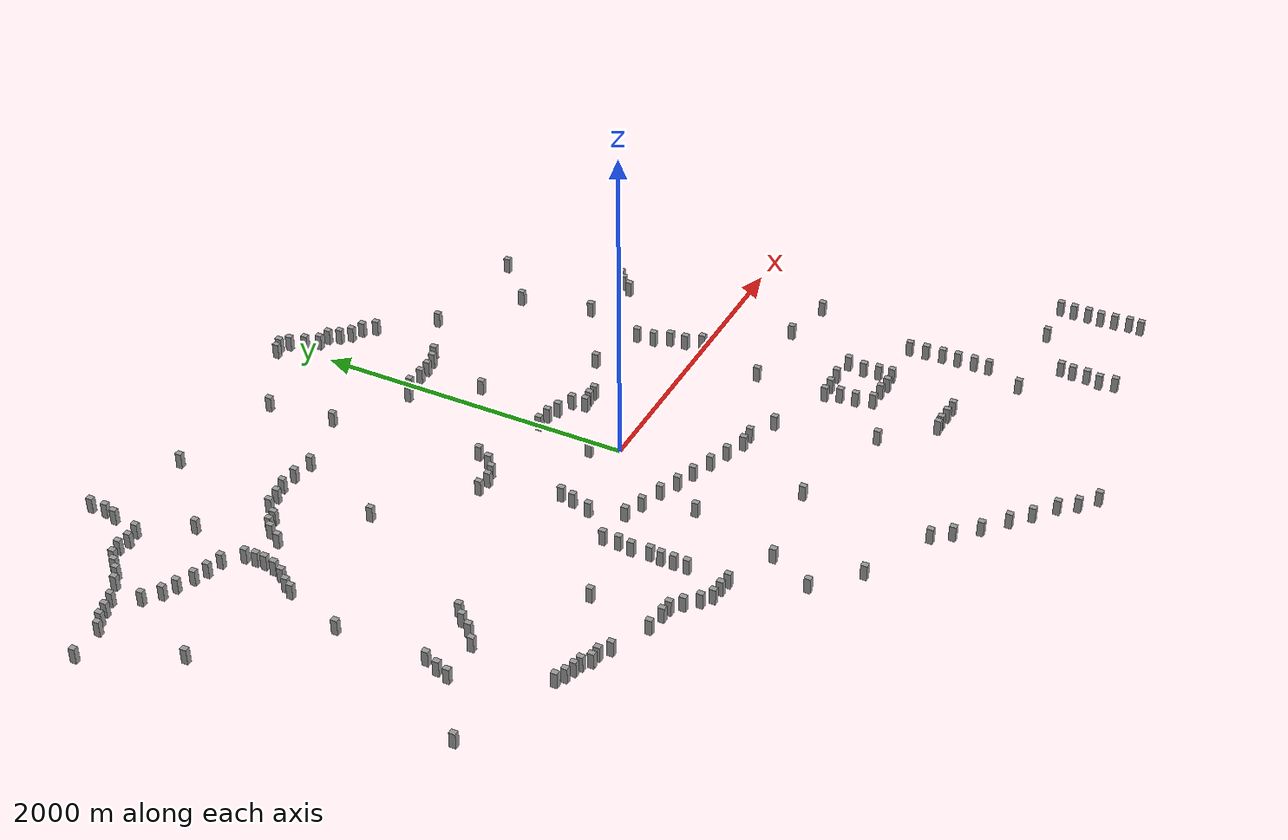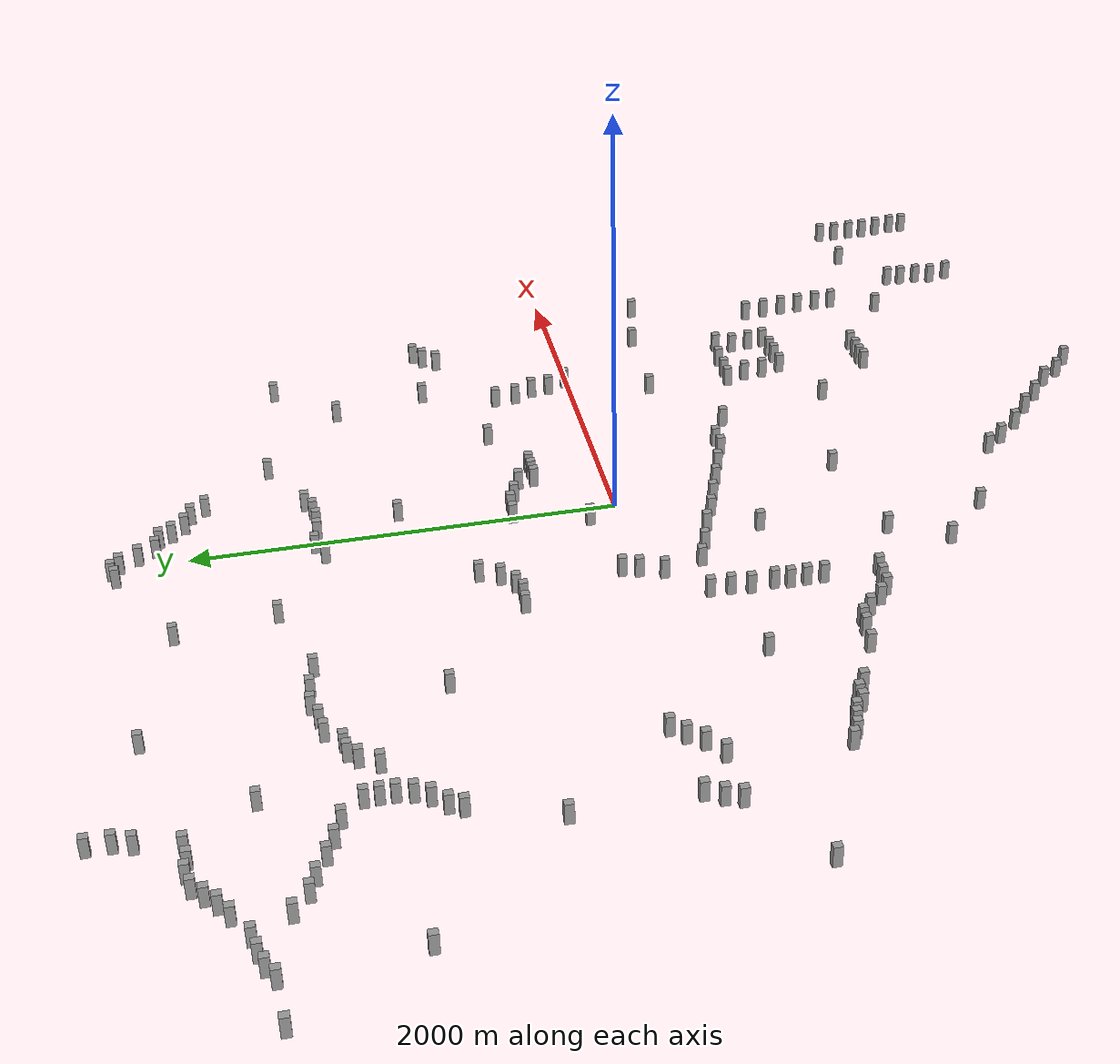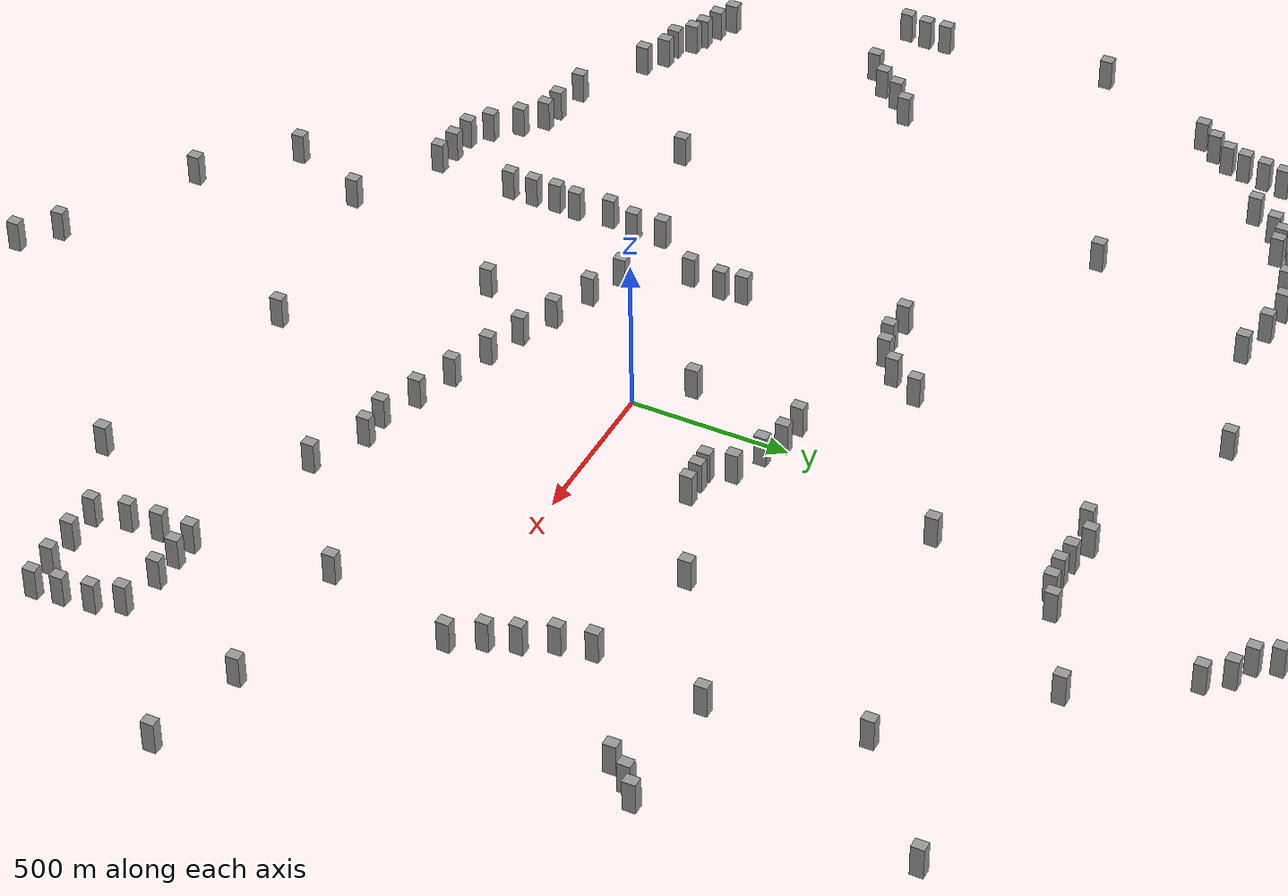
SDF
<sdf version="1.7">
 <world name="default">
  <scene>
   <sky><clouds><speed>12</speed></clouds></sky>
   <ambient>0.95 0.95 0.95 1</ambient>
   <background>0.3 0.3 0.3 1</background>
   <shadows>1</shadows>
  </scene>
  <light name="sun" type="directional">
   <pose>0 0 10 0 -0 0</pose>
   <diffuse>0.8 0.8 0.8 1</diffuse>
   <specular>0.2 0.2 0.2 1</specular>
   <attenuation>
    <range>1000</range>
    <constant>0.9</constant>
    <linear>0.01</linear>
    <quadratic>0.001</quadratic>
   </attenuation>
   <direction>-0.5 0.1 -0.9</direction>
   <spot><inner_angle>0</inner_angle><outer_angle>0</outer_angle><falloff>0</falloff></spot>
  </light>
  <spherical_coordinates>
   <surface_model>EARTH_WGS84</surface_model>
   <latitude_deg>35.7223</latitude_deg>
   <longitude_deg>-120.767</longitude_deg>
   <elevation>280</elevation>
   <heading_deg>0</heading_deg>
  </spherical_coordinates>
  <physics name="default_physics" default="0" type="ode">
   <ode>
    <solver>
     <type>quick</type>
     <iters>10</iters>
     <sor>1.3</sor>
     <use_dynamic_moi_rescaling>0</use_dynamic_moi_rescaling>
    </solver>
    <constraints>
     <cfm>0</cfm>
     <erp>0.2</erp>
     <contact_max_correcting_vel>100</contact_max_correcting_vel>
     <contact_surface_layer>0.001</contact_surface_layer>
    </constraints>
   </ode>
   <max_step_size>0.004</max_step_size>
   <real_time_factor>1</real_time_factor>
   <real_time_update_rate>250</real_time_update_rate>
  </physics>
  <gravity>0 0 -9.8066</gravity>
  <magnetic_field>6e-06 2.3e-05 -4.2e-05</magnetic_field>
  <atmosphere type="adiabatic"/>
  <audio><device>default</device></audio>
  <model name="huge_building">
   <link name="link">
    <inertial>
     <mass>137299</mass>
     <inertia>
      <ixx>1.37911e+08</ixx>
      <ixy>0</ixy>
      <ixz>0</ixz>
      <iyy>1.32035e+08</iyy>
      <iyz>0</iyz>
      <izz>3.13216e+07</izz>
     </inertia>
    </inertial>
    <visual name="visual">
     <geometry><box><size>33.3468 40.3177 102.117</size></box></geometry>
     <material>
      <script><name>Gazebo/Grey</name><uri>file://media/materials/scripts/gazebo.material</uri></script>
      <shader type="pixel"/>
     </material>
    </visual>
    <collision name="collision">
     <geometry><box><size>33.3468 40.3177 102.117</size></box></geometry>
     <surface>
      <friction>
       <ode><mu>1</mu><mu2>1</mu2><fdir1>0 0 0</fdir1><slip1>0</slip1><slip2>0</slip2></ode>
       <torsional>
        <coefficient>1</coefficient>
        <patch_radius>0</patch_radius>
        <surface_radius>0</surface_radius>
        <use_patch_radius>1</use_patch_radius>
        <ode><slip>0</slip></ode>
       </torsional>
      </friction>
      <bounce><restitution_coefficient>0</restitution_coefficient><threshold>1e+06</threshold></bounce>
      <contact>
       <collide_without_contact>0</collide_without_contact>
       <collide_without_contact_bitmask>1</collide_without_contact_bitmask>
       <collide_bitmask>1</collide_bitmask>
       <ode>
        <soft_cfm>0</soft_cfm>
        <soft_erp>0.2</soft_erp>
        <kp>1e+13</kp>
        <kd>1</kd>
        <max_vel>0.01</max_vel>
        <min_depth>0</min_depth>
       </ode>
       <bullet>
        <split_impulse>1</split_impulse>
        <split_impulse_penetration_threshold>-0.01</split_impulse_penetration_threshold>
        <soft_cfm>0</soft_cfm>
        <soft_erp>0.2</soft_erp>
        <kp>1e+13</kp>
        <kd>1</kd>
       </bullet>
      </contact>
     </surface>
    </collision>
   </link>
   <static>0</static>
   <pose>2573.26 -2347.73 0.5 0 -0 0</pose>
  </model>
  <model name="huge_building_0">
   <link name="link">
    <inertial>
     <mass>137299</mass>
     <inertia>
      <ixx>1.37911e+08</ixx>
      <ixy>0</ixy>
      <ixz>0</ixz>
      <iyy>1.32035e+08</iyy>
      <iyz>0</iyz>
      <izz>3.13216e+07</izz>
     </inertia>
    </inertial>
    <visual name="visual">
     <geometry><box><size>33.3468 40.3177 102.117</size></box></geometry>
     <material>
      <script><name>Gazebo/Grey</name><uri>file://media/materials/scripts/gazebo.material</uri></script>
      <shader type="pixel"/>
     </material>
    </visual>
    <collision name="collision">
     <geometry><box><size>33.3468 40.3177 102.117</size></box></geometry>
     <surface>
      <friction>
       <ode><mu>1</mu><mu2>1</mu2><fdir1>0 0 0</fdir1><slip1>0</slip1><slip2>0</slip2></ode>
       <torsional>
        <coefficient>1</coefficient>
        <patch_radius>0</patch_radius>
        <surface_radius>0</surface_radius>
        <use_patch_radius>1</use_patch_radius>
        <ode><slip>0</slip></ode>
       </torsional>
      </friction>
      <bounce><restitution_coefficient>0</restitution_coefficient><threshold>1e+06</threshold></bounce>
      <contact>
       <collide_without_contact>0</collide_without_contact>
       <collide_without_contact_bitmask>1</collide_without_contact_bitmask>
       <collide_bitmask>1</collide_bitmask>
       <ode>
        <soft_cfm>0</soft_cfm>
        <soft_erp>0.2</soft_erp>
        <kp>1e+13</kp>
        <kd>1</kd>
        <max_vel>0.01</max_vel>
        <min_depth>0</min_depth>
       </ode>
       <bullet>
        <split_impulse>1</split_impulse>
        <split_impulse_penetration_threshold>-0.01</split_impulse_penetration_threshold>
        <soft_cfm>0</soft_cfm>
        <soft_erp>0.2</soft_erp>
        <kp>1e+13</kp>
        <kd>1</kd>
       </bullet>
      </contact>
     </surface>
    </collision>
   </link>
   <static>0</static>
   <pose>1927.83 -2388.05 6 0 -0 0</pose>
  </model>
  <model name="huge_building_1">
   <link name="link">
    <inertial>
     <mass>137299</mass>
     <inertia>
      <ixx>1.37911e+08</ixx>
      <ixy>0</ixy>
      <ixz>0</ixz>
      <iyy>1.32035e+08</iyy>
      <iyz>0</iyz>
      <izz>3.13216e+07</izz>
     </inertia>
    </inertial>
    <visual name="visual">
     <geometry><box><size>33.3468 40.3177 102.117</size></box></geometry>
     <material>
      <script><name>Gazebo/Grey</name><uri>file://media/materials/scripts/gazebo.material</uri></script>
      <shader type="pixel"/>
     </material>
    </visual>
    <collision name="collision">
     <geometry><box><size>33.3468 40.3177 102.117</size></box></geometry>
     <surface>
      <friction>
       <ode><mu>1</mu><mu2>1</mu2><fdir1>0 0 0</fdir1><slip1>0</slip1><slip2>0</slip2></ode>
       <torsional>
        <coefficient>1</coefficient>
        <patch_radius>0</patch_radius>
        <surface_radius>0</surface_radius>
        <use_patch_radius>1</use_patch_radius>
        <ode><slip>0</slip></ode>
       </torsional>
      </friction>
      <bounce><restitution_coefficient>0</restitution_coefficient><threshold>1e+06</threshold></bounce>
      <contact>
       <collide_without_contact>0</collide_without_contact>
       <collide_without_contact_bitmask>1</collide_without_contact_bitmask>
       <collide_bitmask>1</collide_bitmask>
       <ode>
        <soft_cfm>0</soft_cfm>
        <soft_erp>0.2</soft_erp>
        <kp>1e+13</kp>
        <kd>1</kd>
        <max_vel>0.01</max_vel>
        <min_depth>0</min_depth>
       </ode>
       <bullet>
        <split_impulse>1</split_impulse>
        <split_impulse_penetration_threshold>-0.01</split_impulse_penetration_threshold>
        <soft_cfm>0</soft_cfm>
        <soft_erp>0.2</soft_erp>
        <kp>1e+13</kp>
        <kd>1</kd>
       </bullet>
      </contact>
     </surface>
    </collision>
   </link>
   <static>0</static>
   <pose>1025.33 -1589.03 27 0 -0 0</pose>
  </model>
  <model name="huge_building_2">
   <link name="link">
    <inertial>
     <mass>137299</mass>
     <inertia>
      <ixx>1.37911e+08</ixx>
      <ixy>0</ixy>
      <ixz>0</ixz>
      <iyy>1.32035e+08</iyy>
      <iyz>0</iyz>
      <izz>3.13216e+07</izz>
     </inertia>
    </inertial>
    <visual name="visual">
     <geometry><box><size>33.3468 40.3177 102.117</size></box></geometry>
     <material>
      <script><name>Gazebo/Grey</name><uri>file://media/materials/scripts/gazebo.material</uri></script>
      <shader type="pixel"/>
     </material>
    </visual>
    <collision name="collision">
     <geometry><box><size>33.3468 40.3177 102.117</size></box></geometry>
     <surface>
      <friction>
       <ode><mu>1</mu><mu2>1</mu2><fdir1>0 0 0</fdir1><slip1>0</slip1><slip2>0</slip2></ode>
       <torsional>
        <coefficient>1</coefficient>
        <patch_radius>0</patch_radius>
        <surface_radius>0</surface_radius>
        <use_patch_radius>1</use_patch_radius>
        <ode><slip>0</slip></ode>
       </torsional>
      </friction>
      <bounce><restitution_coefficient>0</restitution_coefficient><threshold>1e+06</threshold></bounce>
      <contact>
       <collide_without_contact>0</collide_without_contact>
       <collide_without_contact_bitmask>1</collide_without_contact_bitmask>
       <collide_bitmask>1</collide_bitmask>
       <ode>
        <soft_cfm>0</soft_cfm>
        <soft_erp>0.2</soft_erp>
        <kp>1e+13</kp>
        <kd>1</kd>
        <max_vel>0.01</max_vel>
        <min_depth>0</min_depth>
       </ode>
       <bullet>
        <split_impulse>1</split_impulse>
        <split_impulse_penetration_threshold>-0.01</split_impulse_penetration_threshold>
        <soft_cfm>0</soft_cfm>
        <soft_erp>0.2</soft_erp>
        <kp>1e+13</kp>
        <kd>1</kd>
       </bullet>
      </contact>
     </surface>
    </collision>
   </link>
   <static>0</static>
   <pose>1380.82 -867.37 23 0 -0 0</pose>
  </model>
  <model name="huge_building_3">
   <link name="link">
    <inertial>
     <mass>137299</mass>
     <inertia>
      <ixx>1.37911e+08</ixx>
      <ixy>0</ixy>
      <ixz>0</ixz>
      <iyy>1.32035e+08</iyy>
      <iyz>0</iyz>
      <izz>3.13216e+07</izz>
     </inertia>
    </inertial>
    <visual name="visual">
     <geometry><box><size>33.3468 40.3177 102.117</size></box></geometry>
     <material>
      <script><name>Gazebo/Grey</name><uri>file://media/materials/scripts/gazebo.material</uri></script>
      <shader type="pixel"/>
     </material>
    </visual>
    <collision name="collision">
     <geometry><box><size>33.3468 40.3177 102.117</size></box></geometry>
     <surface>
      <friction>
       <ode><mu>1</mu><mu2>1</mu2><fdir1>0 0 0</fdir1><slip1>0</slip1><slip2>0</slip2></ode>
       <torsional>
        <coefficient>1</coefficient>
        <patch_radius>0</patch_radius>
        <surface_radius>0</surface_radius>
        <use_patch_radius>1</use_patch_radius>
        <ode><slip>0</slip></ode>
       </torsional>
      </friction>
      <bounce><restitution_coefficient>0</restitution_coefficient><threshold>1e+06</threshold></bounce>
      <contact>
       <collide_without_contact>0</collide_without_contact>
       <collide_without_contact_bitmask>1</collide_without_contact_bitmask>
       <collide_bitmask>1</collide_bitmask>
       <ode>
        <soft_cfm>0</soft_cfm>
        <soft_erp>0.2</soft_erp>
        <kp>1e+13</kp>
        <kd>1</kd>
        <max_vel>0.01</max_vel>
        <min_depth>0</min_depth>
       </ode>
       <bullet>
        <split_impulse>1</split_impulse>
        <split_impulse_penetration_threshold>-0.01</split_impulse_penetration_threshold>
        <soft_cfm>0</soft_cfm>
        <soft_erp>0.2</soft_erp>
        <kp>1e+13</kp>
        <kd>1</kd>
       </bullet>
      </contact>
     </surface>
    </collision>
   </link>
   <static>0</static>
   <pose>635.531 -705.591 24 0 -0 0</pose>
  </model>
  <model name="huge_building_4">
   <link name="link">
    <inertial>
     <mass>137299</mass>
     <inertia>
      <ixx>1.37911e+08</ixx>
      <ixy>0</ixy>
      <ixz>0</ixz>
      <iyy>1.32035e+08</iyy>
      <iyz>0</iyz>
      <izz>3.13216e+07</izz>
     </inertia>
    </inertial>
    <visual name="visual">
     <geometry><box><size>33.3468 40.3177 102.117</size></box></geometry>
     <material>
      <script><name>Gazebo/Grey</name><uri>file://media/materials/scripts/gazebo.material</uri></script>
      <shader type="pixel"/>
     </material>
    </visual>
    <collision name="collision">
     <geometry><box><size>33.3468 40.3177 102.117</size></box></geometry>
     <surface>
      <friction>
       <ode><mu>1</mu><mu2>1</mu2><fdir1>0 0 0</fdir1><slip1>0</slip1><slip2>0</slip2></ode>
       <torsional>
        <coefficient>1</coefficient>
        <patch_radius>0</patch_radius>
        <surface_radius>0</surface_radius>
        <use_patch_radius>1</use_patch_radius>
        <ode><slip>0</slip></ode>
       </torsional>
      </friction>
      <bounce><restitution_coefficient>0</restitution_coefficient><threshold>1e+06</threshold></bounce>
      <contact>
       <collide_without_contact>0</collide_without_contact>
       <collide_without_contact_bitmask>1</collide_without_contact_bitmask>
       <collide_bitmask>1</collide_bitmask>
       <ode>
        <soft_cfm>0</soft_cfm>
        <soft_erp>0.2</soft_erp>
        <kp>1e+13</kp>
        <kd>1</kd>
        <max_vel>0.01</max_vel>
        <min_depth>0</min_depth>
       </ode>
       <bullet>
        <split_impulse>1</split_impulse>
        <split_impulse_penetration_threshold>-0.01</split_impulse_penetration_threshold>
        <soft_cfm>0</soft_cfm>
        <soft_erp>0.2</soft_erp>
        <kp>1e+13</kp>
        <kd>1</kd>
       </bullet>
      </contact>
     </surface>
    </collision>
   </link>
   <static>0</static>
   <pose>-298.487 -633.428 26 0 -0 0</pose>
  </model>
  <model name="huge_building_5">
   <link name="link">
    <inertial>
     <mass>137299</mass>
     <inertia>
      <ixx>1.37911e+08</ixx>
      <ixy>0</ixy>
      <ixz>0</ixz>
      <iyy>1.32035e+08</iyy>
      <iyz>0</iyz>
      <izz>3.13216e+07</izz>
     </inertia>
    </inertial>
    <visual name="visual">
     <geometry><box><size>33.3468 40.3177 102.117</size></box></geometry>
     <material>
      <script><name>Gazebo/Grey</name><uri>file://media/materials/scripts/gazebo.material</uri></script>
      <shader type="pixel"/>
     </material>
    </visual>
    <collision name="collision">
     <geometry><box><size>33.3468 40.3177 102.117</size></box></geometry>
     <surface>
      <friction>
       <ode><mu>1</mu><mu2>1</mu2><fdir1>0 0 0</fdir1><slip1>0</slip1><slip2>0</slip2></ode>
       <torsional>
        <coefficient>1</coefficient>
        <patch_radius>0</patch_radius>
        <surface_radius>0</surface_radius>
        <use_patch_radius>1</use_patch_radius>
        <ode><slip>0</slip></ode>
       </torsional>
      </friction>
      <bounce><restitution_coefficient>0</restitution_coefficient><threshold>1e+06</threshold></bounce>
      <contact>
       <collide_without_contact>0</collide_without_contact>
       <collide_without_contact_bitmask>1</collide_without_contact_bitmask>
       <collide_bitmask>1</collide_bitmask>
       <ode>
        <soft_cfm>0</soft_cfm>
        <soft_erp>0.2</soft_erp>
        <kp>1e+13</kp>
        <kd>1</kd>
        <max_vel>0.01</max_vel>
        <min_depth>0</min_depth>
       </ode>
       <bullet>
        <split_impulse>1</split_impulse>
        <split_impulse_penetration_threshold>-0.01</split_impulse_penetration_threshold>
        <soft_cfm>0</soft_cfm>
        <soft_erp>0.2</soft_erp>
        <kp>1e+13</kp>
        <kd>1</kd>
       </bullet>
      </contact>
     </surface>
    </collision>
   </link>
   <static>0</static>
   <pose>229.243 349.063 77 0 -0 0</pose>
  </model>
  <model name="huge_building_6">
   <link name="link">
    <inertial>
     <mass>137299</mass>
     <inertia>
      <ixx>1.37911e+08</ixx>
      <ixy>0</ixy>
      <ixz>0</ixz>
      <iyy>1.32035e+08</iyy>
      <iyz>0</iyz>
      <izz>3.13216e+07</izz>
     </inertia>
    </inertial>
    <visual name="visual">
     <geometry><box><size>33.3468 40.3177 102.117</size></box></geometry>
     <material>
      <script><name>Gazebo/Grey</name><uri>file://media/materials/scripts/gazebo.material</uri></script>
      <shader type="pixel"/>
     </material>
    </visual>
    <collision name="collision">
     <geometry><box><size>33.3468 40.3177 102.117</size></box></geometry>
     <surface>
      <friction>
       <ode><mu>1</mu><mu2>1</mu2><fdir1>0 0 0</fdir1><slip1>0</slip1><slip2>0</slip2></ode>
       <torsional>
        <coefficient>1</coefficient>
        <patch_radius>0</patch_radius>
        <surface_radius>0</surface_radius>
        <use_patch_radius>1</use_patch_radius>
        <ode><slip>0</slip></ode>
       </torsional>
      </friction>
      <bounce><restitution_coefficient>0</restitution_coefficient><threshold>1e+06</threshold></bounce>
      <contact>
       <collide_without_contact>0</collide_without_contact>
       <collide_without_contact_bitmask>1</collide_without_contact_bitmask>
       <collide_bitmask>1</collide_bitmask>
       <ode>
        <soft_cfm>0</soft_cfm>
        <soft_erp>0.2</soft_erp>
        <kp>1e+13</kp>
        <kd>1</kd>
        <max_vel>0.01</max_vel>
        <min_depth>0</min_depth>
       </ode>
       <bullet>
        <split_impulse>1</split_impulse>
        <split_impulse_penetration_threshold>-0.01</split_impulse_penetration_threshold>
        <soft_cfm>0</soft_cfm>
        <soft_erp>0.2</soft_erp>
        <kp>1e+13</kp>
        <kd>1</kd>
       </bullet>
      </contact>
     </surface>
    </collision>
   </link>
   <static>0</static>
   <pose>-684.921 559.523 29 0 -0 0</pose>
  </model>
  <model name="huge_building_7">
   <link name="link">
    <inertial>
     <mass>137299</mass>
     <inertia>
      <ixx>1.37911e+08</ixx>
      <ixy>0</ixy>
      <ixz>0</ixz>
      <iyy>1.32035e+08</iyy>
      <iyz>0</iyz>
      <izz>3.13216e+07</izz>
     </inertia>
    </inertial>
    <visual name="visual">
     <geometry><box><size>33.3468 40.3177 102.117</size></box></geometry>
     <material>
      <script><name>Gazebo/Grey</name><uri>file://media/materials/scripts/gazebo.material</uri></script>
      <shader type="pixel"/>
     </material>
    </visual>
    <collision name="collision">
     <geometry><box><size>33.3468 40.3177 102.117</size></box></geometry>
     <surface>
      <friction>
       <ode><mu>1</mu><mu2>1</mu2><fdir1>0 0 0</fdir1><slip1>0</slip1><slip2>0</slip2></ode>
       <torsional>
        <coefficient>1</coefficient>
        <patch_radius>0</patch_radius>
        <surface_radius>0</surface_radius>
        <use_patch_radius>1</use_patch_radius>
        <ode><slip>0</slip></ode>
       </torsional>
      </friction>
      <bounce><restitution_coefficient>0</restitution_coefficient><threshold>1e+06</threshold></bounce>
      <contact>
       <collide_without_contact>0</collide_without_contact>
       <collide_without_contact_bitmask>1</collide_without_contact_bitmask>
       <collide_bitmask>1</collide_bitmask>
       <ode>
        <soft_cfm>0</soft_cfm>
        <soft_erp>0.2</soft_erp>
        <kp>1e+13</kp>
        <kd>1</kd>
        <max_vel>0.01</max_vel>
        <min_depth>0</min_depth>
       </ode>
       <bullet>
        <split_impulse>1</split_impulse>
        <split_impulse_penetration_threshold>-0.01</split_impulse_penetration_threshold>
        <soft_cfm>0</soft_cfm>
        <soft_erp>0.2</soft_erp>
        <kp>1e+13</kp>
        <kd>1</kd>
       </bullet>
      </contact>
     </surface>
    </collision>
   </link>
   <static>0</static>
   <pose>-961.829 1519.98 59 0 -0 0</pose>
  </model>
  <model name="huge_building_8">
   <link name="link">
    <inertial>
     <mass>137299</mass>
     <inertia>
      <ixx>1.37911e+08</ixx>
      <ixy>0</ixy>
      <ixz>0</ixz>
      <iyy>1.32035e+08</iyy>
      <iyz>0</iyz>
      <izz>3.13216e+07</izz>
     </inertia>
    </inertial>
    <visual name="visual">
     <geometry><box><size>33.3468 40.3177 102.117</size></box></geometry>
     <material>
      <script><name>Gazebo/Grey</name><uri>file://media/materials/scripts/gazebo.material</uri></script>
      <shader type="pixel"/>
     </material>
    </visual>
    <collision name="collision">
     <geometry><box><size>33.3468 40.3177 102.117</size></box></geometry>
     <surface>
      <friction>
       <ode><mu>1</mu><mu2>1</mu2><fdir1>0 0 0</fdir1><slip1>0</slip1><slip2>0</slip2></ode>
       <torsional>
        <coefficient>1</coefficient>
        <patch_radius>0</patch_radius>
        <surface_radius>0</surface_radius>
        <use_patch_radius>1</use_patch_radius>
        <ode><slip>0</slip></ode>
       </torsional>
      </friction>
      <bounce><restitution_coefficient>0</restitution_coefficient><threshold>1e+06</threshold></bounce>
      <contact>
       <collide_without_contact>0</collide_without_contact>
       <collide_without_contact_bitmask>1</collide_without_contact_bitmask>
       <collide_bitmask>1</collide_bitmask>
       <ode>
        <soft_cfm>0</soft_cfm>
        <soft_erp>0.2</soft_erp>
        <kp>1e+13</kp>
        <kd>1</kd>
        <max_vel>0.01</max_vel>
        <min_depth>0</min_depth>
       </ode>
       <bullet>
        <split_impulse>1</split_impulse>
        <split_impulse_penetration_threshold>-0.01</split_impulse_penetration_threshold>
        <soft_cfm>0</soft_cfm>
        <soft_erp>0.2</soft_erp>
        <kp>1e+13</kp>
        <kd>1</kd>
       </bullet>
      </contact>
     </surface>
    </collision>
   </link>
   <static>0</static>
   <pose>-1923.22 1028.99 36 0 -0 0</pose>
  </model>
  <model name="huge_building_9">
   <link name="link">
    <inertial>
     <mass>137299</mass>
     <inertia>
      <ixx>1.37911e+08</ixx>
      <ixy>0</ixy>
      <ixz>0</ixz>
      <iyy>1.32035e+08</iyy>
      <iyz>0</iyz>
      <izz>3.13216e+07</izz>
     </inertia>
    </inertial>
    <visual name="visual">
     <geometry><box><size>33.3468 40.3177 102.117</size></box></geometry>
     <material>
      <script><name>Gazebo/Grey</name><uri>file://media/materials/scripts/gazebo.material</uri></script>
      <shader type="pixel"/>
     </material>
    </visual>
    <collision name="collision">
     <geometry><box><size>33.3468 40.3177 102.117</size></box></geometry>
     <surface>
      <friction>
       <ode><mu>1</mu><mu2>1</mu2><fdir1>0 0 0</fdir1><slip1>0</slip1><slip2>0</slip2></ode>
       <torsional>
        <coefficient>1</coefficient>
        <patch_radius>0</patch_radius>
        <surface_radius>0</surface_radius>
        <use_patch_radius>1</use_patch_radius>
        <ode><slip>0</slip></ode>
       </torsional>
      </friction>
      <bounce><restitution_coefficient>0</restitution_coefficient><threshold>1e+06</threshold></bounce>
      <contact>
       <collide_without_contact>0</collide_without_contact>
       <collide_without_contact_bitmask>1</collide_without_contact_bitmask>
       <collide_bitmask>1</collide_bitmask>
       <ode>
        <soft_cfm>0</soft_cfm>
        <soft_erp>0.2</soft_erp>
        <kp>1e+13</kp>
        <kd>1</kd>
        <max_vel>0.01</max_vel>
        <min_depth>0</min_depth>
       </ode>
       <bullet>
        <split_impulse>1</split_impulse>
        <split_impulse_penetration_threshold>-0.01</split_impulse_penetration_threshold>
        <soft_cfm>0</soft_cfm>
        <soft_erp>0.2</soft_erp>
        <kp>1e+13</kp>
        <kd>1</kd>
       </bullet>
      </contact>
     </surface>
    </collision>
   </link>
   <static>0</static>
   <pose>-1864.15 2105.7 9 0 -0 0</pose>
  </model>
  <model name="huge_building_10">
   <link name="link">
    <inertial>
     <mass>137299</mass>
     <inertia>
      <ixx>1.37911e+08</ixx>
      <ixy>0</ixy>
      <ixz>0</ixz>
      <iyy>1.32035e+08</iyy>
      <iyz>0</iyz>
      <izz>3.13216e+07</izz>
     </inertia>
    </inertial>
    <visual name="visual">
     <geometry><box><size>33.3468 40.3177 102.117</size></box></geometry>
     <material>
      <script><name>Gazebo/Grey</name><uri>file://media/materials/scripts/gazebo.material</uri></script>
      <shader type="pixel"/>
     </material>
    </visual>
    <collision name="collision">
     <geometry><box><size>33.3468 40.3177 102.117</size></box></geometry>
     <surface>
      <friction>
       <ode><mu>1</mu><mu2>1</mu2><fdir1>0 0 0</fdir1><slip1>0</slip1><slip2>0</slip2></ode>
       <torsional>
        <coefficient>1</coefficient>
        <patch_radius>0</patch_radius>
        <surface_radius>0</surface_radius>
        <use_patch_radius>1</use_patch_radius>
        <ode><slip>0</slip></ode>
       </torsional>
      </friction>
      <bounce><restitution_coefficient>0</restitution_coefficient><threshold>1e+06</threshold></bounce>
      <contact>
       <collide_without_contact>0</collide_without_contact>
       <collide_without_contact_bitmask>1</collide_without_contact_bitmask>
       <collide_bitmask>1</collide_bitmask>
       <ode>
        <soft_cfm>0</soft_cfm>
        <soft_erp>0.2</soft_erp>
        <kp>1e+13</kp>
        <kd>1</kd>
        <max_vel>0.01</max_vel>
        <min_depth>0</min_depth>
       </ode>
       <bullet>
        <split_impulse>1</split_impulse>
        <split_impulse_penetration_threshold>-0.01</split_impulse_penetration_threshold>
        <soft_cfm>0</soft_cfm>
        <soft_erp>0.2</soft_erp>
        <kp>1e+13</kp>
        <kd>1</kd>
       </bullet>
      </contact>
     </surface>
    </collision>
   </link>
   <static>0</static>
   <pose>1917.56 -2291.93 0 0 -0 0</pose>
  </model>
  <model name="huge_building_11">
   <link name="link">
    <inertial>
     <mass>137299</mass>
     <inertia>
      <ixx>1.37911e+08</ixx>
      <ixy>0</ixy>
      <ixz>0</ixz>
      <iyy>1.32035e+08</iyy>
      <iyz>0</iyz>
      <izz>3.13216e+07</izz>
     </inertia>
    </inertial>
    <visual name="visual">
     <geometry><box><size>33.3468 40.3177 102.117</size></box></geometry>
     <material>
      <script><name>Gazebo/Grey</name><uri>file://media/materials/scripts/gazebo.material</uri></script>
      <shader type="pixel"/>
     </material>
    </visual>
    <collision name="collision">
     <geometry><box><size>33.3468 40.3177 102.117</size></box></geometry>
     <surface>
      <friction>
       <ode><mu>1</mu><mu2>1</mu2><fdir1>0 0 0</fdir1><slip1>0</slip1><slip2>0</slip2></ode>
       <torsional>
        <coefficient>1</coefficient>
        <patch_radius>0</patch_radius>
        <surface_radius>0</surface_radius>
        <use_patch_radius>1</use_patch_radius>
        <ode><slip>0</slip></ode>
       </torsional>
      </friction>
      <bounce><restitution_coefficient>0</restitution_coefficient><threshold>1e+06</threshold></bounce>
      <contact>
       <collide_without_contact>0</collide_without_contact>
       <collide_without_contact_bitmask>1</collide_without_contact_bitmask>
       <collide_bitmask>1</collide_bitmask>
       <ode>
        <soft_cfm>0</soft_cfm>
        <soft_erp>0.2</soft_erp>
        <kp>1e+13</kp>
        <kd>1</kd>
        <max_vel>0.01</max_vel>
        <min_depth>0</min_depth>
       </ode>
       <bullet>
        <split_impulse>1</split_impulse>
        <split_impulse_penetration_threshold>-0.01</split_impulse_penetration_threshold>
        <soft_cfm>0</soft_cfm>
        <soft_erp>0.2</soft_erp>
        <kp>1e+13</kp>
        <kd>1</kd>
       </bullet>
      </contact>
     </surface>
    </collision>
   </link>
   <static>0</static>
   <pose>2575.01 -2273.29 0 0 -0 0</pose>
  </model>
  <model name="huge_building_12">
   <link name="link">
    <inertial>
     <mass>137299</mass>
     <inertia>
      <ixx>1.37911e+08</ixx>
      <ixy>0</ixy>
      <ixz>0</ixz>
      <iyy>1.32035e+08</iyy>
      <iyz>0</iyz>
      <izz>3.13216e+07</izz>
     </inertia>
    </inertial>
    <visual name="visual">
     <geometry><box><size>33.3468 40.3177 102.117</size></box></geometry>
     <material>
      <script><name>Gazebo/Grey</name><uri>file://media/materials/scripts/gazebo.material</uri></script>
      <shader type="pixel"/>
     </material>
    </visual>
    <collision name="collision">
     <geometry><box><size>33.3468 40.3177 102.117</size></box></geometry>
     <surface>
      <friction>
       <ode><mu>1</mu><mu2>1</mu2><fdir1>0 0 0</fdir1><slip1>0</slip1><slip2>0</slip2></ode>
       <torsional>
        <coefficient>1</coefficient>
        <patch_radius>0</patch_radius>
        <surface_radius>0</surface_radius>
        <use_patch_radius>1</use_patch_radius>
        <ode><slip>0</slip></ode>
       </torsional>
      </friction>
      <bounce><restitution_coefficient>0</restitution_coefficient><threshold>1e+06</threshold></bounce>
      <contact>
       <collide_without_contact>0</collide_without_contact>
       <collide_without_contact_bitmask>1</collide_without_contact_bitmask>
       <collide_bitmask>1</collide_bitmask>
       <ode>
        <soft_cfm>0</soft_cfm>
        <soft_erp>0.2</soft_erp>
        <kp>1e+13</kp>
        <kd>1</kd>
        <max_vel>0.01</max_vel>
        <min_depth>0</min_depth>
       </ode>
       <bullet>
        <split_impulse>1</split_impulse>
        <split_impulse_penetration_threshold>-0.01</split_impulse_penetration_threshold>
        <soft_cfm>0</soft_cfm>
        <soft_erp>0.2</soft_erp>
        <kp>1e+13</kp>
        <kd>1</kd>
       </bullet>
      </contact>
     </surface>
    </collision>
   </link>
   <static>0</static>
   <pose>1085.29 -1585.35 21 0 -0 0</pose>
  </model>
  <model name="huge_building_13">
   <link name="link">
    <inertial>
     <mass>137299</mass>
     <inertia>
      <ixx>1.37911e+08</ixx>
      <ixy>0</ixy>
      <ixz>0</ixz>
      <iyy>1.32035e+08</iyy>
      <iyz>0</iyz>
      <izz>3.13216e+07</izz>
     </inertia>
    </inertial>
    <visual name="visual">
     <geometry><box><size>33.3468 40.3177 102.117</size></box></geometry>
     <material>
      <script><name>Gazebo/Grey</name><uri>file://media/materials/scripts/gazebo.material</uri></script>
      <shader type="pixel"/>
     </material>
    </visual>
    <collision name="collision">
     <geometry><box><size>33.3468 40.3177 102.117</size></box></geometry>
     <surface>
      <friction>
       <ode><mu>1</mu><mu2>1</mu2><fdir1>0 0 0</fdir1><slip1>0</slip1><slip2>0</slip2></ode>
       <torsional>
        <coefficient>1</coefficient>
        <patch_radius>0</patch_radius>
        <surface_radius>0</surface_radius>
        <use_patch_radius>1</use_patch_radius>
        <ode><slip>0</slip></ode>
       </torsional>
      </friction>
      <bounce><restitution_coefficient>0</restitution_coefficient><threshold>1e+06</threshold></bounce>
      <contact>
       <collide_without_contact>0</collide_without_contact>
       <collide_without_contact_bitmask>1</collide_without_contact_bitmask>
       <collide_bitmask>1</collide_bitmask>
       <ode>
        <soft_cfm>0</soft_cfm>
        <soft_erp>0.2</soft_erp>
        <kp>1e+13</kp>
        <kd>1</kd>
        <max_vel>0.01</max_vel>
        <min_depth>0</min_depth>
       </ode>
       <bullet>
        <split_impulse>1</split_impulse>
        <split_impulse_penetration_threshold>-0.01</split_impulse_penetration_threshold>
        <soft_cfm>0</soft_cfm>
        <soft_erp>0.2</soft_erp>
        <kp>1e+13</kp>
        <kd>1</kd>
       </bullet>
      </contact>
     </surface>
    </collision>
   </link>
   <static>0</static>
   <pose>1168.46 -1590.58 18 0 -0 0</pose>
  </model>
  <model name="huge_building_14">
   <link name="link">
    <inertial>
     <mass>137299</mass>
     <inertia>
      <ixx>1.37911e+08</ixx>
      <ixy>0</ixy>
      <ixz>0</ixz>
      <iyy>1.32035e+08</iyy>
      <iyz>0</iyz>
      <izz>3.13216e+07</izz>
     </inertia>
    </inertial>
    <visual name="visual">
     <geometry><box><size>33.3468 40.3177 102.117</size></box></geometry>
     <material>
      <script><name>Gazebo/Grey</name><uri>file://media/materials/scripts/gazebo.material</uri></script>
      <shader type="pixel"/>
     </material>
    </visual>
    <collision name="collision">
     <geometry><box><size>33.3468 40.3177 102.117</size></box></geometry>
     <surface>
      <friction>
       <ode><mu>1</mu><mu2>1</mu2><fdir1>0 0 0</fdir1><slip1>0</slip1><slip2>0</slip2></ode>
       <torsional>
        <coefficient>1</coefficient>
        <patch_radius>0</patch_radius>
        <surface_radius>0</surface_radius>
        <use_patch_radius>1</use_patch_radius>
        <ode><slip>0</slip></ode>
       </torsional>
      </friction>
      <bounce><restitution_coefficient>0</restitution_coefficient><threshold>1e+06</threshold></bounce>
      <contact>
       <collide_without_contact>0</collide_without_contact>
       <collide_without_contact_bitmask>1</collide_without_contact_bitmask>
       <collide_bitmask>1</collide_bitmask>
       <ode>
        <soft_cfm>0</soft_cfm>
        <soft_erp>0.2</soft_erp>
        <kp>1e+13</kp>
        <kd>1</kd>
        <max_vel>0.01</max_vel>
        <min_depth>0</min_depth>
       </ode>
       <bullet>
        <split_impulse>1</split_impulse>
        <split_impulse_penetration_threshold>-0.01</split_impulse_penetration_threshold>
        <soft_cfm>0</soft_cfm>
        <soft_erp>0.2</soft_erp>
        <kp>1e+13</kp>
        <kd>1</kd>
       </bullet>
      </contact>
     </surface>
    </collision>
   </link>
   <static>0</static>
   <pose>1259.18 -1593.39 12 0 -0 0</pose>
  </model>
  <model name="huge_building_15">
   <link name="link">
    <inertial>
     <mass>137299</mass>
     <inertia>
      <ixx>1.37911e+08</ixx>
      <ixy>0</ixy>
      <ixz>0</ixz>
      <iyy>1.32035e+08</iyy>
      <iyz>0</iyz>
      <izz>3.13216e+07</izz>
     </inertia>
    </inertial>
    <visual name="visual">
     <geometry><box><size>33.3468 40.3177 102.117</size></box></geometry>
     <material>
      <script><name>Gazebo/Grey</name><uri>file://media/materials/scripts/gazebo.material</uri></script>
      <shader type="pixel"/>
     </material>
    </visual>
    <collision name="collision">
     <geometry><box><size>33.3468 40.3177 102.117</size></box></geometry>
     <surface>
      <friction>
       <ode><mu>1</mu><mu2>1</mu2><fdir1>0 0 0</fdir1><slip1>0</slip1><slip2>0</slip2></ode>
       <torsional>
        <coefficient>1</coefficient>
        <patch_radius>0</patch_radius>
        <surface_radius>0</surface_radius>
        <use_patch_radius>1</use_patch_radius>
        <ode><slip>0</slip></ode>
       </torsional>
      </friction>
      <bounce><restitution_coefficient>0</restitution_coefficient><threshold>1e+06</threshold></bounce>
      <contact>
       <collide_without_contact>0</collide_without_contact>
       <collide_without_contact_bitmask>1</collide_without_contact_bitmask>
       <collide_bitmask>1</collide_bitmask>
       <ode>
        <soft_cfm>0</soft_cfm>
        <soft_erp>0.2</soft_erp>
        <kp>1e+13</kp>
        <kd>1</kd>
        <max_vel>0.01</max_vel>
        <min_depth>0</min_depth>
       </ode>
       <bullet>
        <split_impulse>1</split_impulse>
        <split_impulse_penetration_threshold>-0.01</split_impulse_penetration_threshold>
        <soft_cfm>0</soft_cfm>
        <soft_erp>0.2</soft_erp>
        <kp>1e+13</kp>
        <kd>1</kd>
       </bullet>
      </contact>
     </surface>
    </collision>
   </link>
   <static>0</static>
   <pose>1393.28 -963.742 0 0 -0 0</pose>
  </model>
  <model name="huge_building_16">
   <link name="link">
    <inertial>
     <mass>137299</mass>
     <inertia>
      <ixx>1.37911e+08</ixx>
      <ixy>0</ixy>
      <ixz>0</ixz>
      <iyy>1.32035e+08</iyy>
      <iyz>0</iyz>
      <izz>3.13216e+07</izz>
     </inertia>
    </inertial>
    <visual name="visual">
     <geometry><box><size>33.3468 40.3177 102.117</size></box></geometry>
     <material>
      <script><name>Gazebo/Grey</name><uri>file://media/materials/scripts/gazebo.material</uri></script>
      <shader type="pixel"/>
     </material>
    </visual>
    <collision name="collision">
     <geometry><box><size>33.3468 40.3177 102.117</size></box></geometry>
     <surface>
      <friction>
       <ode><mu>1</mu><mu2>1</mu2><fdir1>0 0 0</fdir1><slip1>0</slip1><slip2>0</slip2></ode>
       <torsional>
        <coefficient>1</coefficient>
        <patch_radius>0</patch_radius>
        <surface_radius>0</surface_radius>
        <use_patch_radius>1</use_patch_radius>
        <ode><slip>0</slip></ode>
       </torsional>
      </friction>
      <bounce><restitution_coefficient>0</restitution_coefficient><threshold>1e+06</threshold></bounce>
      <contact>
       <collide_without_contact>0</collide_without_contact>
       <collide_without_contact_bitmask>1</collide_without_contact_bitmask>
       <collide_bitmask>1</collide_bitmask>
       <ode>
        <soft_cfm>0</soft_cfm>
        <soft_erp>0.2</soft_erp>
        <kp>1e+13</kp>
        <kd>1</kd>
        <max_vel>0.01</max_vel>
        <min_depth>0</min_depth>
       </ode>
       <bullet>
        <split_impulse>1</split_impulse>
        <split_impulse_penetration_threshold>-0.01</split_impulse_penetration_threshold>
        <soft_cfm>0</soft_cfm>
        <soft_erp>0.2</soft_erp>
        <kp>1e+13</kp>
        <kd>1</kd>
       </bullet>
      </contact>
     </surface>
    </collision>
   </link>
   <static>0</static>
   <pose>1405.03 -1058.23 0 0 -0 0</pose>
  </model>
  <model name="huge_building_17">
   <link name="link">
    <inertial>
     <mass>137299</mass>
     <inertia>
      <ixx>1.37911e+08</ixx>
      <ixy>0</ixy>
      <ixz>0</ixz>
      <iyy>1.32035e+08</iyy>
      <iyz>0</iyz>
      <izz>3.13216e+07</izz>
     </inertia>
    </inertial>
    <visual name="visual">
     <geometry><box><size>33.3468 40.3177 102.117</size></box></geometry>
     <material>
      <script><name>Gazebo/Grey</name><uri>file://media/materials/scripts/gazebo.material</uri></script>
      <shader type="pixel"/>
     </material>
    </visual>
    <collision name="collision">
     <geometry><box><size>33.3468 40.3177 102.117</size></box></geometry>
     <surface>
      <friction>
       <ode><mu>1</mu><mu2>1</mu2><fdir1>0 0 0</fdir1><slip1>0</slip1><slip2>0</slip2></ode>
       <torsional>
        <coefficient>1</coefficient>
        <patch_radius>0</patch_radius>
        <surface_radius>0</surface_radius>
        <use_patch_radius>1</use_patch_radius>
        <ode><slip>0</slip></ode>
       </torsional>
      </friction>
      <bounce><restitution_coefficient>0</restitution_coefficient><threshold>1e+06</threshold></bounce>
      <contact>
       <collide_without_contact>0</collide_without_contact>
       <collide_without_contact_bitmask>1</collide_without_contact_bitmask>
       <collide_bitmask>1</collide_bitmask>
       <ode>
        <soft_cfm>0</soft_cfm>
        <soft_erp>0.2</soft_erp>
        <kp>1e+13</kp>
        <kd>1</kd>
        <max_vel>0.01</max_vel>
        <min_depth>0</min_depth>
       </ode>
       <bullet>
        <split_impulse>1</split_impulse>
        <split_impulse_penetration_threshold>-0.01</split_impulse_penetration_threshold>
        <soft_cfm>0</soft_cfm>
        <soft_erp>0.2</soft_erp>
        <kp>1e+13</kp>
        <kd>1</kd>
       </bullet>
      </contact>
     </surface>
    </collision>
   </link>
   <static>0</static>
   <pose>1414.1 -1141.08 0 0 -0 0</pose>
  </model>
  <model name="huge_building_18">
   <link name="link">
    <inertial>
     <mass>137299</mass>
     <inertia>
      <ixx>1.37911e+08</ixx>
      <ixy>0</ixy>
      <ixz>0</ixz>
      <iyy>1.32035e+08</iyy>
      <iyz>0</iyz>
      <izz>3.13216e+07</izz>
     </inertia>
    </inertial>
    <visual name="visual">
     <geometry><box><size>33.3468 40.3177 102.117</size></box></geometry>
     <material>
      <script><name>Gazebo/Grey</name><uri>file://media/materials/scripts/gazebo.material</uri></script>
      <shader type="pixel"/>
     </material>
    </visual>
    <collision name="collision">
     <geometry><box><size>33.3468 40.3177 102.117</size></box></geometry>
     <surface>
      <friction>
       <ode><mu>1</mu><mu2>1</mu2><fdir1>0 0 0</fdir1><slip1>0</slip1><slip2>0</slip2></ode>
       <torsional>
        <coefficient>1</coefficient>
        <patch_radius>0</patch_radius>
        <surface_radius>0</surface_radius>
        <use_patch_radius>1</use_patch_radius>
        <ode><slip>0</slip></ode>
       </torsional>
      </friction>
      <bounce><restitution_coefficient>0</restitution_coefficient><threshold>1e+06</threshold></bounce>
      <contact>
       <collide_without_contact>0</collide_without_contact>
       <collide_without_contact_bitmask>1</collide_without_contact_bitmask>
       <collide_bitmask>1</collide_bitmask>
       <ode>
        <soft_cfm>0</soft_cfm>
        <soft_erp>0.2</soft_erp>
        <kp>1e+13</kp>
        <kd>1</kd>
        <max_vel>0.01</max_vel>
        <min_depth>0</min_depth>
       </ode>
       <bullet>
        <split_impulse>1</split_impulse>
        <split_impulse_penetration_threshold>-0.01</split_impulse_penetration_threshold>
        <soft_cfm>0</soft_cfm>
        <soft_erp>0.2</soft_erp>
        <kp>1e+13</kp>
        <kd>1</kd>
       </bullet>
      </contact>
     </surface>
    </collision>
   </link>
   <static>0</static>
   <pose>1934.74 -2209.04 0 0 -0 0</pose>
  </model>
  <model name="huge_building_19">
   <link name="link">
    <inertial>
     <mass>137299</mass>
     <inertia>
      <ixx>1.37911e+08</ixx>
      <ixy>0</ixy>
      <ixz>0</ixz>
      <iyy>1.32035e+08</iyy>
      <iyz>0</iyz>
      <izz>3.13216e+07</izz>
     </inertia>
    </inertial>
    <visual name="visual">
     <geometry><box><size>33.3468 40.3177 102.117</size></box></geometry>
     <material>
      <script><name>Gazebo/Grey</name><uri>file://media/materials/scripts/gazebo.material</uri></script>
      <shader type="pixel"/>
     </material>
    </visual>
    <collision name="collision">
     <geometry><box><size>33.3468 40.3177 102.117</size></box></geometry>
     <surface>
      <friction>
       <ode><mu>1</mu><mu2>1</mu2><fdir1>0 0 0</fdir1><slip1>0</slip1><slip2>0</slip2></ode>
       <torsional>
        <coefficient>1</coefficient>
        <patch_radius>0</patch_radius>
        <surface_radius>0</surface_radius>
        <use_patch_radius>1</use_patch_radius>
        <ode><slip>0</slip></ode>
       </torsional>
      </friction>
      <bounce><restitution_coefficient>0</restitution_coefficient><threshold>1e+06</threshold></bounce>
      <contact>
       <collide_without_contact>0</collide_without_contact>
       <collide_without_contact_bitmask>1</collide_without_contact_bitmask>
       <collide_bitmask>1</collide_bitmask>
       <ode>
        <soft_cfm>0</soft_cfm>
        <soft_erp>0.2</soft_erp>
        <kp>1e+13</kp>
        <kd>1</kd>
        <max_vel>0.01</max_vel>
        <min_depth>0</min_depth>
       </ode>
       <bullet>
        <split_impulse>1</split_impulse>
        <split_impulse_penetration_threshold>-0.01</split_impulse_penetration_threshold>
        <soft_cfm>0</soft_cfm>
        <soft_erp>0.2</soft_erp>
        <kp>1e+13</kp>
        <kd>1</kd>
       </bullet>
      </contact>
     </surface>
    </collision>
   </link>
   <static>0</static>
   <pose>1934.12 -2118.06 0 0 -0 0</pose>
  </model>
  <model name="huge_building_20">
   <link name="link">
    <inertial>
     <mass>137299</mass>
     <inertia>
      <ixx>1.37911e+08</ixx>
      <ixy>0</ixy>
      <ixz>0</ixz>
      <iyy>1.32035e+08</iyy>
      <iyz>0</iyz>
      <izz>3.13216e+07</izz>
     </inertia>
    </inertial>
    <visual name="visual">
     <geometry><box><size>33.3468 40.3177 102.117</size></box></geometry>
     <material>
      <script><name>Gazebo/Grey</name><uri>file://media/materials/scripts/gazebo.material</uri></script>
      <shader type="pixel"/>
     </material>
    </visual>
    <collision name="collision">
     <geometry><box><size>33.3468 40.3177 102.117</size></box></geometry>
     <surface>
      <friction>
       <ode><mu>1</mu><mu2>1</mu2><fdir1>0 0 0</fdir1><slip1>0</slip1><slip2>0</slip2></ode>
       <torsional>
        <coefficient>1</coefficient>
        <patch_radius>0</patch_radius>
        <surface_radius>0</surface_radius>
        <use_patch_radius>1</use_patch_radius>
        <ode><slip>0</slip></ode>
       </torsional>
      </friction>
      <bounce><restitution_coefficient>0</restitution_coefficient><threshold>1e+06</threshold></bounce>
      <contact>
       <collide_without_contact>0</collide_without_contact>
       <collide_without_contact_bitmask>1</collide_without_contact_bitmask>
       <collide_bitmask>1</collide_bitmask>
       <ode>
        <soft_cfm>0</soft_cfm>
        <soft_erp>0.2</soft_erp>
        <kp>1e+13</kp>
        <kd>1</kd>
        <max_vel>0.01</max_vel>
        <min_depth>0</min_depth>
       </ode>
       <bullet>
        <split_impulse>1</split_impulse>
        <split_impulse_penetration_threshold>-0.01</split_impulse_penetration_threshold>
        <soft_cfm>0</soft_cfm>
        <soft_erp>0.2</soft_erp>
        <kp>1e+13</kp>
        <kd>1</kd>
       </bullet>
      </contact>
     </surface>
    </collision>
   </link>
   <static>0</static>
   <pose>1939.83 -2041.92 0 0 -0 0</pose>
  </model>
  <model name="huge_building_21">
   <link name="link">
    <inertial>
     <mass>137299</mass>
     <inertia>
      <ixx>1.37911e+08</ixx>
      <ixy>0</ixy>
      <ixz>0</ixz>
      <iyy>1.32035e+08</iyy>
      <iyz>0</iyz>
      <izz>3.13216e+07</izz>
     </inertia>
    </inertial>
    <visual name="visual">
     <geometry><box><size>33.3468 40.3177 102.117</size></box></geometry>
     <material>
      <script><name>Gazebo/Grey</name><uri>file://media/materials/scripts/gazebo.material</uri></script>
      <shader type="pixel"/>
     </material>
    </visual>
    <collision name="collision">
     <geometry><box><size>33.3468 40.3177 102.117</size></box></geometry>
     <surface>
      <friction>
       <ode><mu>1</mu><mu2>1</mu2><fdir1>0 0 0</fdir1><slip1>0</slip1><slip2>0</slip2></ode>
       <torsional>
        <coefficient>1</coefficient>
        <patch_radius>0</patch_radius>
        <surface_radius>0</surface_radius>
        <use_patch_radius>1</use_patch_radius>
        <ode><slip>0</slip></ode>
       </torsional>
      </friction>
      <bounce><restitution_coefficient>0</restitution_coefficient><threshold>1e+06</threshold></bounce>
      <contact>
       <collide_without_contact>0</collide_without_contact>
       <collide_without_contact_bitmask>1</collide_without_contact_bitmask>
       <collide_bitmask>1</collide_bitmask>
       <ode>
        <soft_cfm>0</soft_cfm>
        <soft_erp>0.2</soft_erp>
        <kp>1e+13</kp>
        <kd>1</kd>
        <max_vel>0.01</max_vel>
        <min_depth>0</min_depth>
       </ode>
       <bullet>
        <split_impulse>1</split_impulse>
        <split_impulse_penetration_threshold>-0.01</split_impulse_penetration_threshold>
        <soft_cfm>0</soft_cfm>
        <soft_erp>0.2</soft_erp>
        <kp>1e+13</kp>
        <kd>1</kd>
       </bullet>
      </contact>
     </surface>
    </collision>
   </link>
   <static>0</static>
   <pose>2562.68 -2182.09 0 0 -0 0</pose>
  </model>
  <model name="huge_building_22">
   <link name="link">
    <inertial>
     <mass>137299</mass>
     <inertia>
      <ixx>1.37911e+08</ixx>
      <ixy>0</ixy>
      <ixz>0</ixz>
      <iyy>1.32035e+08</iyy>
      <iyz>0</iyz>
      <izz>3.13216e+07</izz>
     </inertia>
    </inertial>
    <visual name="visual">
     <geometry><box><size>33.3468 40.3177 102.117</size></box></geometry>
     <material>
      <script><name>Gazebo/Grey</name><uri>file://media/materials/scripts/gazebo.material</uri></script>
      <shader type="pixel"/>
     </material>
    </visual>
    <collision name="collision">
     <geometry><box><size>33.3468 40.3177 102.117</size></box></geometry>
     <surface>
      <friction>
       <ode><mu>1</mu><mu2>1</mu2><fdir1>0 0 0</fdir1><slip1>0</slip1><slip2>0</slip2></ode>
       <torsional>
        <coefficient>1</coefficient>
        <patch_radius>0</patch_radius>
        <surface_radius>0</surface_radius>
        <use_patch_radius>1</use_patch_radius>
        <ode><slip>0</slip></ode>
       </torsional>
      </friction>
      <bounce><restitution_coefficient>0</restitution_coefficient><threshold>1e+06</threshold></bounce>
      <contact>
       <collide_without_contact>0</collide_without_contact>
       <collide_without_contact_bitmask>1</collide_without_contact_bitmask>
       <collide_bitmask>1</collide_bitmask>
       <ode>
        <soft_cfm>0</soft_cfm>
        <soft_erp>0.2</soft_erp>
        <kp>1e+13</kp>
        <kd>1</kd>
        <max_vel>0.01</max_vel>
        <min_depth>0</min_depth>
       </ode>
       <bullet>
        <split_impulse>1</split_impulse>
        <split_impulse_penetration_threshold>-0.01</split_impulse_penetration_threshold>
        <soft_cfm>0</soft_cfm>
        <soft_erp>0.2</soft_erp>
        <kp>1e+13</kp>
        <kd>1</kd>
       </bullet>
      </contact>
     </surface>
    </collision>
   </link>
   <static>0</static>
   <pose>2553.74 -2093.87 0 0 -0 0</pose>
  </model>
  <model name="huge_building_23">
   <link name="link">
    <inertial>
     <mass>137299</mass>
     <inertia>
      <ixx>1.37911e+08</ixx>
      <ixy>0</ixy>
      <ixz>0</ixz>
      <iyy>1.32035e+08</iyy>
      <iyz>0</iyz>
      <izz>3.13216e+07</izz>
     </inertia>
    </inertial>
    <visual name="visual">
     <geometry><box><size>33.3468 40.3177 102.117</size></box></geometry>
     <material>
      <script><name>Gazebo/Grey</name><uri>file://media/materials/scripts/gazebo.material</uri></script>
      <shader type="pixel"/>
     </material>
    </visual>
    <collision name="collision">
     <geometry><box><size>33.3468 40.3177 102.117</size></box></geometry>
     <surface>
      <friction>
       <ode><mu>1</mu><mu2>1</mu2><fdir1>0 0 0</fdir1><slip1>0</slip1><slip2>0</slip2></ode>
       <torsional>
        <coefficient>1</coefficient>
        <patch_radius>0</patch_radius>
        <surface_radius>0</surface_radius>
        <use_patch_radius>1</use_patch_radius>
        <ode><slip>0</slip></ode>
       </torsional>
      </friction>
      <bounce><restitution_coefficient>0</restitution_coefficient><threshold>1e+06</threshold></bounce>
      <contact>
       <collide_without_contact>0</collide_without_contact>
       <collide_without_contact_bitmask>1</collide_without_contact_bitmask>
       <collide_bitmask>1</collide_bitmask>
       <ode>
        <soft_cfm>0</soft_cfm>
        <soft_erp>0.2</soft_erp>
        <kp>1e+13</kp>
        <kd>1</kd>
        <max_vel>0.01</max_vel>
        <min_depth>0</min_depth>
       </ode>
       <bullet>
        <split_impulse>1</split_impulse>
        <split_impulse_penetration_threshold>-0.01</split_impulse_penetration_threshold>
        <soft_cfm>0</soft_cfm>
        <soft_erp>0.2</soft_erp>
        <kp>1e+13</kp>
        <kd>1</kd>
       </bullet>
      </contact>
     </surface>
    </collision>
   </link>
   <static>0</static>
   <pose>2556.65 -2011.24 0 0 -0 0</pose>
  </model>
  <model name="huge_building_24">
   <link name="link">
    <inertial>
     <mass>137299</mass>
     <inertia>
      <ixx>1.37911e+08</ixx>
      <ixy>0</ixy>
      <ixz>0</ixz>
      <iyy>1.32035e+08</iyy>
      <iyz>0</iyz>
      <izz>3.13216e+07</izz>
     </inertia>
    </inertial>
    <visual name="visual">
     <geometry><box><size>33.3468 40.3177 102.117</size></box></geometry>
     <material>
      <script><name>Gazebo/Grey</name><uri>file://media/materials/scripts/gazebo.material</uri></script>
      <shader type="pixel"/>
     </material>
    </visual>
    <collision name="collision">
     <geometry><box><size>33.3468 40.3177 102.117</size></box></geometry>
     <surface>
      <friction>
       <ode><mu>1</mu><mu2>1</mu2><fdir1>0 0 0</fdir1><slip1>0</slip1><slip2>0</slip2></ode>
       <torsional>
        <coefficient>1</coefficient>
        <patch_radius>0</patch_radius>
        <surface_radius>0</surface_radius>
        <use_patch_radius>1</use_patch_radius>
        <ode><slip>0</slip></ode>
       </torsional>
      </friction>
      <bounce><restitution_coefficient>0</restitution_coefficient><threshold>1e+06</threshold></bounce>
      <contact>
       <collide_without_contact>0</collide_without_contact>
       <collide_without_contact_bitmask>1</collide_without_contact_bitmask>
       <collide_bitmask>1</collide_bitmask>
       <ode>
        <soft_cfm>0</soft_cfm>
        <soft_erp>0.2</soft_erp>
        <kp>1e+13</kp>
        <kd>1</kd>
        <max_vel>0.01</max_vel>
        <min_depth>0</min_depth>
       </ode>
       <bullet>
        <split_impulse>1</split_impulse>
        <split_impulse_penetration_threshold>-0.01</split_impulse_penetration_threshold>
        <soft_cfm>0</soft_cfm>
        <soft_erp>0.2</soft_erp>
        <kp>1e+13</kp>
        <kd>1</kd>
       </bullet>
      </contact>
     </surface>
    </collision>
   </link>
   <static>0</static>
   <pose>2552.29 -1919.01 0 0 -0 0</pose>
  </model>
  <model name="huge_building_25">
   <link name="link">
    <inertial>
     <mass>137299</mass>
     <inertia>
      <ixx>1.37911e+08</ixx>
      <ixy>0</ixy>
      <ixz>0</ixz>
      <iyy>1.32035e+08</iyy>
      <iyz>0</iyz>
      <izz>3.13216e+07</izz>
     </inertia>
    </inertial>
    <visual name="visual">
     <geometry><box><size>33.3468 40.3177 102.117</size></box></geometry>
     <material>
      <script><name>Gazebo/Grey</name><uri>file://media/materials/scripts/gazebo.material</uri></script>
      <shader type="pixel"/>
     </material>
    </visual>
    <collision name="collision">
     <geometry><box><size>33.3468 40.3177 102.117</size></box></geometry>
     <surface>
      <friction>
       <ode><mu>1</mu><mu2>1</mu2><fdir1>0 0 0</fdir1><slip1>0</slip1><slip2>0</slip2></ode>
       <torsional>
        <coefficient>1</coefficient>
        <patch_radius>0</patch_radius>
        <surface_radius>0</surface_radius>
        <use_patch_radius>1</use_patch_radius>
        <ode><slip>0</slip></ode>
       </torsional>
      </friction>
      <bounce><restitution_coefficient>0</restitution_coefficient><threshold>1e+06</threshold></bounce>
      <contact>
       <collide_without_contact>0</collide_without_contact>
       <collide_without_contact_bitmask>1</collide_without_contact_bitmask>
       <collide_bitmask>1</collide_bitmask>
       <ode>
        <soft_cfm>0</soft_cfm>
        <soft_erp>0.2</soft_erp>
        <kp>1e+13</kp>
        <kd>1</kd>
        <max_vel>0.01</max_vel>
        <min_depth>0</min_depth>
       </ode>
       <bullet>
        <split_impulse>1</split_impulse>
        <split_impulse_penetration_threshold>-0.01</split_impulse_penetration_threshold>
        <soft_cfm>0</soft_cfm>
        <soft_erp>0.2</soft_erp>
        <kp>1e+13</kp>
        <kd>1</kd>
       </bullet>
      </contact>
     </surface>
    </collision>
   </link>
   <static>0</static>
   <pose>2553.79 -1831.28 0 0 -0 0</pose>
  </model>
  <model name="huge_building_26">
   <link name="link">
    <inertial>
     <mass>137299</mass>
     <inertia>
      <ixx>1.37911e+08</ixx>
      <ixy>0</ixy>
      <ixz>0</ixz>
      <iyy>1.32035e+08</iyy>
      <iyz>0</iyz>
      <izz>3.13216e+07</izz>
     </inertia>
    </inertial>
    <visual name="visual">
     <geometry><box><size>33.3468 40.3177 102.117</size></box></geometry>
     <material>
      <script><name>Gazebo/Grey</name><uri>file://media/materials/scripts/gazebo.material</uri></script>
      <shader type="pixel"/>
     </material>
    </visual>
    <collision name="collision">
     <geometry><box><size>33.3468 40.3177 102.117</size></box></geometry>
     <surface>
      <friction>
       <ode><mu>1</mu><mu2>1</mu2><fdir1>0 0 0</fdir1><slip1>0</slip1><slip2>0</slip2></ode>
       <torsional>
        <coefficient>1</coefficient>
        <patch_radius>0</patch_radius>
        <surface_radius>0</surface_radius>
        <use_patch_radius>1</use_patch_radius>
        <ode><slip>0</slip></ode>
       </torsional>
      </friction>
      <bounce><restitution_coefficient>0</restitution_coefficient><threshold>1e+06</threshold></bounce>
      <contact>
       <collide_without_contact>0</collide_without_contact>
       <collide_without_contact_bitmask>1</collide_without_contact_bitmask>
       <collide_bitmask>1</collide_bitmask>
       <ode>
        <soft_cfm>0</soft_cfm>
        <soft_erp>0.2</soft_erp>
        <kp>1e+13</kp>
        <kd>1</kd>
        <max_vel>0.01</max_vel>
        <min_depth>0</min_depth>
       </ode>
       <bullet>
        <split_impulse>1</split_impulse>
        <split_impulse_penetration_threshold>-0.01</split_impulse_penetration_threshold>
        <soft_cfm>0</soft_cfm>
        <soft_erp>0.2</soft_erp>
        <kp>1e+13</kp>
        <kd>1</kd>
       </bullet>
      </contact>
     </surface>
    </collision>
   </link>
   <static>0</static>
   <pose>830.839 -2647.02 20 0 -0 0</pose>
  </model>
  <model name="huge_building_27">
   <link name="link">
    <inertial>
     <mass>137299</mass>
     <inertia>
      <ixx>1.37911e+08</ixx>
      <ixy>0</ixy>
      <ixz>0</ixz>
      <iyy>1.32035e+08</iyy>
      <iyz>0</iyz>
      <izz>3.13216e+07</izz>
     </inertia>
    </inertial>
    <visual name="visual">
     <geometry><box><size>33.3468 40.3177 102.117</size></box></geometry>
     <material>
      <script><name>Gazebo/Grey</name><uri>file://media/materials/scripts/gazebo.material</uri></script>
      <shader type="pixel"/>
     </material>
    </visual>
    <collision name="collision">
     <geometry><box><size>33.3468 40.3177 102.117</size></box></geometry>
     <surface>
      <friction>
       <ode><mu>1</mu><mu2>1</mu2><fdir1>0 0 0</fdir1><slip1>0</slip1><slip2>0</slip2></ode>
       <torsional>
        <coefficient>1</coefficient>
        <patch_radius>0</patch_radius>
        <surface_radius>0</surface_radius>
        <use_patch_radius>1</use_patch_radius>
        <ode><slip>0</slip></ode>
       </torsional>
      </friction>
      <bounce><restitution_coefficient>0</restitution_coefficient><threshold>1e+06</threshold></bounce>
      <contact>
       <collide_without_contact>0</collide_without_contact>
       <collide_without_contact_bitmask>1</collide_without_contact_bitmask>
       <collide_bitmask>1</collide_bitmask>
       <ode>
        <soft_cfm>0</soft_cfm>
        <soft_erp>0.2</soft_erp>
        <kp>1e+13</kp>
        <kd>1</kd>
        <max_vel>0.01</max_vel>
        <min_depth>0</min_depth>
       </ode>
       <bullet>
        <split_impulse>1</split_impulse>
        <split_impulse_penetration_threshold>-0.01</split_impulse_penetration_threshold>
        <soft_cfm>0</soft_cfm>
        <soft_erp>0.2</soft_erp>
        <kp>1e+13</kp>
        <kd>1</kd>
       </bullet>
      </contact>
     </surface>
    </collision>
   </link>
   <static>0</static>
   <pose>722.414 -2559.58 20 0 -0 0</pose>
  </model>
  <model name="huge_building_28">
   <link name="link">
    <inertial>
     <mass>137299</mass>
     <inertia>
      <ixx>1.37911e+08</ixx>
      <ixy>0</ixy>
      <ixz>0</ixz>
      <iyy>1.32035e+08</iyy>
      <iyz>0</iyz>
      <izz>3.13216e+07</izz>
     </inertia>
    </inertial>
    <visual name="visual">
     <geometry><box><size>33.3468 40.3177 102.117</size></box></geometry>
     <material>
      <script><name>Gazebo/Grey</name><uri>file://media/materials/scripts/gazebo.material</uri></script>
      <shader type="pixel"/>
     </material>
    </visual>
    <collision name="collision">
     <geometry><box><size>33.3468 40.3177 102.117</size></box></geometry>
     <surface>
      <friction>
       <ode><mu>1</mu><mu2>1</mu2><fdir1>0 0 0</fdir1><slip1>0</slip1><slip2>0</slip2></ode>
       <torsional>
        <coefficient>1</coefficient>
        <patch_radius>0</patch_radius>
        <surface_radius>0</surface_radius>
        <use_patch_radius>1</use_patch_radius>
        <ode><slip>0</slip></ode>
       </torsional>
      </friction>
      <bounce><restitution_coefficient>0</restitution_coefficient><threshold>1e+06</threshold></bounce>
      <contact>
       <collide_without_contact>0</collide_without_contact>
       <collide_without_contact_bitmask>1</collide_without_contact_bitmask>
       <collide_bitmask>1</collide_bitmask>
       <ode>
        <soft_cfm>0</soft_cfm>
        <soft_erp>0.2</soft_erp>
        <kp>1e+13</kp>
        <kd>1</kd>
        <max_vel>0.01</max_vel>
        <min_depth>0</min_depth>
       </ode>
       <bullet>
        <split_impulse>1</split_impulse>
        <split_impulse_penetration_threshold>-0.01</split_impulse_penetration_threshold>
        <soft_cfm>0</soft_cfm>
        <soft_erp>0.2</soft_erp>
        <kp>1e+13</kp>
        <kd>1</kd>
       </bullet>
      </contact>
     </surface>
    </collision>
   </link>
   <static>0</static>
   <pose>650.039 -2459.02 20 0 -0 0</pose>
  </model>
  <model name="huge_building_29">
   <link name="link">
    <inertial>
     <mass>137299</mass>
     <inertia>
      <ixx>1.37911e+08</ixx>
      <ixy>0</ixy>
      <ixz>0</ixz>
      <iyy>1.32035e+08</iyy>
      <iyz>0</iyz>
      <izz>3.13216e+07</izz>
     </inertia>
    </inertial>
    <visual name="visual">
     <geometry><box><size>33.3468 40.3177 102.117</size></box></geometry>
     <material>
      <script><name>Gazebo/Grey</name><uri>file://media/materials/scripts/gazebo.material</uri></script>
      <shader type="pixel"/>
     </material>
    </visual>
    <collision name="collision">
     <geometry><box><size>33.3468 40.3177 102.117</size></box></geometry>
     <surface>
      <friction>
       <ode><mu>1</mu><mu2>1</mu2><fdir1>0 0 0</fdir1><slip1>0</slip1><slip2>0</slip2></ode>
       <torsional>
        <coefficient>1</coefficient>
        <patch_radius>0</patch_radius>
        <surface_radius>0</surface_radius>
        <use_patch_radius>1</use_patch_radius>
        <ode><slip>0</slip></ode>
       </torsional>
      </friction>
      <bounce><restitution_coefficient>0</restitution_coefficient><threshold>1e+06</threshold></bounce>
      <contact>
       <collide_without_contact>0</collide_without_contact>
       <collide_without_contact_bitmask>1</collide_without_contact_bitmask>
       <collide_bitmask>1</collide_bitmask>
       <ode>
        <soft_cfm>0</soft_cfm>
        <soft_erp>0.2</soft_erp>
        <kp>1e+13</kp>
        <kd>1</kd>
        <max_vel>0.01</max_vel>
        <min_depth>0</min_depth>
       </ode>
       <bullet>
        <split_impulse>1</split_impulse>
        <split_impulse_penetration_threshold>-0.01</split_impulse_penetration_threshold>
        <soft_cfm>0</soft_cfm>
        <soft_erp>0.2</soft_erp>
        <kp>1e+13</kp>
        <kd>1</kd>
       </bullet>
      </contact>
     </surface>
    </collision>
   </link>
   <static>0</static>
   <pose>524.275 -2355.7 20 0 -0 0</pose>
  </model>
  <model name="huge_building_30">
   <link name="link">
    <inertial>
     <mass>137299</mass>
     <inertia>
      <ixx>1.37911e+08</ixx>
      <ixy>0</ixy>
      <ixz>0</ixz>
      <iyy>1.32035e+08</iyy>
      <iyz>0</iyz>
      <izz>3.13216e+07</izz>
     </inertia>
    </inertial>
    <visual name="visual">
     <geometry><box><size>33.3468 40.3177 102.117</size></box></geometry>
     <material>
      <script><name>Gazebo/Grey</name><uri>file://media/materials/scripts/gazebo.material</uri></script>
      <shader type="pixel"/>
     </material>
    </visual>
    <collision name="collision">
     <geometry><box><size>33.3468 40.3177 102.117</size></box></geometry>
     <surface>
      <friction>
       <ode><mu>1</mu><mu2>1</mu2><fdir1>0 0 0</fdir1><slip1>0</slip1><slip2>0</slip2></ode>
       <torsional>
        <coefficient>1</coefficient>
        <patch_radius>0</patch_radius>
        <surface_radius>0</surface_radius>
        <use_patch_radius>1</use_patch_radius>
        <ode><slip>0</slip></ode>
       </torsional>
      </friction>
      <bounce><restitution_coefficient>0</restitution_coefficient><threshold>1e+06</threshold></bounce>
      <contact>
       <collide_without_contact>0</collide_without_contact>
       <collide_without_contact_bitmask>1</collide_without_contact_bitmask>
       <collide_bitmask>1</collide_bitmask>
       <ode>
        <soft_cfm>0</soft_cfm>
        <soft_erp>0.2</soft_erp>
        <kp>1e+13</kp>
        <kd>1</kd>
        <max_vel>0.01</max_vel>
        <min_depth>0</min_depth>
       </ode>
       <bullet>
        <split_impulse>1</split_impulse>
        <split_impulse_penetration_threshold>-0.01</split_impulse_penetration_threshold>
        <soft_cfm>0</soft_cfm>
        <soft_erp>0.2</soft_erp>
        <kp>1e+13</kp>
        <kd>1</kd>
       </bullet>
      </contact>
     </surface>
    </collision>
   </link>
   <static>0</static>
   <pose>413.35 -2255.65 22 0 -0 0</pose>
  </model>
  <model name="huge_building_31">
   <link name="link">
    <inertial>
     <mass>137299</mass>
     <inertia>
      <ixx>1.37911e+08</ixx>
      <ixy>0</ixy>
      <ixz>0</ixz>
      <iyy>1.32035e+08</iyy>
      <iyz>0</iyz>
      <izz>3.13216e+07</izz>
     </inertia>
    </inertial>
    <visual name="visual">
     <geometry><box><size>33.3468 40.3177 102.117</size></box></geometry>
     <material>
      <script><name>Gazebo/Grey</name><uri>file://media/materials/scripts/gazebo.material</uri></script>
      <shader type="pixel"/>
     </material>
    </visual>
    <collision name="collision">
     <geometry><box><size>33.3468 40.3177 102.117</size></box></geometry>
     <surface>
      <friction>
       <ode><mu>1</mu><mu2>1</mu2><fdir1>0 0 0</fdir1><slip1>0</slip1><slip2>0</slip2></ode>
       <torsional>
        <coefficient>1</coefficient>
        <patch_radius>0</patch_radius>
        <surface_radius>0</surface_radius>
        <use_patch_radius>1</use_patch_radius>
        <ode><slip>0</slip></ode>
       </torsional>
      </friction>
      <bounce><restitution_coefficient>0</restitution_coefficient><threshold>1e+06</threshold></bounce>
      <contact>
       <collide_without_contact>0</collide_without_contact>
       <collide_without_contact_bitmask>1</collide_without_contact_bitmask>
       <collide_bitmask>1</collide_bitmask>
       <ode>
        <soft_cfm>0</soft_cfm>
        <soft_erp>0.2</soft_erp>
        <kp>1e+13</kp>
        <kd>1</kd>
        <max_vel>0.01</max_vel>
        <min_depth>0</min_depth>
       </ode>
       <bullet>
        <split_impulse>1</split_impulse>
        <split_impulse_penetration_threshold>-0.01</split_impulse_penetration_threshold>
        <soft_cfm>0</soft_cfm>
        <soft_erp>0.2</soft_erp>
        <kp>1e+13</kp>
        <kd>1</kd>
       </bullet>
      </contact>
     </surface>
    </collision>
   </link>
   <static>0</static>
   <pose>269.202 -2140.6 30 0 -0 0</pose>
  </model>
  <model name="huge_building_32">
   <link name="link">
    <inertial>
     <mass>137299</mass>
     <inertia>
      <ixx>1.37911e+08</ixx>
      <ixy>0</ixy>
      <ixz>0</ixz>
      <iyy>1.32035e+08</iyy>
      <iyz>0</iyz>
      <izz>3.13216e+07</izz>
     </inertia>
    </inertial>
    <visual name="visual">
     <geometry><box><size>33.3468 40.3177 102.117</size></box></geometry>
     <material>
      <script><name>Gazebo/Grey</name><uri>file://media/materials/scripts/gazebo.material</uri></script>
      <shader type="pixel"/>
     </material>
    </visual>
    <collision name="collision">
     <geometry><box><size>33.3468 40.3177 102.117</size></box></geometry>
     <surface>
      <friction>
       <ode><mu>1</mu><mu2>1</mu2><fdir1>0 0 0</fdir1><slip1>0</slip1><slip2>0</slip2></ode>
       <torsional>
        <coefficient>1</coefficient>
        <patch_radius>0</patch_radius>
        <surface_radius>0</surface_radius>
        <use_patch_radius>1</use_patch_radius>
        <ode><slip>0</slip></ode>
       </torsional>
      </friction>
      <bounce><restitution_coefficient>0</restitution_coefficient><threshold>1e+06</threshold></bounce>
      <contact>
       <collide_without_contact>0</collide_without_contact>
       <collide_without_contact_bitmask>1</collide_without_contact_bitmask>
       <collide_bitmask>1</collide_bitmask>
       <ode>
        <soft_cfm>0</soft_cfm>
        <soft_erp>0.2</soft_erp>
        <kp>1e+13</kp>
        <kd>1</kd>
        <max_vel>0.01</max_vel>
        <min_depth>0</min_depth>
       </ode>
       <bullet>
        <split_impulse>1</split_impulse>
        <split_impulse_penetration_threshold>-0.01</split_impulse_penetration_threshold>
        <soft_cfm>0</soft_cfm>
        <soft_erp>0.2</soft_erp>
        <kp>1e+13</kp>
        <kd>1</kd>
       </bullet>
      </contact>
     </surface>
    </collision>
   </link>
   <static>0</static>
   <pose>148.501 -2017.38 38 0 -0 0</pose>
  </model>
  <model name="huge_building_33">
   <link name="link">
    <inertial>
     <mass>137299</mass>
     <inertia>
      <ixx>1.37911e+08</ixx>
      <ixy>0</ixy>
      <ixz>0</ixz>
      <iyy>1.32035e+08</iyy>
      <iyz>0</iyz>
      <izz>3.13216e+07</izz>
     </inertia>
    </inertial>
    <visual name="visual">
     <geometry><box><size>33.3468 40.3177 102.117</size></box></geometry>
     <material>
      <script><name>Gazebo/Grey</name><uri>file://media/materials/scripts/gazebo.material</uri></script>
      <shader type="pixel"/>
     </material>
    </visual>
    <collision name="collision">
     <geometry><box><size>33.3468 40.3177 102.117</size></box></geometry>
     <surface>
      <friction>
       <ode><mu>1</mu><mu2>1</mu2><fdir1>0 0 0</fdir1><slip1>0</slip1><slip2>0</slip2></ode>
       <torsional>
        <coefficient>1</coefficient>
        <patch_radius>0</patch_radius>
        <surface_radius>0</surface_radius>
        <use_patch_radius>1</use_patch_radius>
        <ode><slip>0</slip></ode>
       </torsional>
      </friction>
      <bounce><restitution_coefficient>0</restitution_coefficient><threshold>1e+06</threshold></bounce>
      <contact>
       <collide_without_contact>0</collide_without_contact>
       <collide_without_contact_bitmask>1</collide_without_contact_bitmask>
       <collide_bitmask>1</collide_bitmask>
       <ode>
        <soft_cfm>0</soft_cfm>
        <soft_erp>0.2</soft_erp>
        <kp>1e+13</kp>
        <kd>1</kd>
        <max_vel>0.01</max_vel>
        <min_depth>0</min_depth>
       </ode>
       <bullet>
        <split_impulse>1</split_impulse>
        <split_impulse_penetration_threshold>-0.01</split_impulse_penetration_threshold>
        <soft_cfm>0</soft_cfm>
        <soft_erp>0.2</soft_erp>
        <kp>1e+13</kp>
        <kd>1</kd>
       </bullet>
      </contact>
     </surface>
    </collision>
   </link>
   <static>0</static>
   <pose>58.1126 -1915.78 50 0 -0 0</pose>
  </model>
  <model name="huge_building_34">
   <link name="link">
    <inertial>
     <mass>137299</mass>
     <inertia>
      <ixx>1.37911e+08</ixx>
      <ixy>0</ixy>
      <ixz>0</ixz>
      <iyy>1.32035e+08</iyy>
      <iyz>0</iyz>
      <izz>3.13216e+07</izz>
     </inertia>
    </inertial>
    <visual name="visual">
     <geometry><box><size>33.3468 40.3177 102.117</size></box></geometry>
     <material>
      <script><name>Gazebo/Grey</name><uri>file://media/materials/scripts/gazebo.material</uri></script>
      <shader type="pixel"/>
     </material>
    </visual>
    <collision name="collision">
     <geometry><box><size>33.3468 40.3177 102.117</size></box></geometry>
     <surface>
      <friction>
       <ode><mu>1</mu><mu2>1</mu2><fdir1>0 0 0</fdir1><slip1>0</slip1><slip2>0</slip2></ode>
       <torsional>
        <coefficient>1</coefficient>
        <patch_radius>0</patch_radius>
        <surface_radius>0</surface_radius>
        <use_patch_radius>1</use_patch_radius>
        <ode><slip>0</slip></ode>
       </torsional>
      </friction>
      <bounce><restitution_coefficient>0</restitution_coefficient><threshold>1e+06</threshold></bounce>
      <contact>
       <collide_without_contact>0</collide_without_contact>
       <collide_without_contact_bitmask>1</collide_without_contact_bitmask>
       <collide_bitmask>1</collide_bitmask>
       <ode>
        <soft_cfm>0</soft_cfm>
        <soft_erp>0.2</soft_erp>
        <kp>1e+13</kp>
        <kd>1</kd>
        <max_vel>0.01</max_vel>
        <min_depth>0</min_depth>
       </ode>
       <bullet>
        <split_impulse>1</split_impulse>
        <split_impulse_penetration_threshold>-0.01</split_impulse_penetration_threshold>
        <soft_cfm>0</soft_cfm>
        <soft_erp>0.2</soft_erp>
        <kp>1e+13</kp>
        <kd>1</kd>
       </bullet>
      </contact>
     </surface>
    </collision>
   </link>
   <static>0</static>
   <pose>1312.17 -1150.91 0 0 -0 0</pose>
  </model>
  <model name="huge_building_35">
   <link name="link">
    <inertial>
     <mass>137299</mass>
     <inertia>
      <ixx>1.37911e+08</ixx>
      <ixy>0</ixy>
      <ixz>0</ixz>
      <iyy>1.32035e+08</iyy>
      <iyz>0</iyz>
      <izz>3.13216e+07</izz>
     </inertia>
    </inertial>
    <visual name="visual">
     <geometry><box><size>33.3468 40.3177 102.117</size></box></geometry>
     <material>
      <script><name>Gazebo/Grey</name><uri>file://media/materials/scripts/gazebo.material</uri></script>
      <shader type="pixel"/>
     </material>
    </visual>
    <collision name="collision">
     <geometry><box><size>33.3468 40.3177 102.117</size></box></geometry>
     <surface>
      <friction>
       <ode><mu>1</mu><mu2>1</mu2><fdir1>0 0 0</fdir1><slip1>0</slip1><slip2>0</slip2></ode>
       <torsional>
        <coefficient>1</coefficient>
        <patch_radius>0</patch_radius>
        <surface_radius>0</surface_radius>
        <use_patch_radius>1</use_patch_radius>
        <ode><slip>0</slip></ode>
       </torsional>
      </friction>
      <bounce><restitution_coefficient>0</restitution_coefficient><threshold>1e+06</threshold></bounce>
      <contact>
       <collide_without_contact>0</collide_without_contact>
       <collide_without_contact_bitmask>1</collide_without_contact_bitmask>
       <collide_bitmask>1</collide_bitmask>
       <ode>
        <soft_cfm>0</soft_cfm>
        <soft_erp>0.2</soft_erp>
        <kp>1e+13</kp>
        <kd>1</kd>
        <max_vel>0.01</max_vel>
        <min_depth>0</min_depth>
       </ode>
       <bullet>
        <split_impulse>1</split_impulse>
        <split_impulse_penetration_threshold>-0.01</split_impulse_penetration_threshold>
        <soft_cfm>0</soft_cfm>
        <soft_erp>0.2</soft_erp>
        <kp>1e+13</kp>
        <kd>1</kd>
       </bullet>
      </contact>
     </surface>
    </collision>
   </link>
   <static>0</static>
   <pose>1212.32 -1146.2 16 0 -0 0</pose>
  </model>
  <model name="huge_building_36">
   <link name="link">
    <inertial>
     <mass>137299</mass>
     <inertia>
      <ixx>1.37911e+08</ixx>
      <ixy>0</ixy>
      <ixz>0</ixz>
      <iyy>1.32035e+08</iyy>
      <iyz>0</iyz>
      <izz>3.13216e+07</izz>
     </inertia>
    </inertial>
    <visual name="visual">
     <geometry><box><size>33.3468 40.3177 102.117</size></box></geometry>
     <material>
      <script><name>Gazebo/Grey</name><uri>file://media/materials/scripts/gazebo.material</uri></script>
      <shader type="pixel"/>
     </material>
    </visual>
    <collision name="collision">
     <geometry><box><size>33.3468 40.3177 102.117</size></box></geometry>
     <surface>
      <friction>
       <ode><mu>1</mu><mu2>1</mu2><fdir1>0 0 0</fdir1><slip1>0</slip1><slip2>0</slip2></ode>
       <torsional>
        <coefficient>1</coefficient>
        <patch_radius>0</patch_radius>
        <surface_radius>0</surface_radius>
        <use_patch_radius>1</use_patch_radius>
        <ode><slip>0</slip></ode>
       </torsional>
      </friction>
      <bounce><restitution_coefficient>0</restitution_coefficient><threshold>1e+06</threshold></bounce>
      <contact>
       <collide_without_contact>0</collide_without_contact>
       <collide_without_contact_bitmask>1</collide_without_contact_bitmask>
       <collide_bitmask>1</collide_bitmask>
       <ode>
        <soft_cfm>0</soft_cfm>
        <soft_erp>0.2</soft_erp>
        <kp>1e+13</kp>
        <kd>1</kd>
        <max_vel>0.01</max_vel>
        <min_depth>0</min_depth>
       </ode>
       <bullet>
        <split_impulse>1</split_impulse>
        <split_impulse_penetration_threshold>-0.01</split_impulse_penetration_threshold>
        <soft_cfm>0</soft_cfm>
        <soft_erp>0.2</soft_erp>
        <kp>1e+13</kp>
        <kd>1</kd>
       </bullet>
      </contact>
     </surface>
    </collision>
   </link>
   <static>0</static>
   <pose>1101.49 -1144.01 18 0 -0 0</pose>
  </model>
  <model name="huge_building_37">
   <link name="link">
    <inertial>
     <mass>137299</mass>
     <inertia>
      <ixx>1.37911e+08</ixx>
      <ixy>0</ixy>
      <ixz>0</ixz>
      <iyy>1.32035e+08</iyy>
      <iyz>0</iyz>
      <izz>3.13216e+07</izz>
     </inertia>
    </inertial>
    <visual name="visual">
     <geometry><box><size>33.3468 40.3177 102.117</size></box></geometry>
     <material>
      <script><name>Gazebo/Grey</name><uri>file://media/materials/scripts/gazebo.material</uri></script>
      <shader type="pixel"/>
     </material>
    </visual>
    <collision name="collision">
     <geometry><box><size>33.3468 40.3177 102.117</size></box></geometry>
     <surface>
      <friction>
       <ode><mu>1</mu><mu2>1</mu2><fdir1>0 0 0</fdir1><slip1>0</slip1><slip2>0</slip2></ode>
       <torsional>
        <coefficient>1</coefficient>
        <patch_radius>0</patch_radius>
        <surface_radius>0</surface_radius>
        <use_patch_radius>1</use_patch_radius>
        <ode><slip>0</slip></ode>
       </torsional>
      </friction>
      <bounce><restitution_coefficient>0</restitution_coefficient><threshold>1e+06</threshold></bounce>
      <contact>
       <collide_without_contact>0</collide_without_contact>
       <collide_without_contact_bitmask>1</collide_without_contact_bitmask>
       <collide_bitmask>1</collide_bitmask>
       <ode>
        <soft_cfm>0</soft_cfm>
        <soft_erp>0.2</soft_erp>
        <kp>1e+13</kp>
        <kd>1</kd>
        <max_vel>0.01</max_vel>
        <min_depth>0</min_depth>
       </ode>
       <bullet>
        <split_impulse>1</split_impulse>
        <split_impulse_penetration_threshold>-0.01</split_impulse_penetration_threshold>
        <soft_cfm>0</soft_cfm>
        <soft_erp>0.2</soft_erp>
        <kp>1e+13</kp>
        <kd>1</kd>
       </bullet>
      </contact>
     </surface>
    </collision>
   </link>
   <static>0</static>
   <pose>1074.68 -1041.48 16 0 -0 0</pose>
  </model>
  <model name="huge_building_38">
   <link name="link">
    <inertial>
     <mass>137299</mass>
     <inertia>
      <ixx>1.37911e+08</ixx>
      <ixy>0</ixy>
      <ixz>0</ixz>
      <iyy>1.32035e+08</iyy>
      <iyz>0</iyz>
      <izz>3.13216e+07</izz>
     </inertia>
    </inertial>
    <visual name="visual">
     <geometry><box><size>33.3468 40.3177 102.117</size></box></geometry>
     <material>
      <script><name>Gazebo/Grey</name><uri>file://media/materials/scripts/gazebo.material</uri></script>
      <shader type="pixel"/>
     </material>
    </visual>
    <collision name="collision">
     <geometry><box><size>33.3468 40.3177 102.117</size></box></geometry>
     <surface>
      <friction>
       <ode><mu>1</mu><mu2>1</mu2><fdir1>0 0 0</fdir1><slip1>0</slip1><slip2>0</slip2></ode>
       <torsional>
        <coefficient>1</coefficient>
        <patch_radius>0</patch_radius>
        <surface_radius>0</surface_radius>
        <use_patch_radius>1</use_patch_radius>
        <ode><slip>0</slip></ode>
       </torsional>
      </friction>
      <bounce><restitution_coefficient>0</restitution_coefficient><threshold>1e+06</threshold></bounce>
      <contact>
       <collide_without_contact>0</collide_without_contact>
       <collide_without_contact_bitmask>1</collide_without_contact_bitmask>
       <collide_bitmask>1</collide_bitmask>
       <ode>
        <soft_cfm>0</soft_cfm>
        <soft_erp>0.2</soft_erp>
        <kp>1e+13</kp>
        <kd>1</kd>
        <max_vel>0.01</max_vel>
        <min_depth>0</min_depth>
       </ode>
       <bullet>
        <split_impulse>1</split_impulse>
        <split_impulse_penetration_threshold>-0.01</split_impulse_penetration_threshold>
        <soft_cfm>0</soft_cfm>
        <soft_erp>0.2</soft_erp>
        <kp>1e+13</kp>
        <kd>1</kd>
       </bullet>
      </contact>
     </surface>
    </collision>
   </link>
   <static>0</static>
   <pose>1069.8 -942.778 15 0 -0 0</pose>
  </model>
  <model name="huge_building_39">
   <link name="link">
    <inertial>
     <mass>137299</mass>
     <inertia>
      <ixx>1.37911e+08</ixx>
      <ixy>0</ixy>
      <ixz>0</ixz>
      <iyy>1.32035e+08</iyy>
      <iyz>0</iyz>
      <izz>3.13216e+07</izz>
     </inertia>
    </inertial>
    <visual name="visual">
     <geometry><box><size>33.3468 40.3177 102.117</size></box></geometry>
     <material>
      <script><name>Gazebo/Grey</name><uri>file://media/materials/scripts/gazebo.material</uri></script>
      <shader type="pixel"/>
     </material>
    </visual>
    <collision name="collision">
     <geometry><box><size>33.3468 40.3177 102.117</size></box></geometry>
     <surface>
      <friction>
       <ode><mu>1</mu><mu2>1</mu2><fdir1>0 0 0</fdir1><slip1>0</slip1><slip2>0</slip2></ode>
       <torsional>
        <coefficient>1</coefficient>
        <patch_radius>0</patch_radius>
        <surface_radius>0</surface_radius>
        <use_patch_radius>1</use_patch_radius>
        <ode><slip>0</slip></ode>
       </torsional>
      </friction>
      <bounce><restitution_coefficient>0</restitution_coefficient><threshold>1e+06</threshold></bounce>
      <contact>
       <collide_without_contact>0</collide_without_contact>
       <collide_without_contact_bitmask>1</collide_without_contact_bitmask>
       <collide_bitmask>1</collide_bitmask>
       <ode>
        <soft_cfm>0</soft_cfm>
        <soft_erp>0.2</soft_erp>
        <kp>1e+13</kp>
        <kd>1</kd>
        <max_vel>0.01</max_vel>
        <min_depth>0</min_depth>
       </ode>
       <bullet>
        <split_impulse>1</split_impulse>
        <split_impulse_penetration_threshold>-0.01</split_impulse_penetration_threshold>
        <soft_cfm>0</soft_cfm>
        <soft_erp>0.2</soft_erp>
        <kp>1e+13</kp>
        <kd>1</kd>
       </bullet>
      </contact>
     </surface>
    </collision>
   </link>
   <static>0</static>
   <pose>1058.78 -848.672 0 0 -0 0</pose>
  </model>
  <model name="huge_building_40">
   <link name="link">
    <inertial>
     <mass>137299</mass>
     <inertia>
      <ixx>1.37911e+08</ixx>
      <ixy>0</ixy>
      <ixz>0</ixz>
      <iyy>1.32035e+08</iyy>
      <iyz>0</iyz>
      <izz>3.13216e+07</izz>
     </inertia>
    </inertial>
    <visual name="visual">
     <geometry><box><size>33.3468 40.3177 102.117</size></box></geometry>
     <material>
      <script><name>Gazebo/Grey</name><uri>file://media/materials/scripts/gazebo.material</uri></script>
      <shader type="pixel"/>
     </material>
    </visual>
    <collision name="collision">
     <geometry><box><size>33.3468 40.3177 102.117</size></box></geometry>
     <surface>
      <friction>
       <ode><mu>1</mu><mu2>1</mu2><fdir1>0 0 0</fdir1><slip1>0</slip1><slip2>0</slip2></ode>
       <torsional>
        <coefficient>1</coefficient>
        <patch_radius>0</patch_radius>
        <surface_radius>0</surface_radius>
        <use_patch_radius>1</use_patch_radius>
        <ode><slip>0</slip></ode>
       </torsional>
      </friction>
      <bounce><restitution_coefficient>0</restitution_coefficient><threshold>1e+06</threshold></bounce>
      <contact>
       <collide_without_contact>0</collide_without_contact>
       <collide_without_contact_bitmask>1</collide_without_contact_bitmask>
       <collide_bitmask>1</collide_bitmask>
       <ode>
        <soft_cfm>0</soft_cfm>
        <soft_erp>0.2</soft_erp>
        <kp>1e+13</kp>
        <kd>1</kd>
        <max_vel>0.01</max_vel>
        <min_depth>0</min_depth>
       </ode>
       <bullet>
        <split_impulse>1</split_impulse>
        <split_impulse_penetration_threshold>-0.01</split_impulse_penetration_threshold>
        <soft_cfm>0</soft_cfm>
        <soft_erp>0.2</soft_erp>
        <kp>1e+13</kp>
        <kd>1</kd>
       </bullet>
      </contact>
     </surface>
    </collision>
   </link>
   <static>0</static>
   <pose>1139.46 -849.906 7 0 -0 0</pose>
  </model>
  <model name="huge_building_41">
   <link name="link">
    <inertial>
     <mass>137299</mass>
     <inertia>
      <ixx>1.37911e+08</ixx>
      <ixy>0</ixy>
      <ixz>0</ixz>
      <iyy>1.32035e+08</iyy>
      <iyz>0</iyz>
      <izz>3.13216e+07</izz>
     </inertia>
    </inertial>
    <visual name="visual">
     <geometry><box><size>33.3468 40.3177 102.117</size></box></geometry>
     <material>
      <script><name>Gazebo/Grey</name><uri>file://media/materials/scripts/gazebo.material</uri></script>
      <shader type="pixel"/>
     </material>
    </visual>
    <collision name="collision">
     <geometry><box><size>33.3468 40.3177 102.117</size></box></geometry>
     <surface>
      <friction>
       <ode><mu>1</mu><mu2>1</mu2><fdir1>0 0 0</fdir1><slip1>0</slip1><slip2>0</slip2></ode>
       <torsional>
        <coefficient>1</coefficient>
        <patch_radius>0</patch_radius>
        <surface_radius>0</surface_radius>
        <use_patch_radius>1</use_patch_radius>
        <ode><slip>0</slip></ode>
       </torsional>
      </friction>
      <bounce><restitution_coefficient>0</restitution_coefficient><threshold>1e+06</threshold></bounce>
      <contact>
       <collide_without_contact>0</collide_without_contact>
       <collide_without_contact_bitmask>1</collide_without_contact_bitmask>
       <collide_bitmask>1</collide_bitmask>
       <ode>
        <soft_cfm>0</soft_cfm>
        <soft_erp>0.2</soft_erp>
        <kp>1e+13</kp>
        <kd>1</kd>
        <max_vel>0.01</max_vel>
        <min_depth>0</min_depth>
       </ode>
       <bullet>
        <split_impulse>1</split_impulse>
        <split_impulse_penetration_threshold>-0.01</split_impulse_penetration_threshold>
        <soft_cfm>0</soft_cfm>
        <soft_erp>0.2</soft_erp>
        <kp>1e+13</kp>
        <kd>1</kd>
       </bullet>
      </contact>
     </surface>
    </collision>
   </link>
   <static>0</static>
   <pose>1241.35 -847.032 15 0 -0 0</pose>
  </model>
  <model name="huge_building_42">
   <link name="link">
    <inertial>
     <mass>137299</mass>
     <inertia>
      <ixx>1.37911e+08</ixx>
      <ixy>0</ixy>
      <ixz>0</ixz>
      <iyy>1.32035e+08</iyy>
      <iyz>0</iyz>
      <izz>3.13216e+07</izz>
     </inertia>
    </inertial>
    <visual name="visual">
     <geometry><box><size>33.3468 40.3177 102.117</size></box></geometry>
     <material>
      <script><name>Gazebo/Grey</name><uri>file://media/materials/scripts/gazebo.material</uri></script>
      <shader type="pixel"/>
     </material>
    </visual>
    <collision name="collision">
     <geometry><box><size>33.3468 40.3177 102.117</size></box></geometry>
     <surface>
      <friction>
       <ode><mu>1</mu><mu2>1</mu2><fdir1>0 0 0</fdir1><slip1>0</slip1><slip2>0</slip2></ode>
       <torsional>
        <coefficient>1</coefficient>
        <patch_radius>0</patch_radius>
        <surface_radius>0</surface_radius>
        <use_patch_radius>1</use_patch_radius>
        <ode><slip>0</slip></ode>
       </torsional>
      </friction>
      <bounce><restitution_coefficient>0</restitution_coefficient><threshold>1e+06</threshold></bounce>
      <contact>
       <collide_without_contact>0</collide_without_contact>
       <collide_without_contact_bitmask>1</collide_without_contact_bitmask>
       <collide_bitmask>1</collide_bitmask>
       <ode>
        <soft_cfm>0</soft_cfm>
        <soft_erp>0.2</soft_erp>
        <kp>1e+13</kp>
        <kd>1</kd>
        <max_vel>0.01</max_vel>
        <min_depth>0</min_depth>
       </ode>
       <bullet>
        <split_impulse>1</split_impulse>
        <split_impulse_penetration_threshold>-0.01</split_impulse_penetration_threshold>
        <soft_cfm>0</soft_cfm>
        <soft_erp>0.2</soft_erp>
        <kp>1e+13</kp>
        <kd>1</kd>
       </bullet>
      </contact>
     </surface>
    </collision>
   </link>
   <static>0</static>
   <pose>374.015 -622.765 25 0 -0 0</pose>
  </model>
  <model name="huge_building_43">
   <link name="link">
    <inertial>
     <mass>137299</mass>
     <inertia>
      <ixx>1.37911e+08</ixx>
      <ixy>0</ixy>
      <ixz>0</ixz>
      <iyy>1.32035e+08</iyy>
      <iyz>0</iyz>
      <izz>3.13216e+07</izz>
     </inertia>
    </inertial>
    <visual name="visual">
     <geometry><box><size>33.3468 40.3177 102.117</size></box></geometry>
     <material>
      <script><name>Gazebo/Grey</name><uri>file://media/materials/scripts/gazebo.material</uri></script>
      <shader type="pixel"/>
     </material>
    </visual>
    <collision name="collision">
     <geometry><box><size>33.3468 40.3177 102.117</size></box></geometry>
     <surface>
      <friction>
       <ode><mu>1</mu><mu2>1</mu2><fdir1>0 0 0</fdir1><slip1>0</slip1><slip2>0</slip2></ode>
       <torsional>
        <coefficient>1</coefficient>
        <patch_radius>0</patch_radius>
        <surface_radius>0</surface_radius>
        <use_patch_radius>1</use_patch_radius>
        <ode><slip>0</slip></ode>
       </torsional>
      </friction>
      <bounce><restitution_coefficient>0</restitution_coefficient><threshold>1e+06</threshold></bounce>
      <contact>
       <collide_without_contact>0</collide_without_contact>
       <collide_without_contact_bitmask>1</collide_without_contact_bitmask>
       <collide_bitmask>1</collide_bitmask>
       <ode>
        <soft_cfm>0</soft_cfm>
        <soft_erp>0.2</soft_erp>
        <kp>1e+13</kp>
        <kd>1</kd>
        <max_vel>0.01</max_vel>
        <min_depth>0</min_depth>
       </ode>
       <bullet>
        <split_impulse>1</split_impulse>
        <split_impulse_penetration_threshold>-0.01</split_impulse_penetration_threshold>
        <soft_cfm>0</soft_cfm>
        <soft_erp>0.2</soft_erp>
        <kp>1e+13</kp>
        <kd>1</kd>
       </bullet>
      </contact>
     </surface>
    </collision>
   </link>
   <static>0</static>
   <pose>248.22 -574.352 24 0 -0 0</pose>
  </model>
  <model name="huge_building_44">
   <link name="link">
    <inertial>
     <mass>137299</mass>
     <inertia>
      <ixx>1.37911e+08</ixx>
      <ixy>0</ixy>
      <ixz>0</ixz>
      <iyy>1.32035e+08</iyy>
      <iyz>0</iyz>
      <izz>3.13216e+07</izz>
     </inertia>
    </inertial>
    <visual name="visual">
     <geometry><box><size>33.3468 40.3177 102.117</size></box></geometry>
     <material>
      <script><name>Gazebo/Grey</name><uri>file://media/materials/scripts/gazebo.material</uri></script>
      <shader type="pixel"/>
     </material>
    </visual>
    <collision name="collision">
     <geometry><box><size>33.3468 40.3177 102.117</size></box></geometry>
     <surface>
      <friction>
       <ode><mu>1</mu><mu2>1</mu2><fdir1>0 0 0</fdir1><slip1>0</slip1><slip2>0</slip2></ode>
       <torsional>
        <coefficient>1</coefficient>
        <patch_radius>0</patch_radius>
        <surface_radius>0</surface_radius>
        <use_patch_radius>1</use_patch_radius>
        <ode><slip>0</slip></ode>
       </torsional>
      </friction>
      <bounce><restitution_coefficient>0</restitution_coefficient><threshold>1e+06</threshold></bounce>
      <contact>
       <collide_without_contact>0</collide_without_contact>
       <collide_without_contact_bitmask>1</collide_without_contact_bitmask>
       <collide_bitmask>1</collide_bitmask>
       <ode>
        <soft_cfm>0</soft_cfm>
        <soft_erp>0.2</soft_erp>
        <kp>1e+13</kp>
        <kd>1</kd>
        <max_vel>0.01</max_vel>
        <min_depth>0</min_depth>
       </ode>
       <bullet>
        <split_impulse>1</split_impulse>
        <split_impulse_penetration_threshold>-0.01</split_impulse_penetration_threshold>
        <soft_cfm>0</soft_cfm>
        <soft_erp>0.2</soft_erp>
        <kp>1e+13</kp>
        <kd>1</kd>
       </bullet>
      </contact>
     </surface>
    </collision>
   </link>
   <static>0</static>
   <pose>118.669 -529.27 26 0 -0 0</pose>
  </model>
  <model name="huge_building_45">
   <link name="link">
    <inertial>
     <mass>137299</mass>
     <inertia>
      <ixx>1.37911e+08</ixx>
      <ixy>0</ixy>
      <ixz>0</ixz>
      <iyy>1.32035e+08</iyy>
      <iyz>0</iyz>
      <izz>3.13216e+07</izz>
     </inertia>
    </inertial>
    <visual name="visual">
     <geometry><box><size>33.3468 40.3177 102.117</size></box></geometry>
     <material>
      <script><name>Gazebo/Grey</name><uri>file://media/materials/scripts/gazebo.material</uri></script>
      <shader type="pixel"/>
     </material>
    </visual>
    <collision name="collision">
     <geometry><box><size>33.3468 40.3177 102.117</size></box></geometry>
     <surface>
      <friction>
       <ode><mu>1</mu><mu2>1</mu2><fdir1>0 0 0</fdir1><slip1>0</slip1><slip2>0</slip2></ode>
       <torsional>
        <coefficient>1</coefficient>
        <patch_radius>0</patch_radius>
        <surface_radius>0</surface_radius>
        <use_patch_radius>1</use_patch_radius>
        <ode><slip>0</slip></ode>
       </torsional>
      </friction>
      <bounce><restitution_coefficient>0</restitution_coefficient><threshold>1e+06</threshold></bounce>
      <contact>
       <collide_without_contact>0</collide_without_contact>
       <collide_without_contact_bitmask>1</collide_without_contact_bitmask>
       <collide_bitmask>1</collide_bitmask>
       <ode>
        <soft_cfm>0</soft_cfm>
        <soft_erp>0.2</soft_erp>
        <kp>1e+13</kp>
        <kd>1</kd>
        <max_vel>0.01</max_vel>
        <min_depth>0</min_depth>
       </ode>
       <bullet>
        <split_impulse>1</split_impulse>
        <split_impulse_penetration_threshold>-0.01</split_impulse_penetration_threshold>
        <soft_cfm>0</soft_cfm>
        <soft_erp>0.2</soft_erp>
        <kp>1e+13</kp>
        <kd>1</kd>
       </bullet>
      </contact>
     </surface>
    </collision>
   </link>
   <static>0</static>
   <pose>-14.1559 -480.331 28 0 -0 0</pose>
  </model>
  <model name="huge_building_46">
   <link name="link">
    <inertial>
     <mass>137299</mass>
     <inertia>
      <ixx>1.37911e+08</ixx>
      <ixy>0</ixy>
      <ixz>0</ixz>
      <iyy>1.32035e+08</iyy>
      <iyz>0</iyz>
      <izz>3.13216e+07</izz>
     </inertia>
    </inertial>
    <visual name="visual">
     <geometry><box><size>33.3468 40.3177 102.117</size></box></geometry>
     <material>
      <script><name>Gazebo/Grey</name><uri>file://media/materials/scripts/gazebo.material</uri></script>
      <shader type="pixel"/>
     </material>
    </visual>
    <collision name="collision">
     <geometry><box><size>33.3468 40.3177 102.117</size></box></geometry>
     <surface>
      <friction>
       <ode><mu>1</mu><mu2>1</mu2><fdir1>0 0 0</fdir1><slip1>0</slip1><slip2>0</slip2></ode>
       <torsional>
        <coefficient>1</coefficient>
        <patch_radius>0</patch_radius>
        <surface_radius>0</surface_radius>
        <use_patch_radius>1</use_patch_radius>
        <ode><slip>0</slip></ode>
       </torsional>
      </friction>
      <bounce><restitution_coefficient>0</restitution_coefficient><threshold>1e+06</threshold></bounce>
      <contact>
       <collide_without_contact>0</collide_without_contact>
       <collide_without_contact_bitmask>1</collide_without_contact_bitmask>
       <collide_bitmask>1</collide_bitmask>
       <ode>
        <soft_cfm>0</soft_cfm>
        <soft_erp>0.2</soft_erp>
        <kp>1e+13</kp>
        <kd>1</kd>
        <max_vel>0.01</max_vel>
        <min_depth>0</min_depth>
       </ode>
       <bullet>
        <split_impulse>1</split_impulse>
        <split_impulse_penetration_threshold>-0.01</split_impulse_penetration_threshold>
        <soft_cfm>0</soft_cfm>
        <soft_erp>0.2</soft_erp>
        <kp>1e+13</kp>
        <kd>1</kd>
       </bullet>
      </contact>
     </surface>
    </collision>
   </link>
   <static>0</static>
   <pose>-135.864 -438.778 28 0 -0 0</pose>
  </model>
  <model name="huge_building_47">
   <link name="link">
    <inertial>
     <mass>137299</mass>
     <inertia>
      <ixx>1.37911e+08</ixx>
      <ixy>0</ixy>
      <ixz>0</ixz>
      <iyy>1.32035e+08</iyy>
      <iyz>0</iyz>
      <izz>3.13216e+07</izz>
     </inertia>
    </inertial>
    <visual name="visual">
     <geometry><box><size>33.3468 40.3177 102.117</size></box></geometry>
     <material>
      <script><name>Gazebo/Grey</name><uri>file://media/materials/scripts/gazebo.material</uri></script>
      <shader type="pixel"/>
     </material>
    </visual>
    <collision name="collision">
     <geometry><box><size>33.3468 40.3177 102.117</size></box></geometry>
     <surface>
      <friction>
       <ode><mu>1</mu><mu2>1</mu2><fdir1>0 0 0</fdir1><slip1>0</slip1><slip2>0</slip2></ode>
       <torsional>
        <coefficient>1</coefficient>
        <patch_radius>0</patch_radius>
        <surface_radius>0</surface_radius>
        <use_patch_radius>1</use_patch_radius>
        <ode><slip>0</slip></ode>
       </torsional>
      </friction>
      <bounce><restitution_coefficient>0</restitution_coefficient><threshold>1e+06</threshold></bounce>
      <contact>
       <collide_without_contact>0</collide_without_contact>
       <collide_without_contact_bitmask>1</collide_without_contact_bitmask>
       <collide_bitmask>1</collide_bitmask>
       <ode>
        <soft_cfm>0</soft_cfm>
        <soft_erp>0.2</soft_erp>
        <kp>1e+13</kp>
        <kd>1</kd>
        <max_vel>0.01</max_vel>
        <min_depth>0</min_depth>
       </ode>
       <bullet>
        <split_impulse>1</split_impulse>
        <split_impulse_penetration_threshold>-0.01</split_impulse_penetration_threshold>
        <soft_cfm>0</soft_cfm>
        <soft_erp>0.2</soft_erp>
        <kp>1e+13</kp>
        <kd>1</kd>
       </bullet>
      </contact>
     </surface>
    </collision>
   </link>
   <static>0</static>
   <pose>-251.223 -387.443 28 0 -0 0</pose>
  </model>
  <model name="huge_building_48">
   <link name="link">
    <inertial>
     <mass>137299</mass>
     <inertia>
      <ixx>1.37911e+08</ixx>
      <ixy>0</ixy>
      <ixz>0</ixz>
      <iyy>1.32035e+08</iyy>
      <iyz>0</iyz>
      <izz>3.13216e+07</izz>
     </inertia>
    </inertial>
    <visual name="visual">
     <geometry><box><size>33.3468 40.3177 102.117</size></box></geometry>
     <material>
      <script><name>Gazebo/Grey</name><uri>file://media/materials/scripts/gazebo.material</uri></script>
      <shader type="pixel"/>
     </material>
    </visual>
    <collision name="collision">
     <geometry><box><size>33.3468 40.3177 102.117</size></box></geometry>
     <surface>
      <friction>
       <ode><mu>1</mu><mu2>1</mu2><fdir1>0 0 0</fdir1><slip1>0</slip1><slip2>0</slip2></ode>
       <torsional>
        <coefficient>1</coefficient>
        <patch_radius>0</patch_radius>
        <surface_radius>0</surface_radius>
        <use_patch_radius>1</use_patch_radius>
        <ode><slip>0</slip></ode>
       </torsional>
      </friction>
      <bounce><restitution_coefficient>0</restitution_coefficient><threshold>1e+06</threshold></bounce>
      <contact>
       <collide_without_contact>0</collide_without_contact>
       <collide_without_contact_bitmask>1</collide_without_contact_bitmask>
       <collide_bitmask>1</collide_bitmask>
       <ode>
        <soft_cfm>0</soft_cfm>
        <soft_erp>0.2</soft_erp>
        <kp>1e+13</kp>
        <kd>1</kd>
        <max_vel>0.01</max_vel>
        <min_depth>0</min_depth>
       </ode>
       <bullet>
        <split_impulse>1</split_impulse>
        <split_impulse_penetration_threshold>-0.01</split_impulse_penetration_threshold>
        <soft_cfm>0</soft_cfm>
        <soft_erp>0.2</soft_erp>
        <kp>1e+13</kp>
        <kd>1</kd>
       </bullet>
      </contact>
     </surface>
    </collision>
   </link>
   <static>0</static>
   <pose>-393.666 -340.307 28 0 -0 0</pose>
  </model>
  <model name="huge_building_49">
   <link name="link">
    <inertial>
     <mass>137299</mass>
     <inertia>
      <ixx>1.37911e+08</ixx>
      <ixy>0</ixy>
      <ixz>0</ixz>
      <iyy>1.32035e+08</iyy>
      <iyz>0</iyz>
      <izz>3.13216e+07</izz>
     </inertia>
    </inertial>
    <visual name="visual">
     <geometry><box><size>33.3468 40.3177 102.117</size></box></geometry>
     <material>
      <script><name>Gazebo/Grey</name><uri>file://media/materials/scripts/gazebo.material</uri></script>
      <shader type="pixel"/>
     </material>
    </visual>
    <collision name="collision">
     <geometry><box><size>33.3468 40.3177 102.117</size></box></geometry>
     <surface>
      <friction>
       <ode><mu>1</mu><mu2>1</mu2><fdir1>0 0 0</fdir1><slip1>0</slip1><slip2>0</slip2></ode>
       <torsional>
        <coefficient>1</coefficient>
        <patch_radius>0</patch_radius>
        <surface_radius>0</surface_radius>
        <use_patch_radius>1</use_patch_radius>
        <ode><slip>0</slip></ode>
       </torsional>
      </friction>
      <bounce><restitution_coefficient>0</restitution_coefficient><threshold>1e+06</threshold></bounce>
      <contact>
       <collide_without_contact>0</collide_without_contact>
       <collide_without_contact_bitmask>1</collide_without_contact_bitmask>
       <collide_bitmask>1</collide_bitmask>
       <ode>
        <soft_cfm>0</soft_cfm>
        <soft_erp>0.2</soft_erp>
        <kp>1e+13</kp>
        <kd>1</kd>
        <max_vel>0.01</max_vel>
        <min_depth>0</min_depth>
       </ode>
       <bullet>
        <split_impulse>1</split_impulse>
        <split_impulse_penetration_threshold>-0.01</split_impulse_penetration_threshold>
        <soft_cfm>0</soft_cfm>
        <soft_erp>0.2</soft_erp>
        <kp>1e+13</kp>
        <kd>1</kd>
       </bullet>
      </contact>
     </surface>
    </collision>
   </link>
   <static>0</static>
   <pose>-513.927 -294.916 28 0 -0 0</pose>
  </model>
  <model name="huge_building_50">
   <link name="link">
    <inertial>
     <mass>137299</mass>
     <inertia>
      <ixx>1.37911e+08</ixx>
      <ixy>0</ixy>
      <ixz>0</ixz>
      <iyy>1.32035e+08</iyy>
      <iyz>0</iyz>
      <izz>3.13216e+07</izz>
     </inertia>
    </inertial>
    <visual name="visual">
     <geometry><box><size>33.3468 40.3177 102.117</size></box></geometry>
     <material>
      <script><name>Gazebo/Grey</name><uri>file://media/materials/scripts/gazebo.material</uri></script>
      <shader type="pixel"/>
     </material>
    </visual>
    <collision name="collision">
     <geometry><box><size>33.3468 40.3177 102.117</size></box></geometry>
     <surface>
      <friction>
       <ode><mu>1</mu><mu2>1</mu2><fdir1>0 0 0</fdir1><slip1>0</slip1><slip2>0</slip2></ode>
       <torsional>
        <coefficient>1</coefficient>
        <patch_radius>0</patch_radius>
        <surface_radius>0</surface_radius>
        <use_patch_radius>1</use_patch_radius>
        <ode><slip>0</slip></ode>
       </torsional>
      </friction>
      <bounce><restitution_coefficient>0</restitution_coefficient><threshold>1e+06</threshold></bounce>
      <contact>
       <collide_without_contact>0</collide_without_contact>
       <collide_without_contact_bitmask>1</collide_without_contact_bitmask>
       <collide_bitmask>1</collide_bitmask>
       <ode>
        <soft_cfm>0</soft_cfm>
        <soft_erp>0.2</soft_erp>
        <kp>1e+13</kp>
        <kd>1</kd>
        <max_vel>0.01</max_vel>
        <min_depth>0</min_depth>
       </ode>
       <bullet>
        <split_impulse>1</split_impulse>
        <split_impulse_penetration_threshold>-0.01</split_impulse_penetration_threshold>
        <soft_cfm>0</soft_cfm>
        <soft_erp>0.2</soft_erp>
        <kp>1e+13</kp>
        <kd>1</kd>
       </bullet>
      </contact>
     </surface>
    </collision>
   </link>
   <static>0</static>
   <pose>285.508 351.769 84 0 -0 0</pose>
  </model>
  <model name="huge_building_51">
   <link name="link">
    <inertial>
     <mass>137299</mass>
     <inertia>
      <ixx>1.37911e+08</ixx>
      <ixy>0</ixy>
      <ixz>0</ixz>
      <iyy>1.32035e+08</iyy>
      <iyz>0</iyz>
      <izz>3.13216e+07</izz>
     </inertia>
    </inertial>
    <visual name="visual">
     <geometry><box><size>33.3468 40.3177 102.117</size></box></geometry>
     <material>
      <script><name>Gazebo/Grey</name><uri>file://media/materials/scripts/gazebo.material</uri></script>
      <shader type="pixel"/>
     </material>
    </visual>
    <collision name="collision">
     <geometry><box><size>33.3468 40.3177 102.117</size></box></geometry>
     <surface>
      <friction>
       <ode><mu>1</mu><mu2>1</mu2><fdir1>0 0 0</fdir1><slip1>0</slip1><slip2>0</slip2></ode>
       <torsional>
        <coefficient>1</coefficient>
        <patch_radius>0</patch_radius>
        <surface_radius>0</surface_radius>
        <use_patch_radius>1</use_patch_radius>
        <ode><slip>0</slip></ode>
       </torsional>
      </friction>
      <bounce><restitution_coefficient>0</restitution_coefficient><threshold>1e+06</threshold></bounce>
      <contact>
       <collide_without_contact>0</collide_without_contact>
       <collide_without_contact_bitmask>1</collide_without_contact_bitmask>
       <collide_bitmask>1</collide_bitmask>
       <ode>
        <soft_cfm>0</soft_cfm>
        <soft_erp>0.2</soft_erp>
        <kp>1e+13</kp>
        <kd>1</kd>
        <max_vel>0.01</max_vel>
        <min_depth>0</min_depth>
       </ode>
       <bullet>
        <split_impulse>1</split_impulse>
        <split_impulse_penetration_threshold>-0.01</split_impulse_penetration_threshold>
        <soft_cfm>0</soft_cfm>
        <soft_erp>0.2</soft_erp>
        <kp>1e+13</kp>
        <kd>1</kd>
       </bullet>
      </contact>
     </surface>
    </collision>
   </link>
   <static>0</static>
   <pose>347.122 352.125 84 0 -0 0</pose>
  </model>
  <model name="huge_building_52">
   <link name="link">
    <inertial>
     <mass>137299</mass>
     <inertia>
      <ixx>1.37911e+08</ixx>
      <ixy>0</ixy>
      <ixz>0</ixz>
      <iyy>1.32035e+08</iyy>
      <iyz>0</iyz>
      <izz>3.13216e+07</izz>
     </inertia>
    </inertial>
    <visual name="visual">
     <geometry><box><size>33.3468 40.3177 102.117</size></box></geometry>
     <material>
      <script><name>Gazebo/Grey</name><uri>file://media/materials/scripts/gazebo.material</uri></script>
      <shader type="pixel"/>
     </material>
    </visual>
    <collision name="collision">
     <geometry><box><size>33.3468 40.3177 102.117</size></box></geometry>
     <surface>
      <friction>
       <ode><mu>1</mu><mu2>1</mu2><fdir1>0 0 0</fdir1><slip1>0</slip1><slip2>0</slip2></ode>
       <torsional>
        <coefficient>1</coefficient>
        <patch_radius>0</patch_radius>
        <surface_radius>0</surface_radius>
        <use_patch_radius>1</use_patch_radius>
        <ode><slip>0</slip></ode>
       </torsional>
      </friction>
      <bounce><restitution_coefficient>0</restitution_coefficient><threshold>1e+06</threshold></bounce>
      <contact>
       <collide_without_contact>0</collide_without_contact>
       <collide_without_contact_bitmask>1</collide_without_contact_bitmask>
       <collide_bitmask>1</collide_bitmask>
       <ode>
        <soft_cfm>0</soft_cfm>
        <soft_erp>0.2</soft_erp>
        <kp>1e+13</kp>
        <kd>1</kd>
        <max_vel>0.01</max_vel>
        <min_depth>0</min_depth>
       </ode>
       <bullet>
        <split_impulse>1</split_impulse>
        <split_impulse_penetration_threshold>-0.01</split_impulse_penetration_threshold>
        <soft_cfm>0</soft_cfm>
        <soft_erp>0.2</soft_erp>
        <kp>1e+13</kp>
        <kd>1</kd>
       </bullet>
      </contact>
     </surface>
    </collision>
   </link>
   <static>0</static>
   <pose>207.129 427.203 84 0 -0 0</pose>
  </model>
  <model name="huge_building_53">
   <link name="link">
    <inertial>
     <mass>137299</mass>
     <inertia>
      <ixx>1.37911e+08</ixx>
      <ixy>0</ixy>
      <ixz>0</ixz>
      <iyy>1.32035e+08</iyy>
      <iyz>0</iyz>
      <izz>3.13216e+07</izz>
     </inertia>
    </inertial>
    <visual name="visual">
     <geometry><box><size>33.3468 40.3177 102.117</size></box></geometry>
     <material>
      <script><name>Gazebo/Grey</name><uri>file://media/materials/scripts/gazebo.material</uri></script>
      <shader type="pixel"/>
     </material>
    </visual>
    <collision name="collision">
     <geometry><box><size>33.3468 40.3177 102.117</size></box></geometry>
     <surface>
      <friction>
       <ode><mu>1</mu><mu2>1</mu2><fdir1>0 0 0</fdir1><slip1>0</slip1><slip2>0</slip2></ode>
       <torsional>
        <coefficient>1</coefficient>
        <patch_radius>0</patch_radius>
        <surface_radius>0</surface_radius>
        <use_patch_radius>1</use_patch_radius>
        <ode><slip>0</slip></ode>
       </torsional>
      </friction>
      <bounce><restitution_coefficient>0</restitution_coefficient><threshold>1e+06</threshold></bounce>
      <contact>
       <collide_without_contact>0</collide_without_contact>
       <collide_without_contact_bitmask>1</collide_without_contact_bitmask>
       <collide_bitmask>1</collide_bitmask>
       <ode>
        <soft_cfm>0</soft_cfm>
        <soft_erp>0.2</soft_erp>
        <kp>1e+13</kp>
        <kd>1</kd>
        <max_vel>0.01</max_vel>
        <min_depth>0</min_depth>
       </ode>
       <bullet>
        <split_impulse>1</split_impulse>
        <split_impulse_penetration_threshold>-0.01</split_impulse_penetration_threshold>
        <soft_cfm>0</soft_cfm>
        <soft_erp>0.2</soft_erp>
        <kp>1e+13</kp>
        <kd>1</kd>
       </bullet>
      </contact>
     </surface>
    </collision>
   </link>
   <static>0</static>
   <pose>103.752 466.772 84 0 -0 0</pose>
  </model>
  <model name="huge_building_54">
   <link name="link">
    <inertial>
     <mass>137299</mass>
     <inertia>
      <ixx>1.37911e+08</ixx>
      <ixy>0</ixy>
      <ixz>0</ixz>
      <iyy>1.32035e+08</iyy>
      <iyz>0</iyz>
      <izz>3.13216e+07</izz>
     </inertia>
    </inertial>
    <visual name="visual">
     <geometry><box><size>33.3468 40.3177 102.117</size></box></geometry>
     <material>
      <script><name>Gazebo/Grey</name><uri>file://media/materials/scripts/gazebo.material</uri></script>
      <shader type="pixel"/>
     </material>
    </visual>
    <collision name="collision">
     <geometry><box><size>33.3468 40.3177 102.117</size></box></geometry>
     <surface>
      <friction>
       <ode><mu>1</mu><mu2>1</mu2><fdir1>0 0 0</fdir1><slip1>0</slip1><slip2>0</slip2></ode>
       <torsional>
        <coefficient>1</coefficient>
        <patch_radius>0</patch_radius>
        <surface_radius>0</surface_radius>
        <use_patch_radius>1</use_patch_radius>
        <ode><slip>0</slip></ode>
       </torsional>
      </friction>
      <bounce><restitution_coefficient>0</restitution_coefficient><threshold>1e+06</threshold></bounce>
      <contact>
       <collide_without_contact>0</collide_without_contact>
       <collide_without_contact_bitmask>1</collide_without_contact_bitmask>
       <collide_bitmask>1</collide_bitmask>
       <ode>
        <soft_cfm>0</soft_cfm>
        <soft_erp>0.2</soft_erp>
        <kp>1e+13</kp>
        <kd>1</kd>
        <max_vel>0.01</max_vel>
        <min_depth>0</min_depth>
       </ode>
       <bullet>
        <split_impulse>1</split_impulse>
        <split_impulse_penetration_threshold>-0.01</split_impulse_penetration_threshold>
        <soft_cfm>0</soft_cfm>
        <soft_erp>0.2</soft_erp>
        <kp>1e+13</kp>
        <kd>1</kd>
       </bullet>
      </contact>
     </surface>
    </collision>
   </link>
   <static>0</static>
   <pose>26.5659 497.026 84 0 -0 0</pose>
  </model>
  <model name="huge_building_55">
   <link name="link">
    <inertial>
     <mass>137299</mass>
     <inertia>
      <ixx>1.37911e+08</ixx>
      <ixy>0</ixy>
      <ixz>0</ixz>
      <iyy>1.32035e+08</iyy>
      <iyz>0</iyz>
      <izz>3.13216e+07</izz>
     </inertia>
    </inertial>
    <visual name="visual">
     <geometry><box><size>33.3468 40.3177 102.117</size></box></geometry>
     <material>
      <script><name>Gazebo/Grey</name><uri>file://media/materials/scripts/gazebo.material</uri></script>
      <shader type="pixel"/>
     </material>
    </visual>
    <collision name="collision">
     <geometry><box><size>33.3468 40.3177 102.117</size></box></geometry>
     <surface>
      <friction>
       <ode><mu>1</mu><mu2>1</mu2><fdir1>0 0 0</fdir1><slip1>0</slip1><slip2>0</slip2></ode>
       <torsional>
        <coefficient>1</coefficient>
        <patch_radius>0</patch_radius>
        <surface_radius>0</surface_radius>
        <use_patch_radius>1</use_patch_radius>
        <ode><slip>0</slip></ode>
       </torsional>
      </friction>
      <bounce><restitution_coefficient>0</restitution_coefficient><threshold>1e+06</threshold></bounce>
      <contact>
       <collide_without_contact>0</collide_without_contact>
       <collide_without_contact_bitmask>1</collide_without_contact_bitmask>
       <collide_bitmask>1</collide_bitmask>
       <ode>
        <soft_cfm>0</soft_cfm>
        <soft_erp>0.2</soft_erp>
        <kp>1e+13</kp>
        <kd>1</kd>
        <max_vel>0.01</max_vel>
        <min_depth>0</min_depth>
       </ode>
       <bullet>
        <split_impulse>1</split_impulse>
        <split_impulse_penetration_threshold>-0.01</split_impulse_penetration_threshold>
        <soft_cfm>0</soft_cfm>
        <soft_erp>0.2</soft_erp>
        <kp>1e+13</kp>
        <kd>1</kd>
       </bullet>
      </contact>
     </surface>
    </collision>
   </link>
   <static>0</static>
   <pose>-62.0411 503.429 84 0 -0 0</pose>
  </model>
  <model name="huge_building_56">
   <link name="link">
    <inertial>
     <mass>137299</mass>
     <inertia>
      <ixx>1.37911e+08</ixx>
      <ixy>0</ixy>
      <ixz>0</ixz>
      <iyy>1.32035e+08</iyy>
      <iyz>0</iyz>
      <izz>3.13216e+07</izz>
     </inertia>
    </inertial>
    <visual name="visual">
     <geometry><box><size>33.3468 40.3177 102.117</size></box></geometry>
     <material>
      <script><name>Gazebo/Grey</name><uri>file://media/materials/scripts/gazebo.material</uri></script>
      <shader type="pixel"/>
     </material>
    </visual>
    <collision name="collision">
     <geometry><box><size>33.3468 40.3177 102.117</size></box></geometry>
     <surface>
      <friction>
       <ode><mu>1</mu><mu2>1</mu2><fdir1>0 0 0</fdir1><slip1>0</slip1><slip2>0</slip2></ode>
       <torsional>
        <coefficient>1</coefficient>
        <patch_radius>0</patch_radius>
        <surface_radius>0</surface_radius>
        <use_patch_radius>1</use_patch_radius>
        <ode><slip>0</slip></ode>
       </torsional>
      </friction>
      <bounce><restitution_coefficient>0</restitution_coefficient><threshold>1e+06</threshold></bounce>
      <contact>
       <collide_without_contact>0</collide_without_contact>
       <collide_without_contact_bitmask>1</collide_without_contact_bitmask>
       <collide_bitmask>1</collide_bitmask>
       <ode>
        <soft_cfm>0</soft_cfm>
        <soft_erp>0.2</soft_erp>
        <kp>1e+13</kp>
        <kd>1</kd>
        <max_vel>0.01</max_vel>
        <min_depth>0</min_depth>
       </ode>
       <bullet>
        <split_impulse>1</split_impulse>
        <split_impulse_penetration_threshold>-0.01</split_impulse_penetration_threshold>
        <soft_cfm>0</soft_cfm>
        <soft_erp>0.2</soft_erp>
        <kp>1e+13</kp>
        <kd>1</kd>
       </bullet>
      </contact>
     </surface>
    </collision>
   </link>
   <static>0</static>
   <pose>-592.605 551.384 24 0 -0 0</pose>
  </model>
  <model name="huge_building_57">
   <link name="link">
    <inertial>
     <mass>137299</mass>
     <inertia>
      <ixx>1.37911e+08</ixx>
      <ixy>0</ixy>
      <ixz>0</ixz>
      <iyy>1.32035e+08</iyy>
      <iyz>0</iyz>
      <izz>3.13216e+07</izz>
     </inertia>
    </inertial>
    <visual name="visual">
     <geometry><box><size>33.3468 40.3177 102.117</size></box></geometry>
     <material>
      <script><name>Gazebo/Grey</name><uri>file://media/materials/scripts/gazebo.material</uri></script>
      <shader type="pixel"/>
     </material>
    </visual>
    <collision name="collision">
     <geometry><box><size>33.3468 40.3177 102.117</size></box></geometry>
     <surface>
      <friction>
       <ode><mu>1</mu><mu2>1</mu2><fdir1>0 0 0</fdir1><slip1>0</slip1><slip2>0</slip2></ode>
       <torsional>
        <coefficient>1</coefficient>
        <patch_radius>0</patch_radius>
        <surface_radius>0</surface_radius>
        <use_patch_radius>1</use_patch_radius>
        <ode><slip>0</slip></ode>
       </torsional>
      </friction>
      <bounce><restitution_coefficient>0</restitution_coefficient><threshold>1e+06</threshold></bounce>
      <contact>
       <collide_without_contact>0</collide_without_contact>
       <collide_without_contact_bitmask>1</collide_without_contact_bitmask>
       <collide_bitmask>1</collide_bitmask>
       <ode>
        <soft_cfm>0</soft_cfm>
        <soft_erp>0.2</soft_erp>
        <kp>1e+13</kp>
        <kd>1</kd>
        <max_vel>0.01</max_vel>
        <min_depth>0</min_depth>
       </ode>
       <bullet>
        <split_impulse>1</split_impulse>
        <split_impulse_penetration_threshold>-0.01</split_impulse_penetration_threshold>
        <soft_cfm>0</soft_cfm>
        <soft_erp>0.2</soft_erp>
        <kp>1e+13</kp>
        <kd>1</kd>
       </bullet>
      </contact>
     </surface>
    </collision>
   </link>
   <static>0</static>
   <pose>-521.588 571.658 24 0 -0 0</pose>
  </model>
  <model name="huge_building_58">
   <link name="link">
    <inertial>
     <mass>137299</mass>
     <inertia>
      <ixx>1.37911e+08</ixx>
      <ixy>0</ixy>
      <ixz>0</ixz>
      <iyy>1.32035e+08</iyy>
      <iyz>0</iyz>
      <izz>3.13216e+07</izz>
     </inertia>
    </inertial>
    <visual name="visual">
     <geometry><box><size>33.3468 40.3177 102.117</size></box></geometry>
     <material>
      <script><name>Gazebo/Grey</name><uri>file://media/materials/scripts/gazebo.material</uri></script>
      <shader type="pixel"/>
     </material>
    </visual>
    <collision name="collision">
     <geometry><box><size>33.3468 40.3177 102.117</size></box></geometry>
     <surface>
      <friction>
       <ode><mu>1</mu><mu2>1</mu2><fdir1>0 0 0</fdir1><slip1>0</slip1><slip2>0</slip2></ode>
       <torsional>
        <coefficient>1</coefficient>
        <patch_radius>0</patch_radius>
        <surface_radius>0</surface_radius>
        <use_patch_radius>1</use_patch_radius>
        <ode><slip>0</slip></ode>
       </torsional>
      </friction>
      <bounce><restitution_coefficient>0</restitution_coefficient><threshold>1e+06</threshold></bounce>
      <contact>
       <collide_without_contact>0</collide_without_contact>
       <collide_without_contact_bitmask>1</collide_without_contact_bitmask>
       <collide_bitmask>1</collide_bitmask>
       <ode>
        <soft_cfm>0</soft_cfm>
        <soft_erp>0.2</soft_erp>
        <kp>1e+13</kp>
        <kd>1</kd>
        <max_vel>0.01</max_vel>
        <min_depth>0</min_depth>
       </ode>
       <bullet>
        <split_impulse>1</split_impulse>
        <split_impulse_penetration_threshold>-0.01</split_impulse_penetration_threshold>
        <soft_cfm>0</soft_cfm>
        <soft_erp>0.2</soft_erp>
        <kp>1e+13</kp>
        <kd>1</kd>
       </bullet>
      </contact>
     </surface>
    </collision>
   </link>
   <static>0</static>
   <pose>-450.308 628.746 24 0 -0 0</pose>
  </model>
  <model name="huge_building_59">
   <link name="link">
    <inertial>
     <mass>137299</mass>
     <inertia>
      <ixx>1.37911e+08</ixx>
      <ixy>0</ixy>
      <ixz>0</ixz>
      <iyy>1.32035e+08</iyy>
      <iyz>0</iyz>
      <izz>3.13216e+07</izz>
     </inertia>
    </inertial>
    <visual name="visual">
     <geometry><box><size>33.3468 40.3177 102.117</size></box></geometry>
     <material>
      <script><name>Gazebo/Grey</name><uri>file://media/materials/scripts/gazebo.material</uri></script>
      <shader type="pixel"/>
     </material>
    </visual>
    <collision name="collision">
     <geometry><box><size>33.3468 40.3177 102.117</size></box></geometry>
     <surface>
      <friction>
       <ode><mu>1</mu><mu2>1</mu2><fdir1>0 0 0</fdir1><slip1>0</slip1><slip2>0</slip2></ode>
       <torsional>
        <coefficient>1</coefficient>
        <patch_radius>0</patch_radius>
        <surface_radius>0</surface_radius>
        <use_patch_radius>1</use_patch_radius>
        <ode><slip>0</slip></ode>
       </torsional>
      </friction>
      <bounce><restitution_coefficient>0</restitution_coefficient><threshold>1e+06</threshold></bounce>
      <contact>
       <collide_without_contact>0</collide_without_contact>
       <collide_without_contact_bitmask>1</collide_without_contact_bitmask>
       <collide_bitmask>1</collide_bitmask>
       <ode>
        <soft_cfm>0</soft_cfm>
        <soft_erp>0.2</soft_erp>
        <kp>1e+13</kp>
        <kd>1</kd>
        <max_vel>0.01</max_vel>
        <min_depth>0</min_depth>
       </ode>
       <bullet>
        <split_impulse>1</split_impulse>
        <split_impulse_penetration_threshold>-0.01</split_impulse_penetration_threshold>
        <soft_cfm>0</soft_cfm>
        <soft_erp>0.2</soft_erp>
        <kp>1e+13</kp>
        <kd>1</kd>
       </bullet>
      </contact>
     </surface>
    </collision>
   </link>
   <static>0</static>
   <pose>-400.38 721.44 21 0 -0 0</pose>
  </model>
  <model name="huge_building_60">
   <link name="link">
    <inertial>
     <mass>137299</mass>
     <inertia>
      <ixx>1.37911e+08</ixx>
      <ixy>0</ixy>
      <ixz>0</ixz>
      <iyy>1.32035e+08</iyy>
      <iyz>0</iyz>
      <izz>3.13216e+07</izz>
     </inertia>
    </inertial>
    <visual name="visual">
     <geometry><box><size>33.3468 40.3177 102.117</size></box></geometry>
     <material>
      <script><name>Gazebo/Grey</name><uri>file://media/materials/scripts/gazebo.material</uri></script>
      <shader type="pixel"/>
     </material>
    </visual>
    <collision name="collision">
     <geometry><box><size>33.3468 40.3177 102.117</size></box></geometry>
     <surface>
      <friction>
       <ode><mu>1</mu><mu2>1</mu2><fdir1>0 0 0</fdir1><slip1>0</slip1><slip2>0</slip2></ode>
       <torsional>
        <coefficient>1</coefficient>
        <patch_radius>0</patch_radius>
        <surface_radius>0</surface_radius>
        <use_patch_radius>1</use_patch_radius>
        <ode><slip>0</slip></ode>
       </torsional>
      </friction>
      <bounce><restitution_coefficient>0</restitution_coefficient><threshold>1e+06</threshold></bounce>
      <contact>
       <collide_without_contact>0</collide_without_contact>
       <collide_without_contact_bitmask>1</collide_without_contact_bitmask>
       <collide_bitmask>1</collide_bitmask>
       <ode>
        <soft_cfm>0</soft_cfm>
        <soft_erp>0.2</soft_erp>
        <kp>1e+13</kp>
        <kd>1</kd>
        <max_vel>0.01</max_vel>
        <min_depth>0</min_depth>
       </ode>
       <bullet>
        <split_impulse>1</split_impulse>
        <split_impulse_penetration_threshold>-0.01</split_impulse_penetration_threshold>
        <soft_cfm>0</soft_cfm>
        <soft_erp>0.2</soft_erp>
        <kp>1e+13</kp>
        <kd>1</kd>
       </bullet>
      </contact>
     </surface>
    </collision>
   </link>
   <static>0</static>
   <pose>-1091.26 1546.53 54 0 -0 0</pose>
  </model>
  <model name="huge_building_61">
   <link name="link">
    <inertial>
     <mass>137299</mass>
     <inertia>
      <ixx>1.37911e+08</ixx>
      <ixy>0</ixy>
      <ixz>0</ixz>
      <iyy>1.32035e+08</iyy>
      <iyz>0</iyz>
      <izz>3.13216e+07</izz>
     </inertia>
    </inertial>
    <visual name="visual">
     <geometry><box><size>33.3468 40.3177 102.117</size></box></geometry>
     <material>
      <script><name>Gazebo/Grey</name><uri>file://media/materials/scripts/gazebo.material</uri></script>
      <shader type="pixel"/>
     </material>
    </visual>
    <collision name="collision">
     <geometry><box><size>33.3468 40.3177 102.117</size></box></geometry>
     <surface>
      <friction>
       <ode><mu>1</mu><mu2>1</mu2><fdir1>0 0 0</fdir1><slip1>0</slip1><slip2>0</slip2></ode>
       <torsional>
        <coefficient>1</coefficient>
        <patch_radius>0</patch_radius>
        <surface_radius>0</surface_radius>
        <use_patch_radius>1</use_patch_radius>
        <ode><slip>0</slip></ode>
       </torsional>
      </friction>
      <bounce><restitution_coefficient>0</restitution_coefficient><threshold>1e+06</threshold></bounce>
      <contact>
       <collide_without_contact>0</collide_without_contact>
       <collide_without_contact_bitmask>1</collide_without_contact_bitmask>
       <collide_bitmask>1</collide_bitmask>
       <ode>
        <soft_cfm>0</soft_cfm>
        <soft_erp>0.2</soft_erp>
        <kp>1e+13</kp>
        <kd>1</kd>
        <max_vel>0.01</max_vel>
        <min_depth>0</min_depth>
       </ode>
       <bullet>
        <split_impulse>1</split_impulse>
        <split_impulse_penetration_threshold>-0.01</split_impulse_penetration_threshold>
        <soft_cfm>0</soft_cfm>
        <soft_erp>0.2</soft_erp>
        <kp>1e+13</kp>
        <kd>1</kd>
       </bullet>
      </contact>
     </surface>
    </collision>
   </link>
   <static>0</static>
   <pose>-1200.47 1555.99 54 0 -0 0</pose>
  </model>
  <model name="huge_building_62">
   <link name="link">
    <inertial>
     <mass>137299</mass>
     <inertia>
      <ixx>1.37911e+08</ixx>
      <ixy>0</ixy>
      <ixz>0</ixz>
      <iyy>1.32035e+08</iyy>
      <iyz>0</iyz>
      <izz>3.13216e+07</izz>
     </inertia>
    </inertial>
    <visual name="visual">
     <geometry><box><size>33.3468 40.3177 102.117</size></box></geometry>
     <material>
      <script><name>Gazebo/Grey</name><uri>file://media/materials/scripts/gazebo.material</uri></script>
      <shader type="pixel"/>
     </material>
    </visual>
    <collision name="collision">
     <geometry><box><size>33.3468 40.3177 102.117</size></box></geometry>
     <surface>
      <friction>
       <ode><mu>1</mu><mu2>1</mu2><fdir1>0 0 0</fdir1><slip1>0</slip1><slip2>0</slip2></ode>
       <torsional>
        <coefficient>1</coefficient>
        <patch_radius>0</patch_radius>
        <surface_radius>0</surface_radius>
        <use_patch_radius>1</use_patch_radius>
        <ode><slip>0</slip></ode>
       </torsional>
      </friction>
      <bounce><restitution_coefficient>0</restitution_coefficient><threshold>1e+06</threshold></bounce>
      <contact>
       <collide_without_contact>0</collide_without_contact>
       <collide_without_contact_bitmask>1</collide_without_contact_bitmask>
       <collide_bitmask>1</collide_bitmask>
       <ode>
        <soft_cfm>0</soft_cfm>
        <soft_erp>0.2</soft_erp>
        <kp>1e+13</kp>
        <kd>1</kd>
        <max_vel>0.01</max_vel>
        <min_depth>0</min_depth>
       </ode>
       <bullet>
        <split_impulse>1</split_impulse>
        <split_impulse_penetration_threshold>-0.01</split_impulse_penetration_threshold>
        <soft_cfm>0</soft_cfm>
        <soft_erp>0.2</soft_erp>
        <kp>1e+13</kp>
        <kd>1</kd>
       </bullet>
      </contact>
     </surface>
    </collision>
   </link>
   <static>0</static>
   <pose>-1298.92 1530.03 61 0 -0 0</pose>
  </model>
  <model name="huge_building_63">
   <link name="link">
    <inertial>
     <mass>137299</mass>
     <inertia>
      <ixx>1.37911e+08</ixx>
      <ixy>0</ixy>
      <ixz>0</ixz>
      <iyy>1.32035e+08</iyy>
      <iyz>0</iyz>
      <izz>3.13216e+07</izz>
     </inertia>
    </inertial>
    <visual name="visual">
     <geometry><box><size>33.3468 40.3177 102.117</size></box></geometry>
     <material>
      <script><name>Gazebo/Grey</name><uri>file://media/materials/scripts/gazebo.material</uri></script>
      <shader type="pixel"/>
     </material>
    </visual>
    <collision name="collision">
     <geometry><box><size>33.3468 40.3177 102.117</size></box></geometry>
     <surface>
      <friction>
       <ode><mu>1</mu><mu2>1</mu2><fdir1>0 0 0</fdir1><slip1>0</slip1><slip2>0</slip2></ode>
       <torsional>
        <coefficient>1</coefficient>
        <patch_radius>0</patch_radius>
        <surface_radius>0</surface_radius>
        <use_patch_radius>1</use_patch_radius>
        <ode><slip>0</slip></ode>
       </torsional>
      </friction>
      <bounce><restitution_coefficient>0</restitution_coefficient><threshold>1e+06</threshold></bounce>
      <contact>
       <collide_without_contact>0</collide_without_contact>
       <collide_without_contact_bitmask>1</collide_without_contact_bitmask>
       <collide_bitmask>1</collide_bitmask>
       <ode>
        <soft_cfm>0</soft_cfm>
        <soft_erp>0.2</soft_erp>
        <kp>1e+13</kp>
        <kd>1</kd>
        <max_vel>0.01</max_vel>
        <min_depth>0</min_depth>
       </ode>
       <bullet>
        <split_impulse>1</split_impulse>
        <split_impulse_penetration_threshold>-0.01</split_impulse_penetration_threshold>
        <soft_cfm>0</soft_cfm>
        <soft_erp>0.2</soft_erp>
        <kp>1e+13</kp>
        <kd>1</kd>
       </bullet>
      </contact>
     </surface>
    </collision>
   </link>
   <static>0</static>
   <pose>-1388.72 1518.67 61 0 -0 0</pose>
  </model>
  <model name="huge_building_64">
   <link name="link">
    <inertial>
     <mass>137299</mass>
     <inertia>
      <ixx>1.37911e+08</ixx>
      <ixy>0</ixy>
      <ixz>0</ixz>
      <iyy>1.32035e+08</iyy>
      <iyz>0</iyz>
      <izz>3.13216e+07</izz>
     </inertia>
    </inertial>
    <visual name="visual">
     <geometry><box><size>33.3468 40.3177 102.117</size></box></geometry>
     <material>
      <script><name>Gazebo/Grey</name><uri>file://media/materials/scripts/gazebo.material</uri></script>
      <shader type="pixel"/>
     </material>
    </visual>
    <collision name="collision">
     <geometry><box><size>33.3468 40.3177 102.117</size></box></geometry>
     <surface>
      <friction>
       <ode><mu>1</mu><mu2>1</mu2><fdir1>0 0 0</fdir1><slip1>0</slip1><slip2>0</slip2></ode>
       <torsional>
        <coefficient>1</coefficient>
        <patch_radius>0</patch_radius>
        <surface_radius>0</surface_radius>
        <use_patch_radius>1</use_patch_radius>
        <ode><slip>0</slip></ode>
       </torsional>
      </friction>
      <bounce><restitution_coefficient>0</restitution_coefficient><threshold>1e+06</threshold></bounce>
      <contact>
       <collide_without_contact>0</collide_without_contact>
       <collide_without_contact_bitmask>1</collide_without_contact_bitmask>
       <collide_bitmask>1</collide_bitmask>
       <ode>
        <soft_cfm>0</soft_cfm>
        <soft_erp>0.2</soft_erp>
        <kp>1e+13</kp>
        <kd>1</kd>
        <max_vel>0.01</max_vel>
        <min_depth>0</min_depth>
       </ode>
       <bullet>
        <split_impulse>1</split_impulse>
        <split_impulse_penetration_threshold>-0.01</split_impulse_penetration_threshold>
        <soft_cfm>0</soft_cfm>
        <soft_erp>0.2</soft_erp>
        <kp>1e+13</kp>
        <kd>1</kd>
       </bullet>
      </contact>
     </surface>
    </collision>
   </link>
   <static>0</static>
   <pose>-1886.47 1085.81 30 0 -0 0</pose>
  </model>
  <model name="huge_building_65">
   <link name="link">
    <inertial>
     <mass>137299</mass>
     <inertia>
      <ixx>1.37911e+08</ixx>
      <ixy>0</ixy>
      <ixz>0</ixz>
      <iyy>1.32035e+08</iyy>
      <iyz>0</iyz>
      <izz>3.13216e+07</izz>
     </inertia>
    </inertial>
    <visual name="visual">
     <geometry><box><size>33.3468 40.3177 102.117</size></box></geometry>
     <material>
      <script><name>Gazebo/Grey</name><uri>file://media/materials/scripts/gazebo.material</uri></script>
      <shader type="pixel"/>
     </material>
    </visual>
    <collision name="collision">
     <geometry><box><size>33.3468 40.3177 102.117</size></box></geometry>
     <surface>
      <friction>
       <ode><mu>1</mu><mu2>1</mu2><fdir1>0 0 0</fdir1><slip1>0</slip1><slip2>0</slip2></ode>
       <torsional>
        <coefficient>1</coefficient>
        <patch_radius>0</patch_radius>
        <surface_radius>0</surface_radius>
        <use_patch_radius>1</use_patch_radius>
        <ode><slip>0</slip></ode>
       </torsional>
      </friction>
      <bounce><restitution_coefficient>0</restitution_coefficient><threshold>1e+06</threshold></bounce>
      <contact>
       <collide_without_contact>0</collide_without_contact>
       <collide_without_contact_bitmask>1</collide_without_contact_bitmask>
       <collide_bitmask>1</collide_bitmask>
       <ode>
        <soft_cfm>0</soft_cfm>
        <soft_erp>0.2</soft_erp>
        <kp>1e+13</kp>
        <kd>1</kd>
        <max_vel>0.01</max_vel>
        <min_depth>0</min_depth>
       </ode>
       <bullet>
        <split_impulse>1</split_impulse>
        <split_impulse_penetration_threshold>-0.01</split_impulse_penetration_threshold>
        <soft_cfm>0</soft_cfm>
        <soft_erp>0.2</soft_erp>
        <kp>1e+13</kp>
        <kd>1</kd>
       </bullet>
      </contact>
     </surface>
    </collision>
   </link>
   <static>0</static>
   <pose>-1837.06 1145.73 38 0 -0 0</pose>
  </model>
  <model name="huge_building_66">
   <link name="link">
    <inertial>
     <mass>137299</mass>
     <inertia>
      <ixx>1.37911e+08</ixx>
      <ixy>0</ixy>
      <ixz>0</ixz>
      <iyy>1.32035e+08</iyy>
      <iyz>0</iyz>
      <izz>3.13216e+07</izz>
     </inertia>
    </inertial>
    <visual name="visual">
     <geometry><box><size>33.3468 40.3177 102.117</size></box></geometry>
     <material>
      <script><name>Gazebo/Grey</name><uri>file://media/materials/scripts/gazebo.material</uri></script>
      <shader type="pixel"/>
     </material>
    </visual>
    <collision name="collision">
     <geometry><box><size>33.3468 40.3177 102.117</size></box></geometry>
     <surface>
      <friction>
       <ode><mu>1</mu><mu2>1</mu2><fdir1>0 0 0</fdir1><slip1>0</slip1><slip2>0</slip2></ode>
       <torsional>
        <coefficient>1</coefficient>
        <patch_radius>0</patch_radius>
        <surface_radius>0</surface_radius>
        <use_patch_radius>1</use_patch_radius>
        <ode><slip>0</slip></ode>
       </torsional>
      </friction>
      <bounce><restitution_coefficient>0</restitution_coefficient><threshold>1e+06</threshold></bounce>
      <contact>
       <collide_without_contact>0</collide_without_contact>
       <collide_without_contact_bitmask>1</collide_without_contact_bitmask>
       <collide_bitmask>1</collide_bitmask>
       <ode>
        <soft_cfm>0</soft_cfm>
        <soft_erp>0.2</soft_erp>
        <kp>1e+13</kp>
        <kd>1</kd>
        <max_vel>0.01</max_vel>
        <min_depth>0</min_depth>
       </ode>
       <bullet>
        <split_impulse>1</split_impulse>
        <split_impulse_penetration_threshold>-0.01</split_impulse_penetration_threshold>
        <soft_cfm>0</soft_cfm>
        <soft_erp>0.2</soft_erp>
        <kp>1e+13</kp>
        <kd>1</kd>
       </bullet>
      </contact>
     </surface>
    </collision>
   </link>
   <static>0</static>
   <pose>-1811.27 1209.9 47 0 -0 0</pose>
  </model>
  <model name="huge_building_67">
   <link name="link">
    <inertial>
     <mass>137299</mass>
     <inertia>
      <ixx>1.37911e+08</ixx>
      <ixy>0</ixy>
      <ixz>0</ixz>
      <iyy>1.32035e+08</iyy>
      <iyz>0</iyz>
      <izz>3.13216e+07</izz>
     </inertia>
    </inertial>
    <visual name="visual">
     <geometry><box><size>33.3468 40.3177 102.117</size></box></geometry>
     <material>
      <script><name>Gazebo/Grey</name><uri>file://media/materials/scripts/gazebo.material</uri></script>
      <shader type="pixel"/>
     </material>
    </visual>
    <collision name="collision">
     <geometry><box><size>33.3468 40.3177 102.117</size></box></geometry>
     <surface>
      <friction>
       <ode><mu>1</mu><mu2>1</mu2><fdir1>0 0 0</fdir1><slip1>0</slip1><slip2>0</slip2></ode>
       <torsional>
        <coefficient>1</coefficient>
        <patch_radius>0</patch_radius>
        <surface_radius>0</surface_radius>
        <use_patch_radius>1</use_patch_radius>
        <ode><slip>0</slip></ode>
       </torsional>
      </friction>
      <bounce><restitution_coefficient>0</restitution_coefficient><threshold>1e+06</threshold></bounce>
      <contact>
       <collide_without_contact>0</collide_without_contact>
       <collide_without_contact_bitmask>1</collide_without_contact_bitmask>
       <collide_bitmask>1</collide_bitmask>
       <ode>
        <soft_cfm>0</soft_cfm>
        <soft_erp>0.2</soft_erp>
        <kp>1e+13</kp>
        <kd>1</kd>
        <max_vel>0.01</max_vel>
        <min_depth>0</min_depth>
       </ode>
       <bullet>
        <split_impulse>1</split_impulse>
        <split_impulse_penetration_threshold>-0.01</split_impulse_penetration_threshold>
        <soft_cfm>0</soft_cfm>
        <soft_erp>0.2</soft_erp>
        <kp>1e+13</kp>
        <kd>1</kd>
       </bullet>
      </contact>
     </surface>
    </collision>
   </link>
   <static>0</static>
   <pose>-1797.04 1279.27 48 0 -0 0</pose>
  </model>
  <model name="huge_building_68">
   <link name="link">
    <inertial>
     <mass>137299</mass>
     <inertia>
      <ixx>1.37911e+08</ixx>
      <ixy>0</ixy>
      <ixz>0</ixz>
      <iyy>1.32035e+08</iyy>
      <iyz>0</iyz>
      <izz>3.13216e+07</izz>
     </inertia>
    </inertial>
    <visual name="visual">
     <geometry><box><size>33.3468 40.3177 102.117</size></box></geometry>
     <material>
      <script><name>Gazebo/Grey</name><uri>file://media/materials/scripts/gazebo.material</uri></script>
      <shader type="pixel"/>
     </material>
    </visual>
    <collision name="collision">
     <geometry><box><size>33.3468 40.3177 102.117</size></box></geometry>
     <surface>
      <friction>
       <ode><mu>1</mu><mu2>1</mu2><fdir1>0 0 0</fdir1><slip1>0</slip1><slip2>0</slip2></ode>
       <torsional>
        <coefficient>1</coefficient>
        <patch_radius>0</patch_radius>
        <surface_radius>0</surface_radius>
        <use_patch_radius>1</use_patch_radius>
        <ode><slip>0</slip></ode>
       </torsional>
      </friction>
      <bounce><restitution_coefficient>0</restitution_coefficient><threshold>1e+06</threshold></bounce>
      <contact>
       <collide_without_contact>0</collide_without_contact>
       <collide_without_contact_bitmask>1</collide_without_contact_bitmask>
       <collide_bitmask>1</collide_bitmask>
       <ode>
        <soft_cfm>0</soft_cfm>
        <soft_erp>0.2</soft_erp>
        <kp>1e+13</kp>
        <kd>1</kd>
        <max_vel>0.01</max_vel>
        <min_depth>0</min_depth>
       </ode>
       <bullet>
        <split_impulse>1</split_impulse>
        <split_impulse_penetration_threshold>-0.01</split_impulse_penetration_threshold>
        <soft_cfm>0</soft_cfm>
        <soft_erp>0.2</soft_erp>
        <kp>1e+13</kp>
        <kd>1</kd>
       </bullet>
      </contact>
     </surface>
    </collision>
   </link>
   <static>0</static>
   <pose>-1790.33 1343.06 43 0 -0 0</pose>
  </model>
  <model name="huge_building_69">
   <link name="link">
    <inertial>
     <mass>137299</mass>
     <inertia>
      <ixx>1.37911e+08</ixx>
      <ixy>0</ixy>
      <ixz>0</ixz>
      <iyy>1.32035e+08</iyy>
      <iyz>0</iyz>
      <izz>3.13216e+07</izz>
     </inertia>
    </inertial>
    <visual name="visual">
     <geometry><box><size>33.3468 40.3177 102.117</size></box></geometry>
     <material>
      <script><name>Gazebo/Grey</name><uri>file://media/materials/scripts/gazebo.material</uri></script>
      <shader type="pixel"/>
     </material>
    </visual>
    <collision name="collision">
     <geometry><box><size>33.3468 40.3177 102.117</size></box></geometry>
     <surface>
      <friction>
       <ode><mu>1</mu><mu2>1</mu2><fdir1>0 0 0</fdir1><slip1>0</slip1><slip2>0</slip2></ode>
       <torsional>
        <coefficient>1</coefficient>
        <patch_radius>0</patch_radius>
        <surface_radius>0</surface_radius>
        <use_patch_radius>1</use_patch_radius>
        <ode><slip>0</slip></ode>
       </torsional>
      </friction>
      <bounce><restitution_coefficient>0</restitution_coefficient><threshold>1e+06</threshold></bounce>
      <contact>
       <collide_without_contact>0</collide_without_contact>
       <collide_without_contact_bitmask>1</collide_without_contact_bitmask>
       <collide_bitmask>1</collide_bitmask>
       <ode>
        <soft_cfm>0</soft_cfm>
        <soft_erp>0.2</soft_erp>
        <kp>1e+13</kp>
        <kd>1</kd>
        <max_vel>0.01</max_vel>
        <min_depth>0</min_depth>
       </ode>
       <bullet>
        <split_impulse>1</split_impulse>
        <split_impulse_penetration_threshold>-0.01</split_impulse_penetration_threshold>
        <soft_cfm>0</soft_cfm>
        <soft_erp>0.2</soft_erp>
        <kp>1e+13</kp>
        <kd>1</kd>
       </bullet>
      </contact>
     </surface>
    </collision>
   </link>
   <static>0</static>
   <pose>-1802.79 1406.43 51 0 -0 0</pose>
  </model>
  <model name="huge_building_70">
   <link name="link">
    <inertial>
     <mass>137299</mass>
     <inertia>
      <ixx>1.37911e+08</ixx>
      <ixy>0</ixy>
      <ixz>0</ixz>
      <iyy>1.32035e+08</iyy>
      <iyz>0</iyz>
      <izz>3.13216e+07</izz>
     </inertia>
    </inertial>
    <visual name="visual">
     <geometry><box><size>33.3468 40.3177 102.117</size></box></geometry>
     <material>
      <script><name>Gazebo/Grey</name><uri>file://media/materials/scripts/gazebo.material</uri></script>
      <shader type="pixel"/>
     </material>
    </visual>
    <collision name="collision">
     <geometry><box><size>33.3468 40.3177 102.117</size></box></geometry>
     <surface>
      <friction>
       <ode><mu>1</mu><mu2>1</mu2><fdir1>0 0 0</fdir1><slip1>0</slip1><slip2>0</slip2></ode>
       <torsional>
        <coefficient>1</coefficient>
        <patch_radius>0</patch_radius>
        <surface_radius>0</surface_radius>
        <use_patch_radius>1</use_patch_radius>
        <ode><slip>0</slip></ode>
       </torsional>
      </friction>
      <bounce><restitution_coefficient>0</restitution_coefficient><threshold>1e+06</threshold></bounce>
      <contact>
       <collide_without_contact>0</collide_without_contact>
       <collide_without_contact_bitmask>1</collide_without_contact_bitmask>
       <collide_bitmask>1</collide_bitmask>
       <ode>
        <soft_cfm>0</soft_cfm>
        <soft_erp>0.2</soft_erp>
        <kp>1e+13</kp>
        <kd>1</kd>
        <max_vel>0.01</max_vel>
        <min_depth>0</min_depth>
       </ode>
       <bullet>
        <split_impulse>1</split_impulse>
        <split_impulse_penetration_threshold>-0.01</split_impulse_penetration_threshold>
        <soft_cfm>0</soft_cfm>
        <soft_erp>0.2</soft_erp>
        <kp>1e+13</kp>
        <kd>1</kd>
       </bullet>
      </contact>
     </surface>
    </collision>
   </link>
   <static>0</static>
   <pose>-1943.47 2097.41 3 0 -0 0</pose>
  </model>
  <model name="huge_building_71">
   <link name="link">
    <inertial>
     <mass>137299</mass>
     <inertia>
      <ixx>1.37911e+08</ixx>
      <ixy>0</ixy>
      <ixz>0</ixz>
      <iyy>1.32035e+08</iyy>
      <iyz>0</iyz>
      <izz>3.13216e+07</izz>
     </inertia>
    </inertial>
    <visual name="visual">
     <geometry><box><size>33.3468 40.3177 102.117</size></box></geometry>
     <material>
      <script><name>Gazebo/Grey</name><uri>file://media/materials/scripts/gazebo.material</uri></script>
      <shader type="pixel"/>
     </material>
    </visual>
    <collision name="collision">
     <geometry><box><size>33.3468 40.3177 102.117</size></box></geometry>
     <surface>
      <friction>
       <ode><mu>1</mu><mu2>1</mu2><fdir1>0 0 0</fdir1><slip1>0</slip1><slip2>0</slip2></ode>
       <torsional>
        <coefficient>1</coefficient>
        <patch_radius>0</patch_radius>
        <surface_radius>0</surface_radius>
        <use_patch_radius>1</use_patch_radius>
        <ode><slip>0</slip></ode>
       </torsional>
      </friction>
      <bounce><restitution_coefficient>0</restitution_coefficient><threshold>1e+06</threshold></bounce>
      <contact>
       <collide_without_contact>0</collide_without_contact>
       <collide_without_contact_bitmask>1</collide_without_contact_bitmask>
       <collide_bitmask>1</collide_bitmask>
       <ode>
        <soft_cfm>0</soft_cfm>
        <soft_erp>0.2</soft_erp>
        <kp>1e+13</kp>
        <kd>1</kd>
        <max_vel>0.01</max_vel>
        <min_depth>0</min_depth>
       </ode>
       <bullet>
        <split_impulse>1</split_impulse>
        <split_impulse_penetration_threshold>-0.01</split_impulse_penetration_threshold>
        <soft_cfm>0</soft_cfm>
        <soft_erp>0.2</soft_erp>
        <kp>1e+13</kp>
        <kd>1</kd>
       </bullet>
      </contact>
     </surface>
    </collision>
   </link>
   <static>0</static>
   <pose>-2024.91 2105.28 14 0 -0 0</pose>
  </model>
  <model name="huge_building_72">
   <link name="link">
    <inertial>
     <mass>137299</mass>
     <inertia>
      <ixx>1.37911e+08</ixx>
      <ixy>0</ixy>
      <ixz>0</ixz>
      <iyy>1.32035e+08</iyy>
      <iyz>0</iyz>
      <izz>3.13216e+07</izz>
     </inertia>
    </inertial>
    <visual name="visual">
     <geometry><box><size>33.3468 40.3177 102.117</size></box></geometry>
     <material>
      <script><name>Gazebo/Grey</name><uri>file://media/materials/scripts/gazebo.material</uri></script>
      <shader type="pixel"/>
     </material>
    </visual>
    <collision name="collision">
     <geometry><box><size>33.3468 40.3177 102.117</size></box></geometry>
     <surface>
      <friction>
       <ode><mu>1</mu><mu2>1</mu2><fdir1>0 0 0</fdir1><slip1>0</slip1><slip2>0</slip2></ode>
       <torsional>
        <coefficient>1</coefficient>
        <patch_radius>0</patch_radius>
        <surface_radius>0</surface_radius>
        <use_patch_radius>1</use_patch_radius>
        <ode><slip>0</slip></ode>
       </torsional>
      </friction>
      <bounce><restitution_coefficient>0</restitution_coefficient><threshold>1e+06</threshold></bounce>
      <contact>
       <collide_without_contact>0</collide_without_contact>
       <collide_without_contact_bitmask>1</collide_without_contact_bitmask>
       <collide_bitmask>1</collide_bitmask>
       <ode>
        <soft_cfm>0</soft_cfm>
        <soft_erp>0.2</soft_erp>
        <kp>1e+13</kp>
        <kd>1</kd>
        <max_vel>0.01</max_vel>
        <min_depth>0</min_depth>
       </ode>
       <bullet>
        <split_impulse>1</split_impulse>
        <split_impulse_penetration_threshold>-0.01</split_impulse_penetration_threshold>
        <soft_cfm>0</soft_cfm>
        <soft_erp>0.2</soft_erp>
        <kp>1e+13</kp>
        <kd>1</kd>
       </bullet>
      </contact>
     </surface>
    </collision>
   </link>
   <static>0</static>
   <pose>-2097.48 2090.02 5 0 -0 0</pose>
  </model>
  <model name="huge_building_73">
   <link name="link">
    <inertial>
     <mass>137299</mass>
     <inertia>
      <ixx>1.37911e+08</ixx>
      <ixy>0</ixy>
      <ixz>0</ixz>
      <iyy>1.32035e+08</iyy>
      <iyz>0</iyz>
      <izz>3.13216e+07</izz>
     </inertia>
    </inertial>
    <visual name="visual">
     <geometry><box><size>33.3468 40.3177 102.117</size></box></geometry>
     <material>
      <script><name>Gazebo/Grey</name><uri>file://media/materials/scripts/gazebo.material</uri></script>
      <shader type="pixel"/>
     </material>
    </visual>
    <collision name="collision">
     <geometry><box><size>33.3468 40.3177 102.117</size></box></geometry>
     <surface>
      <friction>
       <ode><mu>1</mu><mu2>1</mu2><fdir1>0 0 0</fdir1><slip1>0</slip1><slip2>0</slip2></ode>
       <torsional>
        <coefficient>1</coefficient>
        <patch_radius>0</patch_radius>
        <surface_radius>0</surface_radius>
        <use_patch_radius>1</use_patch_radius>
        <ode><slip>0</slip></ode>
       </torsional>
      </friction>
      <bounce><restitution_coefficient>0</restitution_coefficient><threshold>1e+06</threshold></bounce>
      <contact>
       <collide_without_contact>0</collide_without_contact>
       <collide_without_contact_bitmask>1</collide_without_contact_bitmask>
       <collide_bitmask>1</collide_bitmask>
       <ode>
        <soft_cfm>0</soft_cfm>
        <soft_erp>0.2</soft_erp>
        <kp>1e+13</kp>
        <kd>1</kd>
        <max_vel>0.01</max_vel>
        <min_depth>0</min_depth>
       </ode>
       <bullet>
        <split_impulse>1</split_impulse>
        <split_impulse_penetration_threshold>-0.01</split_impulse_penetration_threshold>
        <soft_cfm>0</soft_cfm>
        <soft_erp>0.2</soft_erp>
        <kp>1e+13</kp>
        <kd>1</kd>
       </bullet>
      </contact>
     </surface>
    </collision>
   </link>
   <static>0</static>
   <pose>-2150.63 2042.82 5 0 -0 0</pose>
  </model>
  <model name="huge_building_74">
   <link name="link">
    <inertial>
     <mass>137299</mass>
     <inertia>
      <ixx>1.37911e+08</ixx>
      <ixy>0</ixy>
      <ixz>0</ixz>
      <iyy>1.32035e+08</iyy>
      <iyz>0</iyz>
      <izz>3.13216e+07</izz>
     </inertia>
    </inertial>
    <visual name="visual">
     <geometry><box><size>33.3468 40.3177 102.117</size></box></geometry>
     <material>
      <script><name>Gazebo/Grey</name><uri>file://media/materials/scripts/gazebo.material</uri></script>
      <shader type="pixel"/>
     </material>
    </visual>
    <collision name="collision">
     <geometry><box><size>33.3468 40.3177 102.117</size></box></geometry>
     <surface>
      <friction>
       <ode><mu>1</mu><mu2>1</mu2><fdir1>0 0 0</fdir1><slip1>0</slip1><slip2>0</slip2></ode>
       <torsional>
        <coefficient>1</coefficient>
        <patch_radius>0</patch_radius>
        <surface_radius>0</surface_radius>
        <use_patch_radius>1</use_patch_radius>
        <ode><slip>0</slip></ode>
       </torsional>
      </friction>
      <bounce><restitution_coefficient>0</restitution_coefficient><threshold>1e+06</threshold></bounce>
      <contact>
       <collide_without_contact>0</collide_without_contact>
       <collide_without_contact_bitmask>1</collide_without_contact_bitmask>
       <collide_bitmask>1</collide_bitmask>
       <ode>
        <soft_cfm>0</soft_cfm>
        <soft_erp>0.2</soft_erp>
        <kp>1e+13</kp>
        <kd>1</kd>
        <max_vel>0.01</max_vel>
        <min_depth>0</min_depth>
       </ode>
       <bullet>
        <split_impulse>1</split_impulse>
        <split_impulse_penetration_threshold>-0.01</split_impulse_penetration_threshold>
        <soft_cfm>0</soft_cfm>
        <soft_erp>0.2</soft_erp>
        <kp>1e+13</kp>
        <kd>1</kd>
       </bullet>
      </contact>
     </surface>
    </collision>
   </link>
   <static>0</static>
   <pose>1756.62 -1641.22 0 0 -0 0</pose>
  </model>
  <model name="huge_building_75">
   <link name="link">
    <inertial>
     <mass>137299</mass>
     <inertia>
      <ixx>1.37911e+08</ixx>
      <ixy>0</ixy>
      <ixz>0</ixz>
      <iyy>1.32035e+08</iyy>
      <iyz>0</iyz>
      <izz>3.13216e+07</izz>
     </inertia>
    </inertial>
    <visual name="visual">
     <geometry><box><size>33.3468 40.3177 102.117</size></box></geometry>
     <material>
      <script><name>Gazebo/Grey</name><uri>file://media/materials/scripts/gazebo.material</uri></script>
      <shader type="pixel"/>
     </material>
    </visual>
    <collision name="collision">
     <geometry><box><size>33.3468 40.3177 102.117</size></box></geometry>
     <surface>
      <friction>
       <ode><mu>1</mu><mu2>1</mu2><fdir1>0 0 0</fdir1><slip1>0</slip1><slip2>0</slip2></ode>
       <torsional>
        <coefficient>1</coefficient>
        <patch_radius>0</patch_radius>
        <surface_radius>0</surface_radius>
        <use_patch_radius>1</use_patch_radius>
        <ode><slip>0</slip></ode>
       </torsional>
      </friction>
      <bounce><restitution_coefficient>0</restitution_coefficient><threshold>1e+06</threshold></bounce>
      <contact>
       <collide_without_contact>0</collide_without_contact>
       <collide_without_contact_bitmask>1</collide_without_contact_bitmask>
       <collide_bitmask>1</collide_bitmask>
       <ode>
        <soft_cfm>0</soft_cfm>
        <soft_erp>0.2</soft_erp>
        <kp>1e+13</kp>
        <kd>1</kd>
        <max_vel>0.01</max_vel>
        <min_depth>0</min_depth>
       </ode>
       <bullet>
        <split_impulse>1</split_impulse>
        <split_impulse_penetration_threshold>-0.01</split_impulse_penetration_threshold>
        <soft_cfm>0</soft_cfm>
        <soft_erp>0.2</soft_erp>
        <kp>1e+13</kp>
        <kd>1</kd>
       </bullet>
      </contact>
     </surface>
    </collision>
   </link>
   <static>0</static>
   <pose>1752.95 -1547.35 0 0 -0 0</pose>
  </model>
  <model name="huge_building_76">
   <link name="link">
    <inertial>
     <mass>137299</mass>
     <inertia>
      <ixx>1.37911e+08</ixx>
      <ixy>0</ixy>
      <ixz>0</ixz>
      <iyy>1.32035e+08</iyy>
      <iyz>0</iyz>
      <izz>3.13216e+07</izz>
     </inertia>
    </inertial>
    <visual name="visual">
     <geometry><box><size>33.3468 40.3177 102.117</size></box></geometry>
     <material>
      <script><name>Gazebo/Grey</name><uri>file://media/materials/scripts/gazebo.material</uri></script>
      <shader type="pixel"/>
     </material>
    </visual>
    <collision name="collision">
     <geometry><box><size>33.3468 40.3177 102.117</size></box></geometry>
     <surface>
      <friction>
       <ode><mu>1</mu><mu2>1</mu2><fdir1>0 0 0</fdir1><slip1>0</slip1><slip2>0</slip2></ode>
       <torsional>
        <coefficient>1</coefficient>
        <patch_radius>0</patch_radius>
        <surface_radius>0</surface_radius>
        <use_patch_radius>1</use_patch_radius>
        <ode><slip>0</slip></ode>
       </torsional>
      </friction>
      <bounce><restitution_coefficient>0</restitution_coefficient><threshold>1e+06</threshold></bounce>
      <contact>
       <collide_without_contact>0</collide_without_contact>
       <collide_without_contact_bitmask>1</collide_without_contact_bitmask>
       <collide_bitmask>1</collide_bitmask>
       <ode>
        <soft_cfm>0</soft_cfm>
        <soft_erp>0.2</soft_erp>
        <kp>1e+13</kp>
        <kd>1</kd>
        <max_vel>0.01</max_vel>
        <min_depth>0</min_depth>
       </ode>
       <bullet>
        <split_impulse>1</split_impulse>
        <split_impulse_penetration_threshold>-0.01</split_impulse_penetration_threshold>
        <soft_cfm>0</soft_cfm>
        <soft_erp>0.2</soft_erp>
        <kp>1e+13</kp>
        <kd>1</kd>
       </bullet>
      </contact>
     </surface>
    </collision>
   </link>
   <static>0</static>
   <pose>1746.31 -1443.57 0 0 -0 0</pose>
  </model>
  <model name="huge_building_77">
   <link name="link">
    <inertial>
     <mass>137299</mass>
     <inertia>
      <ixx>1.37911e+08</ixx>
      <ixy>0</ixy>
      <ixz>0</ixz>
      <iyy>1.32035e+08</iyy>
      <iyz>0</iyz>
      <izz>3.13216e+07</izz>
     </inertia>
    </inertial>
    <visual name="visual">
     <geometry><box><size>33.3468 40.3177 102.117</size></box></geometry>
     <material>
      <script><name>Gazebo/Grey</name><uri>file://media/materials/scripts/gazebo.material</uri></script>
      <shader type="pixel"/>
     </material>
    </visual>
    <collision name="collision">
     <geometry><box><size>33.3468 40.3177 102.117</size></box></geometry>
     <surface>
      <friction>
       <ode><mu>1</mu><mu2>1</mu2><fdir1>0 0 0</fdir1><slip1>0</slip1><slip2>0</slip2></ode>
       <torsional>
        <coefficient>1</coefficient>
        <patch_radius>0</patch_radius>
        <surface_radius>0</surface_radius>
        <use_patch_radius>1</use_patch_radius>
        <ode><slip>0</slip></ode>
       </torsional>
      </friction>
      <bounce><restitution_coefficient>0</restitution_coefficient><threshold>1e+06</threshold></bounce>
      <contact>
       <collide_without_contact>0</collide_without_contact>
       <collide_without_contact_bitmask>1</collide_without_contact_bitmask>
       <collide_bitmask>1</collide_bitmask>
       <ode>
        <soft_cfm>0</soft_cfm>
        <soft_erp>0.2</soft_erp>
        <kp>1e+13</kp>
        <kd>1</kd>
        <max_vel>0.01</max_vel>
        <min_depth>0</min_depth>
       </ode>
       <bullet>
        <split_impulse>1</split_impulse>
        <split_impulse_penetration_threshold>-0.01</split_impulse_penetration_threshold>
        <soft_cfm>0</soft_cfm>
        <soft_erp>0.2</soft_erp>
        <kp>1e+13</kp>
        <kd>1</kd>
       </bullet>
      </contact>
     </surface>
    </collision>
   </link>
   <static>0</static>
   <pose>1742.4 -1344.35 0 0 -0 0</pose>
  </model>
  <model name="huge_building_78">
   <link name="link">
    <inertial>
     <mass>137299</mass>
     <inertia>
      <ixx>1.37911e+08</ixx>
      <ixy>0</ixy>
      <ixz>0</ixz>
      <iyy>1.32035e+08</iyy>
      <iyz>0</iyz>
      <izz>3.13216e+07</izz>
     </inertia>
    </inertial>
    <visual name="visual">
     <geometry><box><size>33.3468 40.3177 102.117</size></box></geometry>
     <material>
      <script><name>Gazebo/Grey</name><uri>file://media/materials/scripts/gazebo.material</uri></script>
      <shader type="pixel"/>
     </material>
    </visual>
    <collision name="collision">
     <geometry><box><size>33.3468 40.3177 102.117</size></box></geometry>
     <surface>
      <friction>
       <ode><mu>1</mu><mu2>1</mu2><fdir1>0 0 0</fdir1><slip1>0</slip1><slip2>0</slip2></ode>
       <torsional>
        <coefficient>1</coefficient>
        <patch_radius>0</patch_radius>
        <surface_radius>0</surface_radius>
        <use_patch_radius>1</use_patch_radius>
        <ode><slip>0</slip></ode>
       </torsional>
      </friction>
      <bounce><restitution_coefficient>0</restitution_coefficient><threshold>1e+06</threshold></bounce>
      <contact>
       <collide_without_contact>0</collide_without_contact>
       <collide_without_contact_bitmask>1</collide_without_contact_bitmask>
       <collide_bitmask>1</collide_bitmask>
       <ode>
        <soft_cfm>0</soft_cfm>
        <soft_erp>0.2</soft_erp>
        <kp>1e+13</kp>
        <kd>1</kd>
        <max_vel>0.01</max_vel>
        <min_depth>0</min_depth>
       </ode>
       <bullet>
        <split_impulse>1</split_impulse>
        <split_impulse_penetration_threshold>-0.01</split_impulse_penetration_threshold>
        <soft_cfm>0</soft_cfm>
        <soft_erp>0.2</soft_erp>
        <kp>1e+13</kp>
        <kd>1</kd>
       </bullet>
      </contact>
     </surface>
    </collision>
   </link>
   <static>0</static>
   <pose>1732.4 -1239.64 0 0 -0 0</pose>
  </model>
  <model name="huge_building_79">
   <link name="link">
    <inertial>
     <mass>137299</mass>
     <inertia>
      <ixx>1.37911e+08</ixx>
      <ixy>0</ixy>
      <ixz>0</ixz>
      <iyy>1.32035e+08</iyy>
      <iyz>0</iyz>
      <izz>3.13216e+07</izz>
     </inertia>
    </inertial>
    <visual name="visual">
     <geometry><box><size>33.3468 40.3177 102.117</size></box></geometry>
     <material>
      <script><name>Gazebo/Grey</name><uri>file://media/materials/scripts/gazebo.material</uri></script>
      <shader type="pixel"/>
     </material>
    </visual>
    <collision name="collision">
     <geometry><box><size>33.3468 40.3177 102.117</size></box></geometry>
     <surface>
      <friction>
       <ode><mu>1</mu><mu2>1</mu2><fdir1>0 0 0</fdir1><slip1>0</slip1><slip2>0</slip2></ode>
       <torsional>
        <coefficient>1</coefficient>
        <patch_radius>0</patch_radius>
        <surface_radius>0</surface_radius>
        <use_patch_radius>1</use_patch_radius>
        <ode><slip>0</slip></ode>
       </torsional>
      </friction>
      <bounce><restitution_coefficient>0</restitution_coefficient><threshold>1e+06</threshold></bounce>
      <contact>
       <collide_without_contact>0</collide_without_contact>
       <collide_without_contact_bitmask>1</collide_without_contact_bitmask>
       <collide_bitmask>1</collide_bitmask>
       <ode>
        <soft_cfm>0</soft_cfm>
        <soft_erp>0.2</soft_erp>
        <kp>1e+13</kp>
        <kd>1</kd>
        <max_vel>0.01</max_vel>
        <min_depth>0</min_depth>
       </ode>
       <bullet>
        <split_impulse>1</split_impulse>
        <split_impulse_penetration_threshold>-0.01</split_impulse_penetration_threshold>
        <soft_cfm>0</soft_cfm>
        <soft_erp>0.2</soft_erp>
        <kp>1e+13</kp>
        <kd>1</kd>
       </bullet>
      </contact>
     </surface>
    </collision>
   </link>
   <static>0</static>
   <pose>1723.27 -1135.03 0 0 -0 0</pose>
  </model>
  <model name="huge_building_80">
   <link name="link">
    <inertial>
     <mass>137299</mass>
     <inertia>
      <ixx>1.37911e+08</ixx>
      <ixy>0</ixy>
      <ixz>0</ixz>
      <iyy>1.32035e+08</iyy>
      <iyz>0</iyz>
      <izz>3.13216e+07</izz>
     </inertia>
    </inertial>
    <visual name="visual">
     <geometry><box><size>33.3468 40.3177 102.117</size></box></geometry>
     <material>
      <script><name>Gazebo/Grey</name><uri>file://media/materials/scripts/gazebo.material</uri></script>
      <shader type="pixel"/>
     </material>
    </visual>
    <collision name="collision">
     <geometry><box><size>33.3468 40.3177 102.117</size></box></geometry>
     <surface>
      <friction>
       <ode><mu>1</mu><mu2>1</mu2><fdir1>0 0 0</fdir1><slip1>0</slip1><slip2>0</slip2></ode>
       <torsional>
        <coefficient>1</coefficient>
        <patch_radius>0</patch_radius>
        <surface_radius>0</surface_radius>
        <use_patch_radius>1</use_patch_radius>
        <ode><slip>0</slip></ode>
       </torsional>
      </friction>
      <bounce><restitution_coefficient>0</restitution_coefficient><threshold>1e+06</threshold></bounce>
      <contact>
       <collide_without_contact>0</collide_without_contact>
       <collide_without_contact_bitmask>1</collide_without_contact_bitmask>
       <collide_bitmask>1</collide_bitmask>
       <ode>
        <soft_cfm>0</soft_cfm>
        <soft_erp>0.2</soft_erp>
        <kp>1e+13</kp>
        <kd>1</kd>
        <max_vel>0.01</max_vel>
        <min_depth>0</min_depth>
       </ode>
       <bullet>
        <split_impulse>1</split_impulse>
        <split_impulse_penetration_threshold>-0.01</split_impulse_penetration_threshold>
        <soft_cfm>0</soft_cfm>
        <soft_erp>0.2</soft_erp>
        <kp>1e+13</kp>
        <kd>1</kd>
       </bullet>
      </contact>
     </surface>
    </collision>
   </link>
   <static>0</static>
   <pose>1146.19 13.1375 50 0 -0 0</pose>
  </model>
  <model name="huge_building_81">
   <link name="link">
    <inertial>
     <mass>137299</mass>
     <inertia>
      <ixx>1.37911e+08</ixx>
      <ixy>0</ixy>
      <ixz>0</ixz>
      <iyy>1.32035e+08</iyy>
      <iyz>0</iyz>
      <izz>3.13216e+07</izz>
     </inertia>
    </inertial>
    <visual name="visual">
     <geometry><box><size>33.3468 40.3177 102.117</size></box></geometry>
     <material>
      <script><name>Gazebo/Grey</name><uri>file://media/materials/scripts/gazebo.material</uri></script>
      <shader type="pixel"/>
     </material>
    </visual>
    <collision name="collision">
     <geometry><box><size>33.3468 40.3177 102.117</size></box></geometry>
     <surface>
      <friction>
       <ode><mu>1</mu><mu2>1</mu2><fdir1>0 0 0</fdir1><slip1>0</slip1><slip2>0</slip2></ode>
       <torsional>
        <coefficient>1</coefficient>
        <patch_radius>0</patch_radius>
        <surface_radius>0</surface_radius>
        <use_patch_radius>1</use_patch_radius>
        <ode><slip>0</slip></ode>
       </torsional>
      </friction>
      <bounce><restitution_coefficient>0</restitution_coefficient><threshold>1e+06</threshold></bounce>
      <contact>
       <collide_without_contact>0</collide_without_contact>
       <collide_without_contact_bitmask>1</collide_without_contact_bitmask>
       <collide_bitmask>1</collide_bitmask>
       <ode>
        <soft_cfm>0</soft_cfm>
        <soft_erp>0.2</soft_erp>
        <kp>1e+13</kp>
        <kd>1</kd>
        <max_vel>0.01</max_vel>
        <min_depth>0</min_depth>
       </ode>
       <bullet>
        <split_impulse>1</split_impulse>
        <split_impulse_penetration_threshold>-0.01</split_impulse_penetration_threshold>
        <soft_cfm>0</soft_cfm>
        <soft_erp>0.2</soft_erp>
        <kp>1e+13</kp>
        <kd>1</kd>
       </bullet>
      </contact>
     </surface>
    </collision>
   </link>
   <static>0</static>
   <pose>1097.15 107.454 50 0 -0 0</pose>
  </model>
  <model name="huge_building_82">
   <link name="link">
    <inertial>
     <mass>137299</mass>
     <inertia>
      <ixx>1.37911e+08</ixx>
      <ixy>0</ixy>
      <ixz>0</ixz>
      <iyy>1.32035e+08</iyy>
      <iyz>0</iyz>
      <izz>3.13216e+07</izz>
     </inertia>
    </inertial>
    <visual name="visual">
     <geometry><box><size>33.3468 40.3177 102.117</size></box></geometry>
     <material>
      <script><name>Gazebo/Grey</name><uri>file://media/materials/scripts/gazebo.material</uri></script>
      <shader type="pixel"/>
     </material>
    </visual>
    <collision name="collision">
     <geometry><box><size>33.3468 40.3177 102.117</size></box></geometry>
     <surface>
      <friction>
       <ode><mu>1</mu><mu2>1</mu2><fdir1>0 0 0</fdir1><slip1>0</slip1><slip2>0</slip2></ode>
       <torsional>
        <coefficient>1</coefficient>
        <patch_radius>0</patch_radius>
        <surface_radius>0</surface_radius>
        <use_patch_radius>1</use_patch_radius>
        <ode><slip>0</slip></ode>
       </torsional>
      </friction>
      <bounce><restitution_coefficient>0</restitution_coefficient><threshold>1e+06</threshold></bounce>
      <contact>
       <collide_without_contact>0</collide_without_contact>
       <collide_without_contact_bitmask>1</collide_without_contact_bitmask>
       <collide_bitmask>1</collide_bitmask>
       <ode>
        <soft_cfm>0</soft_cfm>
        <soft_erp>0.2</soft_erp>
        <kp>1e+13</kp>
        <kd>1</kd>
        <max_vel>0.01</max_vel>
        <min_depth>0</min_depth>
       </ode>
       <bullet>
        <split_impulse>1</split_impulse>
        <split_impulse_penetration_threshold>-0.01</split_impulse_penetration_threshold>
        <soft_cfm>0</soft_cfm>
        <soft_erp>0.2</soft_erp>
        <kp>1e+13</kp>
        <kd>1</kd>
       </bullet>
      </contact>
     </surface>
    </collision>
   </link>
   <static>0</static>
   <pose>1075.46 200.187 58 0 -0 0</pose>
  </model>
  <model name="huge_building_83">
   <link name="link">
    <inertial>
     <mass>137299</mass>
     <inertia>
      <ixx>1.37911e+08</ixx>
      <ixy>0</ixy>
      <ixz>0</ixz>
      <iyy>1.32035e+08</iyy>
      <iyz>0</iyz>
      <izz>3.13216e+07</izz>
     </inertia>
    </inertial>
    <visual name="visual">
     <geometry><box><size>33.3468 40.3177 102.117</size></box></geometry>
     <material>
      <script><name>Gazebo/Grey</name><uri>file://media/materials/scripts/gazebo.material</uri></script>
      <shader type="pixel"/>
     </material>
    </visual>
    <collision name="collision">
     <geometry><box><size>33.3468 40.3177 102.117</size></box></geometry>
     <surface>
      <friction>
       <ode><mu>1</mu><mu2>1</mu2><fdir1>0 0 0</fdir1><slip1>0</slip1><slip2>0</slip2></ode>
       <torsional>
        <coefficient>1</coefficient>
        <patch_radius>0</patch_radius>
        <surface_radius>0</surface_radius>
        <use_patch_radius>1</use_patch_radius>
        <ode><slip>0</slip></ode>
       </torsional>
      </friction>
      <bounce><restitution_coefficient>0</restitution_coefficient><threshold>1e+06</threshold></bounce>
      <contact>
       <collide_without_contact>0</collide_without_contact>
       <collide_without_contact_bitmask>1</collide_without_contact_bitmask>
       <collide_bitmask>1</collide_bitmask>
       <ode>
        <soft_cfm>0</soft_cfm>
        <soft_erp>0.2</soft_erp>
        <kp>1e+13</kp>
        <kd>1</kd>
        <max_vel>0.01</max_vel>
        <min_depth>0</min_depth>
       </ode>
       <bullet>
        <split_impulse>1</split_impulse>
        <split_impulse_penetration_threshold>-0.01</split_impulse_penetration_threshold>
        <soft_cfm>0</soft_cfm>
        <soft_erp>0.2</soft_erp>
        <kp>1e+13</kp>
        <kd>1</kd>
       </bullet>
      </contact>
     </surface>
    </collision>
   </link>
   <static>0</static>
   <pose>1030.56 293.799 58 0 -0 0</pose>
  </model>
  <model name="huge_building_84">
   <link name="link">
    <inertial>
     <mass>137299</mass>
     <inertia>
      <ixx>1.37911e+08</ixx>
      <ixy>0</ixy>
      <ixz>0</ixz>
      <iyy>1.32035e+08</iyy>
      <iyz>0</iyz>
      <izz>3.13216e+07</izz>
     </inertia>
    </inertial>
    <visual name="visual">
     <geometry><box><size>33.3468 40.3177 102.117</size></box></geometry>
     <material>
      <script><name>Gazebo/Grey</name><uri>file://media/materials/scripts/gazebo.material</uri></script>
      <shader type="pixel"/>
     </material>
    </visual>
    <collision name="collision">
     <geometry><box><size>33.3468 40.3177 102.117</size></box></geometry>
     <surface>
      <friction>
       <ode><mu>1</mu><mu2>1</mu2><fdir1>0 0 0</fdir1><slip1>0</slip1><slip2>0</slip2></ode>
       <torsional>
        <coefficient>1</coefficient>
        <patch_radius>0</patch_radius>
        <surface_radius>0</surface_radius>
        <use_patch_radius>1</use_patch_radius>
        <ode><slip>0</slip></ode>
       </torsional>
      </friction>
      <bounce><restitution_coefficient>0</restitution_coefficient><threshold>1e+06</threshold></bounce>
      <contact>
       <collide_without_contact>0</collide_without_contact>
       <collide_without_contact_bitmask>1</collide_without_contact_bitmask>
       <collide_bitmask>1</collide_bitmask>
       <ode>
        <soft_cfm>0</soft_cfm>
        <soft_erp>0.2</soft_erp>
        <kp>1e+13</kp>
        <kd>1</kd>
        <max_vel>0.01</max_vel>
        <min_depth>0</min_depth>
       </ode>
       <bullet>
        <split_impulse>1</split_impulse>
        <split_impulse_penetration_threshold>-0.01</split_impulse_penetration_threshold>
        <soft_cfm>0</soft_cfm>
        <soft_erp>0.2</soft_erp>
        <kp>1e+13</kp>
        <kd>1</kd>
       </bullet>
      </contact>
     </surface>
    </collision>
   </link>
   <static>0</static>
   <pose>1014.81 399.436 63 0 -0 0</pose>
  </model>
  <model name="huge_building_85">
   <link name="link">
    <inertial>
     <mass>137299</mass>
     <inertia>
      <ixx>1.37911e+08</ixx>
      <ixy>0</ixy>
      <ixz>0</ixz>
      <iyy>1.32035e+08</iyy>
      <iyz>0</iyz>
      <izz>3.13216e+07</izz>
     </inertia>
    </inertial>
    <visual name="visual">
     <geometry><box><size>33.3468 40.3177 102.117</size></box></geometry>
     <material>
      <script><name>Gazebo/Grey</name><uri>file://media/materials/scripts/gazebo.material</uri></script>
      <shader type="pixel"/>
     </material>
    </visual>
    <collision name="collision">
     <geometry><box><size>33.3468 40.3177 102.117</size></box></geometry>
     <surface>
      <friction>
       <ode><mu>1</mu><mu2>1</mu2><fdir1>0 0 0</fdir1><slip1>0</slip1><slip2>0</slip2></ode>
       <torsional>
        <coefficient>1</coefficient>
        <patch_radius>0</patch_radius>
        <surface_radius>0</surface_radius>
        <use_patch_radius>1</use_patch_radius>
        <ode><slip>0</slip></ode>
       </torsional>
      </friction>
      <bounce><restitution_coefficient>0</restitution_coefficient><threshold>1e+06</threshold></bounce>
      <contact>
       <collide_without_contact>0</collide_without_contact>
       <collide_without_contact_bitmask>1</collide_without_contact_bitmask>
       <collide_bitmask>1</collide_bitmask>
       <ode>
        <soft_cfm>0</soft_cfm>
        <soft_erp>0.2</soft_erp>
        <kp>1e+13</kp>
        <kd>1</kd>
        <max_vel>0.01</max_vel>
        <min_depth>0</min_depth>
       </ode>
       <bullet>
        <split_impulse>1</split_impulse>
        <split_impulse_penetration_threshold>-0.01</split_impulse_penetration_threshold>
        <soft_cfm>0</soft_cfm>
        <soft_erp>0.2</soft_erp>
        <kp>1e+13</kp>
        <kd>1</kd>
       </bullet>
      </contact>
     </surface>
    </collision>
   </link>
   <static>0</static>
   <pose>-1637.27 137.485 34 0 -0 0</pose>
  </model>
  <model name="huge_building_86">
   <link name="link">
    <inertial>
     <mass>137299</mass>
     <inertia>
      <ixx>1.37911e+08</ixx>
      <ixy>0</ixy>
      <ixz>0</ixz>
      <iyy>1.32035e+08</iyy>
      <iyz>0</iyz>
      <izz>3.13216e+07</izz>
     </inertia>
    </inertial>
    <visual name="visual">
     <geometry><box><size>33.3468 40.3177 102.117</size></box></geometry>
     <material>
      <script><name>Gazebo/Grey</name><uri>file://media/materials/scripts/gazebo.material</uri></script>
      <shader type="pixel"/>
     </material>
    </visual>
    <collision name="collision">
     <geometry><box><size>33.3468 40.3177 102.117</size></box></geometry>
     <surface>
      <friction>
       <ode><mu>1</mu><mu2>1</mu2><fdir1>0 0 0</fdir1><slip1>0</slip1><slip2>0</slip2></ode>
       <torsional>
        <coefficient>1</coefficient>
        <patch_radius>0</patch_radius>
        <surface_radius>0</surface_radius>
        <use_patch_radius>1</use_patch_radius>
        <ode><slip>0</slip></ode>
       </torsional>
      </friction>
      <bounce><restitution_coefficient>0</restitution_coefficient><threshold>1e+06</threshold></bounce>
      <contact>
       <collide_without_contact>0</collide_without_contact>
       <collide_without_contact_bitmask>1</collide_without_contact_bitmask>
       <collide_bitmask>1</collide_bitmask>
       <ode>
        <soft_cfm>0</soft_cfm>
        <soft_erp>0.2</soft_erp>
        <kp>1e+13</kp>
        <kd>1</kd>
        <max_vel>0.01</max_vel>
        <min_depth>0</min_depth>
       </ode>
       <bullet>
        <split_impulse>1</split_impulse>
        <split_impulse_penetration_threshold>-0.01</split_impulse_penetration_threshold>
        <soft_cfm>0</soft_cfm>
        <soft_erp>0.2</soft_erp>
        <kp>1e+13</kp>
        <kd>1</kd>
       </bullet>
      </contact>
     </surface>
    </collision>
   </link>
   <static>0</static>
   <pose>-1700.22 81.9659 36 0 -0 0</pose>
  </model>
  <model name="huge_building_87">
   <link name="link">
    <inertial>
     <mass>137299</mass>
     <inertia>
      <ixx>1.37911e+08</ixx>
      <ixy>0</ixy>
      <ixz>0</ixz>
      <iyy>1.32035e+08</iyy>
      <iyz>0</iyz>
      <izz>3.13216e+07</izz>
     </inertia>
    </inertial>
    <visual name="visual">
     <geometry><box><size>33.3468 40.3177 102.117</size></box></geometry>
     <material>
      <script><name>Gazebo/Grey</name><uri>file://media/materials/scripts/gazebo.material</uri></script>
      <shader type="pixel"/>
     </material>
    </visual>
    <collision name="collision">
     <geometry><box><size>33.3468 40.3177 102.117</size></box></geometry>
     <surface>
      <friction>
       <ode><mu>1</mu><mu2>1</mu2><fdir1>0 0 0</fdir1><slip1>0</slip1><slip2>0</slip2></ode>
       <torsional>
        <coefficient>1</coefficient>
        <patch_radius>0</patch_radius>
        <surface_radius>0</surface_radius>
        <use_patch_radius>1</use_patch_radius>
        <ode><slip>0</slip></ode>
       </torsional>
      </friction>
      <bounce><restitution_coefficient>0</restitution_coefficient><threshold>1e+06</threshold></bounce>
      <contact>
       <collide_without_contact>0</collide_without_contact>
       <collide_without_contact_bitmask>1</collide_without_contact_bitmask>
       <collide_bitmask>1</collide_bitmask>
       <ode>
        <soft_cfm>0</soft_cfm>
        <soft_erp>0.2</soft_erp>
        <kp>1e+13</kp>
        <kd>1</kd>
        <max_vel>0.01</max_vel>
        <min_depth>0</min_depth>
       </ode>
       <bullet>
        <split_impulse>1</split_impulse>
        <split_impulse_penetration_threshold>-0.01</split_impulse_penetration_threshold>
        <soft_cfm>0</soft_cfm>
        <soft_erp>0.2</soft_erp>
        <kp>1e+13</kp>
        <kd>1</kd>
       </bullet>
      </contact>
     </surface>
    </collision>
   </link>
   <static>0</static>
   <pose>-1749 14.2723 30 0 -0 0</pose>
  </model>
  <model name="huge_building_88">
   <link name="link">
    <inertial>
     <mass>137299</mass>
     <inertia>
      <ixx>1.37911e+08</ixx>
      <ixy>0</ixy>
      <ixz>0</ixz>
      <iyy>1.32035e+08</iyy>
      <iyz>0</iyz>
      <izz>3.13216e+07</izz>
     </inertia>
    </inertial>
    <visual name="visual">
     <geometry><box><size>33.3468 40.3177 102.117</size></box></geometry>
     <material>
      <script><name>Gazebo/Grey</name><uri>file://media/materials/scripts/gazebo.material</uri></script>
      <shader type="pixel"/>
     </material>
    </visual>
    <collision name="collision">
     <geometry><box><size>33.3468 40.3177 102.117</size></box></geometry>
     <surface>
      <friction>
       <ode><mu>1</mu><mu2>1</mu2><fdir1>0 0 0</fdir1><slip1>0</slip1><slip2>0</slip2></ode>
       <torsional>
        <coefficient>1</coefficient>
        <patch_radius>0</patch_radius>
        <surface_radius>0</surface_radius>
        <use_patch_radius>1</use_patch_radius>
        <ode><slip>0</slip></ode>
       </torsional>
      </friction>
      <bounce><restitution_coefficient>0</restitution_coefficient><threshold>1e+06</threshold></bounce>
      <contact>
       <collide_without_contact>0</collide_without_contact>
       <collide_without_contact_bitmask>1</collide_without_contact_bitmask>
       <collide_bitmask>1</collide_bitmask>
       <ode>
        <soft_cfm>0</soft_cfm>
        <soft_erp>0.2</soft_erp>
        <kp>1e+13</kp>
        <kd>1</kd>
        <max_vel>0.01</max_vel>
        <min_depth>0</min_depth>
       </ode>
       <bullet>
        <split_impulse>1</split_impulse>
        <split_impulse_penetration_threshold>-0.01</split_impulse_penetration_threshold>
        <soft_cfm>0</soft_cfm>
        <soft_erp>0.2</soft_erp>
        <kp>1e+13</kp>
        <kd>1</kd>
       </bullet>
      </contact>
     </surface>
    </collision>
   </link>
   <static>0</static>
   <pose>-1831.27 -50.5689 23 0 -0 0</pose>
  </model>
  <model name="huge_building_89">
   <link name="link">
    <inertial>
     <mass>137299</mass>
     <inertia>
      <ixx>1.37911e+08</ixx>
      <ixy>0</ixy>
      <ixz>0</ixz>
      <iyy>1.32035e+08</iyy>
      <iyz>0</iyz>
      <izz>3.13216e+07</izz>
     </inertia>
    </inertial>
    <visual name="visual">
     <geometry><box><size>33.3468 40.3177 102.117</size></box></geometry>
     <material>
      <script><name>Gazebo/Grey</name><uri>file://media/materials/scripts/gazebo.material</uri></script>
      <shader type="pixel"/>
     </material>
    </visual>
    <collision name="collision">
     <geometry><box><size>33.3468 40.3177 102.117</size></box></geometry>
     <surface>
      <friction>
       <ode><mu>1</mu><mu2>1</mu2><fdir1>0 0 0</fdir1><slip1>0</slip1><slip2>0</slip2></ode>
       <torsional>
        <coefficient>1</coefficient>
        <patch_radius>0</patch_radius>
        <surface_radius>0</surface_radius>
        <use_patch_radius>1</use_patch_radius>
        <ode><slip>0</slip></ode>
       </torsional>
      </friction>
      <bounce><restitution_coefficient>0</restitution_coefficient><threshold>1e+06</threshold></bounce>
      <contact>
       <collide_without_contact>0</collide_without_contact>
       <collide_without_contact_bitmask>1</collide_without_contact_bitmask>
       <collide_bitmask>1</collide_bitmask>
       <ode>
        <soft_cfm>0</soft_cfm>
        <soft_erp>0.2</soft_erp>
        <kp>1e+13</kp>
        <kd>1</kd>
        <max_vel>0.01</max_vel>
        <min_depth>0</min_depth>
       </ode>
       <bullet>
        <split_impulse>1</split_impulse>
        <split_impulse_penetration_threshold>-0.01</split_impulse_penetration_threshold>
        <soft_cfm>0</soft_cfm>
        <soft_erp>0.2</soft_erp>
        <kp>1e+13</kp>
        <kd>1</kd>
       </bullet>
      </contact>
     </surface>
    </collision>
   </link>
   <static>0</static>
   <pose>-2089.74 -51.4153 14 0 -0 0</pose>
  </model>
  <model name="huge_building_90">
   <link name="link">
    <inertial>
     <mass>137299</mass>
     <inertia>
      <ixx>1.37911e+08</ixx>
      <ixy>0</ixy>
      <ixz>0</ixz>
      <iyy>1.32035e+08</iyy>
      <iyz>0</iyz>
      <izz>3.13216e+07</izz>
     </inertia>
    </inertial>
    <visual name="visual">
     <geometry><box><size>33.3468 40.3177 102.117</size></box></geometry>
     <material>
      <script><name>Gazebo/Grey</name><uri>file://media/materials/scripts/gazebo.material</uri></script>
      <shader type="pixel"/>
     </material>
    </visual>
    <collision name="collision">
     <geometry><box><size>33.3468 40.3177 102.117</size></box></geometry>
     <surface>
      <friction>
       <ode><mu>1</mu><mu2>1</mu2><fdir1>0 0 0</fdir1><slip1>0</slip1><slip2>0</slip2></ode>
       <torsional>
        <coefficient>1</coefficient>
        <patch_radius>0</patch_radius>
        <surface_radius>0</surface_radius>
        <use_patch_radius>1</use_patch_radius>
        <ode><slip>0</slip></ode>
       </torsional>
      </friction>
      <bounce><restitution_coefficient>0</restitution_coefficient><threshold>1e+06</threshold></bounce>
      <contact>
       <collide_without_contact>0</collide_without_contact>
       <collide_without_contact_bitmask>1</collide_without_contact_bitmask>
       <collide_bitmask>1</collide_bitmask>
       <ode>
        <soft_cfm>0</soft_cfm>
        <soft_erp>0.2</soft_erp>
        <kp>1e+13</kp>
        <kd>1</kd>
        <max_vel>0.01</max_vel>
        <min_depth>0</min_depth>
       </ode>
       <bullet>
        <split_impulse>1</split_impulse>
        <split_impulse_penetration_threshold>-0.01</split_impulse_penetration_threshold>
        <soft_cfm>0</soft_cfm>
        <soft_erp>0.2</soft_erp>
        <kp>1e+13</kp>
        <kd>1</kd>
       </bullet>
      </contact>
     </surface>
    </collision>
   </link>
   <static>0</static>
   <pose>-2070.88 21.6588 21 0 -0 0</pose>
  </model>
  <model name="huge_building_91">
   <link name="link">
    <inertial>
     <mass>137299</mass>
     <inertia>
      <ixx>1.37911e+08</ixx>
      <ixy>0</ixy>
      <ixz>0</ixz>
      <iyy>1.32035e+08</iyy>
      <iyz>0</iyz>
      <izz>3.13216e+07</izz>
     </inertia>
    </inertial>
    <visual name="visual">
     <geometry><box><size>33.3468 40.3177 102.117</size></box></geometry>
     <material>
      <script><name>Gazebo/Grey</name><uri>file://media/materials/scripts/gazebo.material</uri></script>
      <shader type="pixel"/>
     </material>
    </visual>
    <collision name="collision">
     <geometry><box><size>33.3468 40.3177 102.117</size></box></geometry>
     <surface>
      <friction>
       <ode><mu>1</mu><mu2>1</mu2><fdir1>0 0 0</fdir1><slip1>0</slip1><slip2>0</slip2></ode>
       <torsional>
        <coefficient>1</coefficient>
        <patch_radius>0</patch_radius>
        <surface_radius>0</surface_radius>
        <use_patch_radius>1</use_patch_radius>
        <ode><slip>0</slip></ode>
       </torsional>
      </friction>
      <bounce><restitution_coefficient>0</restitution_coefficient><threshold>1e+06</threshold></bounce>
      <contact>
       <collide_without_contact>0</collide_without_contact>
       <collide_without_contact_bitmask>1</collide_without_contact_bitmask>
       <collide_bitmask>1</collide_bitmask>
       <ode>
        <soft_cfm>0</soft_cfm>
        <soft_erp>0.2</soft_erp>
        <kp>1e+13</kp>
        <kd>1</kd>
        <max_vel>0.01</max_vel>
        <min_depth>0</min_depth>
       </ode>
       <bullet>
        <split_impulse>1</split_impulse>
        <split_impulse_penetration_threshold>-0.01</split_impulse_penetration_threshold>
        <soft_cfm>0</soft_cfm>
        <soft_erp>0.2</soft_erp>
        <kp>1e+13</kp>
        <kd>1</kd>
       </bullet>
      </contact>
     </surface>
    </collision>
   </link>
   <static>0</static>
   <pose>-2047.85 100.632 40 0 -0 0</pose>
  </model>
  <model name="huge_building_92">
   <link name="link">
    <inertial>
     <mass>137299</mass>
     <inertia>
      <ixx>1.37911e+08</ixx>
      <ixy>0</ixy>
      <ixz>0</ixz>
      <iyy>1.32035e+08</iyy>
      <iyz>0</iyz>
      <izz>3.13216e+07</izz>
     </inertia>
    </inertial>
    <visual name="visual">
     <geometry><box><size>33.3468 40.3177 102.117</size></box></geometry>
     <material>
      <script><name>Gazebo/Grey</name><uri>file://media/materials/scripts/gazebo.material</uri></script>
      <shader type="pixel"/>
     </material>
    </visual>
    <collision name="collision">
     <geometry><box><size>33.3468 40.3177 102.117</size></box></geometry>
     <surface>
      <friction>
       <ode><mu>1</mu><mu2>1</mu2><fdir1>0 0 0</fdir1><slip1>0</slip1><slip2>0</slip2></ode>
       <torsional>
        <coefficient>1</coefficient>
        <patch_radius>0</patch_radius>
        <surface_radius>0</surface_radius>
        <use_patch_radius>1</use_patch_radius>
        <ode><slip>0</slip></ode>
       </torsional>
      </friction>
      <bounce><restitution_coefficient>0</restitution_coefficient><threshold>1e+06</threshold></bounce>
      <contact>
       <collide_without_contact>0</collide_without_contact>
       <collide_without_contact_bitmask>1</collide_without_contact_bitmask>
       <collide_bitmask>1</collide_bitmask>
       <ode>
        <soft_cfm>0</soft_cfm>
        <soft_erp>0.2</soft_erp>
        <kp>1e+13</kp>
        <kd>1</kd>
        <max_vel>0.01</max_vel>
        <min_depth>0</min_depth>
       </ode>
       <bullet>
        <split_impulse>1</split_impulse>
        <split_impulse_penetration_threshold>-0.01</split_impulse_penetration_threshold>
        <soft_cfm>0</soft_cfm>
        <soft_erp>0.2</soft_erp>
        <kp>1e+13</kp>
        <kd>1</kd>
       </bullet>
      </contact>
     </surface>
    </collision>
   </link>
   <static>0</static>
   <pose>-94.3946 2329.54 30 0 -0 0</pose>
  </model>
  <model name="huge_building_93">
   <link name="link">
    <inertial>
     <mass>137299</mass>
     <inertia>
      <ixx>1.37911e+08</ixx>
      <ixy>0</ixy>
      <ixz>0</ixz>
      <iyy>1.32035e+08</iyy>
      <iyz>0</iyz>
      <izz>3.13216e+07</izz>
     </inertia>
    </inertial>
    <visual name="visual">
     <geometry><box><size>33.3468 40.3177 102.117</size></box></geometry>
     <material>
      <script><name>Gazebo/Grey</name><uri>file://media/materials/scripts/gazebo.material</uri></script>
      <shader type="pixel"/>
     </material>
    </visual>
    <collision name="collision">
     <geometry><box><size>33.3468 40.3177 102.117</size></box></geometry>
     <surface>
      <friction>
       <ode><mu>1</mu><mu2>1</mu2><fdir1>0 0 0</fdir1><slip1>0</slip1><slip2>0</slip2></ode>
       <torsional>
        <coefficient>1</coefficient>
        <patch_radius>0</patch_radius>
        <surface_radius>0</surface_radius>
        <use_patch_radius>1</use_patch_radius>
        <ode><slip>0</slip></ode>
       </torsional>
      </friction>
      <bounce><restitution_coefficient>0</restitution_coefficient><threshold>1e+06</threshold></bounce>
      <contact>
       <collide_without_contact>0</collide_without_contact>
       <collide_without_contact_bitmask>1</collide_without_contact_bitmask>
       <collide_bitmask>1</collide_bitmask>
       <ode>
        <soft_cfm>0</soft_cfm>
        <soft_erp>0.2</soft_erp>
        <kp>1e+13</kp>
        <kd>1</kd>
        <max_vel>0.01</max_vel>
        <min_depth>0</min_depth>
       </ode>
       <bullet>
        <split_impulse>1</split_impulse>
        <split_impulse_penetration_threshold>-0.01</split_impulse_penetration_threshold>
        <soft_cfm>0</soft_cfm>
        <soft_erp>0.2</soft_erp>
        <kp>1e+13</kp>
        <kd>1</kd>
       </bullet>
      </contact>
     </surface>
    </collision>
   </link>
   <static>0</static>
   <pose>-36.6277 2347.89 29 0 -0 0</pose>
  </model>
  <model name="huge_building_94">
   <link name="link">
    <inertial>
     <mass>137299</mass>
     <inertia>
      <ixx>1.37911e+08</ixx>
      <ixy>0</ixy>
      <ixz>0</ixz>
      <iyy>1.32035e+08</iyy>
      <iyz>0</iyz>
      <izz>3.13216e+07</izz>
     </inertia>
    </inertial>
    <visual name="visual">
     <geometry><box><size>33.3468 40.3177 102.117</size></box></geometry>
     <material>
      <script><name>Gazebo/Grey</name><uri>file://media/materials/scripts/gazebo.material</uri></script>
      <shader type="pixel"/>
     </material>
    </visual>
    <collision name="collision">
     <geometry><box><size>33.3468 40.3177 102.117</size></box></geometry>
     <surface>
      <friction>
       <ode><mu>1</mu><mu2>1</mu2><fdir1>0 0 0</fdir1><slip1>0</slip1><slip2>0</slip2></ode>
       <torsional>
        <coefficient>1</coefficient>
        <patch_radius>0</patch_radius>
        <surface_radius>0</surface_radius>
        <use_patch_radius>1</use_patch_radius>
        <ode><slip>0</slip></ode>
       </torsional>
      </friction>
      <bounce><restitution_coefficient>0</restitution_coefficient><threshold>1e+06</threshold></bounce>
      <contact>
       <collide_without_contact>0</collide_without_contact>
       <collide_without_contact_bitmask>1</collide_without_contact_bitmask>
       <collide_bitmask>1</collide_bitmask>
       <ode>
        <soft_cfm>0</soft_cfm>
        <soft_erp>0.2</soft_erp>
        <kp>1e+13</kp>
        <kd>1</kd>
        <max_vel>0.01</max_vel>
        <min_depth>0</min_depth>
       </ode>
       <bullet>
        <split_impulse>1</split_impulse>
        <split_impulse_penetration_threshold>-0.01</split_impulse_penetration_threshold>
        <soft_cfm>0</soft_cfm>
        <soft_erp>0.2</soft_erp>
        <kp>1e+13</kp>
        <kd>1</kd>
       </bullet>
      </contact>
     </surface>
    </collision>
   </link>
   <static>0</static>
   <pose>18.8339 2310.99 21 0 -0 0</pose>
  </model>
  <model name="huge_building_95">
   <link name="link">
    <inertial>
     <mass>137299</mass>
     <inertia>
      <ixx>1.37911e+08</ixx>
      <ixy>0</ixy>
      <ixz>0</ixz>
      <iyy>1.32035e+08</iyy>
      <iyz>0</iyz>
      <izz>3.13216e+07</izz>
     </inertia>
    </inertial>
    <visual name="visual">
     <geometry><box><size>33.3468 40.3177 102.117</size></box></geometry>
     <material>
      <script><name>Gazebo/Grey</name><uri>file://media/materials/scripts/gazebo.material</uri></script>
      <shader type="pixel"/>
     </material>
    </visual>
    <collision name="collision">
     <geometry><box><size>33.3468 40.3177 102.117</size></box></geometry>
     <surface>
      <friction>
       <ode><mu>1</mu><mu2>1</mu2><fdir1>0 0 0</fdir1><slip1>0</slip1><slip2>0</slip2></ode>
       <torsional>
        <coefficient>1</coefficient>
        <patch_radius>0</patch_radius>
        <surface_radius>0</surface_radius>
        <use_patch_radius>1</use_patch_radius>
        <ode><slip>0</slip></ode>
       </torsional>
      </friction>
      <bounce><restitution_coefficient>0</restitution_coefficient><threshold>1e+06</threshold></bounce>
      <contact>
       <collide_without_contact>0</collide_without_contact>
       <collide_without_contact_bitmask>1</collide_without_contact_bitmask>
       <collide_bitmask>1</collide_bitmask>
       <ode>
        <soft_cfm>0</soft_cfm>
        <soft_erp>0.2</soft_erp>
        <kp>1e+13</kp>
        <kd>1</kd>
        <max_vel>0.01</max_vel>
        <min_depth>0</min_depth>
       </ode>
       <bullet>
        <split_impulse>1</split_impulse>
        <split_impulse_penetration_threshold>-0.01</split_impulse_penetration_threshold>
        <soft_cfm>0</soft_cfm>
        <soft_erp>0.2</soft_erp>
        <kp>1e+13</kp>
        <kd>1</kd>
       </bullet>
      </contact>
     </surface>
    </collision>
   </link>
   <static>0</static>
   <pose>61.4218 2224.31 25 0 -0 0</pose>
  </model>
  <model name="huge_building_96">
   <link name="link">
    <inertial>
     <mass>137299</mass>
     <inertia>
      <ixx>1.37911e+08</ixx>
      <ixy>0</ixy>
      <ixz>0</ixz>
      <iyy>1.32035e+08</iyy>
      <iyz>0</iyz>
      <izz>3.13216e+07</izz>
     </inertia>
    </inertial>
    <visual name="visual">
     <geometry><box><size>33.3468 40.3177 102.117</size></box></geometry>
     <material>
      <script><name>Gazebo/Grey</name><uri>file://media/materials/scripts/gazebo.material</uri></script>
      <shader type="pixel"/>
     </material>
    </visual>
    <collision name="collision">
     <geometry><box><size>33.3468 40.3177 102.117</size></box></geometry>
     <surface>
      <friction>
       <ode><mu>1</mu><mu2>1</mu2><fdir1>0 0 0</fdir1><slip1>0</slip1><slip2>0</slip2></ode>
       <torsional>
        <coefficient>1</coefficient>
        <patch_radius>0</patch_radius>
        <surface_radius>0</surface_radius>
        <use_patch_radius>1</use_patch_radius>
        <ode><slip>0</slip></ode>
       </torsional>
      </friction>
      <bounce><restitution_coefficient>0</restitution_coefficient><threshold>1e+06</threshold></bounce>
      <contact>
       <collide_without_contact>0</collide_without_contact>
       <collide_without_contact_bitmask>1</collide_without_contact_bitmask>
       <collide_bitmask>1</collide_bitmask>
       <ode>
        <soft_cfm>0</soft_cfm>
        <soft_erp>0.2</soft_erp>
        <kp>1e+13</kp>
        <kd>1</kd>
        <max_vel>0.01</max_vel>
        <min_depth>0</min_depth>
       </ode>
       <bullet>
        <split_impulse>1</split_impulse>
        <split_impulse_penetration_threshold>-0.01</split_impulse_penetration_threshold>
        <soft_cfm>0</soft_cfm>
        <soft_erp>0.2</soft_erp>
        <kp>1e+13</kp>
        <kd>1</kd>
       </bullet>
      </contact>
     </surface>
    </collision>
   </link>
   <static>0</static>
   <pose>102.552 2144.19 29 0 -0 0</pose>
  </model>
  <model name="huge_building_97">
   <link name="link">
    <inertial>
     <mass>137299</mass>
     <inertia>
      <ixx>1.37911e+08</ixx>
      <ixy>0</ixy>
      <ixz>0</ixz>
      <iyy>1.32035e+08</iyy>
      <iyz>0</iyz>
      <izz>3.13216e+07</izz>
     </inertia>
    </inertial>
    <visual name="visual">
     <geometry><box><size>33.3468 40.3177 102.117</size></box></geometry>
     <material>
      <script><name>Gazebo/Grey</name><uri>file://media/materials/scripts/gazebo.material</uri></script>
      <shader type="pixel"/>
     </material>
    </visual>
    <collision name="collision">
     <geometry><box><size>33.3468 40.3177 102.117</size></box></geometry>
     <surface>
      <friction>
       <ode><mu>1</mu><mu2>1</mu2><fdir1>0 0 0</fdir1><slip1>0</slip1><slip2>0</slip2></ode>
       <torsional>
        <coefficient>1</coefficient>
        <patch_radius>0</patch_radius>
        <surface_radius>0</surface_radius>
        <use_patch_radius>1</use_patch_radius>
        <ode><slip>0</slip></ode>
       </torsional>
      </friction>
      <bounce><restitution_coefficient>0</restitution_coefficient><threshold>1e+06</threshold></bounce>
      <contact>
       <collide_without_contact>0</collide_without_contact>
       <collide_without_contact_bitmask>1</collide_without_contact_bitmask>
       <collide_bitmask>1</collide_bitmask>
       <ode>
        <soft_cfm>0</soft_cfm>
        <soft_erp>0.2</soft_erp>
        <kp>1e+13</kp>
        <kd>1</kd>
        <max_vel>0.01</max_vel>
        <min_depth>0</min_depth>
       </ode>
       <bullet>
        <split_impulse>1</split_impulse>
        <split_impulse_penetration_threshold>-0.01</split_impulse_penetration_threshold>
        <soft_cfm>0</soft_cfm>
        <soft_erp>0.2</soft_erp>
        <kp>1e+13</kp>
        <kd>1</kd>
       </bullet>
      </contact>
     </surface>
    </collision>
   </link>
   <static>0</static>
   <pose>174.015 2126.68 29 0 -0 0</pose>
  </model>
  <model name="huge_building_98">
   <link name="link">
    <inertial>
     <mass>137299</mass>
     <inertia>
      <ixx>1.37911e+08</ixx>
      <ixy>0</ixy>
      <ixz>0</ixz>
      <iyy>1.32035e+08</iyy>
      <iyz>0</iyz>
      <izz>3.13216e+07</izz>
     </inertia>
    </inertial>
    <visual name="visual">
     <geometry><box><size>33.3468 40.3177 102.117</size></box></geometry>
     <material>
      <script><name>Gazebo/Grey</name><uri>file://media/materials/scripts/gazebo.material</uri></script>
      <shader type="pixel"/>
     </material>
    </visual>
    <collision name="collision">
     <geometry><box><size>33.3468 40.3177 102.117</size></box></geometry>
     <surface>
      <friction>
       <ode><mu>1</mu><mu2>1</mu2><fdir1>0 0 0</fdir1><slip1>0</slip1><slip2>0</slip2></ode>
       <torsional>
        <coefficient>1</coefficient>
        <patch_radius>0</patch_radius>
        <surface_radius>0</surface_radius>
        <use_patch_radius>1</use_patch_radius>
        <ode><slip>0</slip></ode>
       </torsional>
      </friction>
      <bounce><restitution_coefficient>0</restitution_coefficient><threshold>1e+06</threshold></bounce>
      <contact>
       <collide_without_contact>0</collide_without_contact>
       <collide_without_contact_bitmask>1</collide_without_contact_bitmask>
       <collide_bitmask>1</collide_bitmask>
       <ode>
        <soft_cfm>0</soft_cfm>
        <soft_erp>0.2</soft_erp>
        <kp>1e+13</kp>
        <kd>1</kd>
        <max_vel>0.01</max_vel>
        <min_depth>0</min_depth>
       </ode>
       <bullet>
        <split_impulse>1</split_impulse>
        <split_impulse_penetration_threshold>-0.01</split_impulse_penetration_threshold>
        <soft_cfm>0</soft_cfm>
        <soft_erp>0.2</soft_erp>
        <kp>1e+13</kp>
        <kd>1</kd>
       </bullet>
      </contact>
     </surface>
    </collision>
   </link>
   <static>0</static>
   <pose>214.176 2067.53 25 0 -0 0</pose>
  </model>
  <model name="huge_building_99">
   <link name="link">
    <inertial>
     <mass>137299</mass>
     <inertia>
      <ixx>1.37911e+08</ixx>
      <ixy>0</ixy>
      <ixz>0</ixz>
      <iyy>1.32035e+08</iyy>
      <iyz>0</iyz>
      <izz>3.13216e+07</izz>
     </inertia>
    </inertial>
    <visual name="visual">
     <geometry><box><size>33.3468 40.3177 102.117</size></box></geometry>
     <material>
      <script><name>Gazebo/Grey</name><uri>file://media/materials/scripts/gazebo.material</uri></script>
      <shader type="pixel"/>
     </material>
    </visual>
    <collision name="collision">
     <geometry><box><size>33.3468 40.3177 102.117</size></box></geometry>
     <surface>
      <friction>
       <ode><mu>1</mu><mu2>1</mu2><fdir1>0 0 0</fdir1><slip1>0</slip1><slip2>0</slip2></ode>
       <torsional>
        <coefficient>1</coefficient>
        <patch_radius>0</patch_radius>
        <surface_radius>0</surface_radius>
        <use_patch_radius>1</use_patch_radius>
        <ode><slip>0</slip></ode>
       </torsional>
      </friction>
      <bounce><restitution_coefficient>0</restitution_coefficient><threshold>1e+06</threshold></bounce>
      <contact>
       <collide_without_contact>0</collide_without_contact>
       <collide_without_contact_bitmask>1</collide_without_contact_bitmask>
       <collide_bitmask>1</collide_bitmask>
       <ode>
        <soft_cfm>0</soft_cfm>
        <soft_erp>0.2</soft_erp>
        <kp>1e+13</kp>
        <kd>1</kd>
        <max_vel>0.01</max_vel>
        <min_depth>0</min_depth>
       </ode>
       <bullet>
        <split_impulse>1</split_impulse>
        <split_impulse_penetration_threshold>-0.01</split_impulse_penetration_threshold>
        <soft_cfm>0</soft_cfm>
        <soft_erp>0.2</soft_erp>
        <kp>1e+13</kp>
        <kd>1</kd>
       </bullet>
      </contact>
     </surface>
    </collision>
   </link>
   <static>0</static>
   <pose>254.348 2005.61 36 0 -0 0</pose>
  </model>
  <model name="huge_building_100">
   <link name="link">
    <inertial>
     <mass>137299</mass>
     <inertia>
      <ixx>1.37911e+08</ixx>
      <ixy>0</ixy>
      <ixz>0</ixz>
      <iyy>1.32035e+08</iyy>
      <iyz>0</iyz>
      <izz>3.13216e+07</izz>
     </inertia>
    </inertial>
    <visual name="visual">
     <geometry><box><size>33.3468 40.3177 102.117</size></box></geometry>
     <material>
      <script><name>Gazebo/Grey</name><uri>file://media/materials/scripts/gazebo.material</uri></script>
      <shader type="pixel"/>
     </material>
    </visual>
    <collision name="collision">
     <geometry><box><size>33.3468 40.3177 102.117</size></box></geometry>
     <surface>
      <friction>
       <ode><mu>1</mu><mu2>1</mu2><fdir1>0 0 0</fdir1><slip1>0</slip1><slip2>0</slip2></ode>
       <torsional>
        <coefficient>1</coefficient>
        <patch_radius>0</patch_radius>
        <surface_radius>0</surface_radius>
        <use_patch_radius>1</use_patch_radius>
        <ode><slip>0</slip></ode>
       </torsional>
      </friction>
      <bounce><restitution_coefficient>0</restitution_coefficient><threshold>1e+06</threshold></bounce>
      <contact>
       <collide_without_contact>0</collide_without_contact>
       <collide_without_contact_bitmask>1</collide_without_contact_bitmask>
       <collide_bitmask>1</collide_bitmask>
       <ode>
        <soft_cfm>0</soft_cfm>
        <soft_erp>0.2</soft_erp>
        <kp>1e+13</kp>
        <kd>1</kd>
        <max_vel>0.01</max_vel>
        <min_depth>0</min_depth>
       </ode>
       <bullet>
        <split_impulse>1</split_impulse>
        <split_impulse_penetration_threshold>-0.01</split_impulse_penetration_threshold>
        <soft_cfm>0</soft_cfm>
        <soft_erp>0.2</soft_erp>
        <kp>1e+13</kp>
        <kd>1</kd>
       </bullet>
      </contact>
     </surface>
    </collision>
   </link>
   <static>0</static>
   <pose>327.695 1973.51 36 0 -0 0</pose>
  </model>
  <model name="huge_building_101">
   <link name="link">
    <inertial>
     <mass>137299</mass>
     <inertia>
      <ixx>1.37911e+08</ixx>
      <ixy>0</ixy>
      <ixz>0</ixz>
      <iyy>1.32035e+08</iyy>
      <iyz>0</iyz>
      <izz>3.13216e+07</izz>
     </inertia>
    </inertial>
    <visual name="visual">
     <geometry><box><size>33.3468 40.3177 102.117</size></box></geometry>
     <material>
      <script><name>Gazebo/Grey</name><uri>file://media/materials/scripts/gazebo.material</uri></script>
      <shader type="pixel"/>
     </material>
    </visual>
    <collision name="collision">
     <geometry><box><size>33.3468 40.3177 102.117</size></box></geometry>
     <surface>
      <friction>
       <ode><mu>1</mu><mu2>1</mu2><fdir1>0 0 0</fdir1><slip1>0</slip1><slip2>0</slip2></ode>
       <torsional>
        <coefficient>1</coefficient>
        <patch_radius>0</patch_radius>
        <surface_radius>0</surface_radius>
        <use_patch_radius>1</use_patch_radius>
        <ode><slip>0</slip></ode>
       </torsional>
      </friction>
      <bounce><restitution_coefficient>0</restitution_coefficient><threshold>1e+06</threshold></bounce>
      <contact>
       <collide_without_contact>0</collide_without_contact>
       <collide_without_contact_bitmask>1</collide_without_contact_bitmask>
       <collide_bitmask>1</collide_bitmask>
       <ode>
        <soft_cfm>0</soft_cfm>
        <soft_erp>0.2</soft_erp>
        <kp>1e+13</kp>
        <kd>1</kd>
        <max_vel>0.01</max_vel>
        <min_depth>0</min_depth>
       </ode>
       <bullet>
        <split_impulse>1</split_impulse>
        <split_impulse_penetration_threshold>-0.01</split_impulse_penetration_threshold>
        <soft_cfm>0</soft_cfm>
        <soft_erp>0.2</soft_erp>
        <kp>1e+13</kp>
        <kd>1</kd>
       </bullet>
      </contact>
     </surface>
    </collision>
   </link>
   <static>0</static>
   <pose>381.44 1904.71 36 0 -0 0</pose>
  </model>
  <model name="huge_building_102">
   <link name="link">
    <inertial>
     <mass>137299</mass>
     <inertia>
      <ixx>1.37911e+08</ixx>
      <ixy>0</ixy>
      <ixz>0</ixz>
      <iyy>1.32035e+08</iyy>
      <iyz>0</iyz>
      <izz>3.13216e+07</izz>
     </inertia>
    </inertial>
    <visual name="visual">
     <geometry><box><size>33.3468 40.3177 102.117</size></box></geometry>
     <material>
      <script><name>Gazebo/Grey</name><uri>file://media/materials/scripts/gazebo.material</uri></script>
      <shader type="pixel"/>
     </material>
    </visual>
    <collision name="collision">
     <geometry><box><size>33.3468 40.3177 102.117</size></box></geometry>
     <surface>
      <friction>
       <ode><mu>1</mu><mu2>1</mu2><fdir1>0 0 0</fdir1><slip1>0</slip1><slip2>0</slip2></ode>
       <torsional>
        <coefficient>1</coefficient>
        <patch_radius>0</patch_radius>
        <surface_radius>0</surface_radius>
        <use_patch_radius>1</use_patch_radius>
        <ode><slip>0</slip></ode>
       </torsional>
      </friction>
      <bounce><restitution_coefficient>0</restitution_coefficient><threshold>1e+06</threshold></bounce>
      <contact>
       <collide_without_contact>0</collide_without_contact>
       <collide_without_contact_bitmask>1</collide_without_contact_bitmask>
       <collide_bitmask>1</collide_bitmask>
       <ode>
        <soft_cfm>0</soft_cfm>
        <soft_erp>0.2</soft_erp>
        <kp>1e+13</kp>
        <kd>1</kd>
        <max_vel>0.01</max_vel>
        <min_depth>0</min_depth>
       </ode>
       <bullet>
        <split_impulse>1</split_impulse>
        <split_impulse_penetration_threshold>-0.01</split_impulse_penetration_threshold>
        <soft_cfm>0</soft_cfm>
        <soft_erp>0.2</soft_erp>
        <kp>1e+13</kp>
        <kd>1</kd>
       </bullet>
      </contact>
     </surface>
    </collision>
   </link>
   <static>0</static>
   <pose>-92.7416 1385.46 15 0 -0 0</pose>
  </model>
  <model name="huge_building_103">
   <link name="link">
    <inertial>
     <mass>137299</mass>
     <inertia>
      <ixx>1.37911e+08</ixx>
      <ixy>0</ixy>
      <ixz>0</ixz>
      <iyy>1.32035e+08</iyy>
      <iyz>0</iyz>
      <izz>3.13216e+07</izz>
     </inertia>
    </inertial>
    <visual name="visual">
     <geometry><box><size>33.3468 40.3177 102.117</size></box></geometry>
     <material>
      <script><name>Gazebo/Grey</name><uri>file://media/materials/scripts/gazebo.material</uri></script>
      <shader type="pixel"/>
     </material>
    </visual>
    <collision name="collision">
     <geometry><box><size>33.3468 40.3177 102.117</size></box></geometry>
     <surface>
      <friction>
       <ode><mu>1</mu><mu2>1</mu2><fdir1>0 0 0</fdir1><slip1>0</slip1><slip2>0</slip2></ode>
       <torsional>
        <coefficient>1</coefficient>
        <patch_radius>0</patch_radius>
        <surface_radius>0</surface_radius>
        <use_patch_radius>1</use_patch_radius>
        <ode><slip>0</slip></ode>
       </torsional>
      </friction>
      <bounce><restitution_coefficient>0</restitution_coefficient><threshold>1e+06</threshold></bounce>
      <contact>
       <collide_without_contact>0</collide_without_contact>
       <collide_without_contact_bitmask>1</collide_without_contact_bitmask>
       <collide_bitmask>1</collide_bitmask>
       <ode>
        <soft_cfm>0</soft_cfm>
        <soft_erp>0.2</soft_erp>
        <kp>1e+13</kp>
        <kd>1</kd>
        <max_vel>0.01</max_vel>
        <min_depth>0</min_depth>
       </ode>
       <bullet>
        <split_impulse>1</split_impulse>
        <split_impulse_penetration_threshold>-0.01</split_impulse_penetration_threshold>
        <soft_cfm>0</soft_cfm>
        <soft_erp>0.2</soft_erp>
        <kp>1e+13</kp>
        <kd>1</kd>
       </bullet>
      </contact>
     </surface>
    </collision>
   </link>
   <static>0</static>
   <pose>-13.0269 1424.68 22 0 -0 0</pose>
  </model>
  <model name="huge_building_104">
   <link name="link">
    <inertial>
     <mass>137299</mass>
     <inertia>
      <ixx>1.37911e+08</ixx>
      <ixy>0</ixy>
      <ixz>0</ixz>
      <iyy>1.32035e+08</iyy>
      <iyz>0</iyz>
      <izz>3.13216e+07</izz>
     </inertia>
    </inertial>
    <visual name="visual">
     <geometry><box><size>33.3468 40.3177 102.117</size></box></geometry>
     <material>
      <script><name>Gazebo/Grey</name><uri>file://media/materials/scripts/gazebo.material</uri></script>
      <shader type="pixel"/>
     </material>
    </visual>
    <collision name="collision">
     <geometry><box><size>33.3468 40.3177 102.117</size></box></geometry>
     <surface>
      <friction>
       <ode><mu>1</mu><mu2>1</mu2><fdir1>0 0 0</fdir1><slip1>0</slip1><slip2>0</slip2></ode>
       <torsional>
        <coefficient>1</coefficient>
        <patch_radius>0</patch_radius>
        <surface_radius>0</surface_radius>
        <use_patch_radius>1</use_patch_radius>
        <ode><slip>0</slip></ode>
       </torsional>
      </friction>
      <bounce><restitution_coefficient>0</restitution_coefficient><threshold>1e+06</threshold></bounce>
      <contact>
       <collide_without_contact>0</collide_without_contact>
       <collide_without_contact_bitmask>1</collide_without_contact_bitmask>
       <collide_bitmask>1</collide_bitmask>
       <ode>
        <soft_cfm>0</soft_cfm>
        <soft_erp>0.2</soft_erp>
        <kp>1e+13</kp>
        <kd>1</kd>
        <max_vel>0.01</max_vel>
        <min_depth>0</min_depth>
       </ode>
       <bullet>
        <split_impulse>1</split_impulse>
        <split_impulse_penetration_threshold>-0.01</split_impulse_penetration_threshold>
        <soft_cfm>0</soft_cfm>
        <soft_erp>0.2</soft_erp>
        <kp>1e+13</kp>
        <kd>1</kd>
       </bullet>
      </contact>
     </surface>
    </collision>
   </link>
   <static>0</static>
   <pose>81.3568 1405.12 32 0 -0 0</pose>
  </model>
  <model name="huge_building_105">
   <link name="link">
    <inertial>
     <mass>137299</mass>
     <inertia>
      <ixx>1.37911e+08</ixx>
      <ixy>0</ixy>
      <ixz>0</ixz>
      <iyy>1.32035e+08</iyy>
      <iyz>0</iyz>
      <izz>3.13216e+07</izz>
     </inertia>
    </inertial>
    <visual name="visual">
     <geometry><box><size>33.3468 40.3177 102.117</size></box></geometry>
     <material>
      <script><name>Gazebo/Grey</name><uri>file://media/materials/scripts/gazebo.material</uri></script>
      <shader type="pixel"/>
     </material>
    </visual>
    <collision name="collision">
     <geometry><box><size>33.3468 40.3177 102.117</size></box></geometry>
     <surface>
      <friction>
       <ode><mu>1</mu><mu2>1</mu2><fdir1>0 0 0</fdir1><slip1>0</slip1><slip2>0</slip2></ode>
       <torsional>
        <coefficient>1</coefficient>
        <patch_radius>0</patch_radius>
        <surface_radius>0</surface_radius>
        <use_patch_radius>1</use_patch_radius>
        <ode><slip>0</slip></ode>
       </torsional>
      </friction>
      <bounce><restitution_coefficient>0</restitution_coefficient><threshold>1e+06</threshold></bounce>
      <contact>
       <collide_without_contact>0</collide_without_contact>
       <collide_without_contact_bitmask>1</collide_without_contact_bitmask>
       <collide_bitmask>1</collide_bitmask>
       <ode>
        <soft_cfm>0</soft_cfm>
        <soft_erp>0.2</soft_erp>
        <kp>1e+13</kp>
        <kd>1</kd>
        <max_vel>0.01</max_vel>
        <min_depth>0</min_depth>
       </ode>
       <bullet>
        <split_impulse>1</split_impulse>
        <split_impulse_penetration_threshold>-0.01</split_impulse_penetration_threshold>
        <soft_cfm>0</soft_cfm>
        <soft_erp>0.2</soft_erp>
        <kp>1e+13</kp>
        <kd>1</kd>
       </bullet>
      </contact>
     </surface>
    </collision>
   </link>
   <static>0</static>
   <pose>155.833 1400.75 38 0 -0 0</pose>
  </model>
  <model name="huge_building_106">
   <link name="link">
    <inertial>
     <mass>137299</mass>
     <inertia>
      <ixx>1.37911e+08</ixx>
      <ixy>0</ixy>
      <ixz>0</ixz>
      <iyy>1.32035e+08</iyy>
      <iyz>0</iyz>
      <izz>3.13216e+07</izz>
     </inertia>
    </inertial>
    <visual name="visual">
     <geometry><box><size>33.3468 40.3177 102.117</size></box></geometry>
     <material>
      <script><name>Gazebo/Grey</name><uri>file://media/materials/scripts/gazebo.material</uri></script>
      <shader type="pixel"/>
     </material>
    </visual>
    <collision name="collision">
     <geometry><box><size>33.3468 40.3177 102.117</size></box></geometry>
     <surface>
      <friction>
       <ode><mu>1</mu><mu2>1</mu2><fdir1>0 0 0</fdir1><slip1>0</slip1><slip2>0</slip2></ode>
       <torsional>
        <coefficient>1</coefficient>
        <patch_radius>0</patch_radius>
        <surface_radius>0</surface_radius>
        <use_patch_radius>1</use_patch_radius>
        <ode><slip>0</slip></ode>
       </torsional>
      </friction>
      <bounce><restitution_coefficient>0</restitution_coefficient><threshold>1e+06</threshold></bounce>
      <contact>
       <collide_without_contact>0</collide_without_contact>
       <collide_without_contact_bitmask>1</collide_without_contact_bitmask>
       <collide_bitmask>1</collide_bitmask>
       <ode>
        <soft_cfm>0</soft_cfm>
        <soft_erp>0.2</soft_erp>
        <kp>1e+13</kp>
        <kd>1</kd>
        <max_vel>0.01</max_vel>
        <min_depth>0</min_depth>
       </ode>
       <bullet>
        <split_impulse>1</split_impulse>
        <split_impulse_penetration_threshold>-0.01</split_impulse_penetration_threshold>
        <soft_cfm>0</soft_cfm>
        <soft_erp>0.2</soft_erp>
        <kp>1e+13</kp>
        <kd>1</kd>
       </bullet>
      </contact>
     </surface>
    </collision>
   </link>
   <static>0</static>
   <pose>234.264 1409.17 45 0 -0 0</pose>
  </model>
  <model name="huge_building_107">
   <link name="link">
    <inertial>
     <mass>137299</mass>
     <inertia>
      <ixx>1.37911e+08</ixx>
      <ixy>0</ixy>
      <ixz>0</ixz>
      <iyy>1.32035e+08</iyy>
      <iyz>0</iyz>
      <izz>3.13216e+07</izz>
     </inertia>
    </inertial>
    <visual name="visual">
     <geometry><box><size>33.3468 40.3177 102.117</size></box></geometry>
     <material>
      <script><name>Gazebo/Grey</name><uri>file://media/materials/scripts/gazebo.material</uri></script>
      <shader type="pixel"/>
     </material>
    </visual>
    <collision name="collision">
     <geometry><box><size>33.3468 40.3177 102.117</size></box></geometry>
     <surface>
      <friction>
       <ode><mu>1</mu><mu2>1</mu2><fdir1>0 0 0</fdir1><slip1>0</slip1><slip2>0</slip2></ode>
       <torsional>
        <coefficient>1</coefficient>
        <patch_radius>0</patch_radius>
        <surface_radius>0</surface_radius>
        <use_patch_radius>1</use_patch_radius>
        <ode><slip>0</slip></ode>
       </torsional>
      </friction>
      <bounce><restitution_coefficient>0</restitution_coefficient><threshold>1e+06</threshold></bounce>
      <contact>
       <collide_without_contact>0</collide_without_contact>
       <collide_without_contact_bitmask>1</collide_without_contact_bitmask>
       <collide_bitmask>1</collide_bitmask>
       <ode>
        <soft_cfm>0</soft_cfm>
        <soft_erp>0.2</soft_erp>
        <kp>1e+13</kp>
        <kd>1</kd>
        <max_vel>0.01</max_vel>
        <min_depth>0</min_depth>
       </ode>
       <bullet>
        <split_impulse>1</split_impulse>
        <split_impulse_penetration_threshold>-0.01</split_impulse_penetration_threshold>
        <soft_cfm>0</soft_cfm>
        <soft_erp>0.2</soft_erp>
        <kp>1e+13</kp>
        <kd>1</kd>
       </bullet>
      </contact>
     </surface>
    </collision>
   </link>
   <static>0</static>
   <pose>304.714 1440.8 47 0 -0 0</pose>
  </model>
  <model name="huge_building_108">
   <link name="link">
    <inertial>
     <mass>137299</mass>
     <inertia>
      <ixx>1.37911e+08</ixx>
      <ixy>0</ixy>
      <ixz>0</ixz>
      <iyy>1.32035e+08</iyy>
      <iyz>0</iyz>
      <izz>3.13216e+07</izz>
     </inertia>
    </inertial>
    <visual name="visual">
     <geometry><box><size>33.3468 40.3177 102.117</size></box></geometry>
     <material>
      <script><name>Gazebo/Grey</name><uri>file://media/materials/scripts/gazebo.material</uri></script>
      <shader type="pixel"/>
     </material>
    </visual>
    <collision name="collision">
     <geometry><box><size>33.3468 40.3177 102.117</size></box></geometry>
     <surface>
      <friction>
       <ode><mu>1</mu><mu2>1</mu2><fdir1>0 0 0</fdir1><slip1>0</slip1><slip2>0</slip2></ode>
       <torsional>
        <coefficient>1</coefficient>
        <patch_radius>0</patch_radius>
        <surface_radius>0</surface_radius>
        <use_patch_radius>1</use_patch_radius>
        <ode><slip>0</slip></ode>
       </torsional>
      </friction>
      <bounce><restitution_coefficient>0</restitution_coefficient><threshold>1e+06</threshold></bounce>
      <contact>
       <collide_without_contact>0</collide_without_contact>
       <collide_without_contact_bitmask>1</collide_without_contact_bitmask>
       <collide_bitmask>1</collide_bitmask>
       <ode>
        <soft_cfm>0</soft_cfm>
        <soft_erp>0.2</soft_erp>
        <kp>1e+13</kp>
        <kd>1</kd>
        <max_vel>0.01</max_vel>
        <min_depth>0</min_depth>
       </ode>
       <bullet>
        <split_impulse>1</split_impulse>
        <split_impulse_penetration_threshold>-0.01</split_impulse_penetration_threshold>
        <soft_cfm>0</soft_cfm>
        <soft_erp>0.2</soft_erp>
        <kp>1e+13</kp>
        <kd>1</kd>
       </bullet>
      </contact>
     </surface>
    </collision>
   </link>
   <static>0</static>
   <pose>1448.44 715.367 90 0 -0 0</pose>
  </model>
  <model name="huge_building_109">
   <link name="link">
    <inertial>
     <mass>137299</mass>
     <inertia>
      <ixx>1.37911e+08</ixx>
      <ixy>0</ixy>
      <ixz>0</ixz>
      <iyy>1.32035e+08</iyy>
      <iyz>0</iyz>
      <izz>3.13216e+07</izz>
     </inertia>
    </inertial>
    <visual name="visual">
     <geometry><box><size>33.3468 40.3177 102.117</size></box></geometry>
     <material>
      <script><name>Gazebo/Grey</name><uri>file://media/materials/scripts/gazebo.material</uri></script>
      <shader type="pixel"/>
     </material>
    </visual>
    <collision name="collision">
     <geometry><box><size>33.3468 40.3177 102.117</size></box></geometry>
     <surface>
      <friction>
       <ode><mu>1</mu><mu2>1</mu2><fdir1>0 0 0</fdir1><slip1>0</slip1><slip2>0</slip2></ode>
       <torsional>
        <coefficient>1</coefficient>
        <patch_radius>0</patch_radius>
        <surface_radius>0</surface_radius>
        <use_patch_radius>1</use_patch_radius>
        <ode><slip>0</slip></ode>
       </torsional>
      </friction>
      <bounce><restitution_coefficient>0</restitution_coefficient><threshold>1e+06</threshold></bounce>
      <contact>
       <collide_without_contact>0</collide_without_contact>
       <collide_without_contact_bitmask>1</collide_without_contact_bitmask>
       <collide_bitmask>1</collide_bitmask>
       <ode>
        <soft_cfm>0</soft_cfm>
        <soft_erp>0.2</soft_erp>
        <kp>1e+13</kp>
        <kd>1</kd>
        <max_vel>0.01</max_vel>
        <min_depth>0</min_depth>
       </ode>
       <bullet>
        <split_impulse>1</split_impulse>
        <split_impulse_penetration_threshold>-0.01</split_impulse_penetration_threshold>
        <soft_cfm>0</soft_cfm>
        <soft_erp>0.2</soft_erp>
        <kp>1e+13</kp>
        <kd>1</kd>
       </bullet>
      </contact>
     </surface>
    </collision>
   </link>
   <static>0</static>
   <pose>1501.98 757.713 90 0 -0 0</pose>
  </model>
  <model name="huge_building_110">
   <link name="link">
    <inertial>
     <mass>137299</mass>
     <inertia>
      <ixx>1.37911e+08</ixx>
      <ixy>0</ixy>
      <ixz>0</ixz>
      <iyy>1.32035e+08</iyy>
      <iyz>0</iyz>
      <izz>3.13216e+07</izz>
     </inertia>
    </inertial>
    <visual name="visual">
     <geometry><box><size>33.3468 40.3177 102.117</size></box></geometry>
     <material>
      <script><name>Gazebo/Grey</name><uri>file://media/materials/scripts/gazebo.material</uri></script>
      <shader type="pixel"/>
     </material>
    </visual>
    <collision name="collision">
     <geometry><box><size>33.3468 40.3177 102.117</size></box></geometry>
     <surface>
      <friction>
       <ode><mu>1</mu><mu2>1</mu2><fdir1>0 0 0</fdir1><slip1>0</slip1><slip2>0</slip2></ode>
       <torsional>
        <coefficient>1</coefficient>
        <patch_radius>0</patch_radius>
        <surface_radius>0</surface_radius>
        <use_patch_radius>1</use_patch_radius>
        <ode><slip>0</slip></ode>
       </torsional>
      </friction>
      <bounce><restitution_coefficient>0</restitution_coefficient><threshold>1e+06</threshold></bounce>
      <contact>
       <collide_without_contact>0</collide_without_contact>
       <collide_without_contact_bitmask>1</collide_without_contact_bitmask>
       <collide_bitmask>1</collide_bitmask>
       <ode>
        <soft_cfm>0</soft_cfm>
        <soft_erp>0.2</soft_erp>
        <kp>1e+13</kp>
        <kd>1</kd>
        <max_vel>0.01</max_vel>
        <min_depth>0</min_depth>
       </ode>
       <bullet>
        <split_impulse>1</split_impulse>
        <split_impulse_penetration_threshold>-0.01</split_impulse_penetration_threshold>
        <soft_cfm>0</soft_cfm>
        <soft_erp>0.2</soft_erp>
        <kp>1e+13</kp>
        <kd>1</kd>
       </bullet>
      </contact>
     </surface>
    </collision>
   </link>
   <static>0</static>
   <pose>1401.36 650.139 91 0 -0 0</pose>
  </model>
  <model name="huge_building_111">
   <link name="link">
    <inertial>
     <mass>137299</mass>
     <inertia>
      <ixx>1.37911e+08</ixx>
      <ixy>0</ixy>
      <ixz>0</ixz>
      <iyy>1.32035e+08</iyy>
      <iyz>0</iyz>
      <izz>3.13216e+07</izz>
     </inertia>
    </inertial>
    <visual name="visual">
     <geometry><box><size>33.3468 40.3177 102.117</size></box></geometry>
     <material>
      <script><name>Gazebo/Grey</name><uri>file://media/materials/scripts/gazebo.material</uri></script>
      <shader type="pixel"/>
     </material>
    </visual>
    <collision name="collision">
     <geometry><box><size>33.3468 40.3177 102.117</size></box></geometry>
     <surface>
      <friction>
       <ode><mu>1</mu><mu2>1</mu2><fdir1>0 0 0</fdir1><slip1>0</slip1><slip2>0</slip2></ode>
       <torsional>
        <coefficient>1</coefficient>
        <patch_radius>0</patch_radius>
        <surface_radius>0</surface_radius>
        <use_patch_radius>1</use_patch_radius>
        <ode><slip>0</slip></ode>
       </torsional>
      </friction>
      <bounce><restitution_coefficient>0</restitution_coefficient><threshold>1e+06</threshold></bounce>
      <contact>
       <collide_without_contact>0</collide_without_contact>
       <collide_without_contact_bitmask>1</collide_without_contact_bitmask>
       <collide_bitmask>1</collide_bitmask>
       <ode>
        <soft_cfm>0</soft_cfm>
        <soft_erp>0.2</soft_erp>
        <kp>1e+13</kp>
        <kd>1</kd>
        <max_vel>0.01</max_vel>
        <min_depth>0</min_depth>
       </ode>
       <bullet>
        <split_impulse>1</split_impulse>
        <split_impulse_penetration_threshold>-0.01</split_impulse_penetration_threshold>
        <soft_cfm>0</soft_cfm>
        <soft_erp>0.2</soft_erp>
        <kp>1e+13</kp>
        <kd>1</kd>
       </bullet>
      </contact>
     </surface>
    </collision>
   </link>
   <static>0</static>
   <pose>-2197.2 1996.35 0 0 -0 0</pose>
  </model>
  <model name="huge_building_112">
   <link name="link">
    <inertial>
     <mass>137299</mass>
     <inertia>
      <ixx>1.37911e+08</ixx>
      <ixy>0</ixy>
      <ixz>0</ixz>
      <iyy>1.32035e+08</iyy>
      <iyz>0</iyz>
      <izz>3.13216e+07</izz>
     </inertia>
    </inertial>
    <visual name="visual">
     <geometry><box><size>33.3468 40.3177 102.117</size></box></geometry>
     <material>
      <script><name>Gazebo/Grey</name><uri>file://media/materials/scripts/gazebo.material</uri></script>
      <shader type="pixel"/>
     </material>
    </visual>
    <collision name="collision">
     <geometry><box><size>33.3468 40.3177 102.117</size></box></geometry>
     <surface>
      <friction>
       <ode><mu>1</mu><mu2>1</mu2><fdir1>0 0 0</fdir1><slip1>0</slip1><slip2>0</slip2></ode>
       <torsional>
        <coefficient>1</coefficient>
        <patch_radius>0</patch_radius>
        <surface_radius>0</surface_radius>
        <use_patch_radius>1</use_patch_radius>
        <ode><slip>0</slip></ode>
       </torsional>
      </friction>
      <bounce><restitution_coefficient>0</restitution_coefficient><threshold>1e+06</threshold></bounce>
      <contact>
       <collide_without_contact>0</collide_without_contact>
       <collide_without_contact_bitmask>1</collide_without_contact_bitmask>
       <collide_bitmask>1</collide_bitmask>
       <ode>
        <soft_cfm>0</soft_cfm>
        <soft_erp>0.2</soft_erp>
        <kp>1e+13</kp>
        <kd>1</kd>
        <max_vel>0.01</max_vel>
        <min_depth>0</min_depth>
       </ode>
       <bullet>
        <split_impulse>1</split_impulse>
        <split_impulse_penetration_threshold>-0.01</split_impulse_penetration_threshold>
        <soft_cfm>0</soft_cfm>
        <soft_erp>0.2</soft_erp>
        <kp>1e+13</kp>
        <kd>1</kd>
       </bullet>
      </contact>
     </surface>
    </collision>
   </link>
   <static>0</static>
   <pose>-2265.9 1954.4 0 0 -0 0</pose>
  </model>
  <model name="huge_building_113">
   <link name="link">
    <inertial>
     <mass>137299</mass>
     <inertia>
      <ixx>1.37911e+08</ixx>
      <ixy>0</ixy>
      <ixz>0</ixz>
      <iyy>1.32035e+08</iyy>
      <iyz>0</iyz>
      <izz>3.13216e+07</izz>
     </inertia>
    </inertial>
    <visual name="visual">
     <geometry><box><size>33.3468 40.3177 102.117</size></box></geometry>
     <material>
      <script><name>Gazebo/Grey</name><uri>file://media/materials/scripts/gazebo.material</uri></script>
      <shader type="pixel"/>
     </material>
    </visual>
    <collision name="collision">
     <geometry><box><size>33.3468 40.3177 102.117</size></box></geometry>
     <surface>
      <friction>
       <ode><mu>1</mu><mu2>1</mu2><fdir1>0 0 0</fdir1><slip1>0</slip1><slip2>0</slip2></ode>
       <torsional>
        <coefficient>1</coefficient>
        <patch_radius>0</patch_radius>
        <surface_radius>0</surface_radius>
        <use_patch_radius>1</use_patch_radius>
        <ode><slip>0</slip></ode>
       </torsional>
      </friction>
      <bounce><restitution_coefficient>0</restitution_coefficient><threshold>1e+06</threshold></bounce>
      <contact>
       <collide_without_contact>0</collide_without_contact>
       <collide_without_contact_bitmask>1</collide_without_contact_bitmask>
       <collide_bitmask>1</collide_bitmask>
       <ode>
        <soft_cfm>0</soft_cfm>
        <soft_erp>0.2</soft_erp>
        <kp>1e+13</kp>
        <kd>1</kd>
        <max_vel>0.01</max_vel>
        <min_depth>0</min_depth>
       </ode>
       <bullet>
        <split_impulse>1</split_impulse>
        <split_impulse_penetration_threshold>-0.01</split_impulse_penetration_threshold>
        <soft_cfm>0</soft_cfm>
        <soft_erp>0.2</soft_erp>
        <kp>1e+13</kp>
        <kd>1</kd>
       </bullet>
      </contact>
     </surface>
    </collision>
   </link>
   <static>0</static>
   <pose>-2392.93 1885.83 9 0 -0 0</pose>
  </model>
  <model name="huge_building_114">
   <link name="link">
    <inertial>
     <mass>137299</mass>
     <inertia>
      <ixx>1.37911e+08</ixx>
      <ixy>0</ixy>
      <ixz>0</ixz>
      <iyy>1.32035e+08</iyy>
      <iyz>0</iyz>
      <izz>3.13216e+07</izz>
     </inertia>
    </inertial>
    <visual name="visual">
     <geometry><box><size>33.3468 40.3177 102.117</size></box></geometry>
     <material>
      <script><name>Gazebo/Grey</name><uri>file://media/materials/scripts/gazebo.material</uri></script>
      <shader type="pixel"/>
     </material>
    </visual>
    <collision name="collision">
     <geometry><box><size>33.3468 40.3177 102.117</size></box></geometry>
     <surface>
      <friction>
       <ode><mu>1</mu><mu2>1</mu2><fdir1>0 0 0</fdir1><slip1>0</slip1><slip2>0</slip2></ode>
       <torsional>
        <coefficient>1</coefficient>
        <patch_radius>0</patch_radius>
        <surface_radius>0</surface_radius>
        <use_patch_radius>1</use_patch_radius>
        <ode><slip>0</slip></ode>
       </torsional>
      </friction>
      <bounce><restitution_coefficient>0</restitution_coefficient><threshold>1e+06</threshold></bounce>
      <contact>
       <collide_without_contact>0</collide_without_contact>
       <collide_without_contact_bitmask>1</collide_without_contact_bitmask>
       <collide_bitmask>1</collide_bitmask>
       <ode>
        <soft_cfm>0</soft_cfm>
        <soft_erp>0.2</soft_erp>
        <kp>1e+13</kp>
        <kd>1</kd>
        <max_vel>0.01</max_vel>
        <min_depth>0</min_depth>
       </ode>
       <bullet>
        <split_impulse>1</split_impulse>
        <split_impulse_penetration_threshold>-0.01</split_impulse_penetration_threshold>
        <soft_cfm>0</soft_cfm>
        <soft_erp>0.2</soft_erp>
        <kp>1e+13</kp>
        <kd>1</kd>
       </bullet>
      </contact>
     </surface>
    </collision>
   </link>
   <static>0</static>
   <pose>-2466.93 1870.23 0 0 -0 0</pose>
  </model>
  <model name="huge_building_115">
   <link name="link">
    <inertial>
     <mass>137299</mass>
     <inertia>
      <ixx>1.37911e+08</ixx>
      <ixy>0</ixy>
      <ixz>0</ixz>
      <iyy>1.32035e+08</iyy>
      <iyz>0</iyz>
      <izz>3.13216e+07</izz>
     </inertia>
    </inertial>
    <visual name="visual">
     <geometry><box><size>33.3468 40.3177 102.117</size></box></geometry>
     <material>
      <script><name>Gazebo/Grey</name><uri>file://media/materials/scripts/gazebo.material</uri></script>
      <shader type="pixel"/>
     </material>
    </visual>
    <collision name="collision">
     <geometry><box><size>33.3468 40.3177 102.117</size></box></geometry>
     <surface>
      <friction>
       <ode><mu>1</mu><mu2>1</mu2><fdir1>0 0 0</fdir1><slip1>0</slip1><slip2>0</slip2></ode>
       <torsional>
        <coefficient>1</coefficient>
        <patch_radius>0</patch_radius>
        <surface_radius>0</surface_radius>
        <use_patch_radius>1</use_patch_radius>
        <ode><slip>0</slip></ode>
       </torsional>
      </friction>
      <bounce><restitution_coefficient>0</restitution_coefficient><threshold>1e+06</threshold></bounce>
      <contact>
       <collide_without_contact>0</collide_without_contact>
       <collide_without_contact_bitmask>1</collide_without_contact_bitmask>
       <collide_bitmask>1</collide_bitmask>
       <ode>
        <soft_cfm>0</soft_cfm>
        <soft_erp>0.2</soft_erp>
        <kp>1e+13</kp>
        <kd>1</kd>
        <max_vel>0.01</max_vel>
        <min_depth>0</min_depth>
       </ode>
       <bullet>
        <split_impulse>1</split_impulse>
        <split_impulse_penetration_threshold>-0.01</split_impulse_penetration_threshold>
        <soft_cfm>0</soft_cfm>
        <soft_erp>0.2</soft_erp>
        <kp>1e+13</kp>
        <kd>1</kd>
       </bullet>
      </contact>
     </surface>
    </collision>
   </link>
   <static>0</static>
   <pose>-2541.24 1848.61 0 0 -0 0</pose>
  </model>
  <model name="huge_building_116">
   <link name="link">
    <inertial>
     <mass>137299</mass>
     <inertia>
      <ixx>1.37911e+08</ixx>
      <ixy>0</ixy>
      <ixz>0</ixz>
      <iyy>1.32035e+08</iyy>
      <iyz>0</iyz>
      <izz>3.13216e+07</izz>
     </inertia>
    </inertial>
    <visual name="visual">
     <geometry><box><size>33.3468 40.3177 102.117</size></box></geometry>
     <material>
      <script><name>Gazebo/Grey</name><uri>file://media/materials/scripts/gazebo.material</uri></script>
      <shader type="pixel"/>
     </material>
    </visual>
    <collision name="collision">
     <geometry><box><size>33.3468 40.3177 102.117</size></box></geometry>
     <surface>
      <friction>
       <ode><mu>1</mu><mu2>1</mu2><fdir1>0 0 0</fdir1><slip1>0</slip1><slip2>0</slip2></ode>
       <torsional>
        <coefficient>1</coefficient>
        <patch_radius>0</patch_radius>
        <surface_radius>0</surface_radius>
        <use_patch_radius>1</use_patch_radius>
        <ode><slip>0</slip></ode>
       </torsional>
      </friction>
      <bounce><restitution_coefficient>0</restitution_coefficient><threshold>1e+06</threshold></bounce>
      <contact>
       <collide_without_contact>0</collide_without_contact>
       <collide_without_contact_bitmask>1</collide_without_contact_bitmask>
       <collide_bitmask>1</collide_bitmask>
       <ode>
        <soft_cfm>0</soft_cfm>
        <soft_erp>0.2</soft_erp>
        <kp>1e+13</kp>
        <kd>1</kd>
        <max_vel>0.01</max_vel>
        <min_depth>0</min_depth>
       </ode>
       <bullet>
        <split_impulse>1</split_impulse>
        <split_impulse_penetration_threshold>-0.01</split_impulse_penetration_threshold>
        <soft_cfm>0</soft_cfm>
        <soft_erp>0.2</soft_erp>
        <kp>1e+13</kp>
        <kd>1</kd>
       </bullet>
      </contact>
     </surface>
    </collision>
   </link>
   <static>0</static>
   <pose>-2606.31 1813.32 0 0 -0 0</pose>
  </model>
  <model name="huge_building_117">
   <link name="link">
    <inertial>
     <mass>137299</mass>
     <inertia>
      <ixx>1.37911e+08</ixx>
      <ixy>0</ixy>
      <ixz>0</ixz>
      <iyy>1.32035e+08</iyy>
      <iyz>0</iyz>
      <izz>3.13216e+07</izz>
     </inertia>
    </inertial>
    <visual name="visual">
     <geometry><box><size>33.3468 40.3177 102.117</size></box></geometry>
     <material>
      <script><name>Gazebo/Grey</name><uri>file://media/materials/scripts/gazebo.material</uri></script>
      <shader type="pixel"/>
     </material>
    </visual>
    <collision name="collision">
     <geometry><box><size>33.3468 40.3177 102.117</size></box></geometry>
     <surface>
      <friction>
       <ode><mu>1</mu><mu2>1</mu2><fdir1>0 0 0</fdir1><slip1>0</slip1><slip2>0</slip2></ode>
       <torsional>
        <coefficient>1</coefficient>
        <patch_radius>0</patch_radius>
        <surface_radius>0</surface_radius>
        <use_patch_radius>1</use_patch_radius>
        <ode><slip>0</slip></ode>
       </torsional>
      </friction>
      <bounce><restitution_coefficient>0</restitution_coefficient><threshold>1e+06</threshold></bounce>
      <contact>
       <collide_without_contact>0</collide_without_contact>
       <collide_without_contact_bitmask>1</collide_without_contact_bitmask>
       <collide_bitmask>1</collide_bitmask>
       <ode>
        <soft_cfm>0</soft_cfm>
        <soft_erp>0.2</soft_erp>
        <kp>1e+13</kp>
        <kd>1</kd>
        <max_vel>0.01</max_vel>
        <min_depth>0</min_depth>
       </ode>
       <bullet>
        <split_impulse>1</split_impulse>
        <split_impulse_penetration_threshold>-0.01</split_impulse_penetration_threshold>
        <soft_cfm>0</soft_cfm>
        <soft_erp>0.2</soft_erp>
        <kp>1e+13</kp>
        <kd>1</kd>
       </bullet>
      </contact>
     </surface>
    </collision>
   </link>
   <static>0</static>
   <pose>-2832.83 1800.72 0 0 -0 0</pose>
  </model>
  <model name="huge_building_118">
   <link name="link">
    <inertial>
     <mass>137299</mass>
     <inertia>
      <ixx>1.37911e+08</ixx>
      <ixy>0</ixy>
      <ixz>0</ixz>
      <iyy>1.32035e+08</iyy>
      <iyz>0</iyz>
      <izz>3.13216e+07</izz>
     </inertia>
    </inertial>
    <visual name="visual">
     <geometry><box><size>33.3468 40.3177 102.117</size></box></geometry>
     <material>
      <script><name>Gazebo/Grey</name><uri>file://media/materials/scripts/gazebo.material</uri></script>
      <shader type="pixel"/>
     </material>
    </visual>
    <collision name="collision">
     <geometry><box><size>33.3468 40.3177 102.117</size></box></geometry>
     <surface>
      <friction>
       <ode><mu>1</mu><mu2>1</mu2><fdir1>0 0 0</fdir1><slip1>0</slip1><slip2>0</slip2></ode>
       <torsional>
        <coefficient>1</coefficient>
        <patch_radius>0</patch_radius>
        <surface_radius>0</surface_radius>
        <use_patch_radius>1</use_patch_radius>
        <ode><slip>0</slip></ode>
       </torsional>
      </friction>
      <bounce><restitution_coefficient>0</restitution_coefficient><threshold>1e+06</threshold></bounce>
      <contact>
       <collide_without_contact>0</collide_without_contact>
       <collide_without_contact_bitmask>1</collide_without_contact_bitmask>
       <collide_bitmask>1</collide_bitmask>
       <ode>
        <soft_cfm>0</soft_cfm>
        <soft_erp>0.2</soft_erp>
        <kp>1e+13</kp>
        <kd>1</kd>
        <max_vel>0.01</max_vel>
        <min_depth>0</min_depth>
       </ode>
       <bullet>
        <split_impulse>1</split_impulse>
        <split_impulse_penetration_threshold>-0.01</split_impulse_penetration_threshold>
        <soft_cfm>0</soft_cfm>
        <soft_erp>0.2</soft_erp>
        <kp>1e+13</kp>
        <kd>1</kd>
       </bullet>
      </contact>
     </surface>
    </collision>
   </link>
   <static>0</static>
   <pose>-1809.29 2294.12 0 0 -0 0</pose>
  </model>
  <model name="huge_building_119">
   <link name="link">
    <inertial>
     <mass>137299</mass>
     <inertia>
      <ixx>1.37911e+08</ixx>
      <ixy>0</ixy>
      <ixz>0</ixz>
      <iyy>1.32035e+08</iyy>
      <iyz>0</iyz>
      <izz>3.13216e+07</izz>
     </inertia>
    </inertial>
    <visual name="visual">
     <geometry><box><size>33.3468 40.3177 102.117</size></box></geometry>
     <material>
      <script><name>Gazebo/Grey</name><uri>file://media/materials/scripts/gazebo.material</uri></script>
      <shader type="pixel"/>
     </material>
    </visual>
    <collision name="collision">
     <geometry><box><size>33.3468 40.3177 102.117</size></box></geometry>
     <surface>
      <friction>
       <ode><mu>1</mu><mu2>1</mu2><fdir1>0 0 0</fdir1><slip1>0</slip1><slip2>0</slip2></ode>
       <torsional>
        <coefficient>1</coefficient>
        <patch_radius>0</patch_radius>
        <surface_radius>0</surface_radius>
        <use_patch_radius>1</use_patch_radius>
        <ode><slip>0</slip></ode>
       </torsional>
      </friction>
      <bounce><restitution_coefficient>0</restitution_coefficient><threshold>1e+06</threshold></bounce>
      <contact>
       <collide_without_contact>0</collide_without_contact>
       <collide_without_contact_bitmask>1</collide_without_contact_bitmask>
       <collide_bitmask>1</collide_bitmask>
       <ode>
        <soft_cfm>0</soft_cfm>
        <soft_erp>0.2</soft_erp>
        <kp>1e+13</kp>
        <kd>1</kd>
        <max_vel>0.01</max_vel>
        <min_depth>0</min_depth>
       </ode>
       <bullet>
        <split_impulse>1</split_impulse>
        <split_impulse_penetration_threshold>-0.01</split_impulse_penetration_threshold>
        <soft_cfm>0</soft_cfm>
        <soft_erp>0.2</soft_erp>
        <kp>1e+13</kp>
        <kd>1</kd>
       </bullet>
      </contact>
     </surface>
    </collision>
   </link>
   <static>0</static>
   <pose>-1785.85 2373.2 0 0 -0 0</pose>
  </model>
  <model name="huge_building_120">
   <link name="link">
    <inertial>
     <mass>137299</mass>
     <inertia>
      <ixx>1.37911e+08</ixx>
      <ixy>0</ixy>
      <ixz>0</ixz>
      <iyy>1.32035e+08</iyy>
      <iyz>0</iyz>
      <izz>3.13216e+07</izz>
     </inertia>
    </inertial>
    <visual name="visual">
     <geometry><box><size>33.3468 40.3177 102.117</size></box></geometry>
     <material>
      <script><name>Gazebo/Grey</name><uri>file://media/materials/scripts/gazebo.material</uri></script>
      <shader type="pixel"/>
     </material>
    </visual>
    <collision name="collision">
     <geometry><box><size>33.3468 40.3177 102.117</size></box></geometry>
     <surface>
      <friction>
       <ode><mu>1</mu><mu2>1</mu2><fdir1>0 0 0</fdir1><slip1>0</slip1><slip2>0</slip2></ode>
       <torsional>
        <coefficient>1</coefficient>
        <patch_radius>0</patch_radius>
        <surface_radius>0</surface_radius>
        <use_patch_radius>1</use_patch_radius>
        <ode><slip>0</slip></ode>
       </torsional>
      </friction>
      <bounce><restitution_coefficient>0</restitution_coefficient><threshold>1e+06</threshold></bounce>
      <contact>
       <collide_without_contact>0</collide_without_contact>
       <collide_without_contact_bitmask>1</collide_without_contact_bitmask>
       <collide_bitmask>1</collide_bitmask>
       <ode>
        <soft_cfm>0</soft_cfm>
        <soft_erp>0.2</soft_erp>
        <kp>1e+13</kp>
        <kd>1</kd>
        <max_vel>0.01</max_vel>
        <min_depth>0</min_depth>
       </ode>
       <bullet>
        <split_impulse>1</split_impulse>
        <split_impulse_penetration_threshold>-0.01</split_impulse_penetration_threshold>
        <soft_cfm>0</soft_cfm>
        <soft_erp>0.2</soft_erp>
        <kp>1e+13</kp>
        <kd>1</kd>
       </bullet>
      </contact>
     </surface>
    </collision>
   </link>
   <static>0</static>
   <pose>-1784.59 2475.88 0 0 -0 0</pose>
  </model>
  <model name="huge_building_121">
   <link name="link">
    <inertial>
     <mass>137299</mass>
     <inertia>
      <ixx>1.37911e+08</ixx>
      <ixy>0</ixy>
      <ixz>0</ixz>
      <iyy>1.32035e+08</iyy>
      <iyz>0</iyz>
      <izz>3.13216e+07</izz>
     </inertia>
    </inertial>
    <visual name="visual">
     <geometry><box><size>33.3468 40.3177 102.117</size></box></geometry>
     <material>
      <script><name>Gazebo/Grey</name><uri>file://media/materials/scripts/gazebo.material</uri></script>
      <shader type="pixel"/>
     </material>
    </visual>
    <collision name="collision">
     <geometry><box><size>33.3468 40.3177 102.117</size></box></geometry>
     <surface>
      <friction>
       <ode><mu>1</mu><mu2>1</mu2><fdir1>0 0 0</fdir1><slip1>0</slip1><slip2>0</slip2></ode>
       <torsional>
        <coefficient>1</coefficient>
        <patch_radius>0</patch_radius>
        <surface_radius>0</surface_radius>
        <use_patch_radius>1</use_patch_radius>
        <ode><slip>0</slip></ode>
       </torsional>
      </friction>
      <bounce><restitution_coefficient>0</restitution_coefficient><threshold>1e+06</threshold></bounce>
      <contact>
       <collide_without_contact>0</collide_without_contact>
       <collide_without_contact_bitmask>1</collide_without_contact_bitmask>
       <collide_bitmask>1</collide_bitmask>
       <ode>
        <soft_cfm>0</soft_cfm>
        <soft_erp>0.2</soft_erp>
        <kp>1e+13</kp>
        <kd>1</kd>
        <max_vel>0.01</max_vel>
        <min_depth>0</min_depth>
       </ode>
       <bullet>
        <split_impulse>1</split_impulse>
        <split_impulse_penetration_threshold>-0.01</split_impulse_penetration_threshold>
        <soft_cfm>0</soft_cfm>
        <soft_erp>0.2</soft_erp>
        <kp>1e+13</kp>
        <kd>1</kd>
       </bullet>
      </contact>
     </surface>
    </collision>
   </link>
   <static>0</static>
   <pose>-1895.17 1502.8 48 0 -0 0</pose>
  </model>
  <model name="huge_building_122">
   <link name="link">
    <inertial>
     <mass>137299</mass>
     <inertia>
      <ixx>1.37911e+08</ixx>
      <ixy>0</ixy>
      <ixz>0</ixz>
      <iyy>1.32035e+08</iyy>
      <iyz>0</iyz>
      <izz>3.13216e+07</izz>
     </inertia>
    </inertial>
    <visual name="visual">
     <geometry><box><size>33.3468 40.3177 102.117</size></box></geometry>
     <material>
      <script><name>Gazebo/Grey</name><uri>file://media/materials/scripts/gazebo.material</uri></script>
      <shader type="pixel"/>
     </material>
    </visual>
    <collision name="collision">
     <geometry><box><size>33.3468 40.3177 102.117</size></box></geometry>
     <surface>
      <friction>
       <ode><mu>1</mu><mu2>1</mu2><fdir1>0 0 0</fdir1><slip1>0</slip1><slip2>0</slip2></ode>
       <torsional>
        <coefficient>1</coefficient>
        <patch_radius>0</patch_radius>
        <surface_radius>0</surface_radius>
        <use_patch_radius>1</use_patch_radius>
        <ode><slip>0</slip></ode>
       </torsional>
      </friction>
      <bounce><restitution_coefficient>0</restitution_coefficient><threshold>1e+06</threshold></bounce>
      <contact>
       <collide_without_contact>0</collide_without_contact>
       <collide_without_contact_bitmask>1</collide_without_contact_bitmask>
       <collide_bitmask>1</collide_bitmask>
       <ode>
        <soft_cfm>0</soft_cfm>
        <soft_erp>0.2</soft_erp>
        <kp>1e+13</kp>
        <kd>1</kd>
        <max_vel>0.01</max_vel>
        <min_depth>0</min_depth>
       </ode>
       <bullet>
        <split_impulse>1</split_impulse>
        <split_impulse_penetration_threshold>-0.01</split_impulse_penetration_threshold>
        <soft_cfm>0</soft_cfm>
        <soft_erp>0.2</soft_erp>
        <kp>1e+13</kp>
        <kd>1</kd>
       </bullet>
      </contact>
     </surface>
    </collision>
   </link>
   <static>0</static>
   <pose>-1976.52 1539.69 29 0 -0 0</pose>
  </model>
  <model name="huge_building_123">
   <link name="link">
    <inertial>
     <mass>137299</mass>
     <inertia>
      <ixx>1.37911e+08</ixx>
      <ixy>0</ixy>
      <ixz>0</ixz>
      <iyy>1.32035e+08</iyy>
      <iyz>0</iyz>
      <izz>3.13216e+07</izz>
     </inertia>
    </inertial>
    <visual name="visual">
     <geometry><box><size>33.3468 40.3177 102.117</size></box></geometry>
     <material>
      <script><name>Gazebo/Grey</name><uri>file://media/materials/scripts/gazebo.material</uri></script>
      <shader type="pixel"/>
     </material>
    </visual>
    <collision name="collision">
     <geometry><box><size>33.3468 40.3177 102.117</size></box></geometry>
     <surface>
      <friction>
       <ode><mu>1</mu><mu2>1</mu2><fdir1>0 0 0</fdir1><slip1>0</slip1><slip2>0</slip2></ode>
       <torsional>
        <coefficient>1</coefficient>
        <patch_radius>0</patch_radius>
        <surface_radius>0</surface_radius>
        <use_patch_radius>1</use_patch_radius>
        <ode><slip>0</slip></ode>
       </torsional>
      </friction>
      <bounce><restitution_coefficient>0</restitution_coefficient><threshold>1e+06</threshold></bounce>
      <contact>
       <collide_without_contact>0</collide_without_contact>
       <collide_without_contact_bitmask>1</collide_without_contact_bitmask>
       <collide_bitmask>1</collide_bitmask>
       <ode>
        <soft_cfm>0</soft_cfm>
        <soft_erp>0.2</soft_erp>
        <kp>1e+13</kp>
        <kd>1</kd>
        <max_vel>0.01</max_vel>
        <min_depth>0</min_depth>
       </ode>
       <bullet>
        <split_impulse>1</split_impulse>
        <split_impulse_penetration_threshold>-0.01</split_impulse_penetration_threshold>
        <soft_cfm>0</soft_cfm>
        <soft_erp>0.2</soft_erp>
        <kp>1e+13</kp>
        <kd>1</kd>
       </bullet>
      </contact>
     </surface>
    </collision>
   </link>
   <static>0</static>
   <pose>-2053.36 1577.12 20 0 -0 0</pose>
  </model>
  <model name="huge_building_124">
   <link name="link">
    <inertial>
     <mass>137299</mass>
     <inertia>
      <ixx>1.37911e+08</ixx>
      <ixy>0</ixy>
      <ixz>0</ixz>
      <iyy>1.32035e+08</iyy>
      <iyz>0</iyz>
      <izz>3.13216e+07</izz>
     </inertia>
    </inertial>
    <visual name="visual">
     <geometry><box><size>33.3468 40.3177 102.117</size></box></geometry>
     <material>
      <script><name>Gazebo/Grey</name><uri>file://media/materials/scripts/gazebo.material</uri></script>
      <shader type="pixel"/>
     </material>
    </visual>
    <collision name="collision">
     <geometry><box><size>33.3468 40.3177 102.117</size></box></geometry>
     <surface>
      <friction>
       <ode><mu>1</mu><mu2>1</mu2><fdir1>0 0 0</fdir1><slip1>0</slip1><slip2>0</slip2></ode>
       <torsional>
        <coefficient>1</coefficient>
        <patch_radius>0</patch_radius>
        <surface_radius>0</surface_radius>
        <use_patch_radius>1</use_patch_radius>
        <ode><slip>0</slip></ode>
       </torsional>
      </friction>
      <bounce><restitution_coefficient>0</restitution_coefficient><threshold>1e+06</threshold></bounce>
      <contact>
       <collide_without_contact>0</collide_without_contact>
       <collide_without_contact_bitmask>1</collide_without_contact_bitmask>
       <collide_bitmask>1</collide_bitmask>
       <ode>
        <soft_cfm>0</soft_cfm>
        <soft_erp>0.2</soft_erp>
        <kp>1e+13</kp>
        <kd>1</kd>
        <max_vel>0.01</max_vel>
        <min_depth>0</min_depth>
       </ode>
       <bullet>
        <split_impulse>1</split_impulse>
        <split_impulse_penetration_threshold>-0.01</split_impulse_penetration_threshold>
        <soft_cfm>0</soft_cfm>
        <soft_erp>0.2</soft_erp>
        <kp>1e+13</kp>
        <kd>1</kd>
       </bullet>
      </contact>
     </surface>
    </collision>
   </link>
   <static>0</static>
   <pose>-2145.92 1627.07 14 0 -0 0</pose>
  </model>
  <model name="huge_building_125">
   <link name="link">
    <inertial>
     <mass>137299</mass>
     <inertia>
      <ixx>1.37911e+08</ixx>
      <ixy>0</ixy>
      <ixz>0</ixz>
      <iyy>1.32035e+08</iyy>
      <iyz>0</iyz>
      <izz>3.13216e+07</izz>
     </inertia>
    </inertial>
    <visual name="visual">
     <geometry><box><size>33.3468 40.3177 102.117</size></box></geometry>
     <material>
      <script><name>Gazebo/Grey</name><uri>file://media/materials/scripts/gazebo.material</uri></script>
      <shader type="pixel"/>
     </material>
    </visual>
    <collision name="collision">
     <geometry><box><size>33.3468 40.3177 102.117</size></box></geometry>
     <surface>
      <friction>
       <ode><mu>1</mu><mu2>1</mu2><fdir1>0 0 0</fdir1><slip1>0</slip1><slip2>0</slip2></ode>
       <torsional>
        <coefficient>1</coefficient>
        <patch_radius>0</patch_radius>
        <surface_radius>0</surface_radius>
        <use_patch_radius>1</use_patch_radius>
        <ode><slip>0</slip></ode>
       </torsional>
      </friction>
      <bounce><restitution_coefficient>0</restitution_coefficient><threshold>1e+06</threshold></bounce>
      <contact>
       <collide_without_contact>0</collide_without_contact>
       <collide_without_contact_bitmask>1</collide_without_contact_bitmask>
       <collide_bitmask>1</collide_bitmask>
       <ode>
        <soft_cfm>0</soft_cfm>
        <soft_erp>0.2</soft_erp>
        <kp>1e+13</kp>
        <kd>1</kd>
        <max_vel>0.01</max_vel>
        <min_depth>0</min_depth>
       </ode>
       <bullet>
        <split_impulse>1</split_impulse>
        <split_impulse_penetration_threshold>-0.01</split_impulse_penetration_threshold>
        <soft_cfm>0</soft_cfm>
        <soft_erp>0.2</soft_erp>
        <kp>1e+13</kp>
        <kd>1</kd>
       </bullet>
      </contact>
     </surface>
    </collision>
   </link>
   <static>0</static>
   <pose>-2233.28 1658.09 21 0 -0 0</pose>
  </model>
  <model name="huge_building_126">
   <link name="link">
    <inertial>
     <mass>137299</mass>
     <inertia>
      <ixx>1.37911e+08</ixx>
      <ixy>0</ixy>
      <ixz>0</ixz>
      <iyy>1.32035e+08</iyy>
      <iyz>0</iyz>
      <izz>3.13216e+07</izz>
     </inertia>
    </inertial>
    <visual name="visual">
     <geometry><box><size>33.3468 40.3177 102.117</size></box></geometry>
     <material>
      <script><name>Gazebo/Grey</name><uri>file://media/materials/scripts/gazebo.material</uri></script>
      <shader type="pixel"/>
     </material>
    </visual>
    <collision name="collision">
     <geometry><box><size>33.3468 40.3177 102.117</size></box></geometry>
     <surface>
      <friction>
       <ode><mu>1</mu><mu2>1</mu2><fdir1>0 0 0</fdir1><slip1>0</slip1><slip2>0</slip2></ode>
       <torsional>
        <coefficient>1</coefficient>
        <patch_radius>0</patch_radius>
        <surface_radius>0</surface_radius>
        <use_patch_radius>1</use_patch_radius>
        <ode><slip>0</slip></ode>
       </torsional>
      </friction>
      <bounce><restitution_coefficient>0</restitution_coefficient><threshold>1e+06</threshold></bounce>
      <contact>
       <collide_without_contact>0</collide_without_contact>
       <collide_without_contact_bitmask>1</collide_without_contact_bitmask>
       <collide_bitmask>1</collide_bitmask>
       <ode>
        <soft_cfm>0</soft_cfm>
        <soft_erp>0.2</soft_erp>
        <kp>1e+13</kp>
        <kd>1</kd>
        <max_vel>0.01</max_vel>
        <min_depth>0</min_depth>
       </ode>
       <bullet>
        <split_impulse>1</split_impulse>
        <split_impulse_penetration_threshold>-0.01</split_impulse_penetration_threshold>
        <soft_cfm>0</soft_cfm>
        <soft_erp>0.2</soft_erp>
        <kp>1e+13</kp>
        <kd>1</kd>
       </bullet>
      </contact>
     </surface>
    </collision>
   </link>
   <static>0</static>
   <pose>-2327.88 1728.44 28 0 -0 0</pose>
  </model>
  <model name="huge_building_127">
   <link name="link">
    <inertial>
     <mass>137299</mass>
     <inertia>
      <ixx>1.37911e+08</ixx>
      <ixy>0</ixy>
      <ixz>0</ixz>
      <iyy>1.32035e+08</iyy>
      <iyz>0</iyz>
      <izz>3.13216e+07</izz>
     </inertia>
    </inertial>
    <visual name="visual">
     <geometry><box><size>33.3468 40.3177 102.117</size></box></geometry>
     <material>
      <script><name>Gazebo/Grey</name><uri>file://media/materials/scripts/gazebo.material</uri></script>
      <shader type="pixel"/>
     </material>
    </visual>
    <collision name="collision">
     <geometry><box><size>33.3468 40.3177 102.117</size></box></geometry>
     <surface>
      <friction>
       <ode><mu>1</mu><mu2>1</mu2><fdir1>0 0 0</fdir1><slip1>0</slip1><slip2>0</slip2></ode>
       <torsional>
        <coefficient>1</coefficient>
        <patch_radius>0</patch_radius>
        <surface_radius>0</surface_radius>
        <use_patch_radius>1</use_patch_radius>
        <ode><slip>0</slip></ode>
       </torsional>
      </friction>
      <bounce><restitution_coefficient>0</restitution_coefficient><threshold>1e+06</threshold></bounce>
      <contact>
       <collide_without_contact>0</collide_without_contact>
       <collide_without_contact_bitmask>1</collide_without_contact_bitmask>
       <collide_bitmask>1</collide_bitmask>
       <ode>
        <soft_cfm>0</soft_cfm>
        <soft_erp>0.2</soft_erp>
        <kp>1e+13</kp>
        <kd>1</kd>
        <max_vel>0.01</max_vel>
        <min_depth>0</min_depth>
       </ode>
       <bullet>
        <split_impulse>1</split_impulse>
        <split_impulse_penetration_threshold>-0.01</split_impulse_penetration_threshold>
        <soft_cfm>0</soft_cfm>
        <soft_erp>0.2</soft_erp>
        <kp>1e+13</kp>
        <kd>1</kd>
       </bullet>
      </contact>
     </surface>
    </collision>
   </link>
   <static>0</static>
   <pose>-1455 1446.99 48 0 -0 0</pose>
  </model>
  <model name="huge_building_128">
   <link name="link">
    <inertial>
     <mass>137299</mass>
     <inertia>
      <ixx>1.37911e+08</ixx>
      <ixy>0</ixy>
      <ixz>0</ixz>
      <iyy>1.32035e+08</iyy>
      <iyz>0</iyz>
      <izz>3.13216e+07</izz>
     </inertia>
    </inertial>
    <visual name="visual">
     <geometry><box><size>33.3468 40.3177 102.117</size></box></geometry>
     <material>
      <script><name>Gazebo/Grey</name><uri>file://media/materials/scripts/gazebo.material</uri></script>
      <shader type="pixel"/>
     </material>
    </visual>
    <collision name="collision">
     <geometry><box><size>33.3468 40.3177 102.117</size></box></geometry>
     <surface>
      <friction>
       <ode><mu>1</mu><mu2>1</mu2><fdir1>0 0 0</fdir1><slip1>0</slip1><slip2>0</slip2></ode>
       <torsional>
        <coefficient>1</coefficient>
        <patch_radius>0</patch_radius>
        <surface_radius>0</surface_radius>
        <use_patch_radius>1</use_patch_radius>
        <ode><slip>0</slip></ode>
       </torsional>
      </friction>
      <bounce><restitution_coefficient>0</restitution_coefficient><threshold>1e+06</threshold></bounce>
      <contact>
       <collide_without_contact>0</collide_without_contact>
       <collide_without_contact_bitmask>1</collide_without_contact_bitmask>
       <collide_bitmask>1</collide_bitmask>
       <ode>
        <soft_cfm>0</soft_cfm>
        <soft_erp>0.2</soft_erp>
        <kp>1e+13</kp>
        <kd>1</kd>
        <max_vel>0.01</max_vel>
        <min_depth>0</min_depth>
       </ode>
       <bullet>
        <split_impulse>1</split_impulse>
        <split_impulse_penetration_threshold>-0.01</split_impulse_penetration_threshold>
        <soft_cfm>0</soft_cfm>
        <soft_erp>0.2</soft_erp>
        <kp>1e+13</kp>
        <kd>1</kd>
       </bullet>
      </contact>
     </surface>
    </collision>
   </link>
   <static>0</static>
   <pose>-1511.25 1440.15 44 0 -0 0</pose>
  </model>
  <model name="huge_building_129">
   <link name="link">
    <inertial>
     <mass>137299</mass>
     <inertia>
      <ixx>1.37911e+08</ixx>
      <ixy>0</ixy>
      <ixz>0</ixz>
      <iyy>1.32035e+08</iyy>
      <iyz>0</iyz>
      <izz>3.13216e+07</izz>
     </inertia>
    </inertial>
    <visual name="visual">
     <geometry><box><size>33.3468 40.3177 102.117</size></box></geometry>
     <material>
      <script><name>Gazebo/Grey</name><uri>file://media/materials/scripts/gazebo.material</uri></script>
      <shader type="pixel"/>
     </material>
    </visual>
    <collision name="collision">
     <geometry><box><size>33.3468 40.3177 102.117</size></box></geometry>
     <surface>
      <friction>
       <ode><mu>1</mu><mu2>1</mu2><fdir1>0 0 0</fdir1><slip1>0</slip1><slip2>0</slip2></ode>
       <torsional>
        <coefficient>1</coefficient>
        <patch_radius>0</patch_radius>
        <surface_radius>0</surface_radius>
        <use_patch_radius>1</use_patch_radius>
        <ode><slip>0</slip></ode>
       </torsional>
      </friction>
      <bounce><restitution_coefficient>0</restitution_coefficient><threshold>1e+06</threshold></bounce>
      <contact>
       <collide_without_contact>0</collide_without_contact>
       <collide_without_contact_bitmask>1</collide_without_contact_bitmask>
       <collide_bitmask>1</collide_bitmask>
       <ode>
        <soft_cfm>0</soft_cfm>
        <soft_erp>0.2</soft_erp>
        <kp>1e+13</kp>
        <kd>1</kd>
        <max_vel>0.01</max_vel>
        <min_depth>0</min_depth>
       </ode>
       <bullet>
        <split_impulse>1</split_impulse>
        <split_impulse_penetration_threshold>-0.01</split_impulse_penetration_threshold>
        <soft_cfm>0</soft_cfm>
        <soft_erp>0.2</soft_erp>
        <kp>1e+13</kp>
        <kd>1</kd>
       </bullet>
      </contact>
     </surface>
    </collision>
   </link>
   <static>0</static>
   <pose>-1558.34 1399.3 45 0 -0 0</pose>
  </model>
  <model name="huge_building_130">
   <link name="link">
    <inertial>
     <mass>137299</mass>
     <inertia>
      <ixx>1.37911e+08</ixx>
      <ixy>0</ixy>
      <ixz>0</ixz>
      <iyy>1.32035e+08</iyy>
      <iyz>0</iyz>
      <izz>3.13216e+07</izz>
     </inertia>
    </inertial>
    <visual name="visual">
     <geometry><box><size>33.3468 40.3177 102.117</size></box></geometry>
     <material>
      <script><name>Gazebo/Grey</name><uri>file://media/materials/scripts/gazebo.material</uri></script>
      <shader type="pixel"/>
     </material>
    </visual>
    <collision name="collision">
     <geometry><box><size>33.3468 40.3177 102.117</size></box></geometry>
     <surface>
      <friction>
       <ode><mu>1</mu><mu2>1</mu2><fdir1>0 0 0</fdir1><slip1>0</slip1><slip2>0</slip2></ode>
       <torsional>
        <coefficient>1</coefficient>
        <patch_radius>0</patch_radius>
        <surface_radius>0</surface_radius>
        <use_patch_radius>1</use_patch_radius>
        <ode><slip>0</slip></ode>
       </torsional>
      </friction>
      <bounce><restitution_coefficient>0</restitution_coefficient><threshold>1e+06</threshold></bounce>
      <contact>
       <collide_without_contact>0</collide_without_contact>
       <collide_without_contact_bitmask>1</collide_without_contact_bitmask>
       <collide_bitmask>1</collide_bitmask>
       <ode>
        <soft_cfm>0</soft_cfm>
        <soft_erp>0.2</soft_erp>
        <kp>1e+13</kp>
        <kd>1</kd>
        <max_vel>0.01</max_vel>
        <min_depth>0</min_depth>
       </ode>
       <bullet>
        <split_impulse>1</split_impulse>
        <split_impulse_penetration_threshold>-0.01</split_impulse_penetration_threshold>
        <soft_cfm>0</soft_cfm>
        <soft_erp>0.2</soft_erp>
        <kp>1e+13</kp>
        <kd>1</kd>
       </bullet>
      </contact>
     </surface>
    </collision>
   </link>
   <static>0</static>
   <pose>-1614.3 1317.04 51 0 -0 0</pose>
  </model>
  <model name="huge_building_131">
   <link name="link">
    <inertial>
     <mass>137299</mass>
     <inertia>
      <ixx>1.37911e+08</ixx>
      <ixy>0</ixy>
      <ixz>0</ixz>
      <iyy>1.32035e+08</iyy>
      <iyz>0</iyz>
      <izz>3.13216e+07</izz>
     </inertia>
    </inertial>
    <visual name="visual">
     <geometry><box><size>33.3468 40.3177 102.117</size></box></geometry>
     <material>
      <script><name>Gazebo/Grey</name><uri>file://media/materials/scripts/gazebo.material</uri></script>
      <shader type="pixel"/>
     </material>
    </visual>
    <collision name="collision">
     <geometry><box><size>33.3468 40.3177 102.117</size></box></geometry>
     <surface>
      <friction>
       <ode><mu>1</mu><mu2>1</mu2><fdir1>0 0 0</fdir1><slip1>0</slip1><slip2>0</slip2></ode>
       <torsional>
        <coefficient>1</coefficient>
        <patch_radius>0</patch_radius>
        <surface_radius>0</surface_radius>
        <use_patch_radius>1</use_patch_radius>
        <ode><slip>0</slip></ode>
       </torsional>
      </friction>
      <bounce><restitution_coefficient>0</restitution_coefficient><threshold>1e+06</threshold></bounce>
      <contact>
       <collide_without_contact>0</collide_without_contact>
       <collide_without_contact_bitmask>1</collide_without_contact_bitmask>
       <collide_bitmask>1</collide_bitmask>
       <ode>
        <soft_cfm>0</soft_cfm>
        <soft_erp>0.2</soft_erp>
        <kp>1e+13</kp>
        <kd>1</kd>
        <max_vel>0.01</max_vel>
        <min_depth>0</min_depth>
       </ode>
       <bullet>
        <split_impulse>1</split_impulse>
        <split_impulse_penetration_threshold>-0.01</split_impulse_penetration_threshold>
        <soft_cfm>0</soft_cfm>
        <soft_erp>0.2</soft_erp>
        <kp>1e+13</kp>
        <kd>1</kd>
       </bullet>
      </contact>
     </surface>
    </collision>
   </link>
   <static>0</static>
   <pose>-758.046 -721.537 25 0 -0 0</pose>
  </model>
  <model name="huge_building_132">
   <link name="link">
    <inertial>
     <mass>137299</mass>
     <inertia>
      <ixx>1.37911e+08</ixx>
      <ixy>0</ixy>
      <ixz>0</ixz>
      <iyy>1.32035e+08</iyy>
      <iyz>0</iyz>
      <izz>3.13216e+07</izz>
     </inertia>
    </inertial>
    <visual name="visual">
     <geometry><box><size>33.3468 40.3177 102.117</size></box></geometry>
     <material>
      <script><name>Gazebo/Grey</name><uri>file://media/materials/scripts/gazebo.material</uri></script>
      <shader type="pixel"/>
     </material>
    </visual>
    <collision name="collision">
     <geometry><box><size>33.3468 40.3177 102.117</size></box></geometry>
     <surface>
      <friction>
       <ode><mu>1</mu><mu2>1</mu2><fdir1>0 0 0</fdir1><slip1>0</slip1><slip2>0</slip2></ode>
       <torsional>
        <coefficient>1</coefficient>
        <patch_radius>0</patch_radius>
        <surface_radius>0</surface_radius>
        <use_patch_radius>1</use_patch_radius>
        <ode><slip>0</slip></ode>
       </torsional>
      </friction>
      <bounce><restitution_coefficient>0</restitution_coefficient><threshold>1e+06</threshold></bounce>
      <contact>
       <collide_without_contact>0</collide_without_contact>
       <collide_without_contact_bitmask>1</collide_without_contact_bitmask>
       <collide_bitmask>1</collide_bitmask>
       <ode>
        <soft_cfm>0</soft_cfm>
        <soft_erp>0.2</soft_erp>
        <kp>1e+13</kp>
        <kd>1</kd>
        <max_vel>0.01</max_vel>
        <min_depth>0</min_depth>
       </ode>
       <bullet>
        <split_impulse>1</split_impulse>
        <split_impulse_penetration_threshold>-0.01</split_impulse_penetration_threshold>
        <soft_cfm>0</soft_cfm>
        <soft_erp>0.2</soft_erp>
        <kp>1e+13</kp>
        <kd>1</kd>
       </bullet>
      </contact>
     </surface>
    </collision>
   </link>
   <static>0</static>
   <pose>-760.644 -642.928 25 0 -0 0</pose>
  </model>
  <model name="huge_building_133">
   <link name="link">
    <inertial>
     <mass>137299</mass>
     <inertia>
      <ixx>1.37911e+08</ixx>
      <ixy>0</ixy>
      <ixz>0</ixz>
      <iyy>1.32035e+08</iyy>
      <iyz>0</iyz>
      <izz>3.13216e+07</izz>
     </inertia>
    </inertial>
    <visual name="visual">
     <geometry><box><size>33.3468 40.3177 102.117</size></box></geometry>
     <material>
      <script><name>Gazebo/Grey</name><uri>file://media/materials/scripts/gazebo.material</uri></script>
      <shader type="pixel"/>
     </material>
    </visual>
    <collision name="collision">
     <geometry><box><size>33.3468 40.3177 102.117</size></box></geometry>
     <surface>
      <friction>
       <ode><mu>1</mu><mu2>1</mu2><fdir1>0 0 0</fdir1><slip1>0</slip1><slip2>0</slip2></ode>
       <torsional>
        <coefficient>1</coefficient>
        <patch_radius>0</patch_radius>
        <surface_radius>0</surface_radius>
        <use_patch_radius>1</use_patch_radius>
        <ode><slip>0</slip></ode>
       </torsional>
      </friction>
      <bounce><restitution_coefficient>0</restitution_coefficient><threshold>1e+06</threshold></bounce>
      <contact>
       <collide_without_contact>0</collide_without_contact>
       <collide_without_contact_bitmask>1</collide_without_contact_bitmask>
       <collide_bitmask>1</collide_bitmask>
       <ode>
        <soft_cfm>0</soft_cfm>
        <soft_erp>0.2</soft_erp>
        <kp>1e+13</kp>
        <kd>1</kd>
        <max_vel>0.01</max_vel>
        <min_depth>0</min_depth>
       </ode>
       <bullet>
        <split_impulse>1</split_impulse>
        <split_impulse_penetration_threshold>-0.01</split_impulse_penetration_threshold>
        <soft_cfm>0</soft_cfm>
        <soft_erp>0.2</soft_erp>
        <kp>1e+13</kp>
        <kd>1</kd>
       </bullet>
      </contact>
     </surface>
    </collision>
   </link>
   <static>0</static>
   <pose>-752.26 -571.161 25 0 -0 0</pose>
  </model>
  <model name="huge_building_134">
   <link name="link">
    <inertial>
     <mass>137299</mass>
     <inertia>
      <ixx>1.37911e+08</ixx>
      <ixy>0</ixy>
      <ixz>0</ixz>
      <iyy>1.32035e+08</iyy>
      <iyz>0</iyz>
      <izz>3.13216e+07</izz>
     </inertia>
    </inertial>
    <visual name="visual">
     <geometry><box><size>33.3468 40.3177 102.117</size></box></geometry>
     <material>
      <script><name>Gazebo/Grey</name><uri>file://media/materials/scripts/gazebo.material</uri></script>
      <shader type="pixel"/>
     </material>
    </visual>
    <collision name="collision">
     <geometry><box><size>33.3468 40.3177 102.117</size></box></geometry>
     <surface>
      <friction>
       <ode><mu>1</mu><mu2>1</mu2><fdir1>0 0 0</fdir1><slip1>0</slip1><slip2>0</slip2></ode>
       <torsional>
        <coefficient>1</coefficient>
        <patch_radius>0</patch_radius>
        <surface_radius>0</surface_radius>
        <use_patch_radius>1</use_patch_radius>
        <ode><slip>0</slip></ode>
       </torsional>
      </friction>
      <bounce><restitution_coefficient>0</restitution_coefficient><threshold>1e+06</threshold></bounce>
      <contact>
       <collide_without_contact>0</collide_without_contact>
       <collide_without_contact_bitmask>1</collide_without_contact_bitmask>
       <collide_bitmask>1</collide_bitmask>
       <ode>
        <soft_cfm>0</soft_cfm>
        <soft_erp>0.2</soft_erp>
        <kp>1e+13</kp>
        <kd>1</kd>
        <max_vel>0.01</max_vel>
        <min_depth>0</min_depth>
       </ode>
       <bullet>
        <split_impulse>1</split_impulse>
        <split_impulse_penetration_threshold>-0.01</split_impulse_penetration_threshold>
        <soft_cfm>0</soft_cfm>
        <soft_erp>0.2</soft_erp>
        <kp>1e+13</kp>
        <kd>1</kd>
       </bullet>
      </contact>
     </surface>
    </collision>
   </link>
   <static>0</static>
   <pose>-763.434 -459.57 25 0 -0 0</pose>
  </model>
  <model name="huge_building_135">
   <link name="link">
    <inertial>
     <mass>137299</mass>
     <inertia>
      <ixx>1.37911e+08</ixx>
      <ixy>0</ixy>
      <ixz>0</ixz>
      <iyy>1.32035e+08</iyy>
      <iyz>0</iyz>
      <izz>3.13216e+07</izz>
     </inertia>
    </inertial>
    <visual name="visual">
     <geometry><box><size>33.3468 40.3177 102.117</size></box></geometry>
     <material>
      <script><name>Gazebo/Grey</name><uri>file://media/materials/scripts/gazebo.material</uri></script>
      <shader type="pixel"/>
     </material>
    </visual>
    <collision name="collision">
     <geometry><box><size>33.3468 40.3177 102.117</size></box></geometry>
     <surface>
      <friction>
       <ode><mu>1</mu><mu2>1</mu2><fdir1>0 0 0</fdir1><slip1>0</slip1><slip2>0</slip2></ode>
       <torsional>
        <coefficient>1</coefficient>
        <patch_radius>0</patch_radius>
        <surface_radius>0</surface_radius>
        <use_patch_radius>1</use_patch_radius>
        <ode><slip>0</slip></ode>
       </torsional>
      </friction>
      <bounce><restitution_coefficient>0</restitution_coefficient><threshold>1e+06</threshold></bounce>
      <contact>
       <collide_without_contact>0</collide_without_contact>
       <collide_without_contact_bitmask>1</collide_without_contact_bitmask>
       <collide_bitmask>1</collide_bitmask>
       <ode>
        <soft_cfm>0</soft_cfm>
        <soft_erp>0.2</soft_erp>
        <kp>1e+13</kp>
        <kd>1</kd>
        <max_vel>0.01</max_vel>
        <min_depth>0</min_depth>
       </ode>
       <bullet>
        <split_impulse>1</split_impulse>
        <split_impulse_penetration_threshold>-0.01</split_impulse_penetration_threshold>
        <soft_cfm>0</soft_cfm>
        <soft_erp>0.2</soft_erp>
        <kp>1e+13</kp>
        <kd>1</kd>
       </bullet>
      </contact>
     </surface>
    </collision>
   </link>
   <static>0</static>
   <pose>-743.608 -370.234 20 0 -0 0</pose>
  </model>
  <model name="huge_building_136">
   <link name="link">
    <inertial>
     <mass>137299</mass>
     <inertia>
      <ixx>1.37911e+08</ixx>
      <ixy>0</ixy>
      <ixz>0</ixz>
      <iyy>1.32035e+08</iyy>
      <iyz>0</iyz>
      <izz>3.13216e+07</izz>
     </inertia>
    </inertial>
    <visual name="visual">
     <geometry><box><size>33.3468 40.3177 102.117</size></box></geometry>
     <material>
      <script><name>Gazebo/Grey</name><uri>file://media/materials/scripts/gazebo.material</uri></script>
      <shader type="pixel"/>
     </material>
    </visual>
    <collision name="collision">
     <geometry><box><size>33.3468 40.3177 102.117</size></box></geometry>
     <surface>
      <friction>
       <ode><mu>1</mu><mu2>1</mu2><fdir1>0 0 0</fdir1><slip1>0</slip1><slip2>0</slip2></ode>
       <torsional>
        <coefficient>1</coefficient>
        <patch_radius>0</patch_radius>
        <surface_radius>0</surface_radius>
        <use_patch_radius>1</use_patch_radius>
        <ode><slip>0</slip></ode>
       </torsional>
      </friction>
      <bounce><restitution_coefficient>0</restitution_coefficient><threshold>1e+06</threshold></bounce>
      <contact>
       <collide_without_contact>0</collide_without_contact>
       <collide_without_contact_bitmask>1</collide_without_contact_bitmask>
       <collide_bitmask>1</collide_bitmask>
       <ode>
        <soft_cfm>0</soft_cfm>
        <soft_erp>0.2</soft_erp>
        <kp>1e+13</kp>
        <kd>1</kd>
        <max_vel>0.01</max_vel>
        <min_depth>0</min_depth>
       </ode>
       <bullet>
        <split_impulse>1</split_impulse>
        <split_impulse_penetration_threshold>-0.01</split_impulse_penetration_threshold>
        <soft_cfm>0</soft_cfm>
        <soft_erp>0.2</soft_erp>
        <kp>1e+13</kp>
        <kd>1</kd>
       </bullet>
      </contact>
     </surface>
    </collision>
   </link>
   <static>0</static>
   <pose>-746.695 -273.359 23 0 -0 0</pose>
  </model>
  <model name="huge_building_137">
   <link name="link">
    <inertial>
     <mass>137299</mass>
     <inertia>
      <ixx>1.37911e+08</ixx>
      <ixy>0</ixy>
      <ixz>0</ixz>
      <iyy>1.32035e+08</iyy>
      <iyz>0</iyz>
      <izz>3.13216e+07</izz>
     </inertia>
    </inertial>
    <visual name="visual">
     <geometry><box><size>33.3468 40.3177 102.117</size></box></geometry>
     <material>
      <script><name>Gazebo/Grey</name><uri>file://media/materials/scripts/gazebo.material</uri></script>
      <shader type="pixel"/>
     </material>
    </visual>
    <collision name="collision">
     <geometry><box><size>33.3468 40.3177 102.117</size></box></geometry>
     <surface>
      <friction>
       <ode><mu>1</mu><mu2>1</mu2><fdir1>0 0 0</fdir1><slip1>0</slip1><slip2>0</slip2></ode>
       <torsional>
        <coefficient>1</coefficient>
        <patch_radius>0</patch_radius>
        <surface_radius>0</surface_radius>
        <use_patch_radius>1</use_patch_radius>
        <ode><slip>0</slip></ode>
       </torsional>
      </friction>
      <bounce><restitution_coefficient>0</restitution_coefficient><threshold>1e+06</threshold></bounce>
      <contact>
       <collide_without_contact>0</collide_without_contact>
       <collide_without_contact_bitmask>1</collide_without_contact_bitmask>
       <collide_bitmask>1</collide_bitmask>
       <ode>
        <soft_cfm>0</soft_cfm>
        <soft_erp>0.2</soft_erp>
        <kp>1e+13</kp>
        <kd>1</kd>
        <max_vel>0.01</max_vel>
        <min_depth>0</min_depth>
       </ode>
       <bullet>
        <split_impulse>1</split_impulse>
        <split_impulse_penetration_threshold>-0.01</split_impulse_penetration_threshold>
        <soft_cfm>0</soft_cfm>
        <soft_erp>0.2</soft_erp>
        <kp>1e+13</kp>
        <kd>1</kd>
       </bullet>
      </contact>
     </surface>
    </collision>
   </link>
   <static>0</static>
   <pose>464.489 -621.767 24 0 -0 0</pose>
  </model>
  <model name="huge_building_138">
   <link name="link">
    <inertial>
     <mass>137299</mass>
     <inertia>
      <ixx>1.37911e+08</ixx>
      <ixy>0</ixy>
      <ixz>0</ixz>
      <iyy>1.32035e+08</iyy>
      <iyz>0</iyz>
      <izz>3.13216e+07</izz>
     </inertia>
    </inertial>
    <visual name="visual">
     <geometry><box><size>33.3468 40.3177 102.117</size></box></geometry>
     <material>
      <script><name>Gazebo/Grey</name><uri>file://media/materials/scripts/gazebo.material</uri></script>
      <shader type="pixel"/>
     </material>
    </visual>
    <collision name="collision">
     <geometry><box><size>33.3468 40.3177 102.117</size></box></geometry>
     <surface>
      <friction>
       <ode><mu>1</mu><mu2>1</mu2><fdir1>0 0 0</fdir1><slip1>0</slip1><slip2>0</slip2></ode>
       <torsional>
        <coefficient>1</coefficient>
        <patch_radius>0</patch_radius>
        <surface_radius>0</surface_radius>
        <use_patch_radius>1</use_patch_radius>
        <ode><slip>0</slip></ode>
       </torsional>
      </friction>
      <bounce><restitution_coefficient>0</restitution_coefficient><threshold>1e+06</threshold></bounce>
      <contact>
       <collide_without_contact>0</collide_without_contact>
       <collide_without_contact_bitmask>1</collide_without_contact_bitmask>
       <collide_bitmask>1</collide_bitmask>
       <ode>
        <soft_cfm>0</soft_cfm>
        <soft_erp>0.2</soft_erp>
        <kp>1e+13</kp>
        <kd>1</kd>
        <max_vel>0.01</max_vel>
        <min_depth>0</min_depth>
       </ode>
       <bullet>
        <split_impulse>1</split_impulse>
        <split_impulse_penetration_threshold>-0.01</split_impulse_penetration_threshold>
        <soft_cfm>0</soft_cfm>
        <soft_erp>0.2</soft_erp>
        <kp>1e+13</kp>
        <kd>1</kd>
       </bullet>
      </contact>
     </surface>
    </collision>
   </link>
   <static>0</static>
   <pose>-758.682 -802.767 25 0 -0 0</pose>
  </model>
  <model name="huge_building_139">
   <link name="link">
    <inertial>
     <mass>137299</mass>
     <inertia>
      <ixx>1.37911e+08</ixx>
      <ixy>0</ixy>
      <ixz>0</ixz>
      <iyy>1.32035e+08</iyy>
      <iyz>0</iyz>
      <izz>3.13216e+07</izz>
     </inertia>
    </inertial>
    <visual name="visual">
     <geometry><box><size>33.3468 40.3177 102.117</size></box></geometry>
     <material>
      <script><name>Gazebo/Grey</name><uri>file://media/materials/scripts/gazebo.material</uri></script>
      <shader type="pixel"/>
     </material>
    </visual>
    <collision name="collision">
     <geometry><box><size>33.3468 40.3177 102.117</size></box></geometry>
     <surface>
      <friction>
       <ode><mu>1</mu><mu2>1</mu2><fdir1>0 0 0</fdir1><slip1>0</slip1><slip2>0</slip2></ode>
       <torsional>
        <coefficient>1</coefficient>
        <patch_radius>0</patch_radius>
        <surface_radius>0</surface_radius>
        <use_patch_radius>1</use_patch_radius>
        <ode><slip>0</slip></ode>
       </torsional>
      </friction>
      <bounce><restitution_coefficient>0</restitution_coefficient><threshold>1e+06</threshold></bounce>
      <contact>
       <collide_without_contact>0</collide_without_contact>
       <collide_without_contact_bitmask>1</collide_without_contact_bitmask>
       <collide_bitmask>1</collide_bitmask>
       <ode>
        <soft_cfm>0</soft_cfm>
        <soft_erp>0.2</soft_erp>
        <kp>1e+13</kp>
        <kd>1</kd>
        <max_vel>0.01</max_vel>
        <min_depth>0</min_depth>
       </ode>
       <bullet>
        <split_impulse>1</split_impulse>
        <split_impulse_penetration_threshold>-0.01</split_impulse_penetration_threshold>
        <soft_cfm>0</soft_cfm>
        <soft_erp>0.2</soft_erp>
        <kp>1e+13</kp>
        <kd>1</kd>
       </bullet>
      </contact>
     </surface>
    </collision>
   </link>
   <static>0</static>
   <pose>-771.371 -1058.88 35 0 -0 0</pose>
  </model>
  <model name="huge_building_140">
   <link name="link">
    <inertial>
     <mass>137299</mass>
     <inertia>
      <ixx>1.37911e+08</ixx>
      <ixy>0</ixy>
      <ixz>0</ixz>
      <iyy>1.32035e+08</iyy>
      <iyz>0</iyz>
      <izz>3.13216e+07</izz>
     </inertia>
    </inertial>
    <visual name="visual">
     <geometry><box><size>33.3468 40.3177 102.117</size></box></geometry>
     <material>
      <script><name>Gazebo/Grey</name><uri>file://media/materials/scripts/gazebo.material</uri></script>
      <shader type="pixel"/>
     </material>
    </visual>
    <collision name="collision">
     <geometry><box><size>33.3468 40.3177 102.117</size></box></geometry>
     <surface>
      <friction>
       <ode><mu>1</mu><mu2>1</mu2><fdir1>0 0 0</fdir1><slip1>0</slip1><slip2>0</slip2></ode>
       <torsional>
        <coefficient>1</coefficient>
        <patch_radius>0</patch_radius>
        <surface_radius>0</surface_radius>
        <use_patch_radius>1</use_patch_radius>
        <ode><slip>0</slip></ode>
       </torsional>
      </friction>
      <bounce><restitution_coefficient>0</restitution_coefficient><threshold>1e+06</threshold></bounce>
      <contact>
       <collide_without_contact>0</collide_without_contact>
       <collide_without_contact_bitmask>1</collide_without_contact_bitmask>
       <collide_bitmask>1</collide_bitmask>
       <ode>
        <soft_cfm>0</soft_cfm>
        <soft_erp>0.2</soft_erp>
        <kp>1e+13</kp>
        <kd>1</kd>
        <max_vel>0.01</max_vel>
        <min_depth>0</min_depth>
       </ode>
       <bullet>
        <split_impulse>1</split_impulse>
        <split_impulse_penetration_threshold>-0.01</split_impulse_penetration_threshold>
        <soft_cfm>0</soft_cfm>
        <soft_erp>0.2</soft_erp>
        <kp>1e+13</kp>
        <kd>1</kd>
       </bullet>
      </contact>
     </surface>
    </collision>
   </link>
   <static>0</static>
   <pose>-846.893 -1048.65 35 0 -0 0</pose>
  </model>
  <model name="huge_building_141">
   <link name="link">
    <inertial>
     <mass>137299</mass>
     <inertia>
      <ixx>1.37911e+08</ixx>
      <ixy>0</ixy>
      <ixz>0</ixz>
      <iyy>1.32035e+08</iyy>
      <iyz>0</iyz>
      <izz>3.13216e+07</izz>
     </inertia>
    </inertial>
    <visual name="visual">
     <geometry><box><size>33.3468 40.3177 102.117</size></box></geometry>
     <material>
      <script><name>Gazebo/Grey</name><uri>file://media/materials/scripts/gazebo.material</uri></script>
      <shader type="pixel"/>
     </material>
    </visual>
    <collision name="collision">
     <geometry><box><size>33.3468 40.3177 102.117</size></box></geometry>
     <surface>
      <friction>
       <ode><mu>1</mu><mu2>1</mu2><fdir1>0 0 0</fdir1><slip1>0</slip1><slip2>0</slip2></ode>
       <torsional>
        <coefficient>1</coefficient>
        <patch_radius>0</patch_radius>
        <surface_radius>0</surface_radius>
        <use_patch_radius>1</use_patch_radius>
        <ode><slip>0</slip></ode>
       </torsional>
      </friction>
      <bounce><restitution_coefficient>0</restitution_coefficient><threshold>1e+06</threshold></bounce>
      <contact>
       <collide_without_contact>0</collide_without_contact>
       <collide_without_contact_bitmask>1</collide_without_contact_bitmask>
       <collide_bitmask>1</collide_bitmask>
       <ode>
        <soft_cfm>0</soft_cfm>
        <soft_erp>0.2</soft_erp>
        <kp>1e+13</kp>
        <kd>1</kd>
        <max_vel>0.01</max_vel>
        <min_depth>0</min_depth>
       </ode>
       <bullet>
        <split_impulse>1</split_impulse>
        <split_impulse_penetration_threshold>-0.01</split_impulse_penetration_threshold>
        <soft_cfm>0</soft_cfm>
        <soft_erp>0.2</soft_erp>
        <kp>1e+13</kp>
        <kd>1</kd>
       </bullet>
      </contact>
     </surface>
    </collision>
   </link>
   <static>0</static>
   <pose>-924.248 -1041.06 35 0 -0 0</pose>
  </model>
  <model name="huge_building_142">
   <link name="link">
    <inertial>
     <mass>137299</mass>
     <inertia>
      <ixx>1.37911e+08</ixx>
      <ixy>0</ixy>
      <ixz>0</ixz>
      <iyy>1.32035e+08</iyy>
      <iyz>0</iyz>
      <izz>3.13216e+07</izz>
     </inertia>
    </inertial>
    <visual name="visual">
     <geometry><box><size>33.3468 40.3177 102.117</size></box></geometry>
     <material>
      <script><name>Gazebo/Grey</name><uri>file://media/materials/scripts/gazebo.material</uri></script>
      <shader type="pixel"/>
     </material>
    </visual>
    <collision name="collision">
     <geometry><box><size>33.3468 40.3177 102.117</size></box></geometry>
     <surface>
      <friction>
       <ode><mu>1</mu><mu2>1</mu2><fdir1>0 0 0</fdir1><slip1>0</slip1><slip2>0</slip2></ode>
       <torsional>
        <coefficient>1</coefficient>
        <patch_radius>0</patch_radius>
        <surface_radius>0</surface_radius>
        <use_patch_radius>1</use_patch_radius>
        <ode><slip>0</slip></ode>
       </torsional>
      </friction>
      <bounce><restitution_coefficient>0</restitution_coefficient><threshold>1e+06</threshold></bounce>
      <contact>
       <collide_without_contact>0</collide_without_contact>
       <collide_without_contact_bitmask>1</collide_without_contact_bitmask>
       <collide_bitmask>1</collide_bitmask>
       <ode>
        <soft_cfm>0</soft_cfm>
        <soft_erp>0.2</soft_erp>
        <kp>1e+13</kp>
        <kd>1</kd>
        <max_vel>0.01</max_vel>
        <min_depth>0</min_depth>
       </ode>
       <bullet>
        <split_impulse>1</split_impulse>
        <split_impulse_penetration_threshold>-0.01</split_impulse_penetration_threshold>
        <soft_cfm>0</soft_cfm>
        <soft_erp>0.2</soft_erp>
        <kp>1e+13</kp>
        <kd>1</kd>
       </bullet>
      </contact>
     </surface>
    </collision>
   </link>
   <static>0</static>
   <pose>-986.086 -993.867 35 0 -0 0</pose>
  </model>
  <model name="huge_building_143">
   <link name="link">
    <inertial>
     <mass>137299</mass>
     <inertia>
      <ixx>1.37911e+08</ixx>
      <ixy>0</ixy>
      <ixz>0</ixz>
      <iyy>1.32035e+08</iyy>
      <iyz>0</iyz>
      <izz>3.13216e+07</izz>
     </inertia>
    </inertial>
    <visual name="visual">
     <geometry><box><size>33.3468 40.3177 102.117</size></box></geometry>
     <material>
      <script><name>Gazebo/Grey</name><uri>file://media/materials/scripts/gazebo.material</uri></script>
      <shader type="pixel"/>
     </material>
    </visual>
    <collision name="collision">
     <geometry><box><size>33.3468 40.3177 102.117</size></box></geometry>
     <surface>
      <friction>
       <ode><mu>1</mu><mu2>1</mu2><fdir1>0 0 0</fdir1><slip1>0</slip1><slip2>0</slip2></ode>
       <torsional>
        <coefficient>1</coefficient>
        <patch_radius>0</patch_radius>
        <surface_radius>0</surface_radius>
        <use_patch_radius>1</use_patch_radius>
        <ode><slip>0</slip></ode>
       </torsional>
      </friction>
      <bounce><restitution_coefficient>0</restitution_coefficient><threshold>1e+06</threshold></bounce>
      <contact>
       <collide_without_contact>0</collide_without_contact>
       <collide_without_contact_bitmask>1</collide_without_contact_bitmask>
       <collide_bitmask>1</collide_bitmask>
       <ode>
        <soft_cfm>0</soft_cfm>
        <soft_erp>0.2</soft_erp>
        <kp>1e+13</kp>
        <kd>1</kd>
        <max_vel>0.01</max_vel>
        <min_depth>0</min_depth>
       </ode>
       <bullet>
        <split_impulse>1</split_impulse>
        <split_impulse_penetration_threshold>-0.01</split_impulse_penetration_threshold>
        <soft_cfm>0</soft_cfm>
        <soft_erp>0.2</soft_erp>
        <kp>1e+13</kp>
        <kd>1</kd>
       </bullet>
      </contact>
     </surface>
    </collision>
   </link>
   <static>0</static>
   <pose>-1051.47 -922.444 35 0 -0 0</pose>
  </model>
  <model name="huge_building_144">
   <link name="link">
    <inertial>
     <mass>137299</mass>
     <inertia>
      <ixx>1.37911e+08</ixx>
      <ixy>0</ixy>
      <ixz>0</ixz>
      <iyy>1.32035e+08</iyy>
      <iyz>0</iyz>
      <izz>3.13216e+07</izz>
     </inertia>
    </inertial>
    <visual name="visual">
     <geometry><box><size>33.3468 40.3177 102.117</size></box></geometry>
     <material>
      <script><name>Gazebo/Grey</name><uri>file://media/materials/scripts/gazebo.material</uri></script>
      <shader type="pixel"/>
     </material>
    </visual>
    <collision name="collision">
     <geometry><box><size>33.3468 40.3177 102.117</size></box></geometry>
     <surface>
      <friction>
       <ode><mu>1</mu><mu2>1</mu2><fdir1>0 0 0</fdir1><slip1>0</slip1><slip2>0</slip2></ode>
       <torsional>
        <coefficient>1</coefficient>
        <patch_radius>0</patch_radius>
        <surface_radius>0</surface_radius>
        <use_patch_radius>1</use_patch_radius>
        <ode><slip>0</slip></ode>
       </torsional>
      </friction>
      <bounce><restitution_coefficient>0</restitution_coefficient><threshold>1e+06</threshold></bounce>
      <contact>
       <collide_without_contact>0</collide_without_contact>
       <collide_without_contact_bitmask>1</collide_without_contact_bitmask>
       <collide_bitmask>1</collide_bitmask>
       <ode>
        <soft_cfm>0</soft_cfm>
        <soft_erp>0.2</soft_erp>
        <kp>1e+13</kp>
        <kd>1</kd>
        <max_vel>0.01</max_vel>
        <min_depth>0</min_depth>
       </ode>
       <bullet>
        <split_impulse>1</split_impulse>
        <split_impulse_penetration_threshold>-0.01</split_impulse_penetration_threshold>
        <soft_cfm>0</soft_cfm>
        <soft_erp>0.2</soft_erp>
        <kp>1e+13</kp>
        <kd>1</kd>
       </bullet>
      </contact>
     </surface>
    </collision>
   </link>
   <static>0</static>
   <pose>-1114.85 -867.131 35 0 -0 0</pose>
  </model>
  <model name="huge_building_145">
   <link name="link">
    <inertial>
     <mass>137299</mass>
     <inertia>
      <ixx>1.37911e+08</ixx>
      <ixy>0</ixy>
      <ixz>0</ixz>
      <iyy>1.32035e+08</iyy>
      <iyz>0</iyz>
      <izz>3.13216e+07</izz>
     </inertia>
    </inertial>
    <visual name="visual">
     <geometry><box><size>33.3468 40.3177 102.117</size></box></geometry>
     <material>
      <script><name>Gazebo/Grey</name><uri>file://media/materials/scripts/gazebo.material</uri></script>
      <shader type="pixel"/>
     </material>
    </visual>
    <collision name="collision">
     <geometry><box><size>33.3468 40.3177 102.117</size></box></geometry>
     <surface>
      <friction>
       <ode><mu>1</mu><mu2>1</mu2><fdir1>0 0 0</fdir1><slip1>0</slip1><slip2>0</slip2></ode>
       <torsional>
        <coefficient>1</coefficient>
        <patch_radius>0</patch_radius>
        <surface_radius>0</surface_radius>
        <use_patch_radius>1</use_patch_radius>
        <ode><slip>0</slip></ode>
       </torsional>
      </friction>
      <bounce><restitution_coefficient>0</restitution_coefficient><threshold>1e+06</threshold></bounce>
      <contact>
       <collide_without_contact>0</collide_without_contact>
       <collide_without_contact_bitmask>1</collide_without_contact_bitmask>
       <collide_bitmask>1</collide_bitmask>
       <ode>
        <soft_cfm>0</soft_cfm>
        <soft_erp>0.2</soft_erp>
        <kp>1e+13</kp>
        <kd>1</kd>
        <max_vel>0.01</max_vel>
        <min_depth>0</min_depth>
       </ode>
       <bullet>
        <split_impulse>1</split_impulse>
        <split_impulse_penetration_threshold>-0.01</split_impulse_penetration_threshold>
        <soft_cfm>0</soft_cfm>
        <soft_erp>0.2</soft_erp>
        <kp>1e+13</kp>
        <kd>1</kd>
       </bullet>
      </contact>
     </surface>
    </collision>
   </link>
   <static>0</static>
   <pose>-1181.26 -858.132 35 0 -0 0</pose>
  </model>
  <model name="huge_building_146">
   <link name="link">
    <inertial>
     <mass>137299</mass>
     <inertia>
      <ixx>1.37911e+08</ixx>
      <ixy>0</ixy>
      <ixz>0</ixz>
      <iyy>1.32035e+08</iyy>
      <iyz>0</iyz>
      <izz>3.13216e+07</izz>
     </inertia>
    </inertial>
    <visual name="visual">
     <geometry><box><size>33.3468 40.3177 102.117</size></box></geometry>
     <material>
      <script><name>Gazebo/Grey</name><uri>file://media/materials/scripts/gazebo.material</uri></script>
      <shader type="pixel"/>
     </material>
    </visual>
    <collision name="collision">
     <geometry><box><size>33.3468 40.3177 102.117</size></box></geometry>
     <surface>
      <friction>
       <ode><mu>1</mu><mu2>1</mu2><fdir1>0 0 0</fdir1><slip1>0</slip1><slip2>0</slip2></ode>
       <torsional>
        <coefficient>1</coefficient>
        <patch_radius>0</patch_radius>
        <surface_radius>0</surface_radius>
        <use_patch_radius>1</use_patch_radius>
        <ode><slip>0</slip></ode>
       </torsional>
      </friction>
      <bounce><restitution_coefficient>0</restitution_coefficient><threshold>1e+06</threshold></bounce>
      <contact>
       <collide_without_contact>0</collide_without_contact>
       <collide_without_contact_bitmask>1</collide_without_contact_bitmask>
       <collide_bitmask>1</collide_bitmask>
       <ode>
        <soft_cfm>0</soft_cfm>
        <soft_erp>0.2</soft_erp>
        <kp>1e+13</kp>
        <kd>1</kd>
        <max_vel>0.01</max_vel>
        <min_depth>0</min_depth>
       </ode>
       <bullet>
        <split_impulse>1</split_impulse>
        <split_impulse_penetration_threshold>-0.01</split_impulse_penetration_threshold>
        <soft_cfm>0</soft_cfm>
        <soft_erp>0.2</soft_erp>
        <kp>1e+13</kp>
        <kd>1</kd>
       </bullet>
      </contact>
     </surface>
    </collision>
   </link>
   <static>0</static>
   <pose>-1298.21 -839.876 35 0 -0 0</pose>
  </model>
  <model name="huge_building_147">
   <link name="link">
    <inertial>
     <mass>137299</mass>
     <inertia>
      <ixx>1.37911e+08</ixx>
      <ixy>0</ixy>
      <ixz>0</ixz>
      <iyy>1.32035e+08</iyy>
      <iyz>0</iyz>
      <izz>3.13216e+07</izz>
     </inertia>
    </inertial>
    <visual name="visual">
     <geometry><box><size>33.3468 40.3177 102.117</size></box></geometry>
     <material>
      <script><name>Gazebo/Grey</name><uri>file://media/materials/scripts/gazebo.material</uri></script>
      <shader type="pixel"/>
     </material>
    </visual>
    <collision name="collision">
     <geometry><box><size>33.3468 40.3177 102.117</size></box></geometry>
     <surface>
      <friction>
       <ode><mu>1</mu><mu2>1</mu2><fdir1>0 0 0</fdir1><slip1>0</slip1><slip2>0</slip2></ode>
       <torsional>
        <coefficient>1</coefficient>
        <patch_radius>0</patch_radius>
        <surface_radius>0</surface_radius>
        <use_patch_radius>1</use_patch_radius>
        <ode><slip>0</slip></ode>
       </torsional>
      </friction>
      <bounce><restitution_coefficient>0</restitution_coefficient><threshold>1e+06</threshold></bounce>
      <contact>
       <collide_without_contact>0</collide_without_contact>
       <collide_without_contact_bitmask>1</collide_without_contact_bitmask>
       <collide_bitmask>1</collide_bitmask>
       <ode>
        <soft_cfm>0</soft_cfm>
        <soft_erp>0.2</soft_erp>
        <kp>1e+13</kp>
        <kd>1</kd>
        <max_vel>0.01</max_vel>
        <min_depth>0</min_depth>
       </ode>
       <bullet>
        <split_impulse>1</split_impulse>
        <split_impulse_penetration_threshold>-0.01</split_impulse_penetration_threshold>
        <soft_cfm>0</soft_cfm>
        <soft_erp>0.2</soft_erp>
        <kp>1e+13</kp>
        <kd>1</kd>
       </bullet>
      </contact>
     </surface>
    </collision>
   </link>
   <static>0</static>
   <pose>-1530.18 -729.117 27 0 -0 0</pose>
  </model>
  <model name="huge_building_148">
   <link name="link">
    <inertial>
     <mass>137299</mass>
     <inertia>
      <ixx>1.37911e+08</ixx>
      <ixy>0</ixy>
      <ixz>0</ixz>
      <iyy>1.32035e+08</iyy>
      <iyz>0</iyz>
      <izz>3.13216e+07</izz>
     </inertia>
    </inertial>
    <visual name="visual">
     <geometry><box><size>33.3468 40.3177 102.117</size></box></geometry>
     <material>
      <script><name>Gazebo/Grey</name><uri>file://media/materials/scripts/gazebo.material</uri></script>
      <shader type="pixel"/>
     </material>
    </visual>
    <collision name="collision">
     <geometry><box><size>33.3468 40.3177 102.117</size></box></geometry>
     <surface>
      <friction>
       <ode><mu>1</mu><mu2>1</mu2><fdir1>0 0 0</fdir1><slip1>0</slip1><slip2>0</slip2></ode>
       <torsional>
        <coefficient>1</coefficient>
        <patch_radius>0</patch_radius>
        <surface_radius>0</surface_radius>
        <use_patch_radius>1</use_patch_radius>
        <ode><slip>0</slip></ode>
       </torsional>
      </friction>
      <bounce><restitution_coefficient>0</restitution_coefficient><threshold>1e+06</threshold></bounce>
      <contact>
       <collide_without_contact>0</collide_without_contact>
       <collide_without_contact_bitmask>1</collide_without_contact_bitmask>
       <collide_bitmask>1</collide_bitmask>
       <ode>
        <soft_cfm>0</soft_cfm>
        <soft_erp>0.2</soft_erp>
        <kp>1e+13</kp>
        <kd>1</kd>
        <max_vel>0.01</max_vel>
        <min_depth>0</min_depth>
       </ode>
       <bullet>
        <split_impulse>1</split_impulse>
        <split_impulse_penetration_threshold>-0.01</split_impulse_penetration_threshold>
        <soft_cfm>0</soft_cfm>
        <soft_erp>0.2</soft_erp>
        <kp>1e+13</kp>
        <kd>1</kd>
       </bullet>
      </contact>
     </surface>
    </collision>
   </link>
   <static>0</static>
   <pose>-1599 -685.962 27 0 -0 0</pose>
  </model>
  <model name="huge_building_149">
   <link name="link">
    <inertial>
     <mass>137299</mass>
     <inertia>
      <ixx>1.37911e+08</ixx>
      <ixy>0</ixy>
      <ixz>0</ixz>
      <iyy>1.32035e+08</iyy>
      <iyz>0</iyz>
      <izz>3.13216e+07</izz>
     </inertia>
    </inertial>
    <visual name="visual">
     <geometry><box><size>33.3468 40.3177 102.117</size></box></geometry>
     <material>
      <script><name>Gazebo/Grey</name><uri>file://media/materials/scripts/gazebo.material</uri></script>
      <shader type="pixel"/>
     </material>
    </visual>
    <collision name="collision">
     <geometry><box><size>33.3468 40.3177 102.117</size></box></geometry>
     <surface>
      <friction>
       <ode><mu>1</mu><mu2>1</mu2><fdir1>0 0 0</fdir1><slip1>0</slip1><slip2>0</slip2></ode>
       <torsional>
        <coefficient>1</coefficient>
        <patch_radius>0</patch_radius>
        <surface_radius>0</surface_radius>
        <use_patch_radius>1</use_patch_radius>
        <ode><slip>0</slip></ode>
       </torsional>
      </friction>
      <bounce><restitution_coefficient>0</restitution_coefficient><threshold>1e+06</threshold></bounce>
      <contact>
       <collide_without_contact>0</collide_without_contact>
       <collide_without_contact_bitmask>1</collide_without_contact_bitmask>
       <collide_bitmask>1</collide_bitmask>
       <ode>
        <soft_cfm>0</soft_cfm>
        <soft_erp>0.2</soft_erp>
        <kp>1e+13</kp>
        <kd>1</kd>
        <max_vel>0.01</max_vel>
        <min_depth>0</min_depth>
       </ode>
       <bullet>
        <split_impulse>1</split_impulse>
        <split_impulse_penetration_threshold>-0.01</split_impulse_penetration_threshold>
        <soft_cfm>0</soft_cfm>
        <soft_erp>0.2</soft_erp>
        <kp>1e+13</kp>
        <kd>1</kd>
       </bullet>
      </contact>
     </surface>
    </collision>
   </link>
   <static>0</static>
   <pose>-1658.38 -681.343 27 0 -0 0</pose>
  </model>
  <model name="huge_building_150">
   <link name="link">
    <inertial>
     <mass>137299</mass>
     <inertia>
      <ixx>1.37911e+08</ixx>
      <ixy>0</ixy>
      <ixz>0</ixz>
      <iyy>1.32035e+08</iyy>
      <iyz>0</iyz>
      <izz>3.13216e+07</izz>
     </inertia>
    </inertial>
    <visual name="visual">
     <geometry><box><size>33.3468 40.3177 102.117</size></box></geometry>
     <material>
      <script><name>Gazebo/Grey</name><uri>file://media/materials/scripts/gazebo.material</uri></script>
      <shader type="pixel"/>
     </material>
    </visual>
    <collision name="collision">
     <geometry><box><size>33.3468 40.3177 102.117</size></box></geometry>
     <surface>
      <friction>
       <ode><mu>1</mu><mu2>1</mu2><fdir1>0 0 0</fdir1><slip1>0</slip1><slip2>0</slip2></ode>
       <torsional>
        <coefficient>1</coefficient>
        <patch_radius>0</patch_radius>
        <surface_radius>0</surface_radius>
        <use_patch_radius>1</use_patch_radius>
        <ode><slip>0</slip></ode>
       </torsional>
      </friction>
      <bounce><restitution_coefficient>0</restitution_coefficient><threshold>1e+06</threshold></bounce>
      <contact>
       <collide_without_contact>0</collide_without_contact>
       <collide_without_contact_bitmask>1</collide_without_contact_bitmask>
       <collide_bitmask>1</collide_bitmask>
       <ode>
        <soft_cfm>0</soft_cfm>
        <soft_erp>0.2</soft_erp>
        <kp>1e+13</kp>
        <kd>1</kd>
        <max_vel>0.01</max_vel>
        <min_depth>0</min_depth>
       </ode>
       <bullet>
        <split_impulse>1</split_impulse>
        <split_impulse_penetration_threshold>-0.01</split_impulse_penetration_threshold>
        <soft_cfm>0</soft_cfm>
        <soft_erp>0.2</soft_erp>
        <kp>1e+13</kp>
        <kd>1</kd>
       </bullet>
      </contact>
     </surface>
    </collision>
   </link>
   <static>0</static>
   <pose>-1706.05 -639.861 27 0 -0 0</pose>
  </model>
  <model name="huge_building_151">
   <link name="link">
    <inertial>
     <mass>137299</mass>
     <inertia>
      <ixx>1.37911e+08</ixx>
      <ixy>0</ixy>
      <ixz>0</ixz>
      <iyy>1.32035e+08</iyy>
      <iyz>0</iyz>
      <izz>3.13216e+07</izz>
     </inertia>
    </inertial>
    <visual name="visual">
     <geometry><box><size>33.3468 40.3177 102.117</size></box></geometry>
     <material>
      <script><name>Gazebo/Grey</name><uri>file://media/materials/scripts/gazebo.material</uri></script>
      <shader type="pixel"/>
     </material>
    </visual>
    <collision name="collision">
     <geometry><box><size>33.3468 40.3177 102.117</size></box></geometry>
     <surface>
      <friction>
       <ode><mu>1</mu><mu2>1</mu2><fdir1>0 0 0</fdir1><slip1>0</slip1><slip2>0</slip2></ode>
       <torsional>
        <coefficient>1</coefficient>
        <patch_radius>0</patch_radius>
        <surface_radius>0</surface_radius>
        <use_patch_radius>1</use_patch_radius>
        <ode><slip>0</slip></ode>
       </torsional>
      </friction>
      <bounce><restitution_coefficient>0</restitution_coefficient><threshold>1e+06</threshold></bounce>
      <contact>
       <collide_without_contact>0</collide_without_contact>
       <collide_without_contact_bitmask>1</collide_without_contact_bitmask>
       <collide_bitmask>1</collide_bitmask>
       <ode>
        <soft_cfm>0</soft_cfm>
        <soft_erp>0.2</soft_erp>
        <kp>1e+13</kp>
        <kd>1</kd>
        <max_vel>0.01</max_vel>
        <min_depth>0</min_depth>
       </ode>
       <bullet>
        <split_impulse>1</split_impulse>
        <split_impulse_penetration_threshold>-0.01</split_impulse_penetration_threshold>
        <soft_cfm>0</soft_cfm>
        <soft_erp>0.2</soft_erp>
        <kp>1e+13</kp>
        <kd>1</kd>
       </bullet>
      </contact>
     </surface>
    </collision>
   </link>
   <static>0</static>
   <pose>-1754.07 -624.764 23 0 -0 0</pose>
  </model>
  <model name="huge_building_152">
   <link name="link">
    <inertial>
     <mass>137299</mass>
     <inertia>
      <ixx>1.37911e+08</ixx>
      <ixy>0</ixy>
      <ixz>0</ixz>
      <iyy>1.32035e+08</iyy>
      <iyz>0</iyz>
      <izz>3.13216e+07</izz>
     </inertia>
    </inertial>
    <visual name="visual">
     <geometry><box><size>33.3468 40.3177 102.117</size></box></geometry>
     <material>
      <script><name>Gazebo/Grey</name><uri>file://media/materials/scripts/gazebo.material</uri></script>
      <shader type="pixel"/>
     </material>
    </visual>
    <collision name="collision">
     <geometry><box><size>33.3468 40.3177 102.117</size></box></geometry>
     <surface>
      <friction>
       <ode><mu>1</mu><mu2>1</mu2><fdir1>0 0 0</fdir1><slip1>0</slip1><slip2>0</slip2></ode>
       <torsional>
        <coefficient>1</coefficient>
        <patch_radius>0</patch_radius>
        <surface_radius>0</surface_radius>
        <use_patch_radius>1</use_patch_radius>
        <ode><slip>0</slip></ode>
       </torsional>
      </friction>
      <bounce><restitution_coefficient>0</restitution_coefficient><threshold>1e+06</threshold></bounce>
      <contact>
       <collide_without_contact>0</collide_without_contact>
       <collide_without_contact_bitmask>1</collide_without_contact_bitmask>
       <collide_bitmask>1</collide_bitmask>
       <ode>
        <soft_cfm>0</soft_cfm>
        <soft_erp>0.2</soft_erp>
        <kp>1e+13</kp>
        <kd>1</kd>
        <max_vel>0.01</max_vel>
        <min_depth>0</min_depth>
       </ode>
       <bullet>
        <split_impulse>1</split_impulse>
        <split_impulse_penetration_threshold>-0.01</split_impulse_penetration_threshold>
        <soft_cfm>0</soft_cfm>
        <soft_erp>0.2</soft_erp>
        <kp>1e+13</kp>
        <kd>1</kd>
       </bullet>
      </contact>
     </surface>
    </collision>
   </link>
   <static>0</static>
   <pose>-1815.91 -605.911 23 0 -0 0</pose>
  </model>
  <model name="huge_building_153">
   <link name="link">
    <inertial>
     <mass>137299</mass>
     <inertia>
      <ixx>1.37911e+08</ixx>
      <ixy>0</ixy>
      <ixz>0</ixz>
      <iyy>1.32035e+08</iyy>
      <iyz>0</iyz>
      <izz>3.13216e+07</izz>
     </inertia>
    </inertial>
    <visual name="visual">
     <geometry><box><size>33.3468 40.3177 102.117</size></box></geometry>
     <material>
      <script><name>Gazebo/Grey</name><uri>file://media/materials/scripts/gazebo.material</uri></script>
      <shader type="pixel"/>
     </material>
    </visual>
    <collision name="collision">
     <geometry><box><size>33.3468 40.3177 102.117</size></box></geometry>
     <surface>
      <friction>
       <ode><mu>1</mu><mu2>1</mu2><fdir1>0 0 0</fdir1><slip1>0</slip1><slip2>0</slip2></ode>
       <torsional>
        <coefficient>1</coefficient>
        <patch_radius>0</patch_radius>
        <surface_radius>0</surface_radius>
        <use_patch_radius>1</use_patch_radius>
        <ode><slip>0</slip></ode>
       </torsional>
      </friction>
      <bounce><restitution_coefficient>0</restitution_coefficient><threshold>1e+06</threshold></bounce>
      <contact>
       <collide_without_contact>0</collide_without_contact>
       <collide_without_contact_bitmask>1</collide_without_contact_bitmask>
       <collide_bitmask>1</collide_bitmask>
       <ode>
        <soft_cfm>0</soft_cfm>
        <soft_erp>0.2</soft_erp>
        <kp>1e+13</kp>
        <kd>1</kd>
        <max_vel>0.01</max_vel>
        <min_depth>0</min_depth>
       </ode>
       <bullet>
        <split_impulse>1</split_impulse>
        <split_impulse_penetration_threshold>-0.01</split_impulse_penetration_threshold>
        <soft_cfm>0</soft_cfm>
        <soft_erp>0.2</soft_erp>
        <kp>1e+13</kp>
        <kd>1</kd>
       </bullet>
      </contact>
     </surface>
    </collision>
   </link>
   <static>0</static>
   <pose>-1871.1 -575.709 23 0 -0 0</pose>
  </model>
  <model name="huge_building_154">
   <link name="link">
    <inertial>
     <mass>137299</mass>
     <inertia>
      <ixx>1.37911e+08</ixx>
      <ixy>0</ixy>
      <ixz>0</ixz>
      <iyy>1.32035e+08</iyy>
      <iyz>0</iyz>
      <izz>3.13216e+07</izz>
     </inertia>
    </inertial>
    <visual name="visual">
     <geometry><box><size>33.3468 40.3177 102.117</size></box></geometry>
     <material>
      <script><name>Gazebo/Grey</name><uri>file://media/materials/scripts/gazebo.material</uri></script>
      <shader type="pixel"/>
     </material>
    </visual>
    <collision name="collision">
     <geometry><box><size>33.3468 40.3177 102.117</size></box></geometry>
     <surface>
      <friction>
       <ode><mu>1</mu><mu2>1</mu2><fdir1>0 0 0</fdir1><slip1>0</slip1><slip2>0</slip2></ode>
       <torsional>
        <coefficient>1</coefficient>
        <patch_radius>0</patch_radius>
        <surface_radius>0</surface_radius>
        <use_patch_radius>1</use_patch_radius>
        <ode><slip>0</slip></ode>
       </torsional>
      </friction>
      <bounce><restitution_coefficient>0</restitution_coefficient><threshold>1e+06</threshold></bounce>
      <contact>
       <collide_without_contact>0</collide_without_contact>
       <collide_without_contact_bitmask>1</collide_without_contact_bitmask>
       <collide_bitmask>1</collide_bitmask>
       <ode>
        <soft_cfm>0</soft_cfm>
        <soft_erp>0.2</soft_erp>
        <kp>1e+13</kp>
        <kd>1</kd>
        <max_vel>0.01</max_vel>
        <min_depth>0</min_depth>
       </ode>
       <bullet>
        <split_impulse>1</split_impulse>
        <split_impulse_penetration_threshold>-0.01</split_impulse_penetration_threshold>
        <soft_cfm>0</soft_cfm>
        <soft_erp>0.2</soft_erp>
        <kp>1e+13</kp>
        <kd>1</kd>
       </bullet>
      </contact>
     </surface>
    </collision>
   </link>
   <static>0</static>
   <pose>-559.915 89.7577 64 0 -0 0</pose>
  </model>
  <model name="huge_building_155">
   <link name="link">
    <inertial>
     <mass>137299</mass>
     <inertia>
      <ixx>1.37911e+08</ixx>
      <ixy>0</ixy>
      <ixz>0</ixz>
      <iyy>1.32035e+08</iyy>
      <iyz>0</iyz>
      <izz>3.13216e+07</izz>
     </inertia>
    </inertial>
    <visual name="visual">
     <geometry><box><size>33.3468 40.3177 102.117</size></box></geometry>
     <material>
      <script><name>Gazebo/Grey</name><uri>file://media/materials/scripts/gazebo.material</uri></script>
      <shader type="pixel"/>
     </material>
    </visual>
    <collision name="collision">
     <geometry><box><size>33.3468 40.3177 102.117</size></box></geometry>
     <surface>
      <friction>
       <ode><mu>1</mu><mu2>1</mu2><fdir1>0 0 0</fdir1><slip1>0</slip1><slip2>0</slip2></ode>
       <torsional>
        <coefficient>1</coefficient>
        <patch_radius>0</patch_radius>
        <surface_radius>0</surface_radius>
        <use_patch_radius>1</use_patch_radius>
        <ode><slip>0</slip></ode>
       </torsional>
      </friction>
      <bounce><restitution_coefficient>0</restitution_coefficient><threshold>1e+06</threshold></bounce>
      <contact>
       <collide_without_contact>0</collide_without_contact>
       <collide_without_contact_bitmask>1</collide_without_contact_bitmask>
       <collide_bitmask>1</collide_bitmask>
       <ode>
        <soft_cfm>0</soft_cfm>
        <soft_erp>0.2</soft_erp>
        <kp>1e+13</kp>
        <kd>1</kd>
        <max_vel>0.01</max_vel>
        <min_depth>0</min_depth>
       </ode>
       <bullet>
        <split_impulse>1</split_impulse>
        <split_impulse_penetration_threshold>-0.01</split_impulse_penetration_threshold>
        <soft_cfm>0</soft_cfm>
        <soft_erp>0.2</soft_erp>
        <kp>1e+13</kp>
        <kd>1</kd>
       </bullet>
      </contact>
     </surface>
    </collision>
   </link>
   <static>0</static>
   <pose>-565.643 12.1139 52 0 -0 0</pose>
  </model>
  <model name="huge_building_156">
   <link name="link">
    <inertial>
     <mass>137299</mass>
     <inertia>
      <ixx>1.37911e+08</ixx>
      <ixy>0</ixy>
      <ixz>0</ixz>
      <iyy>1.32035e+08</iyy>
      <iyz>0</iyz>
      <izz>3.13216e+07</izz>
     </inertia>
    </inertial>
    <visual name="visual">
     <geometry><box><size>33.3468 40.3177 102.117</size></box></geometry>
     <material>
      <script><name>Gazebo/Grey</name><uri>file://media/materials/scripts/gazebo.material</uri></script>
      <shader type="pixel"/>
     </material>
    </visual>
    <collision name="collision">
     <geometry><box><size>33.3468 40.3177 102.117</size></box></geometry>
     <surface>
      <friction>
       <ode><mu>1</mu><mu2>1</mu2><fdir1>0 0 0</fdir1><slip1>0</slip1><slip2>0</slip2></ode>
       <torsional>
        <coefficient>1</coefficient>
        <patch_radius>0</patch_radius>
        <surface_radius>0</surface_radius>
        <use_patch_radius>1</use_patch_radius>
        <ode><slip>0</slip></ode>
       </torsional>
      </friction>
      <bounce><restitution_coefficient>0</restitution_coefficient><threshold>1e+06</threshold></bounce>
      <contact>
       <collide_without_contact>0</collide_without_contact>
       <collide_without_contact_bitmask>1</collide_without_contact_bitmask>
       <collide_bitmask>1</collide_bitmask>
       <ode>
        <soft_cfm>0</soft_cfm>
        <soft_erp>0.2</soft_erp>
        <kp>1e+13</kp>
        <kd>1</kd>
        <max_vel>0.01</max_vel>
        <min_depth>0</min_depth>
       </ode>
       <bullet>
        <split_impulse>1</split_impulse>
        <split_impulse_penetration_threshold>-0.01</split_impulse_penetration_threshold>
        <soft_cfm>0</soft_cfm>
        <soft_erp>0.2</soft_erp>
        <kp>1e+13</kp>
        <kd>1</kd>
       </bullet>
      </contact>
     </surface>
    </collision>
   </link>
   <static>0</static>
   <pose>-590.199 -100.52 44 0 -0 0</pose>
  </model>
  <model name="huge_building_157">
   <link name="link">
    <inertial>
     <mass>137299</mass>
     <inertia>
      <ixx>1.37911e+08</ixx>
      <ixy>0</ixy>
      <ixz>0</ixz>
      <iyy>1.32035e+08</iyy>
      <iyz>0</iyz>
      <izz>3.13216e+07</izz>
     </inertia>
    </inertial>
    <visual name="visual">
     <geometry><box><size>33.3468 40.3177 102.117</size></box></geometry>
     <material>
      <script><name>Gazebo/Grey</name><uri>file://media/materials/scripts/gazebo.material</uri></script>
      <shader type="pixel"/>
     </material>
    </visual>
    <collision name="collision">
     <geometry><box><size>33.3468 40.3177 102.117</size></box></geometry>
     <surface>
      <friction>
       <ode><mu>1</mu><mu2>1</mu2><fdir1>0 0 0</fdir1><slip1>0</slip1><slip2>0</slip2></ode>
       <torsional>
        <coefficient>1</coefficient>
        <patch_radius>0</patch_radius>
        <surface_radius>0</surface_radius>
        <use_patch_radius>1</use_patch_radius>
        <ode><slip>0</slip></ode>
       </torsional>
      </friction>
      <bounce><restitution_coefficient>0</restitution_coefficient><threshold>1e+06</threshold></bounce>
      <contact>
       <collide_without_contact>0</collide_without_contact>
       <collide_without_contact_bitmask>1</collide_without_contact_bitmask>
       <collide_bitmask>1</collide_bitmask>
       <ode>
        <soft_cfm>0</soft_cfm>
        <soft_erp>0.2</soft_erp>
        <kp>1e+13</kp>
        <kd>1</kd>
        <max_vel>0.01</max_vel>
        <min_depth>0</min_depth>
       </ode>
       <bullet>
        <split_impulse>1</split_impulse>
        <split_impulse_penetration_threshold>-0.01</split_impulse_penetration_threshold>
        <soft_cfm>0</soft_cfm>
        <soft_erp>0.2</soft_erp>
        <kp>1e+13</kp>
        <kd>1</kd>
       </bullet>
      </contact>
     </surface>
    </collision>
   </link>
   <static>0</static>
   <pose>-115.036 143.166 52 0 -0 0</pose>
  </model>
  <model name="huge_building_158">
   <link name="link">
    <inertial>
     <mass>137299</mass>
     <inertia>
      <ixx>1.37911e+08</ixx>
      <ixy>0</ixy>
      <ixz>0</ixz>
      <iyy>1.32035e+08</iyy>
      <iyz>0</iyz>
      <izz>3.13216e+07</izz>
     </inertia>
    </inertial>
    <visual name="visual">
     <geometry><box><size>33.3468 40.3177 102.117</size></box></geometry>
     <material>
      <script><name>Gazebo/Grey</name><uri>file://media/materials/scripts/gazebo.material</uri></script>
      <shader type="pixel"/>
     </material>
    </visual>
    <collision name="collision">
     <geometry><box><size>33.3468 40.3177 102.117</size></box></geometry>
     <surface>
      <friction>
       <ode><mu>1</mu><mu2>1</mu2><fdir1>0 0 0</fdir1><slip1>0</slip1><slip2>0</slip2></ode>
       <torsional>
        <coefficient>1</coefficient>
        <patch_radius>0</patch_radius>
        <surface_radius>0</surface_radius>
        <use_patch_radius>1</use_patch_radius>
        <ode><slip>0</slip></ode>
       </torsional>
      </friction>
      <bounce><restitution_coefficient>0</restitution_coefficient><threshold>1e+06</threshold></bounce>
      <contact>
       <collide_without_contact>0</collide_without_contact>
       <collide_without_contact_bitmask>1</collide_without_contact_bitmask>
       <collide_bitmask>1</collide_bitmask>
       <ode>
        <soft_cfm>0</soft_cfm>
        <soft_erp>0.2</soft_erp>
        <kp>1e+13</kp>
        <kd>1</kd>
        <max_vel>0.01</max_vel>
        <min_depth>0</min_depth>
       </ode>
       <bullet>
        <split_impulse>1</split_impulse>
        <split_impulse_penetration_threshold>-0.01</split_impulse_penetration_threshold>
        <soft_cfm>0</soft_cfm>
        <soft_erp>0.2</soft_erp>
        <kp>1e+13</kp>
        <kd>1</kd>
       </bullet>
      </contact>
     </surface>
    </collision>
   </link>
   <static>0</static>
   <pose>-1179.72 -419.972 0 0 -0 0</pose>
  </model>
  <model name="huge_building_159">
   <link name="link">
    <inertial>
     <mass>137299</mass>
     <inertia>
      <ixx>1.37911e+08</ixx>
      <ixy>0</ixy>
      <ixz>0</ixz>
      <iyy>1.32035e+08</iyy>
      <iyz>0</iyz>
      <izz>3.13216e+07</izz>
     </inertia>
    </inertial>
    <visual name="visual">
     <geometry><box><size>33.3468 40.3177 102.117</size></box></geometry>
     <material>
      <script><name>Gazebo/Grey</name><uri>file://media/materials/scripts/gazebo.material</uri></script>
      <shader type="pixel"/>
     </material>
    </visual>
    <collision name="collision">
     <geometry><box><size>33.3468 40.3177 102.117</size></box></geometry>
     <surface>
      <friction>
       <ode><mu>1</mu><mu2>1</mu2><fdir1>0 0 0</fdir1><slip1>0</slip1><slip2>0</slip2></ode>
       <torsional>
        <coefficient>1</coefficient>
        <patch_radius>0</patch_radius>
        <surface_radius>0</surface_radius>
        <use_patch_radius>1</use_patch_radius>
        <ode><slip>0</slip></ode>
       </torsional>
      </friction>
      <bounce><restitution_coefficient>0</restitution_coefficient><threshold>1e+06</threshold></bounce>
      <contact>
       <collide_without_contact>0</collide_without_contact>
       <collide_without_contact_bitmask>1</collide_without_contact_bitmask>
       <collide_bitmask>1</collide_bitmask>
       <ode>
        <soft_cfm>0</soft_cfm>
        <soft_erp>0.2</soft_erp>
        <kp>1e+13</kp>
        <kd>1</kd>
        <max_vel>0.01</max_vel>
        <min_depth>0</min_depth>
       </ode>
       <bullet>
        <split_impulse>1</split_impulse>
        <split_impulse_penetration_threshold>-0.01</split_impulse_penetration_threshold>
        <soft_cfm>0</soft_cfm>
        <soft_erp>0.2</soft_erp>
        <kp>1e+13</kp>
        <kd>1</kd>
       </bullet>
      </contact>
     </surface>
    </collision>
   </link>
   <static>0</static>
   <pose>-1188.08 973.496 55 0 -0 0</pose>
  </model>
  <model name="huge_building_160">
   <link name="link">
    <inertial>
     <mass>137299</mass>
     <inertia>
      <ixx>1.37911e+08</ixx>
      <ixy>0</ixy>
      <ixz>0</ixz>
      <iyy>1.32035e+08</iyy>
      <iyz>0</iyz>
      <izz>3.13216e+07</izz>
     </inertia>
    </inertial>
    <visual name="visual">
     <geometry><box><size>33.3468 40.3177 102.117</size></box></geometry>
     <material>
      <script><name>Gazebo/Grey</name><uri>file://media/materials/scripts/gazebo.material</uri></script>
      <shader type="pixel"/>
     </material>
    </visual>
    <collision name="collision">
     <geometry><box><size>33.3468 40.3177 102.117</size></box></geometry>
     <surface>
      <friction>
       <ode><mu>1</mu><mu2>1</mu2><fdir1>0 0 0</fdir1><slip1>0</slip1><slip2>0</slip2></ode>
       <torsional>
        <coefficient>1</coefficient>
        <patch_radius>0</patch_radius>
        <surface_radius>0</surface_radius>
        <use_patch_radius>1</use_patch_radius>
        <ode><slip>0</slip></ode>
       </torsional>
      </friction>
      <bounce><restitution_coefficient>0</restitution_coefficient><threshold>1e+06</threshold></bounce>
      <contact>
       <collide_without_contact>0</collide_without_contact>
       <collide_without_contact_bitmask>1</collide_without_contact_bitmask>
       <collide_bitmask>1</collide_bitmask>
       <ode>
        <soft_cfm>0</soft_cfm>
        <soft_erp>0.2</soft_erp>
        <kp>1e+13</kp>
        <kd>1</kd>
        <max_vel>0.01</max_vel>
        <min_depth>0</min_depth>
       </ode>
       <bullet>
        <split_impulse>1</split_impulse>
        <split_impulse_penetration_threshold>-0.01</split_impulse_penetration_threshold>
        <soft_cfm>0</soft_cfm>
        <soft_erp>0.2</soft_erp>
        <kp>1e+13</kp>
        <kd>1</kd>
       </bullet>
      </contact>
     </surface>
    </collision>
   </link>
   <static>0</static>
   <pose>-2072.33 645.812 57 0 -0 0</pose>
  </model>
  <model name="huge_building_161">
   <link name="link">
    <inertial>
     <mass>137299</mass>
     <inertia>
      <ixx>1.37911e+08</ixx>
      <ixy>0</ixy>
      <ixz>0</ixz>
      <iyy>1.32035e+08</iyy>
      <iyz>0</iyz>
      <izz>3.13216e+07</izz>
     </inertia>
    </inertial>
    <visual name="visual">
     <geometry><box><size>33.3468 40.3177 102.117</size></box></geometry>
     <material>
      <script><name>Gazebo/Grey</name><uri>file://media/materials/scripts/gazebo.material</uri></script>
      <shader type="pixel"/>
     </material>
    </visual>
    <collision name="collision">
     <geometry><box><size>33.3468 40.3177 102.117</size></box></geometry>
     <surface>
      <friction>
       <ode><mu>1</mu><mu2>1</mu2><fdir1>0 0 0</fdir1><slip1>0</slip1><slip2>0</slip2></ode>
       <torsional>
        <coefficient>1</coefficient>
        <patch_radius>0</patch_radius>
        <surface_radius>0</surface_radius>
        <use_patch_radius>1</use_patch_radius>
        <ode><slip>0</slip></ode>
       </torsional>
      </friction>
      <bounce><restitution_coefficient>0</restitution_coefficient><threshold>1e+06</threshold></bounce>
      <contact>
       <collide_without_contact>0</collide_without_contact>
       <collide_without_contact_bitmask>1</collide_without_contact_bitmask>
       <collide_bitmask>1</collide_bitmask>
       <ode>
        <soft_cfm>0</soft_cfm>
        <soft_erp>0.2</soft_erp>
        <kp>1e+13</kp>
        <kd>1</kd>
        <max_vel>0.01</max_vel>
        <min_depth>0</min_depth>
       </ode>
       <bullet>
        <split_impulse>1</split_impulse>
        <split_impulse_penetration_threshold>-0.01</split_impulse_penetration_threshold>
        <soft_cfm>0</soft_cfm>
        <soft_erp>0.2</soft_erp>
        <kp>1e+13</kp>
        <kd>1</kd>
       </bullet>
      </contact>
     </surface>
    </collision>
   </link>
   <static>0</static>
   <pose>149.375 1017.72 32 0 -0 0</pose>
  </model>
  <model name="huge_building_162">
   <link name="link">
    <inertial>
     <mass>137299</mass>
     <inertia>
      <ixx>1.37911e+08</ixx>
      <ixy>0</ixy>
      <ixz>0</ixz>
      <iyy>1.32035e+08</iyy>
      <iyz>0</iyz>
      <izz>3.13216e+07</izz>
     </inertia>
    </inertial>
    <visual name="visual">
     <geometry><box><size>33.3468 40.3177 102.117</size></box></geometry>
     <material>
      <script><name>Gazebo/Grey</name><uri>file://media/materials/scripts/gazebo.material</uri></script>
      <shader type="pixel"/>
     </material>
    </visual>
    <collision name="collision">
     <geometry><box><size>33.3468 40.3177 102.117</size></box></geometry>
     <surface>
      <friction>
       <ode><mu>1</mu><mu2>1</mu2><fdir1>0 0 0</fdir1><slip1>0</slip1><slip2>0</slip2></ode>
       <torsional>
        <coefficient>1</coefficient>
        <patch_radius>0</patch_radius>
        <surface_radius>0</surface_radius>
        <use_patch_radius>1</use_patch_radius>
        <ode><slip>0</slip></ode>
       </torsional>
      </friction>
      <bounce><restitution_coefficient>0</restitution_coefficient><threshold>1e+06</threshold></bounce>
      <contact>
       <collide_without_contact>0</collide_without_contact>
       <collide_without_contact_bitmask>1</collide_without_contact_bitmask>
       <collide_bitmask>1</collide_bitmask>
       <ode>
        <soft_cfm>0</soft_cfm>
        <soft_erp>0.2</soft_erp>
        <kp>1e+13</kp>
        <kd>1</kd>
        <max_vel>0.01</max_vel>
        <min_depth>0</min_depth>
       </ode>
       <bullet>
        <split_impulse>1</split_impulse>
        <split_impulse_penetration_threshold>-0.01</split_impulse_penetration_threshold>
        <soft_cfm>0</soft_cfm>
        <soft_erp>0.2</soft_erp>
        <kp>1e+13</kp>
        <kd>1</kd>
       </bullet>
      </contact>
     </surface>
    </collision>
   </link>
   <static>0</static>
   <pose>-544.521 1634.53 53 0 -0 0</pose>
  </model>
  <model name="huge_building_163">
   <link name="link">
    <inertial>
     <mass>137299</mass>
     <inertia>
      <ixx>1.37911e+08</ixx>
      <ixy>0</ixy>
      <ixz>0</ixz>
      <iyy>1.32035e+08</iyy>
      <iyz>0</iyz>
      <izz>3.13216e+07</izz>
     </inertia>
    </inertial>
    <visual name="visual">
     <geometry><box><size>33.3468 40.3177 102.117</size></box></geometry>
     <material>
      <script><name>Gazebo/Grey</name><uri>file://media/materials/scripts/gazebo.material</uri></script>
      <shader type="pixel"/>
     </material>
    </visual>
    <collision name="collision">
     <geometry><box><size>33.3468 40.3177 102.117</size></box></geometry>
     <surface>
      <friction>
       <ode><mu>1</mu><mu2>1</mu2><fdir1>0 0 0</fdir1><slip1>0</slip1><slip2>0</slip2></ode>
       <torsional>
        <coefficient>1</coefficient>
        <patch_radius>0</patch_radius>
        <surface_radius>0</surface_radius>
        <use_patch_radius>1</use_patch_radius>
        <ode><slip>0</slip></ode>
       </torsional>
      </friction>
      <bounce><restitution_coefficient>0</restitution_coefficient><threshold>1e+06</threshold></bounce>
      <contact>
       <collide_without_contact>0</collide_without_contact>
       <collide_without_contact_bitmask>1</collide_without_contact_bitmask>
       <collide_bitmask>1</collide_bitmask>
       <ode>
        <soft_cfm>0</soft_cfm>
        <soft_erp>0.2</soft_erp>
        <kp>1e+13</kp>
        <kd>1</kd>
        <max_vel>0.01</max_vel>
        <min_depth>0</min_depth>
       </ode>
       <bullet>
        <split_impulse>1</split_impulse>
        <split_impulse_penetration_threshold>-0.01</split_impulse_penetration_threshold>
        <soft_cfm>0</soft_cfm>
        <soft_erp>0.2</soft_erp>
        <kp>1e+13</kp>
        <kd>1</kd>
       </bullet>
      </contact>
     </surface>
    </collision>
   </link>
   <static>0</static>
   <pose>-1222.01 2259.11 0 0 -0 0</pose>
  </model>
  <model name="huge_building_164">
   <link name="link">
    <inertial>
     <mass>137299</mass>
     <inertia>
      <ixx>1.37911e+08</ixx>
      <ixy>0</ixy>
      <ixz>0</ixz>
      <iyy>1.32035e+08</iyy>
      <iyz>0</iyz>
      <izz>3.13216e+07</izz>
     </inertia>
    </inertial>
    <visual name="visual">
     <geometry><box><size>33.3468 40.3177 102.117</size></box></geometry>
     <material>
      <script><name>Gazebo/Grey</name><uri>file://media/materials/scripts/gazebo.material</uri></script>
      <shader type="pixel"/>
     </material>
    </visual>
    <collision name="collision">
     <geometry><box><size>33.3468 40.3177 102.117</size></box></geometry>
     <surface>
      <friction>
       <ode><mu>1</mu><mu2>1</mu2><fdir1>0 0 0</fdir1><slip1>0</slip1><slip2>0</slip2></ode>
       <torsional>
        <coefficient>1</coefficient>
        <patch_radius>0</patch_radius>
        <surface_radius>0</surface_radius>
        <use_patch_radius>1</use_patch_radius>
        <ode><slip>0</slip></ode>
       </torsional>
      </friction>
      <bounce><restitution_coefficient>0</restitution_coefficient><threshold>1e+06</threshold></bounce>
      <contact>
       <collide_without_contact>0</collide_without_contact>
       <collide_without_contact_bitmask>1</collide_without_contact_bitmask>
       <collide_bitmask>1</collide_bitmask>
       <ode>
        <soft_cfm>0</soft_cfm>
        <soft_erp>0.2</soft_erp>
        <kp>1e+13</kp>
        <kd>1</kd>
        <max_vel>0.01</max_vel>
        <min_depth>0</min_depth>
       </ode>
       <bullet>
        <split_impulse>1</split_impulse>
        <split_impulse_penetration_threshold>-0.01</split_impulse_penetration_threshold>
        <soft_cfm>0</soft_cfm>
        <soft_erp>0.2</soft_erp>
        <kp>1e+13</kp>
        <kd>1</kd>
       </bullet>
      </contact>
     </surface>
    </collision>
   </link>
   <static>0</static>
   <pose>-1695.55 1815.95 26 0 -0 0</pose>
  </model>
  <model name="huge_building_165">
   <link name="link">
    <inertial>
     <mass>137299</mass>
     <inertia>
      <ixx>1.37911e+08</ixx>
      <ixy>0</ixy>
      <ixz>0</ixz>
      <iyy>1.32035e+08</iyy>
      <iyz>0</iyz>
      <izz>3.13216e+07</izz>
     </inertia>
    </inertial>
    <visual name="visual">
     <geometry><box><size>33.3468 40.3177 102.117</size></box></geometry>
     <material>
      <script><name>Gazebo/Grey</name><uri>file://media/materials/scripts/gazebo.material</uri></script>
      <shader type="pixel"/>
     </material>
    </visual>
    <collision name="collision">
     <geometry><box><size>33.3468 40.3177 102.117</size></box></geometry>
     <surface>
      <friction>
       <ode><mu>1</mu><mu2>1</mu2><fdir1>0 0 0</fdir1><slip1>0</slip1><slip2>0</slip2></ode>
       <torsional>
        <coefficient>1</coefficient>
        <patch_radius>0</patch_radius>
        <surface_radius>0</surface_radius>
        <use_patch_radius>1</use_patch_radius>
        <ode><slip>0</slip></ode>
       </torsional>
      </friction>
      <bounce><restitution_coefficient>0</restitution_coefficient><threshold>1e+06</threshold></bounce>
      <contact>
       <collide_without_contact>0</collide_without_contact>
       <collide_without_contact_bitmask>1</collide_without_contact_bitmask>
       <collide_bitmask>1</collide_bitmask>
       <ode>
        <soft_cfm>0</soft_cfm>
        <soft_erp>0.2</soft_erp>
        <kp>1e+13</kp>
        <kd>1</kd>
        <max_vel>0.01</max_vel>
        <min_depth>0</min_depth>
       </ode>
       <bullet>
        <split_impulse>1</split_impulse>
        <split_impulse_penetration_threshold>-0.01</split_impulse_penetration_threshold>
        <soft_cfm>0</soft_cfm>
        <soft_erp>0.2</soft_erp>
        <kp>1e+13</kp>
        <kd>1</kd>
       </bullet>
      </contact>
     </surface>
    </collision>
   </link>
   <static>0</static>
   <pose>652.344 499.446 72 0 -0 0</pose>
  </model>
  <model name="huge_building_166">
   <link name="link">
    <inertial>
     <mass>137299</mass>
     <inertia>
      <ixx>1.37911e+08</ixx>
      <ixy>0</ixy>
      <ixz>0</ixz>
      <iyy>1.32035e+08</iyy>
      <iyz>0</iyz>
      <izz>3.13216e+07</izz>
     </inertia>
    </inertial>
    <visual name="visual">
     <geometry><box><size>33.3468 40.3177 102.117</size></box></geometry>
     <material>
      <script><name>Gazebo/Grey</name><uri>file://media/materials/scripts/gazebo.material</uri></script>
      <shader type="pixel"/>
     </material>
    </visual>
    <collision name="collision">
     <geometry><box><size>33.3468 40.3177 102.117</size></box></geometry>
     <surface>
      <friction>
       <ode><mu>1</mu><mu2>1</mu2><fdir1>0 0 0</fdir1><slip1>0</slip1><slip2>0</slip2></ode>
       <torsional>
        <coefficient>1</coefficient>
        <patch_radius>0</patch_radius>
        <surface_radius>0</surface_radius>
        <use_patch_radius>1</use_patch_radius>
        <ode><slip>0</slip></ode>
       </torsional>
      </friction>
      <bounce><restitution_coefficient>0</restitution_coefficient><threshold>1e+06</threshold></bounce>
      <contact>
       <collide_without_contact>0</collide_without_contact>
       <collide_without_contact_bitmask>1</collide_without_contact_bitmask>
       <collide_bitmask>1</collide_bitmask>
       <ode>
        <soft_cfm>0</soft_cfm>
        <soft_erp>0.2</soft_erp>
        <kp>1e+13</kp>
        <kd>1</kd>
        <max_vel>0.01</max_vel>
        <min_depth>0</min_depth>
       </ode>
       <bullet>
        <split_impulse>1</split_impulse>
        <split_impulse_penetration_threshold>-0.01</split_impulse_penetration_threshold>
        <soft_cfm>0</soft_cfm>
        <soft_erp>0.2</soft_erp>
        <kp>1e+13</kp>
        <kd>1</kd>
       </bullet>
      </contact>
     </surface>
    </collision>
   </link>
   <static>0</static>
   <pose>1096.68 765.345 89 0 -0 0</pose>
  </model>
  <model name="huge_building_167">
   <link name="link">
    <inertial>
     <mass>137299</mass>
     <inertia>
      <ixx>1.37911e+08</ixx>
      <ixy>0</ixy>
      <ixz>0</ixz>
      <iyy>1.32035e+08</iyy>
      <iyz>0</iyz>
      <izz>3.13216e+07</izz>
     </inertia>
    </inertial>
    <visual name="visual">
     <geometry><box><size>33.3468 40.3177 102.117</size></box></geometry>
     <material>
      <script><name>Gazebo/Grey</name><uri>file://media/materials/scripts/gazebo.material</uri></script>
      <shader type="pixel"/>
     </material>
    </visual>
    <collision name="collision">
     <geometry><box><size>33.3468 40.3177 102.117</size></box></geometry>
     <surface>
      <friction>
       <ode><mu>1</mu><mu2>1</mu2><fdir1>0 0 0</fdir1><slip1>0</slip1><slip2>0</slip2></ode>
       <torsional>
        <coefficient>1</coefficient>
        <patch_radius>0</patch_radius>
        <surface_radius>0</surface_radius>
        <use_patch_radius>1</use_patch_radius>
        <ode><slip>0</slip></ode>
       </torsional>
      </friction>
      <bounce><restitution_coefficient>0</restitution_coefficient><threshold>1e+06</threshold></bounce>
      <contact>
       <collide_without_contact>0</collide_without_contact>
       <collide_without_contact_bitmask>1</collide_without_contact_bitmask>
       <collide_bitmask>1</collide_bitmask>
       <ode>
        <soft_cfm>0</soft_cfm>
        <soft_erp>0.2</soft_erp>
        <kp>1e+13</kp>
        <kd>1</kd>
        <max_vel>0.01</max_vel>
        <min_depth>0</min_depth>
       </ode>
       <bullet>
        <split_impulse>1</split_impulse>
        <split_impulse_penetration_threshold>-0.01</split_impulse_penetration_threshold>
        <soft_cfm>0</soft_cfm>
        <soft_erp>0.2</soft_erp>
        <kp>1e+13</kp>
        <kd>1</kd>
       </bullet>
      </contact>
     </surface>
    </collision>
   </link>
   <static>0</static>
   <pose>808.025 -1293.77 0 0 -0 0</pose>
  </model>
  <model name="huge_building_168">
   <link name="link">
    <inertial>
     <mass>137299</mass>
     <inertia>
      <ixx>1.37911e+08</ixx>
      <ixy>0</ixy>
      <ixz>0</ixz>
      <iyy>1.32035e+08</iyy>
      <iyz>0</iyz>
      <izz>3.13216e+07</izz>
     </inertia>
    </inertial>
    <visual name="visual">
     <geometry><box><size>33.3468 40.3177 102.117</size></box></geometry>
     <material>
      <script><name>Gazebo/Grey</name><uri>file://media/materials/scripts/gazebo.material</uri></script>
      <shader type="pixel"/>
     </material>
    </visual>
    <collision name="collision">
     <geometry><box><size>33.3468 40.3177 102.117</size></box></geometry>
     <surface>
      <friction>
       <ode><mu>1</mu><mu2>1</mu2><fdir1>0 0 0</fdir1><slip1>0</slip1><slip2>0</slip2></ode>
       <torsional>
        <coefficient>1</coefficient>
        <patch_radius>0</patch_radius>
        <surface_radius>0</surface_radius>
        <use_patch_radius>1</use_patch_radius>
        <ode><slip>0</slip></ode>
       </torsional>
      </friction>
      <bounce><restitution_coefficient>0</restitution_coefficient><threshold>1e+06</threshold></bounce>
      <contact>
       <collide_without_contact>0</collide_without_contact>
       <collide_without_contact_bitmask>1</collide_without_contact_bitmask>
       <collide_bitmask>1</collide_bitmask>
       <ode>
        <soft_cfm>0</soft_cfm>
        <soft_erp>0.2</soft_erp>
        <kp>1e+13</kp>
        <kd>1</kd>
        <max_vel>0.01</max_vel>
        <min_depth>0</min_depth>
       </ode>
       <bullet>
        <split_impulse>1</split_impulse>
        <split_impulse_penetration_threshold>-0.01</split_impulse_penetration_threshold>
        <soft_cfm>0</soft_cfm>
        <soft_erp>0.2</soft_erp>
        <kp>1e+13</kp>
        <kd>1</kd>
       </bullet>
      </contact>
     </surface>
    </collision>
   </link>
   <static>0</static>
   <pose>107.203 -1120.07 30 0 -0 0</pose>
  </model>
  <model name="huge_building_169">
   <link name="link">
    <inertial>
     <mass>137299</mass>
     <inertia>
      <ixx>1.37911e+08</ixx>
      <ixy>0</ixy>
      <ixz>0</ixz>
      <iyy>1.32035e+08</iyy>
      <iyz>0</iyz>
      <izz>3.13216e+07</izz>
     </inertia>
    </inertial>
    <visual name="visual">
     <geometry><box><size>33.3468 40.3177 102.117</size></box></geometry>
     <material>
      <script><name>Gazebo/Grey</name><uri>file://media/materials/scripts/gazebo.material</uri></script>
      <shader type="pixel"/>
     </material>
    </visual>
    <collision name="collision">
     <geometry><box><size>33.3468 40.3177 102.117</size></box></geometry>
     <surface>
      <friction>
       <ode><mu>1</mu><mu2>1</mu2><fdir1>0 0 0</fdir1><slip1>0</slip1><slip2>0</slip2></ode>
       <torsional>
        <coefficient>1</coefficient>
        <patch_radius>0</patch_radius>
        <surface_radius>0</surface_radius>
        <use_patch_radius>1</use_patch_radius>
        <ode><slip>0</slip></ode>
       </torsional>
      </friction>
      <bounce><restitution_coefficient>0</restitution_coefficient><threshold>1e+06</threshold></bounce>
      <contact>
       <collide_without_contact>0</collide_without_contact>
       <collide_without_contact_bitmask>1</collide_without_contact_bitmask>
       <collide_bitmask>1</collide_bitmask>
       <ode>
        <soft_cfm>0</soft_cfm>
        <soft_erp>0.2</soft_erp>
        <kp>1e+13</kp>
        <kd>1</kd>
        <max_vel>0.01</max_vel>
        <min_depth>0</min_depth>
       </ode>
       <bullet>
        <split_impulse>1</split_impulse>
        <split_impulse_penetration_threshold>-0.01</split_impulse_penetration_threshold>
        <soft_cfm>0</soft_cfm>
        <soft_erp>0.2</soft_erp>
        <kp>1e+13</kp>
        <kd>1</kd>
       </bullet>
      </contact>
     </surface>
    </collision>
   </link>
   <static>0</static>
   <pose>-483.804 -1199.68 47 0 -0 0</pose>
  </model>
  <model name="huge_building_170">
   <link name="link">
    <inertial>
     <mass>137299</mass>
     <inertia>
      <ixx>1.37911e+08</ixx>
      <ixy>0</ixy>
      <ixz>0</ixz>
      <iyy>1.32035e+08</iyy>
      <iyz>0</iyz>
      <izz>3.13216e+07</izz>
     </inertia>
    </inertial>
    <visual name="visual">
     <geometry><box><size>33.3468 40.3177 102.117</size></box></geometry>
     <material>
      <script><name>Gazebo/Grey</name><uri>file://media/materials/scripts/gazebo.material</uri></script>
      <shader type="pixel"/>
     </material>
    </visual>
    <collision name="collision">
     <geometry><box><size>33.3468 40.3177 102.117</size></box></geometry>
     <surface>
      <friction>
       <ode><mu>1</mu><mu2>1</mu2><fdir1>0 0 0</fdir1><slip1>0</slip1><slip2>0</slip2></ode>
       <torsional>
        <coefficient>1</coefficient>
        <patch_radius>0</patch_radius>
        <surface_radius>0</surface_radius>
        <use_patch_radius>1</use_patch_radius>
        <ode><slip>0</slip></ode>
       </torsional>
      </friction>
      <bounce><restitution_coefficient>0</restitution_coefficient><threshold>1e+06</threshold></bounce>
      <contact>
       <collide_without_contact>0</collide_without_contact>
       <collide_without_contact_bitmask>1</collide_without_contact_bitmask>
       <collide_bitmask>1</collide_bitmask>
       <ode>
        <soft_cfm>0</soft_cfm>
        <soft_erp>0.2</soft_erp>
        <kp>1e+13</kp>
        <kd>1</kd>
        <max_vel>0.01</max_vel>
        <min_depth>0</min_depth>
       </ode>
       <bullet>
        <split_impulse>1</split_impulse>
        <split_impulse_penetration_threshold>-0.01</split_impulse_penetration_threshold>
        <soft_cfm>0</soft_cfm>
        <soft_erp>0.2</soft_erp>
        <kp>1e+13</kp>
        <kd>1</kd>
       </bullet>
      </contact>
     </surface>
    </collision>
   </link>
   <static>0</static>
   <pose>-377.922 -1700.31 40 0 -0 0</pose>
  </model>
  <model name="huge_building_171">
   <link name="link">
    <inertial>
     <mass>137299</mass>
     <inertia>
      <ixx>1.37911e+08</ixx>
      <ixy>0</ixy>
      <ixz>0</ixz>
      <iyy>1.32035e+08</iyy>
      <iyz>0</iyz>
      <izz>3.13216e+07</izz>
     </inertia>
    </inertial>
    <visual name="visual">
     <geometry><box><size>33.3468 40.3177 102.117</size></box></geometry>
     <material>
      <script><name>Gazebo/Grey</name><uri>file://media/materials/scripts/gazebo.material</uri></script>
      <shader type="pixel"/>
     </material>
    </visual>
    <collision name="collision">
     <geometry><box><size>33.3468 40.3177 102.117</size></box></geometry>
     <surface>
      <friction>
       <ode><mu>1</mu><mu2>1</mu2><fdir1>0 0 0</fdir1><slip1>0</slip1><slip2>0</slip2></ode>
       <torsional>
        <coefficient>1</coefficient>
        <patch_radius>0</patch_radius>
        <surface_radius>0</surface_radius>
        <use_patch_radius>1</use_patch_radius>
        <ode><slip>0</slip></ode>
       </torsional>
      </friction>
      <bounce><restitution_coefficient>0</restitution_coefficient><threshold>1e+06</threshold></bounce>
      <contact>
       <collide_without_contact>0</collide_without_contact>
       <collide_without_contact_bitmask>1</collide_without_contact_bitmask>
       <collide_bitmask>1</collide_bitmask>
       <ode>
        <soft_cfm>0</soft_cfm>
        <soft_erp>0.2</soft_erp>
        <kp>1e+13</kp>
        <kd>1</kd>
        <max_vel>0.01</max_vel>
        <min_depth>0</min_depth>
       </ode>
       <bullet>
        <split_impulse>1</split_impulse>
        <split_impulse_penetration_threshold>-0.01</split_impulse_penetration_threshold>
        <soft_cfm>0</soft_cfm>
        <soft_erp>0.2</soft_erp>
        <kp>1e+13</kp>
        <kd>1</kd>
       </bullet>
      </contact>
     </surface>
    </collision>
   </link>
   <static>0</static>
   <pose>1653.73 -1869.31 0 0 -0 0</pose>
  </model>
  <model name="huge_building_172">
   <link name="link">
    <inertial>
     <mass>137299</mass>
     <inertia>
      <ixx>1.37911e+08</ixx>
      <ixy>0</ixy>
      <ixz>0</ixz>
      <iyy>1.32035e+08</iyy>
      <iyz>0</iyz>
      <izz>3.13216e+07</izz>
     </inertia>
    </inertial>
    <visual name="visual">
     <geometry><box><size>33.3468 40.3177 102.117</size></box></geometry>
     <material>
      <script><name>Gazebo/Grey</name><uri>file://media/materials/scripts/gazebo.material</uri></script>
      <shader type="pixel"/>
     </material>
    </visual>
    <collision name="collision">
     <geometry><box><size>33.3468 40.3177 102.117</size></box></geometry>
     <surface>
      <friction>
       <ode><mu>1</mu><mu2>1</mu2><fdir1>0 0 0</fdir1><slip1>0</slip1><slip2>0</slip2></ode>
       <torsional>
        <coefficient>1</coefficient>
        <patch_radius>0</patch_radius>
        <surface_radius>0</surface_radius>
        <use_patch_radius>1</use_patch_radius>
        <ode><slip>0</slip></ode>
       </torsional>
      </friction>
      <bounce><restitution_coefficient>0</restitution_coefficient><threshold>1e+06</threshold></bounce>
      <contact>
       <collide_without_contact>0</collide_without_contact>
       <collide_without_contact_bitmask>1</collide_without_contact_bitmask>
       <collide_bitmask>1</collide_bitmask>
       <ode>
        <soft_cfm>0</soft_cfm>
        <soft_erp>0.2</soft_erp>
        <kp>1e+13</kp>
        <kd>1</kd>
        <max_vel>0.01</max_vel>
        <min_depth>0</min_depth>
       </ode>
       <bullet>
        <split_impulse>1</split_impulse>
        <split_impulse_penetration_threshold>-0.01</split_impulse_penetration_threshold>
        <soft_cfm>0</soft_cfm>
        <soft_erp>0.2</soft_erp>
        <kp>1e+13</kp>
        <kd>1</kd>
       </bullet>
      </contact>
     </surface>
    </collision>
   </link>
   <static>0</static>
   <pose>2242.86 -1847.56 0 0 -0 0</pose>
  </model>
  <model name="huge_building_173">
   <link name="link">
    <inertial>
     <mass>137299</mass>
     <inertia>
      <ixx>1.37911e+08</ixx>
      <ixy>0</ixy>
      <ixz>0</ixz>
      <iyy>1.32035e+08</iyy>
      <iyz>0</iyz>
      <izz>3.13216e+07</izz>
     </inertia>
    </inertial>
    <visual name="visual">
     <geometry><box><size>33.3468 40.3177 102.117</size></box></geometry>
     <material>
      <script><name>Gazebo/Grey</name><uri>file://media/materials/scripts/gazebo.material</uri></script>
      <shader type="pixel"/>
     </material>
    </visual>
    <collision name="collision">
     <geometry><box><size>33.3468 40.3177 102.117</size></box></geometry>
     <surface>
      <friction>
       <ode><mu>1</mu><mu2>1</mu2><fdir1>0 0 0</fdir1><slip1>0</slip1><slip2>0</slip2></ode>
       <torsional>
        <coefficient>1</coefficient>
        <patch_radius>0</patch_radius>
        <surface_radius>0</surface_radius>
        <use_patch_radius>1</use_patch_radius>
        <ode><slip>0</slip></ode>
       </torsional>
      </friction>
      <bounce><restitution_coefficient>0</restitution_coefficient><threshold>1e+06</threshold></bounce>
      <contact>
       <collide_without_contact>0</collide_without_contact>
       <collide_without_contact_bitmask>1</collide_without_contact_bitmask>
       <collide_bitmask>1</collide_bitmask>
       <ode>
        <soft_cfm>0</soft_cfm>
        <soft_erp>0.2</soft_erp>
        <kp>1e+13</kp>
        <kd>1</kd>
        <max_vel>0.01</max_vel>
        <min_depth>0</min_depth>
       </ode>
       <bullet>
        <split_impulse>1</split_impulse>
        <split_impulse_penetration_threshold>-0.01</split_impulse_penetration_threshold>
        <soft_cfm>0</soft_cfm>
        <soft_erp>0.2</soft_erp>
        <kp>1e+13</kp>
        <kd>1</kd>
       </bullet>
      </contact>
     </surface>
    </collision>
   </link>
   <static>0</static>
   <pose>1819.87 -503.036 40 0 -0 0</pose>
  </model>
  <model name="huge_building_174">
   <link name="link">
    <inertial>
     <mass>137299</mass>
     <inertia>
      <ixx>1.37911e+08</ixx>
      <ixy>0</ixy>
      <ixz>0</ixz>
      <iyy>1.32035e+08</iyy>
      <iyz>0</iyz>
      <izz>3.13216e+07</izz>
     </inertia>
    </inertial>
    <visual name="visual">
     <geometry><box><size>33.3468 40.3177 102.117</size></box></geometry>
     <material>
      <script><name>Gazebo/Grey</name><uri>file://media/materials/scripts/gazebo.material</uri></script>
      <shader type="pixel"/>
     </material>
    </visual>
    <collision name="collision">
     <geometry><box><size>33.3468 40.3177 102.117</size></box></geometry>
     <surface>
      <friction>
       <ode><mu>1</mu><mu2>1</mu2><fdir1>0 0 0</fdir1><slip1>0</slip1><slip2>0</slip2></ode>
       <torsional>
        <coefficient>1</coefficient>
        <patch_radius>0</patch_radius>
        <surface_radius>0</surface_radius>
        <use_patch_radius>1</use_patch_radius>
        <ode><slip>0</slip></ode>
       </torsional>
      </friction>
      <bounce><restitution_coefficient>0</restitution_coefficient><threshold>1e+06</threshold></bounce>
      <contact>
       <collide_without_contact>0</collide_without_contact>
       <collide_without_contact_bitmask>1</collide_without_contact_bitmask>
       <collide_bitmask>1</collide_bitmask>
       <ode>
        <soft_cfm>0</soft_cfm>
        <soft_erp>0.2</soft_erp>
        <kp>1e+13</kp>
        <kd>1</kd>
        <max_vel>0.01</max_vel>
        <min_depth>0</min_depth>
       </ode>
       <bullet>
        <split_impulse>1</split_impulse>
        <split_impulse_penetration_threshold>-0.01</split_impulse_penetration_threshold>
        <soft_cfm>0</soft_cfm>
        <soft_erp>0.2</soft_erp>
        <kp>1e+13</kp>
        <kd>1</kd>
       </bullet>
      </contact>
     </surface>
    </collision>
   </link>
   <static>0</static>
   <pose>1023 -413.781 29 0 -0 0</pose>
  </model>
  <model name="huge_building_175">
   <link name="link">
    <inertial>
     <mass>137299</mass>
     <inertia>
      <ixx>1.37911e+08</ixx>
      <ixy>0</ixy>
      <ixz>0</ixz>
      <iyy>1.32035e+08</iyy>
      <iyz>0</iyz>
      <izz>3.13216e+07</izz>
     </inertia>
    </inertial>
    <visual name="visual">
     <geometry><box><size>33.3468 40.3177 102.117</size></box></geometry>
     <material>
      <script><name>Gazebo/Grey</name><uri>file://media/materials/scripts/gazebo.material</uri></script>
      <shader type="pixel"/>
     </material>
    </visual>
    <collision name="collision">
     <geometry><box><size>33.3468 40.3177 102.117</size></box></geometry>
     <surface>
      <friction>
       <ode><mu>1</mu><mu2>1</mu2><fdir1>0 0 0</fdir1><slip1>0</slip1><slip2>0</slip2></ode>
       <torsional>
        <coefficient>1</coefficient>
        <patch_radius>0</patch_radius>
        <surface_radius>0</surface_radius>
        <use_patch_radius>1</use_patch_radius>
        <ode><slip>0</slip></ode>
       </torsional>
      </friction>
      <bounce><restitution_coefficient>0</restitution_coefficient><threshold>1e+06</threshold></bounce>
      <contact>
       <collide_without_contact>0</collide_without_contact>
       <collide_without_contact_bitmask>1</collide_without_contact_bitmask>
       <collide_bitmask>1</collide_bitmask>
       <ode>
        <soft_cfm>0</soft_cfm>
        <soft_erp>0.2</soft_erp>
        <kp>1e+13</kp>
        <kd>1</kd>
        <max_vel>0.01</max_vel>
        <min_depth>0</min_depth>
       </ode>
       <bullet>
        <split_impulse>1</split_impulse>
        <split_impulse_penetration_threshold>-0.01</split_impulse_penetration_threshold>
        <soft_cfm>0</soft_cfm>
        <soft_erp>0.2</soft_erp>
        <kp>1e+13</kp>
        <kd>1</kd>
       </bullet>
      </contact>
     </surface>
    </collision>
   </link>
   <static>0</static>
   <pose>606.531 1589.5 57 0 -0 0</pose>
  </model>
  <model name="huge_building_176">
   <link name="link">
    <inertial>
     <mass>137299</mass>
     <inertia>
      <ixx>1.37911e+08</ixx>
      <ixy>0</ixy>
      <ixz>0</ixz>
      <iyy>1.32035e+08</iyy>
      <iyz>0</iyz>
      <izz>3.13216e+07</izz>
     </inertia>
    </inertial>
    <visual name="visual">
     <geometry><box><size>33.3468 40.3177 102.117</size></box></geometry>
     <material>
      <script><name>Gazebo/Grey</name><uri>file://media/materials/scripts/gazebo.material</uri></script>
      <shader type="pixel"/>
     </material>
    </visual>
    <collision name="collision">
     <geometry><box><size>33.3468 40.3177 102.117</size></box></geometry>
     <surface>
      <friction>
       <ode><mu>1</mu><mu2>1</mu2><fdir1>0 0 0</fdir1><slip1>0</slip1><slip2>0</slip2></ode>
       <torsional>
        <coefficient>1</coefficient>
        <patch_radius>0</patch_radius>
        <surface_radius>0</surface_radius>
        <use_patch_radius>1</use_patch_radius>
        <ode><slip>0</slip></ode>
       </torsional>
      </friction>
      <bounce><restitution_coefficient>0</restitution_coefficient><threshold>1e+06</threshold></bounce>
      <contact>
       <collide_without_contact>0</collide_without_contact>
       <collide_without_contact_bitmask>1</collide_without_contact_bitmask>
       <collide_bitmask>1</collide_bitmask>
       <ode>
        <soft_cfm>0</soft_cfm>
        <soft_erp>0.2</soft_erp>
        <kp>1e+13</kp>
        <kd>1</kd>
        <max_vel>0.01</max_vel>
        <min_depth>0</min_depth>
       </ode>
       <bullet>
        <split_impulse>1</split_impulse>
        <split_impulse_penetration_threshold>-0.01</split_impulse_penetration_threshold>
        <soft_cfm>0</soft_cfm>
        <soft_erp>0.2</soft_erp>
        <kp>1e+13</kp>
        <kd>1</kd>
       </bullet>
      </contact>
     </surface>
    </collision>
   </link>
   <static>0</static>
   <pose>-2596.86 1248.51 31 0 -0 0</pose>
  </model>
  <model name="huge_building_177">
   <link name="link">
    <inertial>
     <mass>137299</mass>
     <inertia>
      <ixx>1.37911e+08</ixx>
      <ixy>0</ixy>
      <ixz>0</ixz>
      <iyy>1.32035e+08</iyy>
      <iyz>0</iyz>
      <izz>3.13216e+07</izz>
     </inertia>
    </inertial>
    <visual name="visual">
     <geometry><box><size>33.3468 40.3177 102.117</size></box></geometry>
     <material>
      <script><name>Gazebo/Grey</name><uri>file://media/materials/scripts/gazebo.material</uri></script>
      <shader type="pixel"/>
     </material>
    </visual>
    <collision name="collision">
     <geometry><box><size>33.3468 40.3177 102.117</size></box></geometry>
     <surface>
      <friction>
       <ode><mu>1</mu><mu2>1</mu2><fdir1>0 0 0</fdir1><slip1>0</slip1><slip2>0</slip2></ode>
       <torsional>
        <coefficient>1</coefficient>
        <patch_radius>0</patch_radius>
        <surface_radius>0</surface_radius>
        <use_patch_radius>1</use_patch_radius>
        <ode><slip>0</slip></ode>
       </torsional>
      </friction>
      <bounce><restitution_coefficient>0</restitution_coefficient><threshold>1e+06</threshold></bounce>
      <contact>
       <collide_without_contact>0</collide_without_contact>
       <collide_without_contact_bitmask>1</collide_without_contact_bitmask>
       <collide_bitmask>1</collide_bitmask>
       <ode>
        <soft_cfm>0</soft_cfm>
        <soft_erp>0.2</soft_erp>
        <kp>1e+13</kp>
        <kd>1</kd>
        <max_vel>0.01</max_vel>
        <min_depth>0</min_depth>
       </ode>
       <bullet>
        <split_impulse>1</split_impulse>
        <split_impulse_penetration_threshold>-0.01</split_impulse_penetration_threshold>
        <soft_cfm>0</soft_cfm>
        <soft_erp>0.2</soft_erp>
        <kp>1e+13</kp>
        <kd>1</kd>
       </bullet>
      </contact>
     </surface>
    </collision>
   </link>
   <static>0</static>
   <pose>-2467.91 -310.034 0 0 -0 0</pose>
  </model>
  <model name="huge_building_178">
   <link name="link">
    <inertial>
     <mass>137299</mass>
     <inertia>
      <ixx>1.37911e+08</ixx>
      <ixy>0</ixy>
      <ixz>0</ixz>
      <iyy>1.32035e+08</iyy>
      <iyz>0</iyz>
      <izz>3.13216e+07</izz>
     </inertia>
    </inertial>
    <visual name="visual">
     <geometry><box><size>33.3468 40.3177 102.117</size></box></geometry>
     <material>
      <script><name>Gazebo/Grey</name><uri>file://media/materials/scripts/gazebo.material</uri></script>
      <shader type="pixel"/>
     </material>
    </visual>
    <collision name="collision">
     <geometry><box><size>33.3468 40.3177 102.117</size></box></geometry>
     <surface>
      <friction>
       <ode><mu>1</mu><mu2>1</mu2><fdir1>0 0 0</fdir1><slip1>0</slip1><slip2>0</slip2></ode>
       <torsional>
        <coefficient>1</coefficient>
        <patch_radius>0</patch_radius>
        <surface_radius>0</surface_radius>
        <use_patch_radius>1</use_patch_radius>
        <ode><slip>0</slip></ode>
       </torsional>
      </friction>
      <bounce><restitution_coefficient>0</restitution_coefficient><threshold>1e+06</threshold></bounce>
      <contact>
       <collide_without_contact>0</collide_without_contact>
       <collide_without_contact_bitmask>1</collide_without_contact_bitmask>
       <collide_bitmask>1</collide_bitmask>
       <ode>
        <soft_cfm>0</soft_cfm>
        <soft_erp>0.2</soft_erp>
        <kp>1e+13</kp>
        <kd>1</kd>
        <max_vel>0.01</max_vel>
        <min_depth>0</min_depth>
       </ode>
       <bullet>
        <split_impulse>1</split_impulse>
        <split_impulse_penetration_threshold>-0.01</split_impulse_penetration_threshold>
        <soft_cfm>0</soft_cfm>
        <soft_erp>0.2</soft_erp>
        <kp>1e+13</kp>
        <kd>1</kd>
       </bullet>
      </contact>
     </surface>
    </collision>
   </link>
   <static>0</static>
   <pose>-617.348 -1467.28 40 0 -0 0</pose>
  </model>
  <model name="huge_building_179">
   <link name="link">
    <inertial>
     <mass>137299</mass>
     <inertia>
      <ixx>1.37911e+08</ixx>
      <ixy>0</ixy>
      <ixz>0</ixz>
      <iyy>1.32035e+08</iyy>
      <iyz>0</iyz>
      <izz>3.13216e+07</izz>
     </inertia>
    </inertial>
    <visual name="visual">
     <geometry><box><size>33.3468 40.3177 102.117</size></box></geometry>
     <material>
      <script><name>Gazebo/Grey</name><uri>file://media/materials/scripts/gazebo.material</uri></script>
      <shader type="pixel"/>
     </material>
    </visual>
    <collision name="collision">
     <geometry><box><size>33.3468 40.3177 102.117</size></box></geometry>
     <surface>
      <friction>
       <ode><mu>1</mu><mu2>1</mu2><fdir1>0 0 0</fdir1><slip1>0</slip1><slip2>0</slip2></ode>
       <torsional>
        <coefficient>1</coefficient>
        <patch_radius>0</patch_radius>
        <surface_radius>0</surface_radius>
        <use_patch_radius>1</use_patch_radius>
        <ode><slip>0</slip></ode>
       </torsional>
      </friction>
      <bounce><restitution_coefficient>0</restitution_coefficient><threshold>1e+06</threshold></bounce>
      <contact>
       <collide_without_contact>0</collide_without_contact>
       <collide_without_contact_bitmask>1</collide_without_contact_bitmask>
       <collide_bitmask>1</collide_bitmask>
       <ode>
        <soft_cfm>0</soft_cfm>
        <soft_erp>0.2</soft_erp>
        <kp>1e+13</kp>
        <kd>1</kd>
        <max_vel>0.01</max_vel>
        <min_depth>0</min_depth>
       </ode>
       <bullet>
        <split_impulse>1</split_impulse>
        <split_impulse_penetration_threshold>-0.01</split_impulse_penetration_threshold>
        <soft_cfm>0</soft_cfm>
        <soft_erp>0.2</soft_erp>
        <kp>1e+13</kp>
        <kd>1</kd>
       </bullet>
      </contact>
     </surface>
    </collision>
   </link>
   <static>0</static>
   <pose>1503.95 -432.446 40 0 -0 0</pose>
  </model>
  <model name="huge_building_180">
   <link name="link">
    <inertial>
     <mass>137299</mass>
     <inertia>
      <ixx>1.37911e+08</ixx>
      <ixy>0</ixy>
      <ixz>0</ixz>
      <iyy>1.32035e+08</iyy>
      <iyz>0</iyz>
      <izz>3.13216e+07</izz>
     </inertia>
    </inertial>
    <visual name="visual">
     <geometry><box><size>33.3468 40.3177 102.117</size></box></geometry>
     <material>
      <script><name>Gazebo/Grey</name><uri>file://media/materials/scripts/gazebo.material</uri></script>
      <shader type="pixel"/>
     </material>
    </visual>
    <collision name="collision">
     <geometry><box><size>33.3468 40.3177 102.117</size></box></geometry>
     <surface>
      <friction>
       <ode><mu>1</mu><mu2>1</mu2><fdir1>0 0 0</fdir1><slip1>0</slip1><slip2>0</slip2></ode>
       <torsional>
        <coefficient>1</coefficient>
        <patch_radius>0</patch_radius>
        <surface_radius>0</surface_radius>
        <use_patch_radius>1</use_patch_radius>
        <ode><slip>0</slip></ode>
       </torsional>
      </friction>
      <bounce><restitution_coefficient>0</restitution_coefficient><threshold>1e+06</threshold></bounce>
      <contact>
       <collide_without_contact>0</collide_without_contact>
       <collide_without_contact_bitmask>1</collide_without_contact_bitmask>
       <collide_bitmask>1</collide_bitmask>
       <ode>
        <soft_cfm>0</soft_cfm>
        <soft_erp>0.2</soft_erp>
        <kp>1e+13</kp>
        <kd>1</kd>
        <max_vel>0.01</max_vel>
        <min_depth>0</min_depth>
       </ode>
       <bullet>
        <split_impulse>1</split_impulse>
        <split_impulse_penetration_threshold>-0.01</split_impulse_penetration_threshold>
        <soft_cfm>0</soft_cfm>
        <soft_erp>0.2</soft_erp>
        <kp>1e+13</kp>
        <kd>1</kd>
       </bullet>
      </contact>
     </surface>
    </collision>
   </link>
   <static>0</static>
   <pose>1345.03 1503.15 46 0 -0 0</pose>
  </model>
  <model name="huge_building_181">
   <link name="link">
    <inertial>
     <mass>137299</mass>
     <inertia>
      <ixx>1.37911e+08</ixx>
      <ixy>0</ixy>
      <ixz>0</ixz>
      <iyy>1.32035e+08</iyy>
      <iyz>0</iyz>
      <izz>3.13216e+07</izz>
     </inertia>
    </inertial>
    <visual name="visual">
     <geometry><box><size>33.3468 40.3177 102.117</size></box></geometry>
     <material>
      <script><name>Gazebo/Grey</name><uri>file://media/materials/scripts/gazebo.material</uri></script>
      <shader type="pixel"/>
     </material>
    </visual>
    <collision name="collision">
     <geometry><box><size>33.3468 40.3177 102.117</size></box></geometry>
     <surface>
      <friction>
       <ode><mu>1</mu><mu2>1</mu2><fdir1>0 0 0</fdir1><slip1>0</slip1><slip2>0</slip2></ode>
       <torsional>
        <coefficient>1</coefficient>
        <patch_radius>0</patch_radius>
        <surface_radius>0</surface_radius>
        <use_patch_radius>1</use_patch_radius>
        <ode><slip>0</slip></ode>
       </torsional>
      </friction>
      <bounce><restitution_coefficient>0</restitution_coefficient><threshold>1e+06</threshold></bounce>
      <contact>
       <collide_without_contact>0</collide_without_contact>
       <collide_without_contact_bitmask>1</collide_without_contact_bitmask>
       <collide_bitmask>1</collide_bitmask>
       <ode>
        <soft_cfm>0</soft_cfm>
        <soft_erp>0.2</soft_erp>
        <kp>1e+13</kp>
        <kd>1</kd>
        <max_vel>0.01</max_vel>
        <min_depth>0</min_depth>
       </ode>
       <bullet>
        <split_impulse>1</split_impulse>
        <split_impulse_penetration_threshold>-0.01</split_impulse_penetration_threshold>
        <soft_cfm>0</soft_cfm>
        <soft_erp>0.2</soft_erp>
        <kp>1e+13</kp>
        <kd>1</kd>
       </bullet>
      </contact>
     </surface>
    </collision>
   </link>
   <static>0</static>
   <pose>1013.95 1212.59 86 0 -0 0</pose>
  </model>
  <model name="huge_building_182">
   <link name="link">
    <inertial>
     <mass>137299</mass>
     <inertia>
      <ixx>1.37911e+08</ixx>
      <ixy>0</ixy>
      <ixz>0</ixz>
      <iyy>1.32035e+08</iyy>
      <iyz>0</iyz>
      <izz>3.13216e+07</izz>
     </inertia>
    </inertial>
    <visual name="visual">
     <geometry><box><size>33.3468 40.3177 102.117</size></box></geometry>
     <material>
      <script><name>Gazebo/Grey</name><uri>file://media/materials/scripts/gazebo.material</uri></script>
      <shader type="pixel"/>
     </material>
    </visual>
    <collision name="collision">
     <geometry><box><size>33.3468 40.3177 102.117</size></box></geometry>
     <surface>
      <friction>
       <ode><mu>1</mu><mu2>1</mu2><fdir1>0 0 0</fdir1><slip1>0</slip1><slip2>0</slip2></ode>
       <torsional>
        <coefficient>1</coefficient>
        <patch_radius>0</patch_radius>
        <surface_radius>0</surface_radius>
        <use_patch_radius>1</use_patch_radius>
        <ode><slip>0</slip></ode>
       </torsional>
      </friction>
      <bounce><restitution_coefficient>0</restitution_coefficient><threshold>1e+06</threshold></bounce>
      <contact>
       <collide_without_contact>0</collide_without_contact>
       <collide_without_contact_bitmask>1</collide_without_contact_bitmask>
       <collide_bitmask>1</collide_bitmask>
       <ode>
        <soft_cfm>0</soft_cfm>
        <soft_erp>0.2</soft_erp>
        <kp>1e+13</kp>
        <kd>1</kd>
        <max_vel>0.01</max_vel>
        <min_depth>0</min_depth>
       </ode>
       <bullet>
        <split_impulse>1</split_impulse>
        <split_impulse_penetration_threshold>-0.01</split_impulse_penetration_threshold>
        <soft_cfm>0</soft_cfm>
        <soft_erp>0.2</soft_erp>
        <kp>1e+13</kp>
        <kd>1</kd>
       </bullet>
      </contact>
     </surface>
    </collision>
   </link>
   <static>0</static>
   <pose>-533.903 2093.29 0 0 -0 0</pose>
  </model>
 </world>
</sdf>
